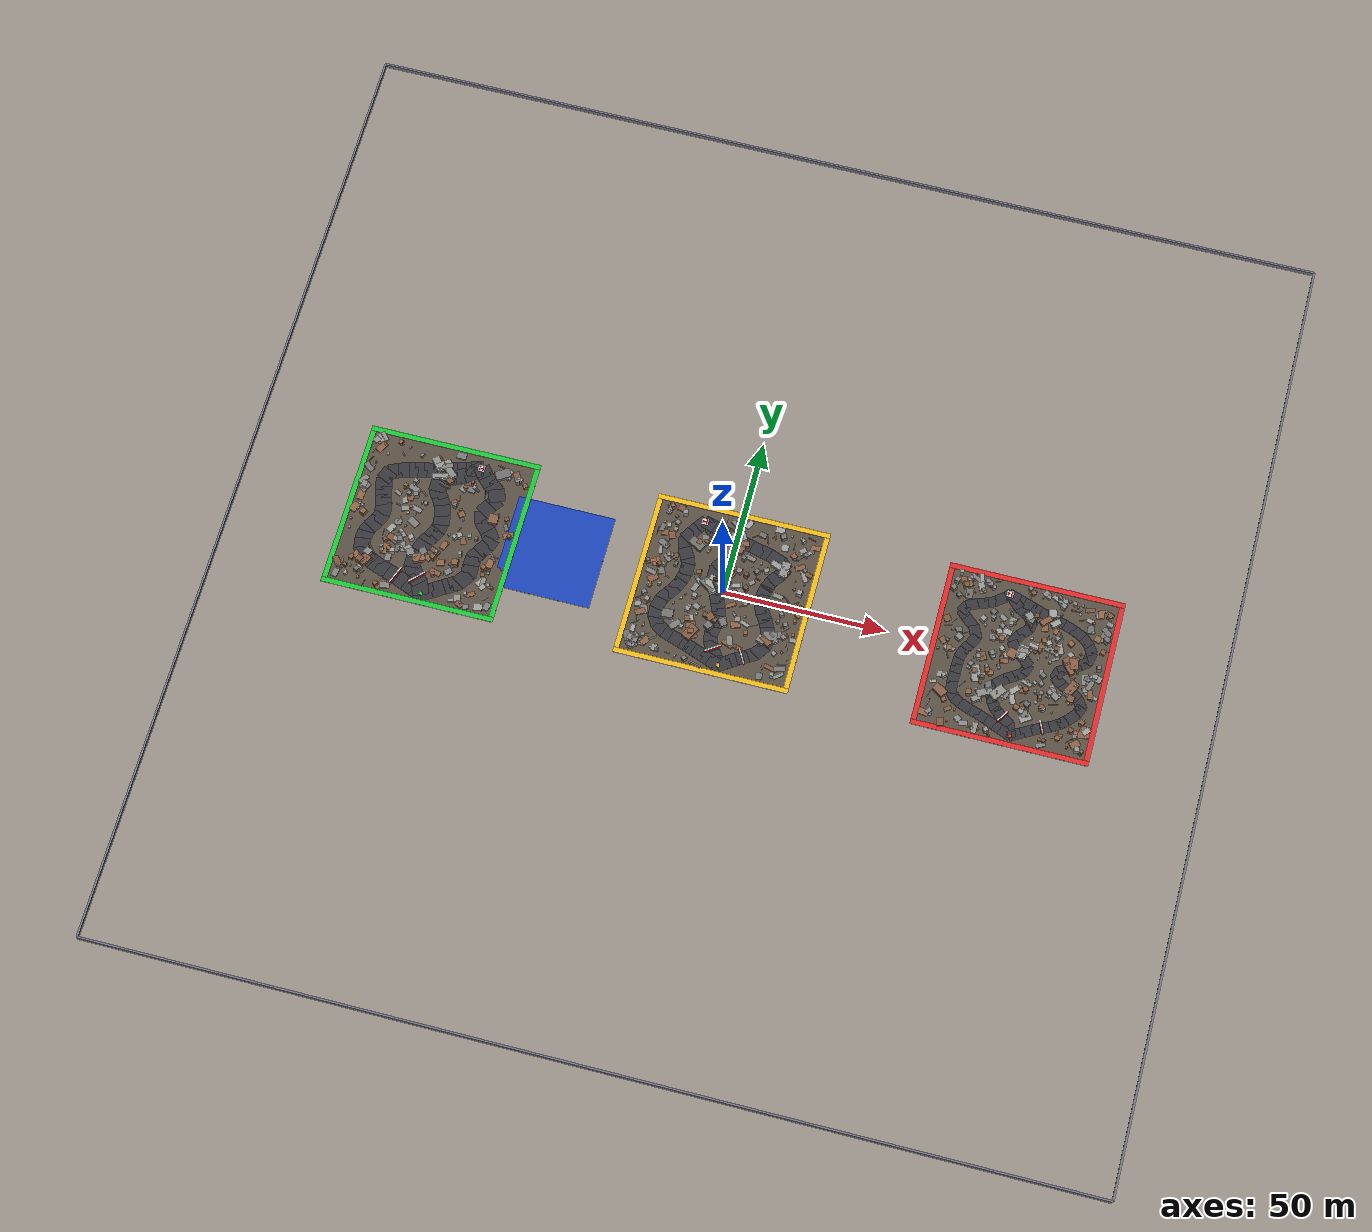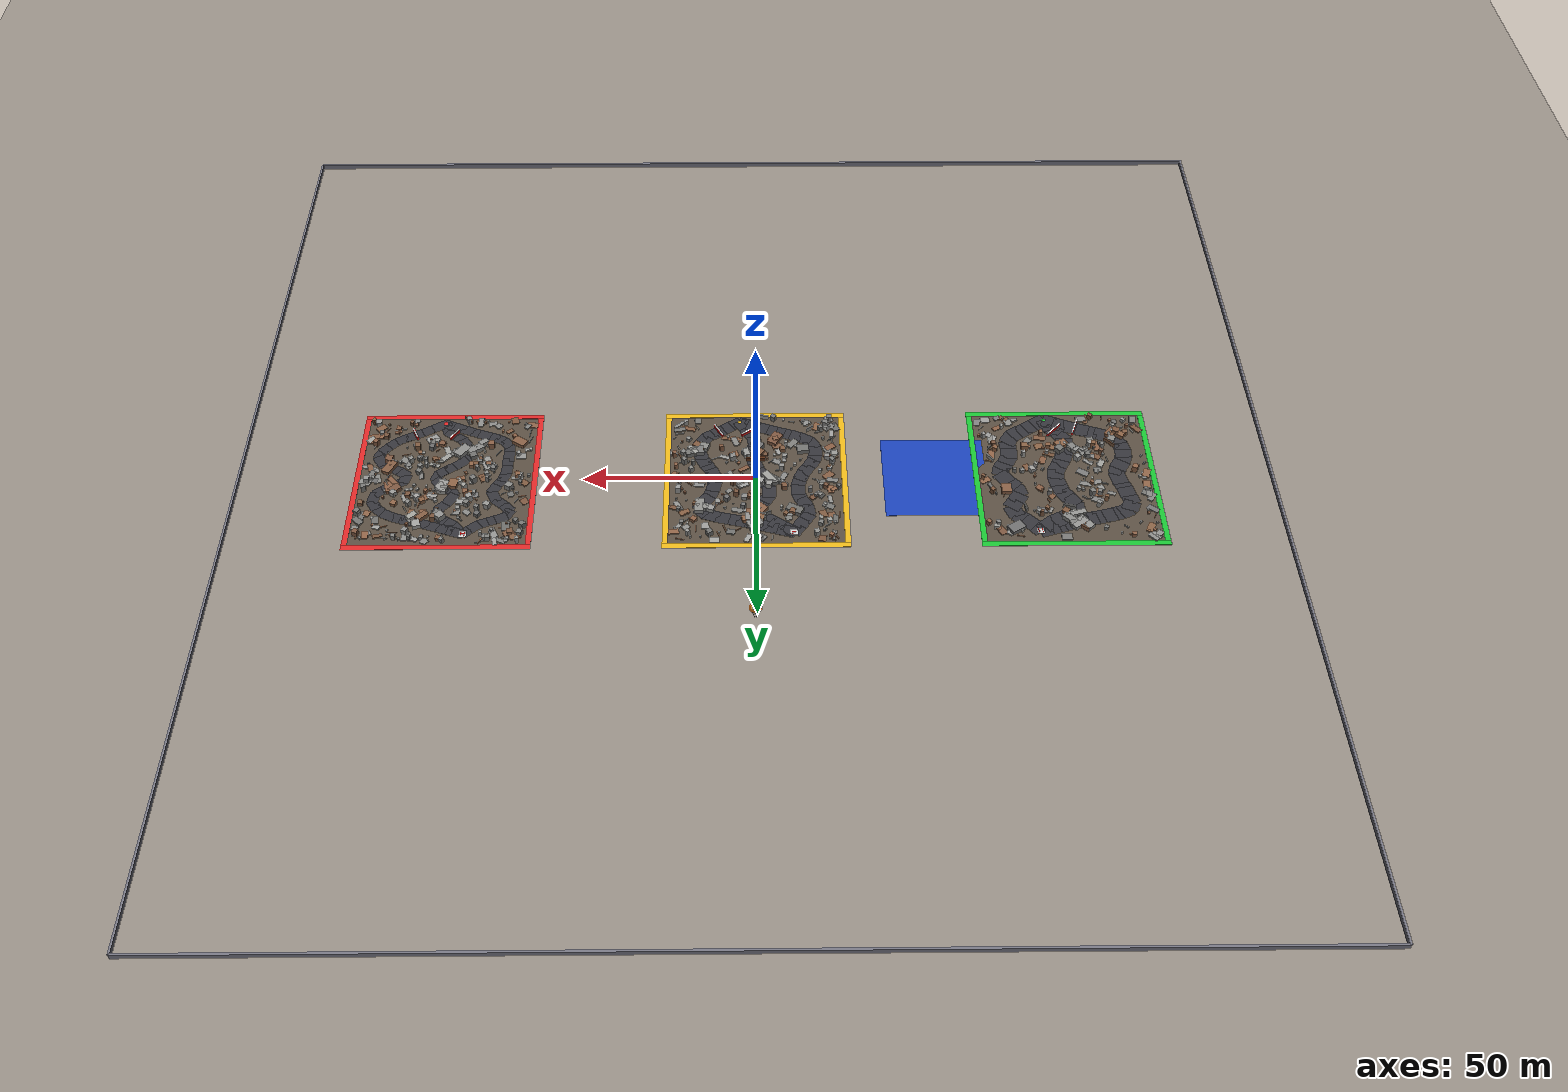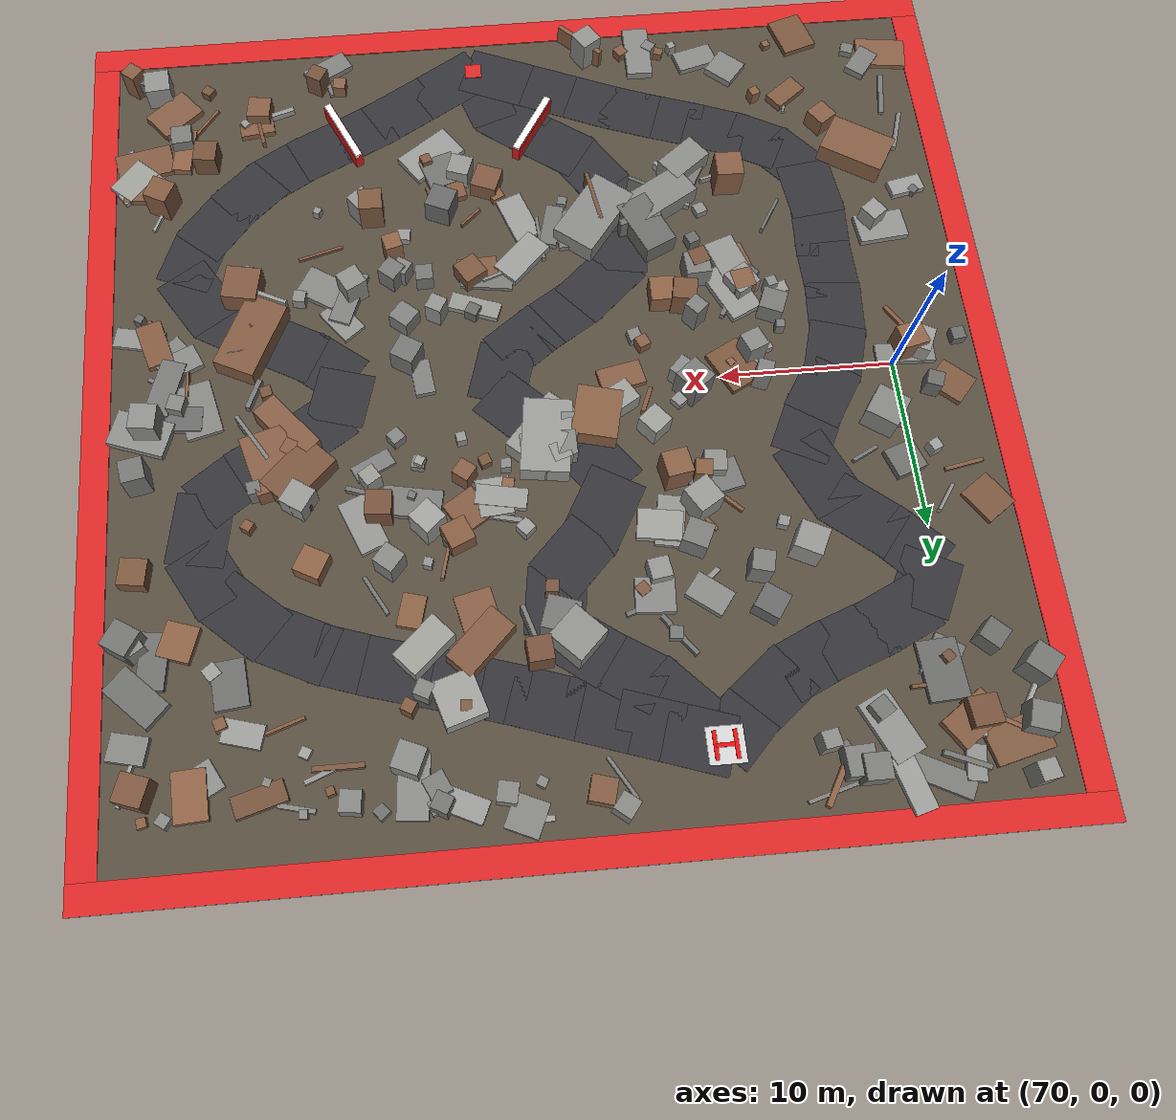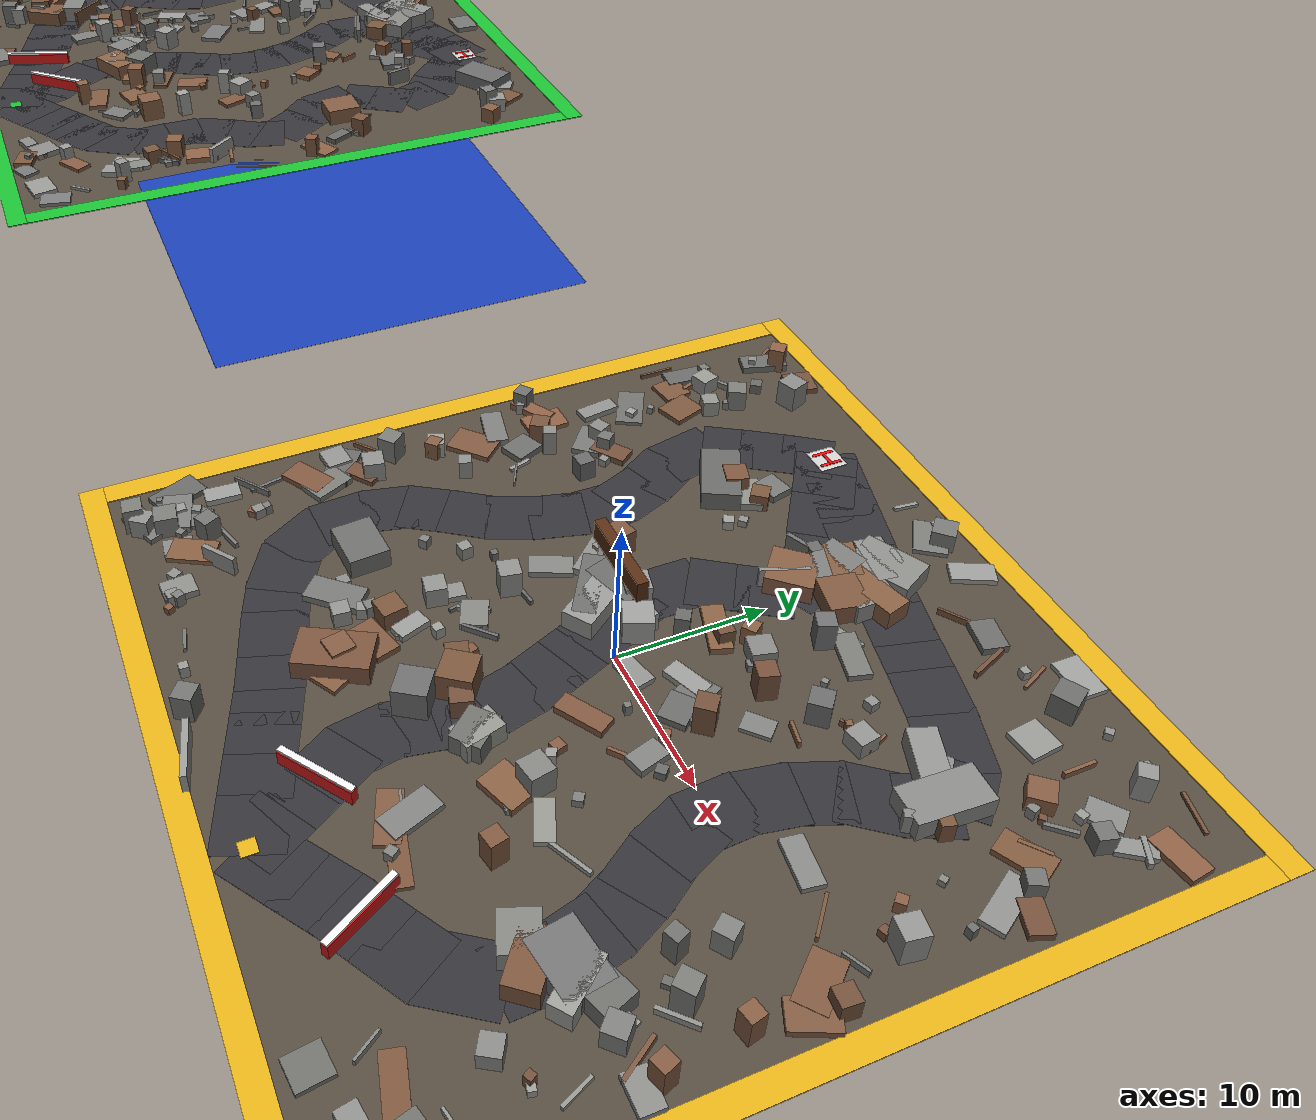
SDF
<sdf version="1.6">
 <world name="navitas_arena">
  <physics type="ode">
   <max_step_size>0.001</max_step_size>
   <real_time_factor>1</real_time_factor>
   <gravity>0 0 -9.8</gravity>
  </physics>
  <wind><linear_velocity>4.0000 1.5000 0.0000</linear_velocity></wind>
  <scene>
   <ambient>0.4200 0.4000 0.3800 1.0000</ambient>
   <background>0.5200 0.4800 0.4400 1.0000</background>
   <shadows>false</shadows>
  </scene>
  <light name="sun" type="directional">
   <cast_shadows>false</cast_shadows>
   <pose>0 0 120 0 0 0</pose>
   <diffuse>0.7200 0.6600 0.5800 1.0000</diffuse>
   <specular>0.1 0.1 0.1 1</specular>
   <attenuation>
    <range>1200</range>
    <constant>0.9</constant>
    <linear>0.01</linear>
    <quadratic>0.001</quadratic>
   </attenuation>
   <direction>0.4500 -0.1500 -0.8800</direction>
  </light>
  <model name="ground_plane">
   <static>true</static>
   <link name="link">
    <collision name="collision">
     <geometry><plane><normal>0 0 1</normal><size>400 400</size></plane></geometry>
     <surface><friction><ode><mu>0.620</mu><mu2>0.620</mu2></ode></friction></surface>
    </collision>
    <visual name="visual">
     <cast_shadows>false</cast_shadows>
     <geometry><plane><normal>0 0 1</normal><size>400 400</size></plane></geometry>
     <material><ambient>0.250 0.230 0.200 1</ambient><diffuse>0.250 0.230 0.200 1</diffuse></material>
    </visual>
   </link>
  </model>
  <model name="ub_N">
   <static>true</static>
   <pose>0.000 150.000 0.750 0 0 0.000</pose>
   <link name="link">
    <collision name="col"><geometry><box><size>300.000 0.600 1.500</size></box></geometry></collision>
    <visual name="vis">
     <geometry><box><size>300.000 0.600 1.500</size></box></geometry>
     <material><ambient>0.45 0.45 0.50 1</ambient><diffuse>0.45 0.45 0.50 1</diffuse></material>
    </visual>
   </link>
  </model>
  <model name="ub_S">
   <static>true</static>
   <pose>0.000 -150.000 0.750 0 0 0.000</pose>
   <link name="link">
    <collision name="col"><geometry><box><size>300.000 0.600 1.500</size></box></geometry></collision>
    <visual name="vis">
     <geometry><box><size>300.000 0.600 1.500</size></box></geometry>
     <material><ambient>0.45 0.45 0.50 1</ambient><diffuse>0.45 0.45 0.50 1</diffuse></material>
    </visual>
   </link>
  </model>
  <model name="ub_W">
   <static>true</static>
   <pose>-150.000 0.000 0.750 0 0 0.000</pose>
   <link name="link">
    <collision name="col"><geometry><box><size>0.600 300.000 1.500</size></box></geometry></collision>
    <visual name="vis">
     <geometry><box><size>0.600 300.000 1.500</size></box></geometry>
     <material><ambient>0.45 0.45 0.50 1</ambient><diffuse>0.45 0.45 0.50 1</diffuse></material>
    </visual>
   </link>
  </model>
  <model name="ub_E">
   <static>true</static>
   <pose>150.000 0.000 0.750 0 0 0.000</pose>
   <link name="link">
    <collision name="col"><geometry><box><size>0.600 300.000 1.500</size></box></geometry></collision>
    <visual name="vis">
     <geometry><box><size>0.600 300.000 1.500</size></box></geometry>
     <material><ambient>0.45 0.45 0.50 1</ambient><diffuse>0.45 0.45 0.50 1</diffuse></material>
    </visual>
   </link>
  </model>
  <model name="landing">
   <static>true</static>
   <pose>-52.000 0.000 0.010 0 0 0.000</pose>
   <link name="link">
    <collision name="col"><geometry><box><size>30.000 30.000 0.020</size></box></geometry></collision>
    <visual name="vis">
     <geometry><box><size>30.000 30.000 0.020</size></box></geometry>
     <material><ambient>0.10 0.25 0.70 1</ambient><diffuse>0.10 0.25 0.70 1</diffuse></material>
    </visual>
   </link>
  </model>
  <model name="gd_kolay">
   <static>true</static>
   <pose>-90.000 0.000 0.010 0 0 0.000</pose>
   <link name="link">
    <collision name="col"><geometry><box><size>50.000 50.000 0.020</size></box></geometry></collision>
    <visual name="vis">
     <geometry><box><size>50.000 50.000 0.020</size></box></geometry>
     <material><ambient>0.34 0.30 0.25 1</ambient><diffuse>0.34 0.30 0.25 1</diffuse></material>
    </visual>
   </link>
  </model>
  <model name="brd_kolay_N">
   <static>true</static>
   <pose>-90.000 25.800 0.040 0 0 0.000</pose>
   <link name="link">
    <collision name="col"><geometry><box><size>53.200 1.600 0.080</size></box></geometry></collision>
    <visual name="vis">
     <geometry><box><size>53.200 1.600 0.080</size></box></geometry>
     <material><ambient>0.10 0.75 0.20 1</ambient><diffuse>0.10 0.75 0.20 1</diffuse></material>
    </visual>
   </link>
  </model>
  <model name="brd_kolay_S">
   <static>true</static>
   <pose>-90.000 -25.800 0.040 0 0 0.000</pose>
   <link name="link">
    <collision name="col"><geometry><box><size>53.200 1.600 0.080</size></box></geometry></collision>
    <visual name="vis">
     <geometry><box><size>53.200 1.600 0.080</size></box></geometry>
     <material><ambient>0.10 0.75 0.20 1</ambient><diffuse>0.10 0.75 0.20 1</diffuse></material>
    </visual>
   </link>
  </model>
  <model name="brd_kolay_W">
   <static>true</static>
   <pose>-115.800 0.000 0.040 0 0 0.000</pose>
   <link name="link">
    <collision name="col"><geometry><box><size>1.600 50.000 0.080</size></box></geometry></collision>
    <visual name="vis">
     <geometry><box><size>1.600 50.000 0.080</size></box></geometry>
     <material><ambient>0.10 0.75 0.20 1</ambient><diffuse>0.10 0.75 0.20 1</diffuse></material>
    </visual>
   </link>
  </model>
  <model name="brd_kolay_E">
   <static>true</static>
   <pose>-64.200 0.000 0.040 0 0 0.000</pose>
   <link name="link">
    <collision name="col"><geometry><box><size>1.600 50.000 0.080</size></box></geometry></collision>
    <visual name="vis">
     <geometry><box><size>1.600 50.000 0.080</size></box></geometry>
     <material><ambient>0.10 0.75 0.20 1</ambient><diffuse>0.10 0.75 0.20 1</diffuse></material>
    </visual>
   </link>
  </model>
  <model name="road_kolay_1_0">
   <static>true</static>
   <pose>-88.082 -22.399 0.040 0 0 2.761</pose>
   <link name="link">
    <collision name="col"><geometry><box><size>4.139 4.920 0.020</size></box></geometry></collision>
    <visual name="vis">
     <geometry><box><size>4.139 4.920 0.020</size></box></geometry>
     <material><ambient>0.20 0.20 0.22 1</ambient><diffuse>0.20 0.20 0.22 1</diffuse></material>
    </visual>
   </link>
  </model>
  <model name="road_kolay_1_1">
   <static>true</static>
   <pose>-90.988 -21.236 0.040 0 0 2.761</pose>
   <link name="link">
    <collision name="col"><geometry><box><size>3.921 4.920 0.020</size></box></geometry></collision>
    <visual name="vis">
     <geometry><box><size>3.921 4.920 0.020</size></box></geometry>
     <material><ambient>0.20 0.20 0.22 1</ambient><diffuse>0.20 0.20 0.22 1</diffuse></material>
    </visual>
   </link>
  </model>
  <model name="road_kolay_1_2">
   <static>true</static>
   <pose>-93.854 -20.087 0.040 0 0 2.760</pose>
   <link name="link">
    <collision name="col"><geometry><box><size>4.055 4.920 0.020</size></box></geometry></collision>
    <visual name="vis">
     <geometry><box><size>4.055 4.920 0.020</size></box></geometry>
     <material><ambient>0.20 0.20 0.22 1</ambient><diffuse>0.20 0.20 0.22 1</diffuse></material>
    </visual>
   </link>
  </model>
  <model name="road_kolay_1_3">
   <static>true</static>
   <pose>-97.048 -18.901 0.040 0 0 2.808</pose>
   <link name="link">
    <collision name="col"><geometry><box><size>4.562 4.920 0.020</size></box></geometry></collision>
    <visual name="vis">
     <geometry><box><size>4.562 4.920 0.020</size></box></geometry>
     <material><ambient>0.20 0.20 0.22 1</ambient><diffuse>0.20 0.20 0.22 1</diffuse></material>
    </visual>
   </link>
  </model>
  <model name="road_kolay_1_4">
   <static>true</static>
   <pose>-100.051 -17.886 0.040 0 0 2.825</pose>
   <link name="link">
    <collision name="col"><geometry><box><size>3.578 4.920 0.020</size></box></geometry></collision>
    <visual name="vis">
     <geometry><box><size>3.578 4.920 0.020</size></box></geometry>
     <material><ambient>0.20 0.20 0.22 1</ambient><diffuse>0.20 0.20 0.22 1</diffuse></material>
    </visual>
   </link>
  </model>
  <model name="road_kolay_1_5">
   <static>true</static>
   <pose>-102.527 -17.017 0.040 0 0 2.783</pose>
   <link name="link">
    <collision name="col"><geometry><box><size>3.471 4.920 0.020</size></box></geometry></collision>
    <visual name="vis">
     <geometry><box><size>3.471 4.920 0.020</size></box></geometry>
     <material><ambient>0.20 0.20 0.22 1</ambient><diffuse>0.20 0.20 0.22 1</diffuse></material>
    </visual>
   </link>
  </model>
  <model name="road_kolay_1_6">
   <static>true</static>
   <pose>-105.099 -15.783 0.040 0 0 2.622</pose>
   <link name="link">
    <collision name="col"><geometry><box><size>4.053 4.920 0.020</size></box></geometry></collision>
    <visual name="vis">
     <geometry><box><size>4.053 4.920 0.020</size></box></geometry>
     <material><ambient>0.20 0.20 0.22 1</ambient><diffuse>0.20 0.20 0.22 1</diffuse></material>
    </visual>
   </link>
  </model>
  <model name="road_kolay_1_7">
   <static>true</static>
   <pose>-107.212 -13.926 0.040 0 0 2.177</pose>
   <link name="link">
    <collision name="col"><geometry><box><size>3.514 4.920 0.020</size></box></geometry></collision>
    <visual name="vis">
     <geometry><box><size>3.514 4.920 0.020</size></box></geometry>
     <material><ambient>0.20 0.20 0.22 1</ambient><diffuse>0.20 0.20 0.22 1</diffuse></material>
    </visual>
   </link>
  </model>
  <model name="road_kolay_1_8">
   <static>true</static>
   <pose>-108.184 -11.639 0.040 0 0 1.756</pose>
   <link name="link">
    <collision name="col"><geometry><box><size>3.368 4.920 0.020</size></box></geometry></collision>
    <visual name="vis">
     <geometry><box><size>3.368 4.920 0.020</size></box></geometry>
     <material><ambient>0.20 0.20 0.22 1</ambient><diffuse>0.20 0.20 0.22 1</diffuse></material>
    </visual>
   </link>
  </model>
  <model name="road_kolay_1_9">
   <static>true</static>
   <pose>-108.360 -9.213 0.040 0 0 1.529</pose>
   <link name="link">
    <collision name="col"><geometry><box><size>3.328 4.920 0.020</size></box></geometry></collision>
    <visual name="vis">
     <geometry><box><size>3.328 4.920 0.020</size></box></geometry>
     <material><ambient>0.20 0.20 0.22 1</ambient><diffuse>0.20 0.20 0.22 1</diffuse></material>
    </visual>
   </link>
  </model>
  <model name="road_kolay_1_10">
   <static>true</static>
   <pose>-107.875 -6.833 0.040 0 0 1.214</pose>
   <link name="link">
    <collision name="col"><geometry><box><size>3.390 4.920 0.020</size></box></geometry></collision>
    <visual name="vis">
     <geometry><box><size>3.390 4.920 0.020</size></box></geometry>
     <material><ambient>0.20 0.20 0.22 1</ambient><diffuse>0.20 0.20 0.22 1</diffuse></material>
    </visual>
   </link>
  </model>
  <model name="road_kolay_1_11">
   <static>true</static>
   <pose>-106.728 -4.500 0.040 0 0 1.022</pose>
   <link name="link">
    <collision name="col"><geometry><box><size>3.634 4.920 0.020</size></box></geometry></collision>
    <visual name="vis">
     <geometry><box><size>3.634 4.920 0.020</size></box></geometry>
     <material><ambient>0.20 0.20 0.22 1</ambient><diffuse>0.20 0.20 0.22 1</diffuse></material>
    </visual>
   </link>
  </model>
  <model name="road_kolay_1_12">
   <static>true</static>
   <pose>-105.579 -2.167 0.040 0 0 1.213</pose>
   <link name="link">
    <collision name="col"><geometry><box><size>3.391 4.920 0.020</size></box></geometry></collision>
    <visual name="vis">
     <geometry><box><size>3.391 4.920 0.020</size></box></geometry>
     <material><ambient>0.20 0.20 0.22 1</ambient><diffuse>0.20 0.20 0.22 1</diffuse></material>
    </visual>
   </link>
  </model>
  <model name="road_kolay_1_13">
   <static>true</static>
   <pose>-105.493 0.750 0.040 0 0 1.769</pose>
   <link name="link">
    <collision name="col"><geometry><box><size>4.470 4.920 0.020</size></box></geometry></collision>
    <visual name="vis">
     <geometry><box><size>4.470 4.920 0.020</size></box></geometry>
     <material><ambient>0.20 0.20 0.22 1</ambient><diffuse>0.20 0.20 0.22 1</diffuse></material>
    </visual>
   </link>
  </model>
  <model name="road_kolay_1_14">
   <static>true</static>
   <pose>-106.267 3.667 0.040 0 0 1.918</pose>
   <link name="link">
    <collision name="col"><geometry><box><size>3.381 4.920 0.020</size></box></geometry></collision>
    <visual name="vis">
     <geometry><box><size>3.381 4.920 0.020</size></box></geometry>
     <material><ambient>0.20 0.20 0.22 1</ambient><diffuse>0.20 0.20 0.22 1</diffuse></material>
    </visual>
   </link>
  </model>
  <model name="road_kolay_1_15">
   <static>true</static>
   <pose>-106.991 6.137 0.040 0 0 1.798</pose>
   <link name="link">
    <collision name="col"><geometry><box><size>3.575 4.920 0.020</size></box></geometry></collision>
    <visual name="vis">
     <geometry><box><size>3.575 4.920 0.020</size></box></geometry>
     <material><ambient>0.20 0.20 0.22 1</ambient><diffuse>0.20 0.20 0.22 1</diffuse></material>
    </visual>
   </link>
  </model>
  <model name="road_kolay_1_16">
   <static>true</static>
   <pose>-107.691 8.910 0.040 0 0 1.836</pose>
   <link name="link">
    <collision name="col"><geometry><box><size>3.946 4.920 0.020</size></box></geometry></collision>
    <visual name="vis">
     <geometry><box><size>3.946 4.920 0.020</size></box></geometry>
     <material><ambient>0.20 0.20 0.22 1</ambient><diffuse>0.20 0.20 0.22 1</diffuse></material>
    </visual>
   </link>
  </model>
  <model name="road_kolay_1_17">
   <static>true</static>
   <pose>-107.504 11.690 0.040 0 0 1.150</pose>
   <link name="link">
    <collision name="col"><geometry><box><size>3.770 4.920 0.020</size></box></geometry></collision>
    <visual name="vis">
     <geometry><box><size>3.770 4.920 0.020</size></box></geometry>
     <material><ambient>0.20 0.20 0.22 1</ambient><diffuse>0.20 0.20 0.22 1</diffuse></material>
    </visual>
   </link>
  </model>
  <model name="road_kolay_1_18">
   <static>true</static>
   <pose>-105.667 13.615 0.040 0 0 0.457</pose>
   <link name="link">
    <collision name="col"><geometry><box><size>3.688 4.920 0.020</size></box></geometry></collision>
    <visual name="vis">
     <geometry><box><size>3.688 4.920 0.020</size></box></geometry>
     <material><ambient>0.20 0.20 0.22 1</ambient><diffuse>0.20 0.20 0.22 1</diffuse></material>
    </visual>
   </link>
  </model>
  <model name="road_kolay_1_19">
   <static>true</static>
   <pose>-103.256 14.594 0.040 0 0 0.304</pose>
   <link name="link">
    <collision name="col"><geometry><box><size>3.331 4.920 0.020</size></box></geometry></collision>
    <visual name="vis">
     <geometry><box><size>3.331 4.920 0.020</size></box></geometry>
     <material><ambient>0.20 0.20 0.22 1</ambient><diffuse>0.20 0.20 0.22 1</diffuse></material>
    </visual>
   </link>
  </model>
  <model name="road_kolay_1_20">
   <static>true</static>
   <pose>-100.794 15.296 0.040 0 0 0.254</pose>
   <link name="link">
    <collision name="col"><geometry><box><size>3.591 4.920 0.020</size></box></geometry></collision>
    <visual name="vis">
     <geometry><box><size>3.591 4.920 0.020</size></box></geometry>
     <material><ambient>0.20 0.20 0.22 1</ambient><diffuse>0.20 0.20 0.22 1</diffuse></material>
    </visual>
   </link>
  </model>
  <model name="road_kolay_1_21">
   <static>true</static>
   <pose>-98.146 15.952 0.040 0 0 0.233</pose>
   <link name="link">
    <collision name="col"><geometry><box><size>3.665 4.920 0.020</size></box></geometry></collision>
    <visual name="vis">
     <geometry><box><size>3.665 4.920 0.020</size></box></geometry>
     <material><ambient>0.20 0.20 0.22 1</ambient><diffuse>0.20 0.20 0.22 1</diffuse></material>
    </visual>
   </link>
  </model>
  <model name="road_kolay_1_22">
   <static>true</static>
   <pose>-95.513 16.579 0.040 0 0 0.235</pose>
   <link name="link">
    <collision name="col"><geometry><box><size>3.548 4.920 0.020</size></box></geometry></collision>
    <visual name="vis">
     <geometry><box><size>3.548 4.920 0.020</size></box></geometry>
     <material><ambient>0.20 0.20 0.22 1</ambient><diffuse>0.20 0.20 0.22 1</diffuse></material>
    </visual>
   </link>
  </model>
  <model name="road_kolay_1_23">
   <static>true</static>
   <pose>-92.425 17.397 0.040 0 0 0.276</pose>
   <link name="link">
    <collision name="col"><geometry><box><size>4.640 4.920 0.020</size></box></geometry></collision>
    <visual name="vis">
     <geometry><box><size>4.640 4.920 0.020</size></box></geometry>
     <material><ambient>0.20 0.20 0.22 1</ambient><diffuse>0.20 0.20 0.22 1</diffuse></material>
    </visual>
   </link>
  </model>
  <model name="road_kolay_1_24">
   <static>true</static>
   <pose>-89.266 18.320 0.040 0 0 0.295</pose>
   <link name="link">
    <collision name="col"><geometry><box><size>3.744 4.920 0.020</size></box></geometry></collision>
    <visual name="vis">
     <geometry><box><size>3.744 4.920 0.020</size></box></geometry>
     <material><ambient>0.20 0.20 0.22 1</ambient><diffuse>0.20 0.20 0.22 1</diffuse></material>
    </visual>
   </link>
  </model>
  <model name="road_kolay_1_25">
   <static>true</static>
   <pose>-86.598 19.133 0.040 0 0 0.296</pose>
   <link name="link">
    <collision name="col"><geometry><box><size>3.633 4.920 0.020</size></box></geometry></collision>
    <visual name="vis">
     <geometry><box><size>3.633 4.920 0.020</size></box></geometry>
     <material><ambient>0.20 0.20 0.22 1</ambient><diffuse>0.20 0.20 0.22 1</diffuse></material>
    </visual>
   </link>
  </model>
  <model name="road_kolay_1_26">
   <static>true</static>
   <pose>-84.133 19.885 0.040 0 0 0.297</pose>
   <link name="link">
    <collision name="col"><geometry><box><size>3.321 4.920 0.020</size></box></geometry></collision>
    <visual name="vis">
     <geometry><box><size>3.321 4.920 0.020</size></box></geometry>
     <material><ambient>0.20 0.20 0.22 1</ambient><diffuse>0.20 0.20 0.22 1</diffuse></material>
    </visual>
   </link>
  </model>
  <model name="road_kolay_1_27">
   <static>true</static>
   <pose>-81.730 20.619 0.040 0 0 0.297</pose>
   <link name="link">
    <collision name="col"><geometry><box><size>3.505 4.920 0.020</size></box></geometry></collision>
    <visual name="vis">
     <geometry><box><size>3.505 4.920 0.020</size></box></geometry>
     <material><ambient>0.20 0.20 0.22 1</ambient><diffuse>0.20 0.20 0.22 1</diffuse></material>
    </visual>
   </link>
  </model>
  <model name="road_kolay_2_0">
   <static>true</static>
   <pose>-87.348 -21.250 0.040 0 0 1.985</pose>
   <link name="link">
    <collision name="col"><geometry><box><size>4.724 4.920 0.020</size></box></geometry></collision>
    <visual name="vis">
     <geometry><box><size>4.724 4.920 0.020</size></box></geometry>
     <material><ambient>0.20 0.20 0.22 1</ambient><diffuse>0.20 0.20 0.22 1</diffuse></material>
    </visual>
   </link>
  </model>
  <model name="road_kolay_2_1">
   <static>true</static>
   <pose>-89.084 -18.484 0.040 0 0 2.331</pose>
   <link name="link">
    <collision name="col"><geometry><box><size>3.704 4.920 0.020</size></box></geometry></collision>
    <visual name="vis">
     <geometry><box><size>3.704 4.920 0.020</size></box></geometry>
     <material><ambient>0.20 0.20 0.22 1</ambient><diffuse>0.20 0.20 0.22 1</diffuse></material>
    </visual>
   </link>
  </model>
  <model name="road_kolay_2_2">
   <static>true</static>
   <pose>-90.859 -16.234 0.040 0 0 2.151</pose>
   <link name="link">
    <collision name="col"><geometry><box><size>3.851 4.920 0.020</size></box></geometry></collision>
    <visual name="vis">
     <geometry><box><size>3.851 4.920 0.020</size></box></geometry>
     <material><ambient>0.20 0.20 0.22 1</ambient><diffuse>0.20 0.20 0.22 1</diffuse></material>
    </visual>
   </link>
  </model>
  <model name="road_kolay_2_3">
   <static>true</static>
   <pose>-91.690 -13.690 0.040 0 0 1.588</pose>
   <link name="link">
    <collision name="col"><geometry><box><size>3.520 4.920 0.020</size></box></geometry></collision>
    <visual name="vis">
     <geometry><box><size>3.520 4.920 0.020</size></box></geometry>
     <material><ambient>0.20 0.20 0.22 1</ambient><diffuse>0.20 0.20 0.22 1</diffuse></material>
    </visual>
   </link>
  </model>
  <model name="road_kolay_2_4">
   <static>true</static>
   <pose>-91.406 -10.910 0.040 0 0 1.365</pose>
   <link name="link">
    <collision name="col"><geometry><box><size>3.903 4.920 0.020</size></box></geometry></collision>
    <visual name="vis">
     <geometry><box><size>3.903 4.920 0.020</size></box></geometry>
     <material><ambient>0.20 0.20 0.22 1</ambient><diffuse>0.20 0.20 0.22 1</diffuse></material>
    </visual>
   </link>
  </model>
  <model name="road_kolay_2_5">
   <static>true</static>
   <pose>-90.652 -8.137 0.040 0 0 1.240</pose>
   <link name="link">
    <collision name="col"><geometry><box><size>3.656 4.920 0.020</size></box></geometry></collision>
    <visual name="vis">
     <geometry><box><size>3.656 4.920 0.020</size></box></geometry>
     <material><ambient>0.20 0.20 0.22 1</ambient><diffuse>0.20 0.20 0.22 1</diffuse></material>
    </visual>
   </link>
  </model>
  <model name="road_kolay_2_6">
   <static>true</static>
   <pose>-89.540 -5.667 0.040 0 0 1.052</pose>
   <link name="link">
    <collision name="col"><geometry><box><size>3.586 4.920 0.020</size></box></geometry></collision>
    <visual name="vis">
     <geometry><box><size>3.586 4.920 0.020</size></box></geometry>
     <material><ambient>0.20 0.20 0.22 1</ambient><diffuse>0.20 0.20 0.22 1</diffuse></material>
    </visual>
   </link>
  </model>
  <model name="road_kolay_2_7">
   <static>true</static>
   <pose>-88.267 -3.333 0.040 0 0 1.091</pose>
   <link name="link">
    <collision name="col"><geometry><box><size>3.530 4.920 0.020</size></box></geometry></collision>
    <visual name="vis">
     <geometry><box><size>3.530 4.920 0.020</size></box></geometry>
     <material><ambient>0.20 0.20 0.22 1</ambient><diffuse>0.20 0.20 0.22 1</diffuse></material>
    </visual>
   </link>
  </model>
  <model name="road_kolay_2_8">
   <static>true</static>
   <pose>-87.447 -0.883 0.040 0 0 1.406</pose>
   <link name="link">
    <collision name="col"><geometry><box><size>3.502 4.920 0.020</size></box></geometry></collision>
    <visual name="vis">
     <geometry><box><size>3.502 4.920 0.020</size></box></geometry>
     <material><ambient>0.20 0.20 0.22 1</ambient><diffuse>0.20 0.20 0.22 1</diffuse></material>
    </visual>
   </link>
  </model>
  <model name="road_kolay_2_9">
   <static>true</static>
   <pose>-87.422 1.800 0.040 0 0 1.705</pose>
   <link name="link">
    <collision name="col"><geometry><box><size>3.725 4.920 0.020</size></box></geometry></collision>
    <visual name="vis">
     <geometry><box><size>3.725 4.920 0.020</size></box></geometry>
     <material><ambient>0.20 0.20 0.22 1</ambient><diffuse>0.20 0.20 0.22 1</diffuse></material>
    </visual>
   </link>
  </model>
  <model name="road_kolay_2_10">
   <static>true</static>
   <pose>-88.036 4.600 0.040 0 0 1.866</pose>
   <link name="link">
    <collision name="col"><geometry><box><size>3.826 4.920 0.020</size></box></geometry></collision>
    <visual name="vis">
     <geometry><box><size>3.826 4.920 0.020</size></box></geometry>
     <material><ambient>0.20 0.20 0.22 1</ambient><diffuse>0.20 0.20 0.22 1</diffuse></material>
    </visual>
   </link>
  </model>
  <model name="road_kolay_2_11">
   <static>true</static>
   <pose>-89.189 7.213 0.040 0 0 2.111</pose>
   <link name="link">
    <collision name="col"><geometry><box><size>3.729 4.920 0.020</size></box></geometry></collision>
    <visual name="vis">
     <geometry><box><size>3.729 4.920 0.020</size></box></geometry>
     <material><ambient>0.20 0.20 0.22 1</ambient><diffuse>0.20 0.20 0.22 1</diffuse></material>
    </visual>
   </link>
  </model>
  <model name="road_kolay_2_12">
   <static>true</static>
   <pose>-90.787 9.639 0.040 0 0 2.193</pose>
   <link name="link">
    <collision name="col"><geometry><box><size>3.886 4.920 0.020</size></box></geometry></collision>
    <visual name="vis">
     <geometry><box><size>3.886 4.920 0.020</size></box></geometry>
     <material><ambient>0.20 0.20 0.22 1</ambient><diffuse>0.20 0.20 0.22 1</diffuse></material>
    </visual>
   </link>
  </model>
  <model name="road_kolay_2_13">
   <static>true</static>
   <pose>-91.660 12.317 0.040 0 0 1.573</pose>
   <link name="link">
    <collision name="col"><geometry><box><size>3.831 4.920 0.020</size></box></geometry></collision>
    <visual name="vis">
     <geometry><box><size>3.831 4.920 0.020</size></box></geometry>
     <material><ambient>0.20 0.20 0.22 1</ambient><diffuse>0.20 0.20 0.22 1</diffuse></material>
    </visual>
   </link>
  </model>
  <model name="road_kolay_2_14">
   <static>true</static>
   <pose>-90.635 14.469 0.040 0 0 0.589</pose>
   <link name="link">
    <collision name="col"><geometry><box><size>3.372 4.920 0.020</size></box></geometry></collision>
    <visual name="vis">
     <geometry><box><size>3.372 4.920 0.020</size></box></geometry>
     <material><ambient>0.20 0.20 0.22 1</ambient><diffuse>0.20 0.20 0.22 1</diffuse></material>
    </visual>
   </link>
  </model>
  <model name="road_kolay_2_15">
   <static>true</static>
   <pose>-88.292 15.758 0.040 0 0 0.429</pose>
   <link name="link">
    <collision name="col"><geometry><box><size>3.793 4.920 0.020</size></box></geometry></collision>
    <visual name="vis">
     <geometry><box><size>3.793 4.920 0.020</size></box></geometry>
     <material><ambient>0.20 0.20 0.22 1</ambient><diffuse>0.20 0.20 0.22 1</diffuse></material>
    </visual>
   </link>
  </model>
  <model name="road_kolay_2_16">
   <static>true</static>
   <pose>-85.871 16.930 0.040 0 0 0.476</pose>
   <link name="link">
    <collision name="col"><geometry><box><size>3.387 4.920 0.020</size></box></geometry></collision>
    <visual name="vis">
     <geometry><box><size>3.387 4.920 0.020</size></box></geometry>
     <material><ambient>0.20 0.20 0.22 1</ambient><diffuse>0.20 0.20 0.22 1</diffuse></material>
    </visual>
   </link>
  </model>
  <model name="road_kolay_2_17">
   <static>true</static>
   <pose>-83.465 18.516 0.040 0 0 0.663</pose>
   <link name="link">
    <collision name="col"><geometry><box><size>4.202 4.920 0.020</size></box></geometry></collision>
    <visual name="vis">
     <geometry><box><size>4.202 4.920 0.020</size></box></geometry>
     <material><ambient>0.20 0.20 0.22 1</ambient><diffuse>0.20 0.20 0.22 1</diffuse></material>
    </visual>
   </link>
  </model>
  <model name="road_kolay_2_18">
   <static>true</static>
   <pose>-81.324 20.266 0.040 0 0 0.719</pose>
   <link name="link">
    <collision name="col"><geometry><box><size>3.131 4.920 0.020</size></box></geometry></collision>
    <visual name="vis">
     <geometry><box><size>3.131 4.920 0.020</size></box></geometry>
     <material><ambient>0.20 0.20 0.22 1</ambient><diffuse>0.20 0.20 0.22 1</diffuse></material>
    </visual>
   </link>
  </model>
  <model name="road_kolay_3_0">
   <static>true</static>
   <pose>-85.028 -22.070 0.040 0 0 0.540</pose>
   <link name="link">
    <collision name="col"><geometry><box><size>4.515 4.920 0.020</size></box></geometry></collision>
    <visual name="vis">
     <geometry><box><size>4.515 4.920 0.020</size></box></geometry>
     <material><ambient>0.20 0.20 0.22 1</ambient><diffuse>0.20 0.20 0.22 1</diffuse></material>
    </visual>
   </link>
  </model>
  <model name="road_kolay_3_1">
   <static>true</static>
   <pose>-82.198 -20.320 0.040 0 0 0.570</pose>
   <link name="link">
    <collision name="col"><geometry><box><size>3.941 4.920 0.020</size></box></geometry></collision>
    <visual name="vis">
     <geometry><box><size>3.941 4.920 0.020</size></box></geometry>
     <material><ambient>0.20 0.20 0.22 1</ambient><diffuse>0.20 0.20 0.22 1</diffuse></material>
    </visual>
   </link>
  </model>
  <model name="road_kolay_3_2">
   <static>true</static>
   <pose>-79.824 -18.833 0.040 0 0 0.547</pose>
   <link name="link">
    <collision name="col"><geometry><box><size>3.463 4.920 0.020</size></box></geometry></collision>
    <visual name="vis">
     <geometry><box><size>3.463 4.920 0.020</size></box></geometry>
     <material><ambient>0.20 0.20 0.22 1</ambient><diffuse>0.20 0.20 0.22 1</diffuse></material>
    </visual>
   </link>
  </model>
  <model name="road_kolay_3_3">
   <static>true</static>
   <pose>-77.616 -17.444 0.040 0 0 0.575</pose>
   <link name="link">
    <collision name="col"><geometry><box><size>3.554 4.920 0.020</size></box></geometry></collision>
    <visual name="vis">
     <geometry><box><size>3.554 4.920 0.020</size></box></geometry>
     <material><ambient>0.20 0.20 0.22 1</ambient><diffuse>0.20 0.20 0.22 1</diffuse></material>
    </visual>
   </link>
  </model>
  <model name="road_kolay_3_4">
   <static>true</static>
   <pose>-75.523 -15.241 0.040 0 0 0.986</pose>
   <link name="link">
    <collision name="col"><geometry><box><size>4.452 4.920 0.020</size></box></geometry></collision>
    <visual name="vis">
     <geometry><box><size>4.452 4.920 0.020</size></box></geometry>
     <material><ambient>0.20 0.20 0.22 1</ambient><diffuse>0.20 0.20 0.22 1</diffuse></material>
    </visual>
   </link>
  </model>
  <model name="road_kolay_3_5">
   <static>true</static>
   <pose>-74.625 -12.340 0.040 0 0 1.628</pose>
   <link name="link">
    <collision name="col"><geometry><box><size>3.745 4.920 0.020</size></box></geometry></collision>
    <visual name="vis">
     <geometry><box><size>3.745 4.920 0.020</size></box></geometry>
     <material><ambient>0.20 0.20 0.22 1</ambient><diffuse>0.20 0.20 0.22 1</diffuse></material>
    </visual>
   </link>
  </model>
  <model name="road_kolay_3_6">
   <static>true</static>
   <pose>-74.675 -9.460 0.040 0 0 1.549</pose>
   <link name="link">
    <collision name="col"><geometry><box><size>3.821 4.920 0.020</size></box></geometry></collision>
    <visual name="vis">
     <geometry><box><size>3.821 4.920 0.020</size></box></geometry>
     <material><ambient>0.20 0.20 0.22 1</ambient><diffuse>0.20 0.20 0.22 1</diffuse></material>
    </visual>
   </link>
  </model>
  <model name="road_kolay_3_7">
   <static>true</static>
   <pose>-74.025 -6.833 0.040 0 0 1.083</pose>
   <link name="link">
    <collision name="col"><geometry><box><size>3.542 4.920 0.020</size></box></geometry></collision>
    <visual name="vis">
     <geometry><box><size>3.542 4.920 0.020</size></box></geometry>
     <material><ambient>0.20 0.20 0.22 1</ambient><diffuse>0.20 0.20 0.22 1</diffuse></material>
    </visual>
   </link>
  </model>
  <model name="road_kolay_3_8">
   <static>true</static>
   <pose>-72.608 -4.500 0.040 0 0 0.971</pose>
   <link name="link">
    <collision name="col"><geometry><box><size>3.726 4.920 0.020</size></box></geometry></collision>
    <visual name="vis">
     <geometry><box><size>3.726 4.920 0.020</size></box></geometry>
     <material><ambient>0.20 0.20 0.22 1</ambient><diffuse>0.20 0.20 0.22 1</diffuse></material>
    </visual>
   </link>
  </model>
  <model name="road_kolay_3_9">
   <static>true</static>
   <pose>-71.494 -2.167 0.040 0 0 1.306</pose>
   <link name="link">
    <collision name="col"><geometry><box><size>3.318 4.920 0.020</size></box></geometry></collision>
    <visual name="vis">
     <geometry><box><size>3.318 4.920 0.020</size></box></geometry>
     <material><ambient>0.20 0.20 0.22 1</ambient><diffuse>0.20 0.20 0.22 1</diffuse></material>
    </visual>
   </link>
  </model>
  <model name="road_kolay_3_10">
   <static>true</static>
   <pose>-72.211 0.500 0.040 0 0 2.174</pose>
   <link name="link">
    <collision name="col"><geometry><box><size>4.544 4.920 0.020</size></box></geometry></collision>
    <visual name="vis">
     <geometry><box><size>4.544 4.920 0.020</size></box></geometry>
     <material><ambient>0.20 0.20 0.22 1</ambient><diffuse>0.20 0.20 0.22 1</diffuse></material>
    </visual>
   </link>
  </model>
  <model name="road_kolay_3_11">
   <static>true</static>
   <pose>-74.249 3.000 0.040 0 0 2.358</pose>
   <link name="link">
    <collision name="col"><geometry><box><size>3.734 4.920 0.020</size></box></geometry></collision>
    <visual name="vis">
     <geometry><box><size>3.734 4.920 0.020</size></box></geometry>
     <material><ambient>0.20 0.20 0.22 1</ambient><diffuse>0.20 0.20 0.22 1</diffuse></material>
    </visual>
   </link>
  </model>
  <model name="road_kolay_3_12">
   <static>true</static>
   <pose>-75.717 5.598 0.040 0 0 1.853</pose>
   <link name="link">
    <collision name="col"><geometry><box><size>4.227 4.920 0.020</size></box></geometry></collision>
    <visual name="vis">
     <geometry><box><size>4.227 4.920 0.020</size></box></geometry>
     <material><ambient>0.20 0.20 0.22 1</ambient><diffuse>0.20 0.20 0.22 1</diffuse></material>
    </visual>
   </link>
  </model>
  <model name="road_kolay_3_13">
   <static>true</static>
   <pose>-75.413 8.426 0.040 0 0 1.013</pose>
   <link name="link">
    <collision name="col"><geometry><box><size>3.800 4.920 0.020</size></box></geometry></collision>
    <visual name="vis">
     <geometry><box><size>3.800 4.920 0.020</size></box></geometry>
     <material><ambient>0.20 0.20 0.22 1</ambient><diffuse>0.20 0.20 0.22 1</diffuse></material>
    </visual>
   </link>
  </model>
  <model name="road_kolay_3_14">
   <static>true</static>
   <pose>-73.864 10.817 0.040 0 0 0.979</pose>
   <link name="link">
    <collision name="col"><geometry><box><size>3.698 4.920 0.020</size></box></geometry></collision>
    <visual name="vis">
     <geometry><box><size>3.698 4.920 0.020</size></box></geometry>
     <material><ambient>0.20 0.20 0.22 1</ambient><diffuse>0.20 0.20 0.22 1</diffuse></material>
    </visual>
   </link>
  </model>
  <model name="road_kolay_3_15">
   <static>true</static>
   <pose>-73.666 13.503 0.040 0 0 1.936</pose>
   <link name="link">
    <collision name="col"><geometry><box><size>4.165 4.920 0.020</size></box></geometry></collision>
    <visual name="vis">
     <geometry><box><size>4.165 4.920 0.020</size></box></geometry>
     <material><ambient>0.20 0.20 0.22 1</ambient><diffuse>0.20 0.20 0.22 1</diffuse></material>
    </visual>
   </link>
  </model>
  <model name="road_kolay_3_16">
   <static>true</static>
   <pose>-75.430 15.866 0.040 0 0 2.524</pose>
   <link name="link">
    <collision name="col"><geometry><box><size>3.796 4.920 0.020</size></box></geometry></collision>
    <visual name="vis">
     <geometry><box><size>3.796 4.920 0.020</size></box></geometry>
     <material><ambient>0.20 0.20 0.22 1</ambient><diffuse>0.20 0.20 0.22 1</diffuse></material>
    </visual>
   </link>
  </model>
  <model name="road_kolay_3_17">
   <static>true</static>
   <pose>-77.695 17.787 0.040 0 0 2.356</pose>
   <link name="link">
    <collision name="col"><geometry><box><size>3.964 4.920 0.020</size></box></geometry></collision>
    <visual name="vis">
     <geometry><box><size>3.964 4.920 0.020</size></box></geometry>
     <material><ambient>0.20 0.20 0.22 1</ambient><diffuse>0.20 0.20 0.22 1</diffuse></material>
    </visual>
   </link>
  </model>
  <model name="road_kolay_3_18">
   <static>true</static>
   <pose>-79.631 19.935 0.040 0 0 2.246</pose>
   <link name="link">
    <collision name="col"><geometry><box><size>3.629 4.920 0.020</size></box></geometry></collision>
    <visual name="vis">
     <geometry><box><size>3.629 4.920 0.020</size></box></geometry>
     <material><ambient>0.20 0.20 0.22 1</ambient><diffuse>0.20 0.20 0.22 1</diffuse></material>
    </visual>
   </link>
  </model>
  <model name="bar_kolay_1">
   <static>true</static>
   <pose>-95.318 -19.500 0.500 0 0 4.353</pose>
   <link name="link">
    <collision name="col"><geometry><box><size>5.920 0.500 1.000</size></box></geometry></collision>
    <visual name="vis">
     <geometry><box><size>5.920 0.500 1.000</size></box></geometry>
     <material><ambient>0.85 0.10 0.10 1</ambient><diffuse>0.85 0.10 0.10 1</diffuse></material>
    </visual>
   </link>
  </model>
  <model name="bar_kolay_1b">
   <static>true</static>
   <pose>-95.318 -19.500 1.000 0 0 4.353</pose>
   <link name="link">
    <collision name="col"><geometry><box><size>5.920 0.400 0.300</size></box></geometry></collision>
    <visual name="vis">
     <geometry><box><size>5.920 0.400 0.300</size></box></geometry>
     <material><ambient>0.95 0.95 0.95 1</ambient><diffuse>0.95 0.95 0.95 1</diffuse></material>
    </visual>
   </link>
  </model>
  <model name="blk_kolay_1_0_0">
   <static>true</static>
   <pose>-105.794 -16.909 0.675 0 0 0.937</pose>
   <link name="link">
    <collision name="col"><geometry><box><size>3.640 2.537 1.350</size></box></geometry></collision>
    <visual name="vis">
     <geometry><box><size>3.640 2.537 1.350</size></box></geometry>
     <material><ambient>0.49 0.34 0.24 1</ambient><diffuse>0.49 0.34 0.24 1</diffuse></material>
    </visual>
   </link>
  </model>
  <model name="blk_kolay_1_0_1">
   <static>true</static>
   <pose>-108.064 -16.394 0.675 0 0 2.525</pose>
   <link name="link">
    <collision name="col"><geometry><box><size>3.129 1.948 1.350</size></box></geometry></collision>
    <visual name="vis">
     <geometry><box><size>3.129 1.948 1.350</size></box></geometry>
     <material><ambient>0.53 0.37 0.26 1</ambient><diffuse>0.53 0.37 0.26 1</diffuse></material>
    </visual>
   </link>
  </model>
  <model name="blk_kolay_1_0_2">
   <static>true</static>
   <pose>-106.714 -17.453 0.803 0 0 0.864</pose>
   <link name="link">
    <collision name="col"><geometry><box><size>1.532 1.532 1.606</size></box></geometry></collision>
    <visual name="vis">
     <geometry><box><size>1.532 1.532 1.606</size></box></geometry>
     <material><ambient>0.58 0.58 0.57 1</ambient><diffuse>0.58 0.58 0.57 1</diffuse></material>
    </visual>
   </link>
  </model>
  <model name="blk_kolay_1_0_3">
   <static>true</static>
   <pose>-107.128 -17.293 1.004 0 0 1.210</pose>
   <link name="link">
    <collision name="col"><geometry><box><size>1.865 1.865 2.009</size></box></geometry></collision>
    <visual name="vis">
     <geometry><box><size>1.865 1.865 2.009</size></box></geometry>
     <material><ambient>0.46 0.32 0.23 1</ambient><diffuse>0.46 0.32 0.23 1</diffuse></material>
    </visual>
   </link>
  </model>
  <model name="blk_kolay_1_0_4">
   <static>true</static>
   <pose>-105.429 -14.249 0.757 0 0 1.196</pose>
   <link name="link">
    <collision name="col"><geometry><box><size>2.048 2.048 1.514</size></box></geometry></collision>
    <visual name="vis">
     <geometry><box><size>2.048 2.048 1.514</size></box></geometry>
     <material><ambient>0.51 0.51 0.50 1</ambient><diffuse>0.51 0.51 0.50 1</diffuse></material>
    </visual>
   </link>
  </model>
  <model name="blk_kolay_1_0_5">
   <static>true</static>
   <pose>-104.972 -16.290 0.675 0 0 1.908</pose>
   <link name="link">
    <collision name="col"><geometry><box><size>0.911 0.911 1.350</size></box></geometry></collision>
    <visual name="vis">
     <geometry><box><size>0.911 0.911 1.350</size></box></geometry>
     <material><ambient>0.41 0.41 0.40 1</ambient><diffuse>0.41 0.41 0.40 1</diffuse></material>
    </visual>
   </link>
  </model>
  <model name="blk_kolay_1_0_6">
   <static>true</static>
   <pose>-104.711 -12.966 0.675 0 0 2.299</pose>
   <link name="link">
    <collision name="col"><geometry><box><size>3.969 0.243 1.350</size></box></geometry></collision>
    <visual name="vis">
     <geometry><box><size>3.969 0.243 1.350</size></box></geometry>
     <material><ambient>0.47 0.33 0.23 1</ambient><diffuse>0.47 0.33 0.23 1</diffuse></material>
    </visual>
   </link>
  </model>
  <model name="blk_kolay_1_1_0">
   <static>true</static>
   <pose>-91.827 19.011 0.675 0 0 0.634</pose>
   <link name="link">
    <collision name="col"><geometry><box><size>4.877 1.764 1.350</size></box></geometry></collision>
    <visual name="vis">
     <geometry><box><size>4.877 1.764 1.350</size></box></geometry>
     <material><ambient>0.56 0.56 0.55 1</ambient><diffuse>0.56 0.56 0.55 1</diffuse></material>
    </visual>
   </link>
  </model>
  <model name="blk_kolay_1_1_1">
   <static>true</static>
   <pose>-93.037 19.312 0.675 0 0 2.768</pose>
   <link name="link">
    <collision name="col"><geometry><box><size>0.679 0.679 1.350</size></box></geometry></collision>
    <visual name="vis">
     <geometry><box><size>0.679 0.679 1.350</size></box></geometry>
     <material><ambient>0.47 0.33 0.24 1</ambient><diffuse>0.47 0.33 0.24 1</diffuse></material>
    </visual>
   </link>
  </model>
  <model name="blk_kolay_1_1_2">
   <static>true</static>
   <pose>-92.213 14.915 0.675 0 0 2.424</pose>
   <link name="link">
    <collision name="col"><geometry><box><size>3.410 0.265 1.350</size></box></geometry></collision>
    <visual name="vis">
     <geometry><box><size>3.410 0.265 1.350</size></box></geometry>
     <material><ambient>0.46 0.46 0.45 1</ambient><diffuse>0.46 0.46 0.45 1</diffuse></material>
    </visual>
   </link>
  </model>
  <model name="blk_kolay_1_1_3">
   <static>true</static>
   <pose>-93.318 18.789 0.675 0 0 2.272</pose>
   <link name="link">
    <collision name="col"><geometry><box><size>4.863 2.366 1.350</size></box></geometry></collision>
    <visual name="vis">
     <geometry><box><size>4.863 2.366 1.350</size></box></geometry>
     <material><ambient>0.55 0.55 0.54 1</ambient><diffuse>0.55 0.55 0.54 1</diffuse></material>
    </visual>
   </link>
  </model>
  <model name="blk_kolay_1_1_4">
   <static>true</static>
   <pose>-92.500 20.253 0.675 0 0 2.432</pose>
   <link name="link">
    <collision name="col"><geometry><box><size>3.808 0.399 1.350</size></box></geometry></collision>
    <visual name="vis">
     <geometry><box><size>3.808 0.399 1.350</size></box></geometry>
     <material><ambient>0.51 0.36 0.26 1</ambient><diffuse>0.51 0.36 0.26 1</diffuse></material>
    </visual>
   </link>
  </model>
  <model name="blk_kolay_1_1_5">
   <static>true</static>
   <pose>-91.296 18.324 0.675 0 0 0.238</pose>
   <link name="link">
    <collision name="col"><geometry><box><size>4.896 1.949 1.350</size></box></geometry></collision>
    <visual name="vis">
     <geometry><box><size>4.896 1.949 1.350</size></box></geometry>
     <material><ambient>0.49 0.49 0.48 1</ambient><diffuse>0.49 0.49 0.48 1</diffuse></material>
    </visual>
   </link>
  </model>
  <model name="blk_kolay_1_1_6">
   <static>true</static>
   <pose>-91.713 15.094 0.675 0 0 0.289</pose>
   <link name="link">
    <collision name="col"><geometry><box><size>4.621 1.448 1.350</size></box></geometry></collision>
    <visual name="vis">
     <geometry><box><size>4.621 1.448 1.350</size></box></geometry>
     <material><ambient>0.56 0.56 0.55 1</ambient><diffuse>0.56 0.56 0.55 1</diffuse></material>
    </visual>
   </link>
  </model>
  <model name="bar_kolay_2">
   <static>true</static>
   <pose>-88.970 -18.504 0.500 0 0 3.948</pose>
   <link name="link">
    <collision name="col"><geometry><box><size>5.920 0.500 1.000</size></box></geometry></collision>
    <visual name="vis">
     <geometry><box><size>5.920 0.500 1.000</size></box></geometry>
     <material><ambient>0.85 0.10 0.10 1</ambient><diffuse>0.85 0.10 0.10 1</diffuse></material>
    </visual>
   </link>
  </model>
  <model name="bar_kolay_2b">
   <static>true</static>
   <pose>-88.970 -18.504 1.000 0 0 3.948</pose>
   <link name="link">
    <collision name="col"><geometry><box><size>5.920 0.400 0.300</size></box></geometry></collision>
    <visual name="vis">
     <geometry><box><size>5.920 0.400 0.300</size></box></geometry>
     <material><ambient>0.95 0.95 0.95 1</ambient><diffuse>0.95 0.95 0.95 1</diffuse></material>
    </visual>
   </link>
  </model>
  <model name="blk_kolay_2_0_0">
   <static>true</static>
   <pose>-89.935 -11.892 0.675 0 0 1.464</pose>
   <link name="link">
    <collision name="col"><geometry><box><size>3.359 0.303 1.350</size></box></geometry></collision>
    <visual name="vis">
     <geometry><box><size>3.359 0.303 1.350</size></box></geometry>
     <material><ambient>0.60 0.60 0.58 1</ambient><diffuse>0.60 0.60 0.58 1</diffuse></material>
    </visual>
   </link>
  </model>
  <model name="blk_kolay_2_0_1">
   <static>true</static>
   <pose>-89.517 -10.175 0.845 0 0 0.684</pose>
   <link name="link">
    <collision name="col"><geometry><box><size>2.082 2.082 1.689</size></box></geometry></collision>
    <visual name="vis">
     <geometry><box><size>2.082 2.082 1.689</size></box></geometry>
     <material><ambient>0.44 0.44 0.43 1</ambient><diffuse>0.44 0.44 0.43 1</diffuse></material>
    </visual>
   </link>
  </model>
  <model name="blk_kolay_2_0_2">
   <static>true</static>
   <pose>-89.940 -10.680 0.675 0 0 2.735</pose>
   <link name="link">
    <collision name="col"><geometry><box><size>0.860 0.860 1.350</size></box></geometry></collision>
    <visual name="vis">
     <geometry><box><size>0.860 0.860 1.350</size></box></geometry>
     <material><ambient>0.51 0.51 0.50 1</ambient><diffuse>0.51 0.51 0.50 1</diffuse></material>
    </visual>
   </link>
  </model>
  <model name="blk_kolay_2_0_3">
   <static>true</static>
   <pose>-93.704 -10.649 0.675 0 0 2.432</pose>
   <link name="link">
    <collision name="col"><geometry><box><size>2.945 2.202 1.350</size></box></geometry></collision>
    <visual name="vis">
     <geometry><box><size>2.945 2.202 1.350</size></box></geometry>
     <material><ambient>0.56 0.56 0.55 1</ambient><diffuse>0.56 0.56 0.55 1</diffuse></material>
    </visual>
   </link>
  </model>
  <model name="blk_kolay_2_0_4">
   <static>true</static>
   <pose>-93.326 -11.235 0.710 0 0 0.537</pose>
   <link name="link">
    <collision name="col"><geometry><box><size>2.193 2.193 1.421</size></box></geometry></collision>
    <visual name="vis">
     <geometry><box><size>2.193 2.193 1.421</size></box></geometry>
     <material><ambient>0.50 0.50 0.49 1</ambient><diffuse>0.50 0.50 0.49 1</diffuse></material>
    </visual>
   </link>
  </model>
  <model name="blk_kolay_2_0_5">
   <static>true</static>
   <pose>-91.399 -12.397 0.675 0 0 1.242</pose>
   <link name="link">
    <collision name="col"><geometry><box><size>0.926 0.926 1.350</size></box></geometry></collision>
    <visual name="vis">
     <geometry><box><size>0.926 0.926 1.350</size></box></geometry>
     <material><ambient>0.60 0.60 0.59 1</ambient><diffuse>0.60 0.60 0.59 1</diffuse></material>
    </visual>
   </link>
  </model>
  <model name="blk_kolay_2_0_6">
   <static>true</static>
   <pose>-90.309 -12.327 0.675 0 0 0.445</pose>
   <link name="link">
    <collision name="col"><geometry><box><size>3.712 2.554 1.350</size></box></geometry></collision>
    <visual name="vis">
     <geometry><box><size>3.712 2.554 1.350</size></box></geometry>
     <material><ambient>0.54 0.38 0.27 1</ambient><diffuse>0.54 0.38 0.27 1</diffuse></material>
    </visual>
   </link>
  </model>
  <model name="blk_kolay_2_1_0">
   <static>true</static>
   <pose>-88.427 14.271 0.675 0 0 2.476</pose>
   <link name="link">
    <collision name="col"><geometry><box><size>1.804 1.804 1.350</size></box></geometry></collision>
    <visual name="vis">
     <geometry><box><size>1.804 1.804 1.350</size></box></geometry>
     <material><ambient>0.47 0.33 0.23 1</ambient><diffuse>0.47 0.33 0.23 1</diffuse></material>
    </visual>
   </link>
  </model>
  <model name="blk_kolay_2_1_1">
   <static>true</static>
   <pose>-89.940 12.392 0.675 0 0 2.824</pose>
   <link name="link">
    <collision name="col"><geometry><box><size>2.982 0.255 1.350</size></box></geometry></collision>
    <visual name="vis">
     <geometry><box><size>2.982 0.255 1.350</size></box></geometry>
     <material><ambient>0.44 0.44 0.43 1</ambient><diffuse>0.44 0.44 0.43 1</diffuse></material>
    </visual>
   </link>
  </model>
  <model name="blk_kolay_2_1_2">
   <static>true</static>
   <pose>-89.566 12.567 0.675 0 0 2.842</pose>
   <link name="link">
    <collision name="col"><geometry><box><size>3.827 0.365 1.350</size></box></geometry></collision>
    <visual name="vis">
     <geometry><box><size>3.827 0.365 1.350</size></box></geometry>
     <material><ambient>0.42 0.42 0.41 1</ambient><diffuse>0.42 0.42 0.41 1</diffuse></material>
    </visual>
   </link>
  </model>
  <model name="blk_kolay_2_1_3">
   <static>true</static>
   <pose>-89.461 15.099 0.675 0 0 0.539</pose>
   <link name="link">
    <collision name="col"><geometry><box><size>3.838 0.399 1.350</size></box></geometry></collision>
    <visual name="vis">
     <geometry><box><size>3.838 0.399 1.350</size></box></geometry>
     <material><ambient>0.62 0.62 0.60 1</ambient><diffuse>0.62 0.62 0.60 1</diffuse></material>
    </visual>
   </link>
  </model>
  <model name="blk_kolay_2_1_4">
   <static>true</static>
   <pose>-92.139 16.681 0.675 0 0 2.296</pose>
   <link name="link">
    <collision name="col"><geometry><box><size>3.939 0.336 1.350</size></box></geometry></collision>
    <visual name="vis">
     <geometry><box><size>3.939 0.336 1.350</size></box></geometry>
     <material><ambient>0.46 0.46 0.45 1</ambient><diffuse>0.46 0.46 0.45 1</diffuse></material>
    </visual>
   </link>
  </model>
  <model name="blk_kolay_2_1_5">
   <static>true</static>
   <pose>-88.406 15.768 0.675 0 0 0.368</pose>
   <link name="link">
    <collision name="col"><geometry><box><size>0.715 0.715 1.350</size></box></geometry></collision>
    <visual name="vis">
     <geometry><box><size>0.715 0.715 1.350</size></box></geometry>
     <material><ambient>0.47 0.47 0.46 1</ambient><diffuse>0.47 0.47 0.46 1</diffuse></material>
    </visual>
   </link>
  </model>
  <model name="blk_kolay_2_1_6">
   <static>true</static>
   <pose>-88.954 16.941 0.675 0 0 2.374</pose>
   <link name="link">
    <collision name="col"><geometry><box><size>3.716 2.033 1.350</size></box></geometry></collision>
    <visual name="vis">
     <geometry><box><size>3.716 2.033 1.350</size></box></geometry>
     <material><ambient>0.52 0.52 0.51 1</ambient><diffuse>0.52 0.52 0.51 1</diffuse></material>
    </visual>
   </link>
  </model>
  <model name="deb_kolay_0">
   <static>true</static>
   <pose>-106.445 23.090 0.636 0 0 1.496</pose>
   <link name="link">
    <collision name="col"><geometry><box><size>1.199 1.199 1.272</size></box></geometry></collision>
    <visual name="vis">
     <geometry><box><size>1.199 1.199 1.272</size></box></geometry>
     <material><ambient>0.53 0.37 0.27 1</ambient><diffuse>0.53 0.37 0.27 1</diffuse></material>
    </visual>
   </link>
  </model>
  <model name="deb_kolay_1">
   <static>true</static>
   <pose>-68.991 -11.819 0.218 0 0 1.576</pose>
   <link name="link">
    <collision name="col"><geometry><box><size>0.619 0.619 0.435</size></box></geometry></collision>
    <visual name="vis">
     <geometry><box><size>0.619 0.619 0.435</size></box></geometry>
     <material><ambient>0.50 0.50 0.49 1</ambient><diffuse>0.50 0.50 0.49 1</diffuse></material>
    </visual>
   </link>
  </model>
  <model name="deb_kolay_2">
   <static>true</static>
   <pose>-111.751 0.340 0.291 0 0 0.369</pose>
   <link name="link">
    <collision name="col"><geometry><box><size>0.799 0.799 0.583</size></box></geometry></collision>
    <visual name="vis">
     <geometry><box><size>0.799 0.799 0.583</size></box></geometry>
     <material><ambient>0.58 0.58 0.56 1</ambient><diffuse>0.58 0.58 0.56 1</diffuse></material>
    </visual>
   </link>
  </model>
  <model name="deb_kolay_3">
   <static>true</static>
   <pose>-104.040 -23.987 0.182 0 0 1.379</pose>
   <link name="link">
    <collision name="col"><geometry><box><size>2.376 0.223 0.363</size></box></geometry></collision>
    <visual name="vis">
     <geometry><box><size>2.376 0.223 0.363</size></box></geometry>
     <material><ambient>0.52 0.37 0.26 1</ambient><diffuse>0.52 0.37 0.26 1</diffuse></material>
    </visual>
   </link>
  </model>
  <model name="deb_kolay_4">
   <static>true</static>
   <pose>-80.914 15.140 0.353 0 0 0.563</pose>
   <link name="link">
    <collision name="col"><geometry><box><size>0.781 0.781 0.705</size></box></geometry></collision>
    <visual name="vis">
     <geometry><box><size>0.781 0.781 0.705</size></box></geometry>
     <material><ambient>0.50 0.50 0.49 1</ambient><diffuse>0.50 0.50 0.49 1</diffuse></material>
    </visual>
   </link>
  </model>
  <model name="deb_kolay_5">
   <static>true</static>
   <pose>-103.225 22.221 0.388 0 0 1.474</pose>
   <link name="link">
    <collision name="col"><geometry><box><size>0.534 0.534 0.776</size></box></geometry></collision>
    <visual name="vis">
     <geometry><box><size>0.534 0.534 0.776</size></box></geometry>
     <material><ambient>0.60 0.60 0.59 1</ambient><diffuse>0.60 0.60 0.59 1</diffuse></material>
    </visual>
   </link>
  </model>
  <model name="deb_kolay_6">
   <static>true</static>
   <pose>-74.324 -23.279 0.414 0 0 0.763</pose>
   <link name="link">
    <collision name="col"><geometry><box><size>0.562 0.562 0.829</size></box></geometry></collision>
    <visual name="vis">
     <geometry><box><size>0.562 0.562 0.829</size></box></geometry>
     <material><ambient>0.44 0.44 0.43 1</ambient><diffuse>0.44 0.44 0.43 1</diffuse></material>
    </visual>
   </link>
  </model>
  <model name="deb_kolay_7">
   <static>true</static>
   <pose>-113.314 7.004 0.243 0 0 1.379</pose>
   <link name="link">
    <collision name="col"><geometry><box><size>2.743 1.695 0.486</size></box></geometry></collision>
    <visual name="vis">
     <geometry><box><size>2.743 1.695 0.486</size></box></geometry>
     <material><ambient>0.51 0.51 0.50 1</ambient><diffuse>0.51 0.51 0.50 1</diffuse></material>
    </visual>
   </link>
  </model>
  <model name="deb_kolay_8">
   <static>true</static>
   <pose>-113.133 -0.155 0.182 0 0 1.515</pose>
   <link name="link">
    <collision name="col"><geometry><box><size>2.729 1.542 0.364</size></box></geometry></collision>
    <visual name="vis">
     <geometry><box><size>2.729 1.542 0.364</size></box></geometry>
     <material><ambient>0.50 0.50 0.49 1</ambient><diffuse>0.50 0.50 0.49 1</diffuse></material>
    </visual>
   </link>
  </model>
  <model name="deb_kolay_9">
   <static>true</static>
   <pose>-81.386 -1.357 0.106 0 0 2.096</pose>
   <link name="link">
    <collision name="col"><geometry><box><size>1.593 0.289 0.212</size></box></geometry></collision>
    <visual name="vis">
     <geometry><box><size>1.593 0.289 0.212</size></box></geometry>
     <material><ambient>0.52 0.36 0.26 1</ambient><diffuse>0.52 0.36 0.26 1</diffuse></material>
    </visual>
   </link>
  </model>
  <model name="deb_kolay_10">
   <static>true</static>
   <pose>-113.546 13.059 0.151 0 0 2.538</pose>
   <link name="link">
    <collision name="col"><geometry><box><size>3.365 1.752 0.302</size></box></geometry></collision>
    <visual name="vis">
     <geometry><box><size>3.365 1.752 0.302</size></box></geometry>
     <material><ambient>0.43 0.43 0.43 1</ambient><diffuse>0.43 0.43 0.43 1</diffuse></material>
    </visual>
   </link>
  </model>
  <model name="deb_kolay_11">
   <static>true</static>
   <pose>-112.919 23.044 0.152 0 0 2.278</pose>
   <link name="link">
    <collision name="col"><geometry><box><size>2.990 1.426 0.304</size></box></geometry></collision>
    <visual name="vis">
     <geometry><box><size>2.990 1.426 0.304</size></box></geometry>
     <material><ambient>0.56 0.56 0.55 1</ambient><diffuse>0.56 0.56 0.55 1</diffuse></material>
    </visual>
   </link>
  </model>
  <model name="deb_kolay_12">
   <static>true</static>
   <pose>-72.491 -23.867 0.137 0 0 0.448</pose>
   <link name="link">
    <collision name="col"><geometry><box><size>1.895 1.438 0.274</size></box></geometry></collision>
    <visual name="vis">
     <geometry><box><size>1.895 1.438 0.274</size></box></geometry>
     <material><ambient>0.46 0.46 0.46 1</ambient><diffuse>0.46 0.46 0.46 1</diffuse></material>
    </visual>
   </link>
  </model>
  <model name="deb_kolay_13">
   <static>true</static>
   <pose>-113.905 22.339 0.184 0 0 0.953</pose>
   <link name="link">
    <collision name="col"><geometry><box><size>1.955 1.731 0.368</size></box></geometry></collision>
    <visual name="vis">
     <geometry><box><size>1.955 1.731 0.368</size></box></geometry>
     <material><ambient>0.54 0.54 0.53 1</ambient><diffuse>0.54 0.54 0.53 1</diffuse></material>
    </visual>
   </link>
  </model>
  <model name="deb_kolay_14">
   <static>true</static>
   <pose>-113.951 8.148 0.214 0 0 0.482</pose>
   <link name="link">
    <collision name="col"><geometry><box><size>2.091 0.282 0.429</size></box></geometry></collision>
    <visual name="vis">
     <geometry><box><size>2.091 0.282 0.429</size></box></geometry>
     <material><ambient>0.53 0.53 0.52 1</ambient><diffuse>0.53 0.53 0.52 1</diffuse></material>
    </visual>
   </link>
  </model>
  <model name="deb_kolay_15">
   <static>true</static>
   <pose>-112.605 21.301 0.381 0 0 0.858</pose>
   <link name="link">
    <collision name="col"><geometry><box><size>0.794 0.794 0.762</size></box></geometry></collision>
    <visual name="vis">
     <geometry><box><size>0.794 0.794 0.762</size></box></geometry>
     <material><ambient>0.53 0.37 0.27 1</ambient><diffuse>0.53 0.37 0.27 1</diffuse></material>
    </visual>
   </link>
  </model>
  <model name="deb_kolay_16">
   <static>true</static>
   <pose>-110.910 21.537 0.232 0 0 2.258</pose>
   <link name="link">
    <collision name="col"><geometry><box><size>0.728 0.728 0.465</size></box></geometry></collision>
    <visual name="vis">
     <geometry><box><size>0.728 0.728 0.465</size></box></geometry>
     <material><ambient>0.52 0.37 0.26 1</ambient><diffuse>0.52 0.37 0.26 1</diffuse></material>
    </visual>
   </link>
  </model>
  <model name="deb_kolay_17">
   <static>true</static>
   <pose>-98.615 6.792 0.160 0 0 1.695</pose>
   <link name="link">
    <collision name="col"><geometry><box><size>3.017 2.163 0.320</size></box></geometry></collision>
    <visual name="vis">
     <geometry><box><size>3.017 2.163 0.320</size></box></geometry>
     <material><ambient>0.48 0.34 0.24 1</ambient><diffuse>0.48 0.34 0.24 1</diffuse></material>
    </visual>
   </link>
  </model>
  <model name="deb_kolay_18">
   <static>true</static>
   <pose>-82.577 6.045 0.425 0 0 2.654</pose>
   <link name="link">
    <collision name="col"><geometry><box><size>0.692 0.692 0.850</size></box></geometry></collision>
    <visual name="vis">
     <geometry><box><size>0.692 0.692 0.850</size></box></geometry>
     <material><ambient>0.47 0.33 0.23 1</ambient><diffuse>0.47 0.33 0.23 1</diffuse></material>
    </visual>
   </link>
  </model>
  <model name="deb_kolay_19">
   <static>true</static>
   <pose>-101.062 -11.717 0.269 0 0 1.484</pose>
   <link name="link">
    <collision name="col"><geometry><box><size>3.487 2.040 0.538</size></box></geometry></collision>
    <visual name="vis">
     <geometry><box><size>3.487 2.040 0.538</size></box></geometry>
     <material><ambient>0.52 0.36 0.26 1</ambient><diffuse>0.52 0.36 0.26 1</diffuse></material>
    </visual>
   </link>
  </model>
  <model name="deb_kolay_20">
   <static>true</static>
   <pose>-85.729 -9.196 0.720 0 0 2.853</pose>
   <link name="link">
    <collision name="col"><geometry><box><size>1.026 1.026 1.440</size></box></geometry></collision>
    <visual name="vis">
     <geometry><box><size>1.026 1.026 1.440</size></box></geometry>
     <material><ambient>0.52 0.52 0.51 1</ambient><diffuse>0.52 0.52 0.51 1</diffuse></material>
    </visual>
   </link>
  </model>
  <model name="deb_kolay_21">
   <static>true</static>
   <pose>-101.826 -12.596 0.617 0 0 1.550</pose>
   <link name="link">
    <collision name="col"><geometry><box><size>1.088 1.088 1.234</size></box></geometry></collision>
    <visual name="vis">
     <geometry><box><size>1.088 1.088 1.234</size></box></geometry>
     <material><ambient>0.44 0.44 0.43 1</ambient><diffuse>0.44 0.44 0.43 1</diffuse></material>
    </visual>
   </link>
  </model>
  <model name="deb_kolay_22">
   <static>true</static>
   <pose>-112.696 -20.645 0.212 0 0 2.813</pose>
   <link name="link">
    <collision name="col"><geometry><box><size>2.775 0.154 0.424</size></box></geometry></collision>
    <visual name="vis">
     <geometry><box><size>2.775 0.154 0.424</size></box></geometry>
     <material><ambient>0.48 0.48 0.47 1</ambient><diffuse>0.48 0.48 0.47 1</diffuse></material>
    </visual>
   </link>
  </model>
  <model name="deb_kolay_23">
   <static>true</static>
   <pose>-98.209 -5.331 0.218 0 0 0.124</pose>
   <link name="link">
    <collision name="col"><geometry><box><size>1.732 0.210 0.436</size></box></geometry></collision>
    <visual name="vis">
     <geometry><box><size>1.732 0.210 0.436</size></box></geometry>
     <material><ambient>0.52 0.52 0.51 1</ambient><diffuse>0.52 0.52 0.51 1</diffuse></material>
    </visual>
   </link>
  </model>
  <model name="deb_kolay_24">
   <static>true</static>
   <pose>-78.649 -8.206 1.075 0 0 1.714</pose>
   <link name="link">
    <collision name="col"><geometry><box><size>1.015 1.015 2.150</size></box></geometry></collision>
    <visual name="vis">
     <geometry><box><size>1.015 1.015 2.150</size></box></geometry>
     <material><ambient>0.62 0.62 0.61 1</ambient><diffuse>0.62 0.62 0.61 1</diffuse></material>
    </visual>
   </link>
  </model>
  <model name="deb_kolay_25">
   <static>true</static>
   <pose>-84.642 6.884 0.941 0 0 2.954</pose>
   <link name="link">
    <collision name="col"><geometry><box><size>1.219 1.219 1.882</size></box></geometry></collision>
    <visual name="vis">
     <geometry><box><size>1.219 1.219 1.882</size></box></geometry>
     <material><ambient>0.44 0.44 0.44 1</ambient><diffuse>0.44 0.44 0.44 1</diffuse></material>
    </visual>
   </link>
  </model>
  <model name="deb_kolay_26">
   <static>true</static>
   <pose>-102.561 6.957 0.153 0 0 2.722</pose>
   <link name="link">
    <collision name="col"><geometry><box><size>2.279 1.136 0.305</size></box></geometry></collision>
    <visual name="vis">
     <geometry><box><size>2.279 1.136 0.305</size></box></geometry>
     <material><ambient>0.51 0.51 0.50 1</ambient><diffuse>0.51 0.51 0.50 1</diffuse></material>
    </visual>
   </link>
  </model>
  <model name="deb_kolay_27">
   <static>true</static>
   <pose>-95.674 3.168 0.138 0 0 2.866</pose>
   <link name="link">
    <collision name="col"><geometry><box><size>3.512 1.505 0.276</size></box></geometry></collision>
    <visual name="vis">
     <geometry><box><size>3.512 1.505 0.276</size></box></geometry>
     <material><ambient>0.52 0.52 0.51 1</ambient><diffuse>0.52 0.52 0.51 1</diffuse></material>
    </visual>
   </link>
  </model>
  <model name="deb_kolay_28">
   <static>true</static>
   <pose>-68.467 -6.210 0.201 0 0 2.995</pose>
   <link name="link">
    <collision name="col"><geometry><box><size>2.306 0.297 0.403</size></box></geometry></collision>
    <visual name="vis">
     <geometry><box><size>2.306 0.297 0.403</size></box></geometry>
     <material><ambient>0.53 0.37 0.26 1</ambient><diffuse>0.53 0.37 0.26 1</diffuse></material>
    </visual>
   </link>
  </model>
  <model name="deb_kolay_29">
   <static>true</static>
   <pose>-69.306 -8.698 0.240 0 0 1.402</pose>
   <link name="link">
    <collision name="col"><geometry><box><size>2.846 1.948 0.480</size></box></geometry></collision>
    <visual name="vis">
     <geometry><box><size>2.846 1.948 0.480</size></box></geometry>
     <material><ambient>0.55 0.38 0.27 1</ambient><diffuse>0.55 0.38 0.27 1</diffuse></material>
    </visual>
   </link>
  </model>
  <model name="deb_kolay_30">
   <static>true</static>
   <pose>-113.911 18.383 0.217 0 0 0.148</pose>
   <link name="link">
    <collision name="col"><geometry><box><size>0.486 0.486 0.434</size></box></geometry></collision>
    <visual name="vis">
     <geometry><box><size>0.486 0.486 0.434</size></box></geometry>
     <material><ambient>0.59 0.59 0.58 1</ambient><diffuse>0.59 0.59 0.58 1</diffuse></material>
    </visual>
   </link>
  </model>
  <model name="deb_kolay_31">
   <static>true</static>
   <pose>-69.338 -16.636 0.248 0 0 1.062</pose>
   <link name="link">
    <collision name="col"><geometry><box><size>1.803 1.399 0.496</size></box></geometry></collision>
    <visual name="vis">
     <geometry><box><size>1.803 1.399 0.496</size></box></geometry>
     <material><ambient>0.58 0.58 0.57 1</ambient><diffuse>0.58 0.58 0.57 1</diffuse></material>
    </visual>
   </link>
  </model>
  <model name="deb_kolay_32">
   <static>true</static>
   <pose>-79.192 -3.358 0.180 0 0 1.933</pose>
   <link name="link">
    <collision name="col"><geometry><box><size>2.547 1.590 0.361</size></box></geometry></collision>
    <visual name="vis">
     <geometry><box><size>2.547 1.590 0.361</size></box></geometry>
     <material><ambient>0.49 0.34 0.24 1</ambient><diffuse>0.49 0.34 0.24 1</diffuse></material>
    </visual>
   </link>
  </model>
  <model name="deb_kolay_33">
   <static>true</static>
   <pose>-113.081 -22.865 0.209 0 0 1.432</pose>
   <link name="link">
    <collision name="col"><geometry><box><size>2.723 1.766 0.419</size></box></geometry></collision>
    <visual name="vis">
     <geometry><box><size>2.723 1.766 0.419</size></box></geometry>
     <material><ambient>0.47 0.47 0.46 1</ambient><diffuse>0.47 0.47 0.46 1</diffuse></material>
    </visual>
   </link>
  </model>
  <model name="deb_kolay_34">
   <static>true</static>
   <pose>-97.450 -7.867 0.864 0 0 0.264</pose>
   <link name="link">
    <collision name="col"><geometry><box><size>1.443 1.443 1.729</size></box></geometry></collision>
    <visual name="vis">
     <geometry><box><size>1.443 1.443 1.729</size></box></geometry>
     <material><ambient>0.44 0.44 0.43 1</ambient><diffuse>0.44 0.44 0.43 1</diffuse></material>
    </visual>
   </link>
  </model>
  <model name="deb_kolay_35">
   <static>true</static>
   <pose>-81.184 0.212 0.333 0 0 2.367</pose>
   <link name="link">
    <collision name="col"><geometry><box><size>0.543 0.543 0.666</size></box></geometry></collision>
    <visual name="vis">
     <geometry><box><size>0.543 0.543 0.666</size></box></geometry>
     <material><ambient>0.55 0.38 0.27 1</ambient><diffuse>0.55 0.38 0.27 1</diffuse></material>
    </visual>
   </link>
  </model>
  <model name="deb_kolay_36">
   <static>true</static>
   <pose>-109.332 -19.619 0.330 0 0 0.052</pose>
   <link name="link">
    <collision name="col"><geometry><box><size>0.570 0.570 0.661</size></box></geometry></collision>
    <visual name="vis">
     <geometry><box><size>0.570 0.570 0.661</size></box></geometry>
     <material><ambient>0.56 0.56 0.55 1</ambient><diffuse>0.56 0.56 0.55 1</diffuse></material>
    </visual>
   </link>
  </model>
  <model name="deb_kolay_37">
   <static>true</static>
   <pose>-99.840 5.010 0.238 0 0 1.985</pose>
   <link name="link">
    <collision name="col"><geometry><box><size>1.971 1.662 0.475</size></box></geometry></collision>
    <visual name="vis">
     <geometry><box><size>1.971 1.662 0.475</size></box></geometry>
     <material><ambient>0.56 0.56 0.55 1</ambient><diffuse>0.56 0.56 0.55 1</diffuse></material>
    </visual>
   </link>
  </model>
  <model name="deb_kolay_38">
   <static>true</static>
   <pose>-113.891 8.563 0.242 0 0 0.990</pose>
   <link name="link">
    <collision name="col"><geometry><box><size>3.297 1.637 0.485</size></box></geometry></collision>
    <visual name="vis">
     <geometry><box><size>3.297 1.637 0.485</size></box></geometry>
     <material><ambient>0.50 0.50 0.49 1</ambient><diffuse>0.50 0.50 0.49 1</diffuse></material>
    </visual>
   </link>
  </model>
  <model name="deb_kolay_39">
   <static>true</static>
   <pose>-66.054 0.812 0.882 0 0 2.578</pose>
   <link name="link">
    <collision name="col"><geometry><box><size>1.001 1.001 1.763</size></box></geometry></collision>
    <visual name="vis">
     <geometry><box><size>1.001 1.001 1.763</size></box></geometry>
     <material><ambient>0.50 0.35 0.25 1</ambient><diffuse>0.50 0.35 0.25 1</diffuse></material>
    </visual>
   </link>
  </model>
  <model name="deb_kolay_40">
   <static>true</static>
   <pose>-79.509 13.519 0.254 0 0 0.929</pose>
   <link name="link">
    <collision name="col"><geometry><box><size>0.619 0.619 0.508</size></box></geometry></collision>
    <visual name="vis">
     <geometry><box><size>0.619 0.619 0.508</size></box></geometry>
     <material><ambient>0.46 0.46 0.45 1</ambient><diffuse>0.46 0.46 0.45 1</diffuse></material>
    </visual>
   </link>
  </model>
  <model name="deb_kolay_41">
   <static>true</static>
   <pose>-80.600 14.034 0.599 0 0 1.234</pose>
   <link name="link">
    <collision name="col"><geometry><box><size>0.995 0.995 1.199</size></box></geometry></collision>
    <visual name="vis">
     <geometry><box><size>0.995 0.995 1.199</size></box></geometry>
     <material><ambient>0.56 0.56 0.55 1</ambient><diffuse>0.56 0.56 0.55 1</diffuse></material>
    </visual>
   </link>
  </model>
  <model name="deb_kolay_42">
   <static>true</static>
   <pose>-99.674 -11.896 1.047 0 0 2.818</pose>
   <link name="link">
    <collision name="col"><geometry><box><size>1.184 1.184 2.094</size></box></geometry></collision>
    <visual name="vis">
     <geometry><box><size>1.184 1.184 2.094</size></box></geometry>
     <material><ambient>0.53 0.37 0.26 1</ambient><diffuse>0.53 0.37 0.26 1</diffuse></material>
    </visual>
   </link>
  </model>
  <model name="deb_kolay_43">
   <static>true</static>
   <pose>-77.639 -1.759 0.637 0 0 1.973</pose>
   <link name="link">
    <collision name="col"><geometry><box><size>1.073 1.073 1.275</size></box></geometry></collision>
    <visual name="vis">
     <geometry><box><size>1.073 1.073 1.275</size></box></geometry>
     <material><ambient>0.52 0.52 0.51 1</ambient><diffuse>0.52 0.52 0.51 1</diffuse></material>
    </visual>
   </link>
  </model>
  <model name="deb_kolay_44">
   <static>true</static>
   <pose>-98.101 9.477 0.182 0 0 2.768</pose>
   <link name="link">
    <collision name="col"><geometry><box><size>3.544 1.843 0.364</size></box></geometry></collision>
    <visual name="vis">
     <geometry><box><size>3.544 1.843 0.364</size></box></geometry>
     <material><ambient>0.49 0.49 0.48 1</ambient><diffuse>0.49 0.49 0.48 1</diffuse></material>
    </visual>
   </link>
  </model>
  <model name="deb_kolay_45">
   <static>true</static>
   <pose>-112.463 6.183 0.221 0 0 1.046</pose>
   <link name="link">
    <collision name="col"><geometry><box><size>3.140 1.532 0.443</size></box></geometry></collision>
    <visual name="vis">
     <geometry><box><size>3.140 1.532 0.443</size></box></geometry>
     <material><ambient>0.44 0.44 0.43 1</ambient><diffuse>0.44 0.44 0.43 1</diffuse></material>
    </visual>
   </link>
  </model>
  <model name="deb_kolay_46">
   <static>true</static>
   <pose>-68.763 6.038 0.263 0 0 2.156</pose>
   <link name="link">
    <collision name="col"><geometry><box><size>2.590 0.268 0.525</size></box></geometry></collision>
    <visual name="vis">
     <geometry><box><size>2.590 0.268 0.525</size></box></geometry>
     <material><ambient>0.42 0.42 0.41 1</ambient><diffuse>0.42 0.42 0.41 1</diffuse></material>
    </visual>
   </link>
  </model>
  <model name="deb_kolay_47">
   <static>true</static>
   <pose>-113.856 -0.832 0.233 0 0 1.211</pose>
   <link name="link">
    <collision name="col"><geometry><box><size>3.144 2.058 0.465</size></box></geometry></collision>
    <visual name="vis">
     <geometry><box><size>3.144 2.058 0.465</size></box></geometry>
     <material><ambient>0.54 0.38 0.27 1</ambient><diffuse>0.54 0.38 0.27 1</diffuse></material>
    </visual>
   </link>
  </model>
  <model name="deb_kolay_48">
   <static>true</static>
   <pose>-106.480 -19.882 0.819 0 0 1.182</pose>
   <link name="link">
    <collision name="col"><geometry><box><size>1.207 1.207 1.639</size></box></geometry></collision>
    <visual name="vis">
     <geometry><box><size>1.207 1.207 1.639</size></box></geometry>
     <material><ambient>0.60 0.60 0.58 1</ambient><diffuse>0.60 0.60 0.58 1</diffuse></material>
    </visual>
   </link>
  </model>
  <model name="deb_kolay_49">
   <static>true</static>
   <pose>-97.730 1.166 0.332 0 0 1.509</pose>
   <link name="link">
    <collision name="col"><geometry><box><size>0.640 0.640 0.665</size></box></geometry></collision>
    <visual name="vis">
     <geometry><box><size>0.640 0.640 0.665</size></box></geometry>
     <material><ambient>0.62 0.62 0.61 1</ambient><diffuse>0.62 0.62 0.61 1</diffuse></material>
    </visual>
   </link>
  </model>
  <model name="deb_kolay_50">
   <static>true</static>
   <pose>-99.122 2.479 0.172 0 0 0.320</pose>
   <link name="link">
    <collision name="col"><geometry><box><size>2.418 1.583 0.344</size></box></geometry></collision>
    <visual name="vis">
     <geometry><box><size>2.418 1.583 0.344</size></box></geometry>
     <material><ambient>0.53 0.53 0.52 1</ambient><diffuse>0.53 0.53 0.52 1</diffuse></material>
    </visual>
   </link>
  </model>
  <model name="deb_kolay_51">
   <static>true</static>
   <pose>-113.849 -4.827 0.367 0 0 0.676</pose>
   <link name="link">
    <collision name="col"><geometry><box><size>0.600 0.600 0.733</size></box></geometry></collision>
    <visual name="vis">
     <geometry><box><size>0.600 0.600 0.733</size></box></geometry>
     <material><ambient>0.46 0.46 0.45 1</ambient><diffuse>0.46 0.46 0.45 1</diffuse></material>
    </visual>
   </link>
  </model>
  <model name="deb_kolay_52">
   <static>true</static>
   <pose>-111.900 23.883 0.266 0 0 2.305</pose>
   <link name="link">
    <collision name="col"><geometry><box><size>3.186 1.280 0.532</size></box></geometry></collision>
    <visual name="vis">
     <geometry><box><size>3.186 1.280 0.532</size></box></geometry>
     <material><ambient>0.53 0.53 0.52 1</ambient><diffuse>0.53 0.53 0.52 1</diffuse></material>
    </visual>
   </link>
  </model>
  <model name="deb_kolay_53">
   <static>true</static>
   <pose>-74.608 23.026 0.130 0 0 2.920</pose>
   <link name="link">
    <collision name="col"><geometry><box><size>2.460 0.262 0.259</size></box></geometry></collision>
    <visual name="vis">
     <geometry><box><size>2.460 0.262 0.259</size></box></geometry>
     <material><ambient>0.47 0.33 0.23 1</ambient><diffuse>0.47 0.33 0.23 1</diffuse></material>
    </visual>
   </link>
  </model>
  <model name="deb_kolay_54">
   <static>true</static>
   <pose>-80.614 -14.220 0.190 0 0 0.769</pose>
   <link name="link">
    <collision name="col"><geometry><box><size>2.327 1.762 0.381</size></box></geometry></collision>
    <visual name="vis">
     <geometry><box><size>2.327 1.762 0.381</size></box></geometry>
     <material><ambient>0.47 0.47 0.46 1</ambient><diffuse>0.47 0.47 0.46 1</diffuse></material>
    </visual>
   </link>
  </model>
  <model name="deb_kolay_55">
   <static>true</static>
   <pose>-99.359 -14.209 0.235 0 0 1.755</pose>
   <link name="link">
    <collision name="col"><geometry><box><size>2.547 1.817 0.471</size></box></geometry></collision>
    <visual name="vis">
     <geometry><box><size>2.547 1.817 0.471</size></box></geometry>
     <material><ambient>0.48 0.48 0.47 1</ambient><diffuse>0.48 0.48 0.47 1</diffuse></material>
    </visual>
   </link>
  </model>
  <model name="deb_kolay_56">
   <static>true</static>
   <pose>-97.464 -5.428 0.147 0 0 2.432</pose>
   <link name="link">
    <collision name="col"><geometry><box><size>2.961 1.088 0.295</size></box></geometry></collision>
    <visual name="vis">
     <geometry><box><size>2.961 1.088 0.295</size></box></geometry>
     <material><ambient>0.56 0.56 0.55 1</ambient><diffuse>0.56 0.56 0.55 1</diffuse></material>
    </visual>
   </link>
  </model>
  <model name="deb_kolay_57">
   <static>true</static>
   <pose>-68.925 -23.054 0.201 0 0 0.179</pose>
   <link name="link">
    <collision name="col"><geometry><box><size>2.697 2.074 0.402</size></box></geometry></collision>
    <visual name="vis">
     <geometry><box><size>2.697 2.074 0.402</size></box></geometry>
     <material><ambient>0.59 0.59 0.58 1</ambient><diffuse>0.59 0.59 0.58 1</diffuse></material>
    </visual>
   </link>
  </model>
  <model name="deb_kolay_58">
   <static>true</static>
   <pose>-99.687 -7.926 0.183 0 0 2.676</pose>
   <link name="link">
    <collision name="col"><geometry><box><size>3.559 2.013 0.366</size></box></geometry></collision>
    <visual name="vis">
     <geometry><box><size>3.559 2.013 0.366</size></box></geometry>
     <material><ambient>0.46 0.32 0.23 1</ambient><diffuse>0.46 0.32 0.23 1</diffuse></material>
    </visual>
   </link>
  </model>
  <model name="deb_kolay_59">
   <static>true</static>
   <pose>-113.701 -19.203 0.170 0 0 2.259</pose>
   <link name="link">
    <collision name="col"><geometry><box><size>3.441 1.771 0.340</size></box></geometry></collision>
    <visual name="vis">
     <geometry><box><size>3.441 1.771 0.340</size></box></geometry>
     <material><ambient>0.46 0.32 0.23 1</ambient><diffuse>0.46 0.32 0.23 1</diffuse></material>
    </visual>
   </link>
  </model>
  <model name="deb_kolay_60">
   <static>true</static>
   <pose>-104.809 19.774 0.255 0 0 2.360</pose>
   <link name="link">
    <collision name="col"><geometry><box><size>1.745 0.192 0.510</size></box></geometry></collision>
    <visual name="vis">
     <geometry><box><size>1.745 0.192 0.510</size></box></geometry>
     <material><ambient>0.52 0.52 0.51 1</ambient><diffuse>0.52 0.52 0.51 1</diffuse></material>
    </visual>
   </link>
  </model>
  <model name="deb_kolay_61">
   <static>true</static>
   <pose>-96.414 -10.082 0.354 0 0 2.195</pose>
   <link name="link">
    <collision name="col"><geometry><box><size>0.702 0.702 0.708</size></box></geometry></collision>
    <visual name="vis">
     <geometry><box><size>0.702 0.702 0.708</size></box></geometry>
     <material><ambient>0.58 0.58 0.57 1</ambient><diffuse>0.58 0.58 0.57 1</diffuse></material>
    </visual>
   </link>
  </model>
  <model name="deb_kolay_62">
   <static>true</static>
   <pose>-97.975 -10.760 0.113 0 0 0.092</pose>
   <link name="link">
    <collision name="col"><geometry><box><size>2.109 0.298 0.225</size></box></geometry></collision>
    <visual name="vis">
     <geometry><box><size>2.109 0.298 0.225</size></box></geometry>
     <material><ambient>0.45 0.32 0.23 1</ambient><diffuse>0.45 0.32 0.23 1</diffuse></material>
    </visual>
   </link>
  </model>
  <model name="deb_kolay_63">
   <static>true</static>
   <pose>-101.081 -4.779 0.235 0 0 1.108</pose>
   <link name="link">
    <collision name="col"><geometry><box><size>2.764 1.631 0.470</size></box></geometry></collision>
    <visual name="vis">
     <geometry><box><size>2.764 1.631 0.470</size></box></geometry>
     <material><ambient>0.60 0.60 0.59 1</ambient><diffuse>0.60 0.60 0.59 1</diffuse></material>
    </visual>
   </link>
  </model>
  <model name="deb_kolay_64">
   <static>true</static>
   <pose>-70.646 -10.700 0.864 0 0 2.759</pose>
   <link name="link">
    <collision name="col"><geometry><box><size>1.345 1.345 1.728</size></box></geometry></collision>
    <visual name="vis">
     <geometry><box><size>1.345 1.345 1.728</size></box></geometry>
     <material><ambient>0.53 0.37 0.26 1</ambient><diffuse>0.53 0.37 0.26 1</diffuse></material>
    </visual>
   </link>
  </model>
  <model name="deb_kolay_65">
   <static>true</static>
   <pose>-71.368 19.624 0.355 0 0 0.894</pose>
   <link name="link">
    <collision name="col"><geometry><box><size>0.760 0.760 0.711</size></box></geometry></collision>
    <visual name="vis">
     <geometry><box><size>0.760 0.760 0.711</size></box></geometry>
     <material><ambient>0.59 0.59 0.57 1</ambient><diffuse>0.59 0.59 0.57 1</diffuse></material>
    </visual>
   </link>
  </model>
  <model name="deb_kolay_66">
   <static>true</static>
   <pose>-71.697 6.891 0.123 0 0 1.167</pose>
   <link name="link">
    <collision name="col"><geometry><box><size>2.437 0.231 0.245</size></box></geometry></collision>
    <visual name="vis">
     <geometry><box><size>2.437 0.231 0.245</size></box></geometry>
     <material><ambient>0.50 0.35 0.25 1</ambient><diffuse>0.50 0.35 0.25 1</diffuse></material>
    </visual>
   </link>
  </model>
  <model name="deb_kolay_67">
   <static>true</static>
   <pose>-99.098 7.193 0.897 0 0 2.839</pose>
   <link name="link">
    <collision name="col"><geometry><box><size>1.222 1.222 1.793</size></box></geometry></collision>
    <visual name="vis">
     <geometry><box><size>1.222 1.222 1.793</size></box></geometry>
     <material><ambient>0.47 0.47 0.46 1</ambient><diffuse>0.47 0.47 0.46 1</diffuse></material>
    </visual>
   </link>
  </model>
  <model name="deb_kolay_68">
   <static>true</static>
   <pose>-83.698 -11.997 0.192 0 0 0.244</pose>
   <link name="link">
    <collision name="col"><geometry><box><size>2.574 2.113 0.384</size></box></geometry></collision>
    <visual name="vis">
     <geometry><box><size>2.574 2.113 0.384</size></box></geometry>
     <material><ambient>0.52 0.37 0.26 1</ambient><diffuse>0.52 0.37 0.26 1</diffuse></material>
    </visual>
   </link>
  </model>
  <model name="deb_kolay_69">
   <static>true</static>
   <pose>-101.248 3.185 0.249 0 0 2.842</pose>
   <link name="link">
    <collision name="col"><geometry><box><size>1.730 0.258 0.497</size></box></geometry></collision>
    <visual name="vis">
     <geometry><box><size>1.730 0.258 0.497</size></box></geometry>
     <material><ambient>0.43 0.43 0.42 1</ambient><diffuse>0.43 0.43 0.42 1</diffuse></material>
    </visual>
   </link>
  </model>
  <model name="deb_kolay_70">
   <static>true</static>
   <pose>-113.364 -7.772 0.469 0 0 2.271</pose>
   <link name="link">
    <collision name="col"><geometry><box><size>0.486 0.486 0.937</size></box></geometry></collision>
    <visual name="vis">
     <geometry><box><size>0.486 0.486 0.937</size></box></geometry>
     <material><ambient>0.62 0.62 0.61 1</ambient><diffuse>0.62 0.62 0.61 1</diffuse></material>
    </visual>
   </link>
  </model>
  <model name="deb_kolay_71">
   <static>true</static>
   <pose>-70.277 -11.340 0.233 0 0 0.485</pose>
   <link name="link">
    <collision name="col"><geometry><box><size>2.514 0.238 0.465</size></box></geometry></collision>
    <visual name="vis">
     <geometry><box><size>2.514 0.238 0.465</size></box></geometry>
     <material><ambient>0.51 0.36 0.25 1</ambient><diffuse>0.51 0.36 0.25 1</diffuse></material>
    </visual>
   </link>
  </model>
  <model name="deb_kolay_72">
   <static>true</static>
   <pose>-94.354 -6.631 0.922 0 0 2.203</pose>
   <link name="link">
    <collision name="col"><geometry><box><size>1.542 1.542 1.844</size></box></geometry></collision>
    <visual name="vis">
     <geometry><box><size>1.542 1.542 1.844</size></box></geometry>
     <material><ambient>0.60 0.60 0.59 1</ambient><diffuse>0.60 0.60 0.59 1</diffuse></material>
    </visual>
   </link>
  </model>
  <model name="deb_kolay_73">
   <static>true</static>
   <pose>-93.256 5.413 0.629 0 0 0.041</pose>
   <link name="link">
    <collision name="col"><geometry><box><size>0.967 0.967 1.257</size></box></geometry></collision>
    <visual name="vis">
     <geometry><box><size>0.967 0.967 1.257</size></box></geometry>
     <material><ambient>0.53 0.53 0.52 1</ambient><diffuse>0.53 0.53 0.52 1</diffuse></material>
    </visual>
   </link>
  </model>
  <model name="deb_kolay_74">
   <static>true</static>
   <pose>-81.740 -3.491 1.045 0 0 2.671</pose>
   <link name="link">
    <collision name="col"><geometry><box><size>0.997 0.997 2.090</size></box></geometry></collision>
    <visual name="vis">
     <geometry><box><size>0.997 0.997 2.090</size></box></geometry>
     <material><ambient>0.60 0.60 0.59 1</ambient><diffuse>0.60 0.60 0.59 1</diffuse></material>
    </visual>
   </link>
  </model>
  <model name="deb_kolay_75">
   <static>true</static>
   <pose>-100.135 -5.032 0.239 0 0 0.747</pose>
   <link name="link">
    <collision name="col"><geometry><box><size>0.543 0.543 0.478</size></box></geometry></collision>
    <visual name="vis">
     <geometry><box><size>0.543 0.543 0.478</size></box></geometry>
     <material><ambient>0.43 0.43 0.42 1</ambient><diffuse>0.43 0.43 0.42 1</diffuse></material>
    </visual>
   </link>
  </model>
  <model name="deb_kolay_76">
   <static>true</static>
   <pose>-68.152 19.666 0.635 0 0 1.314</pose>
   <link name="link">
    <collision name="col"><geometry><box><size>1.533 1.533 1.271</size></box></geometry></collision>
    <visual name="vis">
     <geometry><box><size>1.533 1.533 1.271</size></box></geometry>
     <material><ambient>0.58 0.58 0.56 1</ambient><diffuse>0.58 0.58 0.56 1</diffuse></material>
    </visual>
   </link>
  </model>
  <model name="deb_kolay_77">
   <static>true</static>
   <pose>-94.723 8.597 0.214 0 0 2.456</pose>
   <link name="link">
    <collision name="col"><geometry><box><size>2.092 0.277 0.428</size></box></geometry></collision>
    <visual name="vis">
     <geometry><box><size>2.092 0.277 0.428</size></box></geometry>
     <material><ambient>0.48 0.48 0.47 1</ambient><diffuse>0.48 0.48 0.47 1</diffuse></material>
    </visual>
   </link>
  </model>
  <model name="deb_kolay_78">
   <static>true</static>
   <pose>-85.300 8.099 0.170 0 0 0.738</pose>
   <link name="link">
    <collision name="col"><geometry><box><size>1.910 1.496 0.341</size></box></geometry></collision>
    <visual name="vis">
     <geometry><box><size>1.910 1.496 0.341</size></box></geometry>
     <material><ambient>0.50 0.35 0.25 1</ambient><diffuse>0.50 0.35 0.25 1</diffuse></material>
    </visual>
   </link>
  </model>
  <model name="deb_kolay_79">
   <static>true</static>
   <pose>-83.204 -5.470 0.228 0 0 0.228</pose>
   <link name="link">
    <collision name="col"><geometry><box><size>0.616 0.616 0.456</size></box></geometry></collision>
    <visual name="vis">
     <geometry><box><size>0.616 0.616 0.456</size></box></geometry>
     <material><ambient>0.46 0.32 0.23 1</ambient><diffuse>0.46 0.32 0.23 1</diffuse></material>
    </visual>
   </link>
  </model>
  <model name="deb_kolay_80">
   <static>true</static>
   <pose>-84.674 -16.614 1.017 0 0 1.670</pose>
   <link name="link">
    <collision name="col"><geometry><box><size>0.990 0.990 2.033</size></box></geometry></collision>
    <visual name="vis">
     <geometry><box><size>0.990 0.990 2.033</size></box></geometry>
     <material><ambient>0.54 0.38 0.27 1</ambient><diffuse>0.54 0.38 0.27 1</diffuse></material>
    </visual>
   </link>
  </model>
  <model name="deb_kolay_81">
   <static>true</static>
   <pose>-84.878 -11.277 0.283 0 0 0.592</pose>
   <link name="link">
    <collision name="col"><geometry><box><size>0.677 0.677 0.565</size></box></geometry></collision>
    <visual name="vis">
     <geometry><box><size>0.677 0.677 0.565</size></box></geometry>
     <material><ambient>0.54 0.38 0.27 1</ambient><diffuse>0.54 0.38 0.27 1</diffuse></material>
    </visual>
   </link>
  </model>
  <model name="deb_kolay_82">
   <static>true</static>
   <pose>-109.201 18.370 0.403 0 0 0.491</pose>
   <link name="link">
    <collision name="col"><geometry><box><size>0.603 0.603 0.807</size></box></geometry></collision>
    <visual name="vis">
     <geometry><box><size>0.603 0.603 0.807</size></box></geometry>
     <material><ambient>0.60 0.60 0.59 1</ambient><diffuse>0.60 0.60 0.59 1</diffuse></material>
    </visual>
   </link>
  </model>
  <model name="deb_kolay_83">
   <static>true</static>
   <pose>-87.701 -11.456 0.223 0 0 2.828</pose>
   <link name="link">
    <collision name="col"><geometry><box><size>1.860 1.821 0.446</size></box></geometry></collision>
    <visual name="vis">
     <geometry><box><size>1.860 1.821 0.446</size></box></geometry>
     <material><ambient>0.52 0.37 0.26 1</ambient><diffuse>0.52 0.37 0.26 1</diffuse></material>
    </visual>
   </link>
  </model>
  <model name="deb_kolay_84">
   <static>true</static>
   <pose>-95.536 2.420 0.133 0 0 1.630</pose>
   <link name="link">
    <collision name="col"><geometry><box><size>2.815 0.292 0.267</size></box></geometry></collision>
    <visual name="vis">
     <geometry><box><size>2.815 0.292 0.267</size></box></geometry>
     <material><ambient>0.46 0.46 0.45 1</ambient><diffuse>0.46 0.46 0.45 1</diffuse></material>
    </visual>
   </link>
  </model>
  <model name="deb_kolay_85">
   <static>true</static>
   <pose>-83.762 -2.700 0.368 0 0 0.872</pose>
   <link name="link">
    <collision name="col"><geometry><box><size>0.686 0.686 0.735</size></box></geometry></collision>
    <visual name="vis">
     <geometry><box><size>0.686 0.686 0.735</size></box></geometry>
     <material><ambient>0.50 0.50 0.49 1</ambient><diffuse>0.50 0.50 0.49 1</diffuse></material>
    </visual>
   </link>
  </model>
  <model name="deb_kolay_86">
   <static>true</static>
   <pose>-107.068 -20.602 0.982 0 0 2.787</pose>
   <link name="link">
    <collision name="col"><geometry><box><size>1.385 1.385 1.964</size></box></geometry></collision>
    <visual name="vis">
     <geometry><box><size>1.385 1.385 1.964</size></box></geometry>
     <material><ambient>0.42 0.42 0.41 1</ambient><diffuse>0.42 0.42 0.41 1</diffuse></material>
    </visual>
   </link>
  </model>
  <model name="deb_kolay_87">
   <static>true</static>
   <pose>-113.680 15.757 0.239 0 0 1.182</pose>
   <link name="link">
    <collision name="col"><geometry><box><size>1.967 0.220 0.478</size></box></geometry></collision>
    <visual name="vis">
     <geometry><box><size>1.967 0.220 0.478</size></box></geometry>
     <material><ambient>0.46 0.32 0.23 1</ambient><diffuse>0.46 0.32 0.23 1</diffuse></material>
    </visual>
   </link>
  </model>
  <model name="deb_kolay_88">
   <static>true</static>
   <pose>-111.864 14.915 0.367 0 0 3.038</pose>
   <link name="link">
    <collision name="col"><geometry><box><size>0.597 0.597 0.733</size></box></geometry></collision>
    <visual name="vis">
     <geometry><box><size>0.597 0.597 0.733</size></box></geometry>
     <material><ambient>0.49 0.34 0.25 1</ambient><diffuse>0.49 0.34 0.25 1</diffuse></material>
    </visual>
   </link>
  </model>
  <model name="deb_kolay_89">
   <static>true</static>
   <pose>-69.333 20.808 0.197 0 0 2.088</pose>
   <link name="link">
    <collision name="col"><geometry><box><size>3.548 2.027 0.394</size></box></geometry></collision>
    <visual name="vis">
     <geometry><box><size>3.548 2.027 0.394</size></box></geometry>
     <material><ambient>0.47 0.33 0.24 1</ambient><diffuse>0.47 0.33 0.24 1</diffuse></material>
    </visual>
   </link>
  </model>
  <model name="deb_kolay_90">
   <static>true</static>
   <pose>-75.693 -21.816 0.235 0 0 0.329</pose>
   <link name="link">
    <collision name="col"><geometry><box><size>2.111 2.190 0.471</size></box></geometry></collision>
    <visual name="vis">
     <geometry><box><size>2.111 2.190 0.471</size></box></geometry>
     <material><ambient>0.54 0.54 0.53 1</ambient><diffuse>0.54 0.54 0.53 1</diffuse></material>
    </visual>
   </link>
  </model>
  <model name="deb_kolay_91">
   <static>true</static>
   <pose>-94.531 5.620 0.431 0 0 0.081</pose>
   <link name="link">
    <collision name="col"><geometry><box><size>0.751 0.751 0.863</size></box></geometry></collision>
    <visual name="vis">
     <geometry><box><size>0.751 0.751 0.863</size></box></geometry>
     <material><ambient>0.49 0.49 0.48 1</ambient><diffuse>0.49 0.49 0.48 1</diffuse></material>
    </visual>
   </link>
  </model>
  <model name="deb_kolay_92">
   <static>true</static>
   <pose>-87.472 23.508 0.234 0 0 3.118</pose>
   <link name="link">
    <collision name="col"><geometry><box><size>2.976 2.189 0.467</size></box></geometry></collision>
    <visual name="vis">
     <geometry><box><size>2.976 2.189 0.467</size></box></geometry>
     <material><ambient>0.45 0.45 0.44 1</ambient><diffuse>0.45 0.45 0.44 1</diffuse></material>
    </visual>
   </link>
  </model>
  <model name="deb_kolay_93">
   <static>true</static>
   <pose>-96.911 7.226 1.000 0 0 0.416</pose>
   <link name="link">
    <collision name="col"><geometry><box><size>1.458 1.458 2.001</size></box></geometry></collision>
    <visual name="vis">
     <geometry><box><size>1.458 1.458 2.001</size></box></geometry>
     <material><ambient>0.47 0.47 0.46 1</ambient><diffuse>0.47 0.47 0.46 1</diffuse></material>
    </visual>
   </link>
  </model>
  <model name="deb_kolay_94">
   <static>true</static>
   <pose>-98.121 -7.955 0.201 0 0 2.902</pose>
   <link name="link">
    <collision name="col"><geometry><box><size>3.124 1.444 0.401</size></box></geometry></collision>
    <visual name="vis">
     <geometry><box><size>3.124 1.444 0.401</size></box></geometry>
     <material><ambient>0.52 0.52 0.51 1</ambient><diffuse>0.52 0.52 0.51 1</diffuse></material>
    </visual>
   </link>
  </model>
  <model name="deb_kolay_95">
   <static>true</static>
   <pose>-98.611 -12.251 0.965 0 0 1.832</pose>
   <link name="link">
    <collision name="col"><geometry><box><size>1.308 1.308 1.930</size></box></geometry></collision>
    <visual name="vis">
     <geometry><box><size>1.308 1.308 1.930</size></box></geometry>
     <material><ambient>0.59 0.59 0.58 1</ambient><diffuse>0.59 0.59 0.58 1</diffuse></material>
    </visual>
   </link>
  </model>
  <model name="deb_kolay_96">
   <static>true</static>
   <pose>-102.149 -11.586 1.038 0 0 0.248</pose>
   <link name="link">
    <collision name="col"><geometry><box><size>1.126 1.126 2.075</size></box></geometry></collision>
    <visual name="vis">
     <geometry><box><size>1.126 1.126 2.075</size></box></geometry>
     <material><ambient>0.49 0.49 0.48 1</ambient><diffuse>0.49 0.49 0.48 1</diffuse></material>
    </visual>
   </link>
  </model>
  <model name="deb_kolay_97">
   <static>true</static>
   <pose>-98.521 -9.301 0.442 0 0 0.080</pose>
   <link name="link">
    <collision name="col"><geometry><box><size>0.596 0.596 0.883</size></box></geometry></collision>
    <visual name="vis">
     <geometry><box><size>0.596 0.596 0.883</size></box></geometry>
     <material><ambient>0.51 0.51 0.50 1</ambient><diffuse>0.51 0.51 0.50 1</diffuse></material>
    </visual>
   </link>
  </model>
  <model name="deb_kolay_98">
   <static>true</static>
   <pose>-77.473 -22.959 0.258 0 0 0.298</pose>
   <link name="link">
    <collision name="col"><geometry><box><size>1.818 1.114 0.516</size></box></geometry></collision>
    <visual name="vis">
     <geometry><box><size>1.818 1.114 0.516</size></box></geometry>
     <material><ambient>0.53 0.53 0.52 1</ambient><diffuse>0.53 0.53 0.52 1</diffuse></material>
    </visual>
   </link>
  </model>
  <model name="deb_kolay_99">
   <static>true</static>
   <pose>-99.795 6.444 0.358 0 0 0.860</pose>
   <link name="link">
    <collision name="col"><geometry><box><size>0.614 0.614 0.716</size></box></geometry></collision>
    <visual name="vis">
     <geometry><box><size>0.614 0.614 0.716</size></box></geometry>
     <material><ambient>0.43 0.43 0.43 1</ambient><diffuse>0.43 0.43 0.43 1</diffuse></material>
    </visual>
   </link>
  </model>
  <model name="deb_kolay_100">
   <static>true</static>
   <pose>-80.912 -2.378 0.244 0 0 0.579</pose>
   <link name="link">
    <collision name="col"><geometry><box><size>2.132 1.434 0.487</size></box></geometry></collision>
    <visual name="vis">
     <geometry><box><size>2.132 1.434 0.487</size></box></geometry>
     <material><ambient>0.57 0.57 0.56 1</ambient><diffuse>0.57 0.57 0.56 1</diffuse></material>
    </visual>
   </link>
  </model>
  <model name="deb_kolay_101">
   <static>true</static>
   <pose>-100.360 -23.703 0.869 0 0 2.475</pose>
   <link name="link">
    <collision name="col"><geometry><box><size>1.273 1.273 1.738</size></box></geometry></collision>
    <visual name="vis">
     <geometry><box><size>1.273 1.273 1.738</size></box></geometry>
     <material><ambient>0.47 0.33 0.23 1</ambient><diffuse>0.47 0.33 0.23 1</diffuse></material>
    </visual>
   </link>
  </model>
  <model name="deb_kolay_102">
   <static>true</static>
   <pose>-84.962 -16.892 0.285 0 0 2.060</pose>
   <link name="link">
    <collision name="col"><geometry><box><size>0.428 0.428 0.570</size></box></geometry></collision>
    <visual name="vis">
     <geometry><box><size>0.428 0.428 0.570</size></box></geometry>
     <material><ambient>0.40 0.40 0.40 1</ambient><diffuse>0.40 0.40 0.40 1</diffuse></material>
    </visual>
   </link>
  </model>
  <model name="deb_kolay_103">
   <static>true</static>
   <pose>-96.158 -9.834 0.168 0 0 1.902</pose>
   <link name="link">
    <collision name="col"><geometry><box><size>3.037 1.529 0.336</size></box></geometry></collision>
    <visual name="vis">
     <geometry><box><size>3.037 1.529 0.336</size></box></geometry>
     <material><ambient>0.51 0.51 0.50 1</ambient><diffuse>0.51 0.51 0.50 1</diffuse></material>
    </visual>
   </link>
  </model>
  <model name="deb_kolay_104">
   <static>true</static>
   <pose>-111.747 20.265 0.230 0 0 1.098</pose>
   <link name="link">
    <collision name="col"><geometry><box><size>3.412 1.939 0.459</size></box></geometry></collision>
    <visual name="vis">
     <geometry><box><size>3.412 1.939 0.459</size></box></geometry>
     <material><ambient>0.52 0.37 0.26 1</ambient><diffuse>0.52 0.37 0.26 1</diffuse></material>
    </visual>
   </link>
  </model>
  <model name="deb_kolay_105">
   <static>true</static>
   <pose>-99.243 -23.237 0.148 0 0 1.254</pose>
   <link name="link">
    <collision name="col"><geometry><box><size>3.578 1.319 0.295</size></box></geometry></collision>
    <visual name="vis">
     <geometry><box><size>3.578 1.319 0.295</size></box></geometry>
     <material><ambient>0.46 0.32 0.23 1</ambient><diffuse>0.46 0.32 0.23 1</diffuse></material>
    </visual>
   </link>
  </model>
  <model name="deb_kolay_106">
   <static>true</static>
   <pose>-67.648 -15.991 0.980 0 0 0.348</pose>
   <link name="link">
    <collision name="col"><geometry><box><size>0.945 0.945 1.960</size></box></geometry></collision>
    <visual name="vis">
     <geometry><box><size>0.945 0.945 1.960</size></box></geometry>
     <material><ambient>0.58 0.58 0.57 1</ambient><diffuse>0.58 0.58 0.57 1</diffuse></material>
    </visual>
   </link>
  </model>
  <model name="deb_kolay_107">
   <static>true</static>
   <pose>-80.387 -12.017 0.240 0 0 2.398</pose>
   <link name="link">
    <collision name="col"><geometry><box><size>2.174 0.290 0.480</size></box></geometry></collision>
    <visual name="vis">
     <geometry><box><size>2.174 0.290 0.480</size></box></geometry>
     <material><ambient>0.48 0.48 0.47 1</ambient><diffuse>0.48 0.48 0.47 1</diffuse></material>
    </visual>
   </link>
  </model>
  <model name="deb_kolay_108">
   <static>true</static>
   <pose>-75.224 -22.671 0.218 0 0 1.437</pose>
   <link name="link">
    <collision name="col"><geometry><box><size>2.069 1.249 0.435</size></box></geometry></collision>
    <visual name="vis">
     <geometry><box><size>2.069 1.249 0.435</size></box></geometry>
     <material><ambient>0.49 0.34 0.25 1</ambient><diffuse>0.49 0.34 0.25 1</diffuse></material>
    </visual>
   </link>
  </model>
  <model name="deb_kolay_109">
   <static>true</static>
   <pose>-68.354 5.291 0.204 0 0 0.637</pose>
   <link name="link">
    <collision name="col"><geometry><box><size>1.551 0.190 0.407</size></box></geometry></collision>
    <visual name="vis">
     <geometry><box><size>1.551 0.190 0.407</size></box></geometry>
     <material><ambient>0.53 0.53 0.52 1</ambient><diffuse>0.53 0.53 0.52 1</diffuse></material>
    </visual>
   </link>
  </model>
  <model name="deb_kolay_110">
   <static>true</static>
   <pose>-80.825 -11.813 0.269 0 0 2.094</pose>
   <link name="link">
    <collision name="col"><geometry><box><size>0.692 0.692 0.537</size></box></geometry></collision>
    <visual name="vis">
     <geometry><box><size>0.692 0.692 0.537</size></box></geometry>
     <material><ambient>0.53 0.37 0.26 1</ambient><diffuse>0.53 0.37 0.26 1</diffuse></material>
    </visual>
   </link>
  </model>
  <model name="deb_kolay_111">
   <static>true</static>
   <pose>-97.518 -10.643 0.199 0 0 1.617</pose>
   <link name="link">
    <collision name="col"><geometry><box><size>2.465 1.278 0.399</size></box></geometry></collision>
    <visual name="vis">
     <geometry><box><size>2.465 1.278 0.399</size></box></geometry>
     <material><ambient>0.41 0.41 0.40 1</ambient><diffuse>0.41 0.41 0.40 1</diffuse></material>
    </visual>
   </link>
  </model>
  <model name="deb_kolay_112">
   <static>true</static>
   <pose>-66.451 -16.335 0.466 0 0 2.587</pose>
   <link name="link">
    <collision name="col"><geometry><box><size>0.703 0.703 0.933</size></box></geometry></collision>
    <visual name="vis">
     <geometry><box><size>0.703 0.703 0.933</size></box></geometry>
     <material><ambient>0.51 0.36 0.25 1</ambient><diffuse>0.51 0.36 0.25 1</diffuse></material>
    </visual>
   </link>
  </model>
  <model name="deb_kolay_113">
   <static>true</static>
   <pose>-98.566 10.568 0.325 0 0 2.682</pose>
   <link name="link">
    <collision name="col"><geometry><box><size>0.607 0.607 0.650</size></box></geometry></collision>
    <visual name="vis">
     <geometry><box><size>0.607 0.607 0.650</size></box></geometry>
     <material><ambient>0.48 0.48 0.47 1</ambient><diffuse>0.48 0.48 0.47 1</diffuse></material>
    </visual>
   </link>
  </model>
  <model name="deb_kolay_114">
   <static>true</static>
   <pose>-99.739 -2.257 0.210 0 0 1.694</pose>
   <link name="link">
    <collision name="col"><geometry><box><size>1.886 2.177 0.419</size></box></geometry></collision>
    <visual name="vis">
     <geometry><box><size>1.886 2.177 0.419</size></box></geometry>
     <material><ambient>0.46 0.46 0.45 1</ambient><diffuse>0.46 0.46 0.45 1</diffuse></material>
    </visual>
   </link>
  </model>
  <model name="deb_kolay_115">
   <static>true</static>
   <pose>-69.679 -14.951 0.175 0 0 1.554</pose>
   <link name="link">
    <collision name="col"><geometry><box><size>3.149 1.413 0.350</size></box></geometry></collision>
    <visual name="vis">
     <geometry><box><size>3.149 1.413 0.350</size></box></geometry>
     <material><ambient>0.53 0.53 0.51 1</ambient><diffuse>0.53 0.53 0.51 1</diffuse></material>
    </visual>
   </link>
  </model>
  <model name="deb_kolay_116">
   <static>true</static>
   <pose>-81.442 15.164 1.079 0 0 1.412</pose>
   <link name="link">
    <collision name="col"><geometry><box><size>0.971 0.971 2.159</size></box></geometry></collision>
    <visual name="vis">
     <geometry><box><size>0.971 0.971 2.159</size></box></geometry>
     <material><ambient>0.46 0.32 0.23 1</ambient><diffuse>0.46 0.32 0.23 1</diffuse></material>
    </visual>
   </link>
  </model>
  <model name="deb_kolay_117">
   <static>true</static>
   <pose>-71.935 21.685 0.243 0 0 1.001</pose>
   <link name="link">
    <collision name="col"><geometry><box><size>2.061 1.765 0.487</size></box></geometry></collision>
    <visual name="vis">
     <geometry><box><size>2.061 1.765 0.487</size></box></geometry>
     <material><ambient>0.57 0.57 0.56 1</ambient><diffuse>0.57 0.57 0.56 1</diffuse></material>
    </visual>
   </link>
  </model>
  <model name="deb_kolay_118">
   <static>true</static>
   <pose>-95.300 -1.313 0.187 0 0 2.572</pose>
   <link name="link">
    <collision name="col"><geometry><box><size>3.457 2.058 0.374</size></box></geometry></collision>
    <visual name="vis">
     <geometry><box><size>3.457 2.058 0.374</size></box></geometry>
     <material><ambient>0.46 0.46 0.46 1</ambient><diffuse>0.46 0.46 0.46 1</diffuse></material>
    </visual>
   </link>
  </model>
  <model name="deb_kolay_119">
   <static>true</static>
   <pose>-86.299 -8.735 0.174 0 0 2.728</pose>
   <link name="link">
    <collision name="col"><geometry><box><size>3.253 1.385 0.348</size></box></geometry></collision>
    <visual name="vis">
     <geometry><box><size>3.253 1.385 0.348</size></box></geometry>
     <material><ambient>0.45 0.32 0.23 1</ambient><diffuse>0.45 0.32 0.23 1</diffuse></material>
    </visual>
   </link>
  </model>
  <model name="deb_kolay_120">
   <static>true</static>
   <pose>-66.386 -22.174 0.149 0 0 1.348</pose>
   <link name="link">
    <collision name="col"><geometry><box><size>2.568 1.818 0.299</size></box></geometry></collision>
    <visual name="vis">
     <geometry><box><size>2.568 1.818 0.299</size></box></geometry>
     <material><ambient>0.48 0.48 0.48 1</ambient><diffuse>0.48 0.48 0.48 1</diffuse></material>
    </visual>
   </link>
  </model>
  <model name="deb_kolay_121">
   <static>true</static>
   <pose>-66.045 18.263 0.695 0 0 0.616</pose>
   <link name="link">
    <collision name="col"><geometry><box><size>1.290 1.290 1.391</size></box></geometry></collision>
    <visual name="vis">
     <geometry><box><size>1.290 1.290 1.391</size></box></geometry>
     <material><ambient>0.53 0.37 0.26 1</ambient><diffuse>0.53 0.37 0.26 1</diffuse></material>
    </visual>
   </link>
  </model>
  <model name="deb_kolay_122">
   <static>true</static>
   <pose>-67.992 3.847 0.231 0 0 2.068</pose>
   <link name="link">
    <collision name="col"><geometry><box><size>2.113 1.129 0.462</size></box></geometry></collision>
    <visual name="vis">
     <geometry><box><size>2.113 1.129 0.462</size></box></geometry>
     <material><ambient>0.41 0.41 0.40 1</ambient><diffuse>0.41 0.41 0.40 1</diffuse></material>
    </visual>
   </link>
  </model>
  <model name="deb_kolay_123">
   <static>true</static>
   <pose>-82.059 4.766 0.240 0 0 2.258</pose>
   <link name="link">
    <collision name="col"><geometry><box><size>1.849 1.866 0.480</size></box></geometry></collision>
    <visual name="vis">
     <geometry><box><size>1.849 1.866 0.480</size></box></geometry>
     <material><ambient>0.51 0.35 0.25 1</ambient><diffuse>0.51 0.35 0.25 1</diffuse></material>
    </visual>
   </link>
  </model>
  <model name="deb_kolay_124">
   <static>true</static>
   <pose>-106.236 22.944 0.123 0 0 2.767</pose>
   <link name="link">
    <collision name="col"><geometry><box><size>2.084 0.211 0.246</size></box></geometry></collision>
    <visual name="vis">
     <geometry><box><size>2.084 0.211 0.246</size></box></geometry>
     <material><ambient>0.53 0.37 0.26 1</ambient><diffuse>0.53 0.37 0.26 1</diffuse></material>
    </visual>
   </link>
  </model>
  <model name="deb_kolay_125">
   <static>true</static>
   <pose>-113.244 3.587 0.160 0 0 1.530</pose>
   <link name="link">
    <collision name="col"><geometry><box><size>3.353 2.154 0.321</size></box></geometry></collision>
    <visual name="vis">
     <geometry><box><size>3.353 2.154 0.321</size></box></geometry>
     <material><ambient>0.54 0.38 0.27 1</ambient><diffuse>0.54 0.38 0.27 1</diffuse></material>
    </visual>
   </link>
  </model>
  <model name="deb_kolay_126">
   <static>true</static>
   <pose>-110.907 -19.897 0.679 0 0 2.884</pose>
   <link name="link">
    <collision name="col"><geometry><box><size>1.021 1.021 1.357</size></box></geometry></collision>
    <visual name="vis">
     <geometry><box><size>1.021 1.021 1.357</size></box></geometry>
     <material><ambient>0.47 0.33 0.24 1</ambient><diffuse>0.47 0.33 0.24 1</diffuse></material>
    </visual>
   </link>
  </model>
  <model name="deb_kolay_127">
   <static>true</static>
   <pose>-99.700 -1.395 0.242 0 0 1.362</pose>
   <link name="link">
    <collision name="col"><geometry><box><size>1.682 0.173 0.484</size></box></geometry></collision>
    <visual name="vis">
     <geometry><box><size>1.682 0.173 0.484</size></box></geometry>
     <material><ambient>0.51 0.51 0.50 1</ambient><diffuse>0.51 0.51 0.50 1</diffuse></material>
    </visual>
   </link>
  </model>
  <model name="deb_kolay_128">
   <static>true</static>
   <pose>-84.192 -6.290 0.219 0 0 1.211</pose>
   <link name="link">
    <collision name="col"><geometry><box><size>2.732 1.814 0.438</size></box></geometry></collision>
    <visual name="vis">
     <geometry><box><size>2.732 1.814 0.438</size></box></geometry>
     <material><ambient>0.52 0.36 0.26 1</ambient><diffuse>0.52 0.36 0.26 1</diffuse></material>
    </visual>
   </link>
  </model>
  <model name="deb_kolay_129">
   <static>true</static>
   <pose>-68.448 4.347 0.221 0 0 0.182</pose>
   <link name="link">
    <collision name="col"><geometry><box><size>0.771 0.771 0.442</size></box></geometry></collision>
    <visual name="vis">
     <geometry><box><size>0.771 0.771 0.442</size></box></geometry>
     <material><ambient>0.49 0.49 0.48 1</ambient><diffuse>0.49 0.49 0.48 1</diffuse></material>
    </visual>
   </link>
  </model>
  <model name="deb_kolay_130">
   <static>true</static>
   <pose>-101.071 8.920 0.368 0 0 0.410</pose>
   <link name="link">
    <collision name="col"><geometry><box><size>0.712 0.712 0.736</size></box></geometry></collision>
    <visual name="vis">
     <geometry><box><size>0.712 0.712 0.736</size></box></geometry>
     <material><ambient>0.53 0.37 0.26 1</ambient><diffuse>0.53 0.37 0.26 1</diffuse></material>
    </visual>
   </link>
  </model>
  <model name="deb_kolay_131">
   <static>true</static>
   <pose>-112.225 -18.305 0.214 0 0 2.056</pose>
   <link name="link">
    <collision name="col"><geometry><box><size>1.820 0.200 0.428</size></box></geometry></collision>
    <visual name="vis">
     <geometry><box><size>1.820 0.200 0.428</size></box></geometry>
     <material><ambient>0.62 0.62 0.60 1</ambient><diffuse>0.62 0.62 0.60 1</diffuse></material>
    </visual>
   </link>
  </model>
  <model name="deb_kolay_132">
   <static>true</static>
   <pose>-97.194 -10.712 0.234 0 0 2.002</pose>
   <link name="link">
    <collision name="col"><geometry><box><size>0.707 0.707 0.469</size></box></geometry></collision>
    <visual name="vis">
     <geometry><box><size>0.707 0.707 0.469</size></box></geometry>
     <material><ambient>0.57 0.57 0.56 1</ambient><diffuse>0.57 0.57 0.56 1</diffuse></material>
    </visual>
   </link>
  </model>
  <model name="deb_kolay_133">
   <static>true</static>
   <pose>-75.245 21.465 0.459 0 0 1.926</pose>
   <link name="link">
    <collision name="col"><geometry><box><size>0.537 0.537 0.918</size></box></geometry></collision>
    <visual name="vis">
     <geometry><box><size>0.537 0.537 0.918</size></box></geometry>
     <material><ambient>0.60 0.60 0.58 1</ambient><diffuse>0.60 0.60 0.58 1</diffuse></material>
    </visual>
   </link>
  </model>
  <model name="deb_kolay_134">
   <static>true</static>
   <pose>-110.138 -22.360 0.595 0 0 2.209</pose>
   <link name="link">
    <collision name="col"><geometry><box><size>1.057 1.057 1.191</size></box></geometry></collision>
    <visual name="vis">
     <geometry><box><size>1.057 1.057 1.191</size></box></geometry>
     <material><ambient>0.60 0.60 0.59 1</ambient><diffuse>0.60 0.60 0.59 1</diffuse></material>
    </visual>
   </link>
  </model>
  <model name="deb_kolay_135">
   <static>true</static>
   <pose>-109.861 -17.037 0.716 0 0 1.578</pose>
   <link name="link">
    <collision name="col"><geometry><box><size>1.417 1.417 1.432</size></box></geometry></collision>
    <visual name="vis">
     <geometry><box><size>1.417 1.417 1.432</size></box></geometry>
     <material><ambient>0.49 0.35 0.25 1</ambient><diffuse>0.49 0.35 0.25 1</diffuse></material>
    </visual>
   </link>
  </model>
  <model name="deb_kolay_136">
   <static>true</static>
   <pose>-86.194 -11.210 1.044 0 0 1.187</pose>
   <link name="link">
    <collision name="col"><geometry><box><size>1.333 1.333 2.088</size></box></geometry></collision>
    <visual name="vis">
     <geometry><box><size>1.333 1.333 2.088</size></box></geometry>
     <material><ambient>0.53 0.37 0.26 1</ambient><diffuse>0.53 0.37 0.26 1</diffuse></material>
    </visual>
   </link>
  </model>
  <model name="deb_kolay_137">
   <static>true</static>
   <pose>-98.194 11.546 0.926 0 0 1.177</pose>
   <link name="link">
    <collision name="col"><geometry><box><size>1.229 1.229 1.853</size></box></geometry></collision>
    <visual name="vis">
     <geometry><box><size>1.229 1.229 1.853</size></box></geometry>
     <material><ambient>0.52 0.52 0.51 1</ambient><diffuse>0.52 0.52 0.51 1</diffuse></material>
    </visual>
   </link>
  </model>
  <model name="deb_kolay_138">
   <static>true</static>
   <pose>-112.042 13.504 0.244 0 0 2.260</pose>
   <link name="link">
    <collision name="col"><geometry><box><size>0.576 0.576 0.488</size></box></geometry></collision>
    <visual name="vis">
     <geometry><box><size>0.576 0.576 0.488</size></box></geometry>
     <material><ambient>0.56 0.56 0.55 1</ambient><diffuse>0.56 0.56 0.55 1</diffuse></material>
    </visual>
   </link>
  </model>
  <model name="deb_kolay_139">
   <static>true</static>
   <pose>-83.240 13.256 0.769 0 0 2.269</pose>
   <link name="link">
    <collision name="col"><geometry><box><size>1.132 1.132 1.539</size></box></geometry></collision>
    <visual name="vis">
     <geometry><box><size>1.132 1.132 1.539</size></box></geometry>
     <material><ambient>0.48 0.34 0.24 1</ambient><diffuse>0.48 0.34 0.24 1</diffuse></material>
    </visual>
   </link>
  </model>
  <model name="deb_kolay_140">
   <static>true</static>
   <pose>-68.319 6.161 0.830 0 0 2.255</pose>
   <link name="link">
    <collision name="col"><geometry><box><size>1.266 1.266 1.659</size></box></geometry></collision>
    <visual name="vis">
     <geometry><box><size>1.266 1.266 1.659</size></box></geometry>
     <material><ambient>0.47 0.33 0.23 1</ambient><diffuse>0.47 0.33 0.23 1</diffuse></material>
    </visual>
   </link>
  </model>
  <model name="deb_kolay_141">
   <static>true</static>
   <pose>-67.435 -19.880 0.133 0 0 0.810</pose>
   <link name="link">
    <collision name="col"><geometry><box><size>1.917 0.227 0.265</size></box></geometry></collision>
    <visual name="vis">
     <geometry><box><size>1.917 0.227 0.265</size></box></geometry>
     <material><ambient>0.58 0.58 0.56 1</ambient><diffuse>0.58 0.58 0.56 1</diffuse></material>
    </visual>
   </link>
  </model>
  <model name="deb_kolay_142">
   <static>true</static>
   <pose>-68.539 18.997 1.021 0 0 0.143</pose>
   <link name="link">
    <collision name="col"><geometry><box><size>1.220 1.220 2.042</size></box></geometry></collision>
    <visual name="vis">
     <geometry><box><size>1.220 1.220 2.042</size></box></geometry>
     <material><ambient>0.48 0.48 0.47 1</ambient><diffuse>0.48 0.48 0.47 1</diffuse></material>
    </visual>
   </link>
  </model>
  <model name="deb_kolay_143">
   <static>true</static>
   <pose>-80.554 -2.249 0.714 0 0 2.091</pose>
   <link name="link">
    <collision name="col"><geometry><box><size>1.570 1.570 1.429</size></box></geometry></collision>
    <visual name="vis">
     <geometry><box><size>1.570 1.570 1.429</size></box></geometry>
     <material><ambient>0.60 0.60 0.59 1</ambient><diffuse>0.60 0.60 0.59 1</diffuse></material>
    </visual>
   </link>
  </model>
  <model name="deb_kolay_144">
   <static>true</static>
   <pose>-96.370 8.973 0.355 0 0 2.725</pose>
   <link name="link">
    <collision name="col"><geometry><box><size>0.733 0.733 0.709</size></box></geometry></collision>
    <visual name="vis">
     <geometry><box><size>0.733 0.733 0.709</size></box></geometry>
     <material><ambient>0.45 0.45 0.44 1</ambient><diffuse>0.45 0.45 0.44 1</diffuse></material>
    </visual>
   </link>
  </model>
  <model name="deb_kolay_145">
   <static>true</static>
   <pose>-72.365 19.479 0.149 0 0 2.730</pose>
   <link name="link">
    <collision name="col"><geometry><box><size>1.552 0.237 0.299</size></box></geometry></collision>
    <visual name="vis">
     <geometry><box><size>1.552 0.237 0.299</size></box></geometry>
     <material><ambient>0.49 0.49 0.48 1</ambient><diffuse>0.49 0.49 0.48 1</diffuse></material>
    </visual>
   </link>
  </model>
  <model name="deb_kolay_146">
   <static>true</static>
   <pose>-101.695 -9.129 0.861 0 0 0.778</pose>
   <link name="link">
    <collision name="col"><geometry><box><size>1.114 1.114 1.722</size></box></geometry></collision>
    <visual name="vis">
     <geometry><box><size>1.114 1.114 1.722</size></box></geometry>
     <material><ambient>0.49 0.34 0.25 1</ambient><diffuse>0.49 0.34 0.25 1</diffuse></material>
    </visual>
   </link>
  </model>
  <model name="deb_kolay_147">
   <static>true</static>
   <pose>-81.794 13.389 0.258 0 0 2.990</pose>
   <link name="link">
    <collision name="col"><geometry><box><size>3.206 1.804 0.516</size></box></geometry></collision>
    <visual name="vis">
     <geometry><box><size>3.206 1.804 0.516</size></box></geometry>
     <material><ambient>0.43 0.43 0.43 1</ambient><diffuse>0.43 0.43 0.43 1</diffuse></material>
    </visual>
   </link>
  </model>
  <model name="deb_kolay_148">
   <static>true</static>
   <pose>-103.110 -6.527 0.178 0 0 1.694</pose>
   <link name="link">
    <collision name="col"><geometry><box><size>2.165 0.212 0.356</size></box></geometry></collision>
    <visual name="vis">
     <geometry><box><size>2.165 0.212 0.356</size></box></geometry>
     <material><ambient>0.43 0.43 0.42 1</ambient><diffuse>0.43 0.43 0.42 1</diffuse></material>
    </visual>
   </link>
  </model>
  <model name="deb_kolay_149">
   <static>true</static>
   <pose>-84.301 -15.382 0.200 0 0 2.906</pose>
   <link name="link">
    <collision name="col"><geometry><box><size>3.520 1.628 0.400</size></box></geometry></collision>
    <visual name="vis">
     <geometry><box><size>3.520 1.628 0.400</size></box></geometry>
     <material><ambient>0.50 0.35 0.25 1</ambient><diffuse>0.50 0.35 0.25 1</diffuse></material>
    </visual>
   </link>
  </model>
  <model name="deb_kolay_150">
   <static>true</static>
   <pose>-74.514 -23.590 0.236 0 0 2.744</pose>
   <link name="link">
    <collision name="col"><geometry><box><size>2.341 1.608 0.472</size></box></geometry></collision>
    <visual name="vis">
     <geometry><box><size>2.341 1.608 0.472</size></box></geometry>
     <material><ambient>0.48 0.34 0.24 1</ambient><diffuse>0.48 0.34 0.24 1</diffuse></material>
    </visual>
   </link>
  </model>
  <model name="deb_kolay_151">
   <static>true</static>
   <pose>-80.986 3.148 0.413 0 0 0.024</pose>
   <link name="link">
    <collision name="col"><geometry><box><size>0.438 0.438 0.827</size></box></geometry></collision>
    <visual name="vis">
     <geometry><box><size>0.438 0.438 0.827</size></box></geometry>
     <material><ambient>0.56 0.56 0.55 1</ambient><diffuse>0.56 0.56 0.55 1</diffuse></material>
    </visual>
   </link>
  </model>
  <model name="deb_kolay_152">
   <static>true</static>
   <pose>-110.644 -2.178 1.053 0 0 1.064</pose>
   <link name="link">
    <collision name="col"><geometry><box><size>1.596 1.596 2.107</size></box></geometry></collision>
    <visual name="vis">
     <geometry><box><size>1.596 1.596 2.107</size></box></geometry>
     <material><ambient>0.54 0.38 0.27 1</ambient><diffuse>0.54 0.38 0.27 1</diffuse></material>
    </visual>
   </link>
  </model>
  <model name="deb_kolay_153">
   <static>true</static>
   <pose>-97.114 -8.380 0.379 0 0 3.099</pose>
   <link name="link">
    <collision name="col"><geometry><box><size>0.413 0.413 0.757</size></box></geometry></collision>
    <visual name="vis">
     <geometry><box><size>0.413 0.413 0.757</size></box></geometry>
     <material><ambient>0.57 0.57 0.56 1</ambient><diffuse>0.57 0.57 0.56 1</diffuse></material>
    </visual>
   </link>
  </model>
  <model name="deb_kolay_154">
   <static>true</static>
   <pose>-99.997 -11.166 0.368 0 0 1.580</pose>
   <link name="link">
    <collision name="col"><geometry><box><size>0.727 0.727 0.736</size></box></geometry></collision>
    <visual name="vis">
     <geometry><box><size>0.727 0.727 0.736</size></box></geometry>
     <material><ambient>0.44 0.44 0.43 1</ambient><diffuse>0.44 0.44 0.43 1</diffuse></material>
    </visual>
   </link>
  </model>
  <model name="deb_kolay_155">
   <static>true</static>
   <pose>-97.195 -3.193 0.294 0 0 1.563</pose>
   <link name="link">
    <collision name="col"><geometry><box><size>0.709 0.709 0.588</size></box></geometry></collision>
    <visual name="vis">
     <geometry><box><size>0.709 0.709 0.588</size></box></geometry>
     <material><ambient>0.44 0.44 0.44 1</ambient><diffuse>0.44 0.44 0.44 1</diffuse></material>
    </visual>
   </link>
  </model>
  <model name="deb_kolay_156">
   <static>true</static>
   <pose>-99.006 20.457 0.552 0 0 2.694</pose>
   <link name="link">
    <collision name="col"><geometry><box><size>1.098 1.098 1.103</size></box></geometry></collision>
    <visual name="vis">
     <geometry><box><size>1.098 1.098 1.103</size></box></geometry>
     <material><ambient>0.46 0.46 0.45 1</ambient><diffuse>0.46 0.46 0.45 1</diffuse></material>
    </visual>
   </link>
  </model>
  <model name="deb_kolay_157">
   <static>true</static>
   <pose>-101.577 -5.470 0.135 0 0 1.613</pose>
   <link name="link">
    <collision name="col"><geometry><box><size>2.659 0.288 0.271</size></box></geometry></collision>
    <visual name="vis">
     <geometry><box><size>2.659 0.288 0.271</size></box></geometry>
     <material><ambient>0.51 0.51 0.50 1</ambient><diffuse>0.51 0.51 0.50 1</diffuse></material>
    </visual>
   </link>
  </model>
  <model name="deb_kolay_158">
   <static>true</static>
   <pose>-110.273 -2.128 0.204 0 0 0.723</pose>
   <link name="link">
    <collision name="col"><geometry><box><size>2.378 0.296 0.409</size></box></geometry></collision>
    <visual name="vis">
     <geometry><box><size>2.378 0.296 0.409</size></box></geometry>
     <material><ambient>0.46 0.32 0.23 1</ambient><diffuse>0.46 0.32 0.23 1</diffuse></material>
    </visual>
   </link>
  </model>
  <model name="deb_kolay_159">
   <static>true</static>
   <pose>-69.451 -11.922 0.222 0 0 0.855</pose>
   <link name="link">
    <collision name="col"><geometry><box><size>2.693 0.263 0.444</size></box></geometry></collision>
    <visual name="vis">
     <geometry><box><size>2.693 0.263 0.444</size></box></geometry>
     <material><ambient>0.40 0.40 0.40 1</ambient><diffuse>0.40 0.40 0.40 1</diffuse></material>
    </visual>
   </link>
  </model>
  <model name="deb_kolay_160">
   <static>true</static>
   <pose>-70.305 -15.062 0.170 0 0 1.064</pose>
   <link name="link">
    <collision name="col"><geometry><box><size>2.933 1.776 0.341</size></box></geometry></collision>
    <visual name="vis">
     <geometry><box><size>2.933 1.776 0.341</size></box></geometry>
     <material><ambient>0.62 0.62 0.61 1</ambient><diffuse>0.62 0.62 0.61 1</diffuse></material>
    </visual>
   </link>
  </model>
  <model name="deb_kolay_161">
   <static>true</static>
   <pose>-70.382 -12.916 0.622 0 0 1.790</pose>
   <link name="link">
    <collision name="col"><geometry><box><size>1.240 1.240 1.245</size></box></geometry></collision>
    <visual name="vis">
     <geometry><box><size>1.240 1.240 1.245</size></box></geometry>
     <material><ambient>0.47 0.33 0.24 1</ambient><diffuse>0.47 0.33 0.24 1</diffuse></material>
    </visual>
   </link>
  </model>
  <model name="deb_kolay_162">
   <static>true</static>
   <pose>-105.504 -20.829 0.188 0 0 0.855</pose>
   <link name="link">
    <collision name="col"><geometry><box><size>1.580 0.204 0.376</size></box></geometry></collision>
    <visual name="vis">
     <geometry><box><size>1.580 0.204 0.376</size></box></geometry>
     <material><ambient>0.45 0.45 0.44 1</ambient><diffuse>0.45 0.45 0.44 1</diffuse></material>
    </visual>
   </link>
  </model>
  <model name="deb_kolay_163">
   <static>true</static>
   <pose>-81.623 -14.742 0.116 0 0 1.204</pose>
   <link name="link">
    <collision name="col"><geometry><box><size>2.393 0.241 0.232</size></box></geometry></collision>
    <visual name="vis">
     <geometry><box><size>2.393 0.241 0.232</size></box></geometry>
     <material><ambient>0.44 0.44 0.43 1</ambient><diffuse>0.44 0.44 0.43 1</diffuse></material>
    </visual>
   </link>
  </model>
  <model name="deb_kolay_164">
   <static>true</static>
   <pose>-100.697 9.376 0.970 0 0 2.787</pose>
   <link name="link">
    <collision name="col"><geometry><box><size>1.028 1.028 1.940</size></box></geometry></collision>
    <visual name="vis">
     <geometry><box><size>1.028 1.028 1.940</size></box></geometry>
     <material><ambient>0.52 0.37 0.26 1</ambient><diffuse>0.52 0.37 0.26 1</diffuse></material>
    </visual>
   </link>
  </model>
  <model name="deb_kolay_165">
   <static>true</static>
   <pose>-102.211 -8.343 0.411 0 0 2.239</pose>
   <link name="link">
    <collision name="col"><geometry><box><size>0.554 0.554 0.821</size></box></geometry></collision>
    <visual name="vis">
     <geometry><box><size>0.554 0.554 0.821</size></box></geometry>
     <material><ambient>0.56 0.56 0.55 1</ambient><diffuse>0.56 0.56 0.55 1</diffuse></material>
    </visual>
   </link>
  </model>
  <model name="deb_kolay_166">
   <static>true</static>
   <pose>-106.216 -22.609 0.326 0 0 0.468</pose>
   <link name="link">
    <collision name="col"><geometry><box><size>0.779 0.779 0.652</size></box></geometry></collision>
    <visual name="vis">
     <geometry><box><size>0.779 0.779 0.652</size></box></geometry>
     <material><ambient>0.54 0.38 0.27 1</ambient><diffuse>0.54 0.38 0.27 1</diffuse></material>
    </visual>
   </link>
  </model>
  <model name="deb_kolay_167">
   <static>true</static>
   <pose>-112.937 5.947 0.268 0 0 2.839</pose>
   <link name="link">
    <collision name="col"><geometry><box><size>2.429 0.284 0.536</size></box></geometry></collision>
    <visual name="vis">
     <geometry><box><size>2.429 0.284 0.536</size></box></geometry>
     <material><ambient>0.41 0.41 0.40 1</ambient><diffuse>0.41 0.41 0.40 1</diffuse></material>
    </visual>
   </link>
  </model>
  <model name="deb_kolay_168">
   <static>true</static>
   <pose>-66.654 1.567 0.140 0 0 0.491</pose>
   <link name="link">
    <collision name="col"><geometry><box><size>3.166 1.694 0.280</size></box></geometry></collision>
    <visual name="vis">
     <geometry><box><size>3.166 1.694 0.280</size></box></geometry>
     <material><ambient>0.54 0.38 0.27 1</ambient><diffuse>0.54 0.38 0.27 1</diffuse></material>
    </visual>
   </link>
  </model>
  <model name="deb_kolay_169">
   <static>true</static>
   <pose>-68.681 19.842 0.237 0 0 1.627</pose>
   <link name="link">
    <collision name="col"><geometry><box><size>2.092 1.068 0.474</size></box></geometry></collision>
    <visual name="vis">
     <geometry><box><size>2.092 1.068 0.474</size></box></geometry>
     <material><ambient>0.52 0.36 0.26 1</ambient><diffuse>0.52 0.36 0.26 1</diffuse></material>
    </visual>
   </link>
  </model>
  <model name="deb_kolay_170">
   <static>true</static>
   <pose>-97.641 -23.182 0.252 0 0 0.172</pose>
   <link name="link">
    <collision name="col"><geometry><box><size>3.026 1.950 0.503</size></box></geometry></collision>
    <visual name="vis">
     <geometry><box><size>3.026 1.950 0.503</size></box></geometry>
     <material><ambient>0.48 0.48 0.47 1</ambient><diffuse>0.48 0.48 0.47 1</diffuse></material>
    </visual>
   </link>
  </model>
  <model name="deb_kolay_171">
   <static>true</static>
   <pose>-97.334 3.215 0.707 0 0 0.488</pose>
   <link name="link">
    <collision name="col"><geometry><box><size>0.932 0.932 1.414</size></box></geometry></collision>
    <visual name="vis">
     <geometry><box><size>0.932 0.932 1.414</size></box></geometry>
     <material><ambient>0.49 0.35 0.25 1</ambient><diffuse>0.49 0.35 0.25 1</diffuse></material>
    </visual>
   </link>
  </model>
  <model name="deb_kolay_172">
   <static>true</static>
   <pose>-84.110 9.752 0.241 0 0 1.960</pose>
   <link name="link">
    <collision name="col"><geometry><box><size>1.574 0.236 0.482</size></box></geometry></collision>
    <visual name="vis">
     <geometry><box><size>1.574 0.236 0.482</size></box></geometry>
     <material><ambient>0.55 0.38 0.27 1</ambient><diffuse>0.55 0.38 0.27 1</diffuse></material>
    </visual>
   </link>
  </model>
  <model name="deb_kolay_173">
   <static>true</static>
   <pose>-72.105 -19.632 0.167 0 0 0.535</pose>
   <link name="link">
    <collision name="col"><geometry><box><size>2.590 1.412 0.334</size></box></geometry></collision>
    <visual name="vis">
     <geometry><box><size>2.590 1.412 0.334</size></box></geometry>
     <material><ambient>0.52 0.36 0.26 1</ambient><diffuse>0.52 0.36 0.26 1</diffuse></material>
    </visual>
   </link>
  </model>
  <model name="deb_kolay_174">
   <static>true</static>
   <pose>-83.801 13.127 0.202 0 0 2.611</pose>
   <link name="link">
    <collision name="col"><geometry><box><size>2.108 1.948 0.403</size></box></geometry></collision>
    <visual name="vis">
     <geometry><box><size>2.108 1.948 0.403</size></box></geometry>
     <material><ambient>0.53 0.53 0.52 1</ambient><diffuse>0.53 0.53 0.52 1</diffuse></material>
    </visual>
   </link>
  </model>
  <model name="chic_kolay_0">
   <static>true</static>
   <pose>-84.655 -16.536 0.675 0 0 0.056</pose>
   <link name="link">
    <collision name="col"><geometry><box><size>0.700 0.700 1.350</size></box></geometry></collision>
    <visual name="vis">
     <geometry><box><size>0.700 0.700 1.350</size></box></geometry>
     <material><ambient>0.40 0.40 0.40 1</ambient><diffuse>0.40 0.40 0.40 1</diffuse></material>
    </visual>
   </link>
  </model>
  <model name="chic_kolay_1">
   <static>true</static>
   <pose>-73.566 -20.021 0.675 0 0 0.338</pose>
   <link name="link">
    <collision name="col"><geometry><box><size>0.911 0.911 1.350</size></box></geometry></collision>
    <visual name="vis">
     <geometry><box><size>0.911 0.911 1.350</size></box></geometry>
     <material><ambient>0.59 0.59 0.58 1</ambient><diffuse>0.59 0.59 0.58 1</diffuse></material>
    </visual>
   </link>
  </model>
  <model name="chic_kolay_2">
   <static>true</static>
   <pose>-79.309 -11.244 0.966 0 0 0.039</pose>
   <link name="link">
    <collision name="col"><geometry><box><size>1.887 1.887 1.932</size></box></geometry></collision>
    <visual name="vis">
     <geometry><box><size>1.887 1.887 1.932</size></box></geometry>
     <material><ambient>0.52 0.37 0.26 1</ambient><diffuse>0.52 0.37 0.26 1</diffuse></material>
    </visual>
   </link>
  </model>
  <model name="chic_kolay_3">
   <static>true</static>
   <pose>-68.809 -6.947 0.675 0 0 2.211</pose>
   <link name="link">
    <collision name="col"><geometry><box><size>2.836 0.368 1.350</size></box></geometry></collision>
    <visual name="vis">
     <geometry><box><size>2.836 0.368 1.350</size></box></geometry>
     <material><ambient>0.61 0.61 0.59 1</ambient><diffuse>0.61 0.61 0.59 1</diffuse></material>
    </visual>
   </link>
  </model>
  <model name="chic_kolay_4">
   <static>true</static>
   <pose>-75.411 -2.027 0.675 0 0 1.469</pose>
   <link name="link">
    <collision name="col"><geometry><box><size>1.016 1.016 1.350</size></box></geometry></collision>
    <visual name="vis">
     <geometry><box><size>1.016 1.016 1.350</size></box></geometry>
     <material><ambient>0.43 0.43 0.42 1</ambient><diffuse>0.43 0.43 0.42 1</diffuse></material>
    </visual>
   </link>
  </model>
  <model name="chic_kolay_5">
   <static>true</static>
   <pose>-72.289 5.411 0.675 0 0 1.572</pose>
   <link name="link">
    <collision name="col"><geometry><box><size>3.036 2.843 1.350</size></box></geometry></collision>
    <visual name="vis">
     <geometry><box><size>3.036 2.843 1.350</size></box></geometry>
     <material><ambient>0.51 0.36 0.26 1</ambient><diffuse>0.51 0.36 0.26 1</diffuse></material>
    </visual>
   </link>
  </model>
  <model name="chic_kolay_6">
   <static>true</static>
   <pose>-77.095 12.791 0.675 0 0 1.766</pose>
   <link name="link">
    <collision name="col"><geometry><box><size>2.152 0.413 1.350</size></box></geometry></collision>
    <visual name="vis">
     <geometry><box><size>2.152 0.413 1.350</size></box></geometry>
     <material><ambient>0.44 0.44 0.43 1</ambient><diffuse>0.44 0.44 0.43 1</diffuse></material>
    </visual>
   </link>
  </model>
  <model name="chic_kolay_7">
   <static>true</static>
   <pose>-73.565 20.360 0.675 0 0 0.541</pose>
   <link name="link">
    <collision name="col"><geometry><box><size>4.567 2.911 1.350</size></box></geometry></collision>
    <visual name="vis">
     <geometry><box><size>4.567 2.911 1.350</size></box></geometry>
     <material><ambient>0.42 0.42 0.42 1</ambient><diffuse>0.42 0.42 0.42 1</diffuse></material>
    </visual>
   </link>
  </model>
  <model name="kb_kolay">
   <static>true</static>
   <pose>-86.578 -23.000 0.070 0 0 0.000</pose>
   <link name="link">
    <collision name="col"><geometry><box><size>1.000 1.000 0.040</size></box></geometry></collision>
    <visual name="vis">
     <geometry><box><size>1.000 1.000 0.040</size></box></geometry>
     <material><ambient>0.10 0.75 0.20 1</ambient><diffuse>0.10 0.75 0.20 1</diffuse></material>
    </visual>
   </link>
  </model>
  <model name="hbpad_kolay">
   <static>true</static>
   <pose>-80.484 21.000 0.070 0 0 0.000</pose>
   <link name="link">
    <collision name="col"><geometry><box><size>2.000 2.000 0.040</size></box></geometry></collision>
    <visual name="vis">
     <geometry><box><size>2.000 2.000 0.040</size></box></geometry>
     <material><ambient>0.82 0.82 0.82 1</ambient><diffuse>0.82 0.82 0.82 1</diffuse></material>
    </visual>
   </link>
  </model>
  <model name="H_kolay_l">
   <static>true</static>
   <pose>-81.034 21.000 0.100 0 0 0.000</pose>
   <link name="link">
    <collision name="col"><geometry><box><size>0.220 1.550 0.100</size></box></geometry></collision>
    <visual name="vis">
     <geometry><box><size>0.220 1.550 0.100</size></box></geometry>
     <material><ambient>0.90 0.05 0.05 1</ambient><diffuse>0.90 0.05 0.05 1</diffuse></material>
    </visual>
   </link>
  </model>
  <model name="H_kolay_r">
   <static>true</static>
   <pose>-79.934 21.000 0.100 0 0 0.000</pose>
   <link name="link">
    <collision name="col"><geometry><box><size>0.220 1.550 0.100</size></box></geometry></collision>
    <visual name="vis">
     <geometry><box><size>0.220 1.550 0.100</size></box></geometry>
     <material><ambient>0.90 0.05 0.05 1</ambient><diffuse>0.90 0.05 0.05 1</diffuse></material>
    </visual>
   </link>
  </model>
  <model name="H_kolay_b">
   <static>true</static>
   <pose>-80.484 21.000 0.100 0 0 0.000</pose>
   <link name="link">
    <collision name="col"><geometry><box><size>1.100 0.220 0.100</size></box></geometry></collision>
    <visual name="vis">
     <geometry><box><size>1.100 0.220 0.100</size></box></geometry>
     <material><ambient>0.90 0.05 0.05 1</ambient><diffuse>0.90 0.05 0.05 1</diffuse></material>
    </visual>
   </link>
  </model>
  <model name="gd_orta">
   <static>true</static>
   <pose>0.000 0.000 0.010 0 0 0.000</pose>
   <link name="link">
    <collision name="col"><geometry><box><size>50.000 50.000 0.020</size></box></geometry></collision>
    <visual name="vis">
     <geometry><box><size>50.000 50.000 0.020</size></box></geometry>
     <material><ambient>0.34 0.30 0.25 1</ambient><diffuse>0.34 0.30 0.25 1</diffuse></material>
    </visual>
   </link>
  </model>
  <model name="brd_orta_N">
   <static>true</static>
   <pose>0.000 25.800 0.040 0 0 0.000</pose>
   <link name="link">
    <collision name="col"><geometry><box><size>53.200 1.600 0.080</size></box></geometry></collision>
    <visual name="vis">
     <geometry><box><size>53.200 1.600 0.080</size></box></geometry>
     <material><ambient>0.90 0.70 0.10 1</ambient><diffuse>0.90 0.70 0.10 1</diffuse></material>
    </visual>
   </link>
  </model>
  <model name="brd_orta_S">
   <static>true</static>
   <pose>0.000 -25.800 0.040 0 0 0.000</pose>
   <link name="link">
    <collision name="col"><geometry><box><size>53.200 1.600 0.080</size></box></geometry></collision>
    <visual name="vis">
     <geometry><box><size>53.200 1.600 0.080</size></box></geometry>
     <material><ambient>0.90 0.70 0.10 1</ambient><diffuse>0.90 0.70 0.10 1</diffuse></material>
    </visual>
   </link>
  </model>
  <model name="brd_orta_W">
   <static>true</static>
   <pose>-25.800 0.000 0.040 0 0 0.000</pose>
   <link name="link">
    <collision name="col"><geometry><box><size>1.600 50.000 0.080</size></box></geometry></collision>
    <visual name="vis">
     <geometry><box><size>1.600 50.000 0.080</size></box></geometry>
     <material><ambient>0.90 0.70 0.10 1</ambient><diffuse>0.90 0.70 0.10 1</diffuse></material>
    </visual>
   </link>
  </model>
  <model name="brd_orta_E">
   <static>true</static>
   <pose>25.800 0.000 0.040 0 0 0.000</pose>
   <link name="link">
    <collision name="col"><geometry><box><size>1.600 50.000 0.080</size></box></geometry></collision>
    <visual name="vis">
     <geometry><box><size>1.600 50.000 0.080</size></box></geometry>
     <material><ambient>0.90 0.70 0.10 1</ambient><diffuse>0.90 0.70 0.10 1</diffuse></material>
    </visual>
   </link>
  </model>
  <model name="road_orta_1_0">
   <static>true</static>
   <pose>3.244 -22.494 0.040 0 0 2.784</pose>
   <link name="link">
    <collision name="col"><geometry><box><size>3.792 4.100 0.020</size></box></geometry></collision>
    <visual name="vis">
     <geometry><box><size>3.792 4.100 0.020</size></box></geometry>
     <material><ambient>0.20 0.20 0.22 1</ambient><diffuse>0.20 0.20 0.22 1</diffuse></material>
    </visual>
   </link>
  </model>
  <model name="road_orta_1_1">
   <static>true</static>
   <pose>0.624 -21.514 0.040 0 0 2.783</pose>
   <link name="link">
    <collision name="col"><geometry><box><size>3.602 4.100 0.020</size></box></geometry></collision>
    <visual name="vis">
     <geometry><box><size>3.602 4.100 0.020</size></box></geometry>
     <material><ambient>0.20 0.20 0.22 1</ambient><diffuse>0.20 0.20 0.22 1</diffuse></material>
    </visual>
   </link>
  </model>
  <model name="road_orta_1_2">
   <static>true</static>
   <pose>-1.997 -20.524 0.040 0 0 2.779</pose>
   <link name="link">
    <collision name="col"><geometry><box><size>3.801 4.100 0.020</size></box></geometry></collision>
    <visual name="vis">
     <geometry><box><size>3.801 4.100 0.020</size></box></geometry>
     <material><ambient>0.20 0.20 0.22 1</ambient><diffuse>0.20 0.20 0.22 1</diffuse></material>
    </visual>
   </link>
  </model>
  <model name="road_orta_1_3">
   <static>true</static>
   <pose>-4.557 -19.556 0.040 0 0 2.781</pose>
   <link name="link">
    <collision name="col"><geometry><box><size>3.472 4.100 0.020</size></box></geometry></collision>
    <visual name="vis">
     <geometry><box><size>3.472 4.100 0.020</size></box></geometry>
     <material><ambient>0.20 0.20 0.22 1</ambient><diffuse>0.20 0.20 0.22 1</diffuse></material>
    </visual>
   </link>
  </model>
  <model name="road_orta_1_4">
   <static>true</static>
   <pose>-6.985 -18.702 0.040 0 0 2.826</pose>
   <link name="link">
    <collision name="col"><geometry><box><size>3.477 4.100 0.020</size></box></geometry></collision>
    <visual name="vis">
     <geometry><box><size>3.477 4.100 0.020</size></box></geometry>
     <material><ambient>0.20 0.20 0.22 1</ambient><diffuse>0.20 0.20 0.22 1</diffuse></material>
    </visual>
   </link>
  </model>
  <model name="road_orta_1_5">
   <static>true</static>
   <pose>-9.498 -17.886 0.040 0 0 2.829</pose>
   <link name="link">
    <collision name="col"><geometry><box><size>3.608 4.100 0.020</size></box></geometry></collision>
    <visual name="vis">
     <geometry><box><size>3.608 4.100 0.020</size></box></geometry>
     <material><ambient>0.20 0.20 0.22 1</ambient><diffuse>0.20 0.20 0.22 1</diffuse></material>
    </visual>
   </link>
  </model>
  <model name="road_orta_1_6">
   <static>true</static>
   <pose>-11.997 -17.017 0.040 0 0 2.784</pose>
   <link name="link">
    <collision name="col"><geometry><box><size>3.485 4.100 0.020</size></box></geometry></collision>
    <visual name="vis">
     <geometry><box><size>3.485 4.100 0.020</size></box></geometry>
     <material><ambient>0.20 0.20 0.22 1</ambient><diffuse>0.20 0.20 0.22 1</diffuse></material>
    </visual>
   </link>
  </model>
  <model name="road_orta_1_7">
   <static>true</static>
   <pose>-14.571 -15.783 0.040 0 0 2.620</pose>
   <link name="link">
    <collision name="col"><geometry><box><size>4.044 4.100 0.020</size></box></geometry></collision>
    <visual name="vis">
     <geometry><box><size>4.044 4.100 0.020</size></box></geometry>
     <material><ambient>0.20 0.20 0.22 1</ambient><diffuse>0.20 0.20 0.22 1</diffuse></material>
    </visual>
   </link>
  </model>
  <model name="road_orta_1_8">
   <static>true</static>
   <pose>-16.725 -13.690 0.040 0 0 2.114</pose>
   <link name="link">
    <collision name="col"><geometry><box><size>3.960 4.100 0.020</size></box></geometry></collision>
    <visual name="vis">
     <geometry><box><size>3.960 4.100 0.020</size></box></geometry>
     <material><ambient>0.20 0.20 0.22 1</ambient><diffuse>0.20 0.20 0.22 1</diffuse></material>
    </visual>
   </link>
  </model>
  <model name="road_orta_1_9">
   <static>true</static>
   <pose>-17.594 -10.910 0.040 0 0 1.624</pose>
   <link name="link">
    <collision name="col"><geometry><box><size>3.844 4.100 0.020</size></box></geometry></collision>
    <visual name="vis">
     <geometry><box><size>3.844 4.100 0.020</size></box></geometry>
     <material><ambient>0.20 0.20 0.22 1</ambient><diffuse>0.20 0.20 0.22 1</diffuse></material>
    </visual>
   </link>
  </model>
  <model name="road_orta_1_10">
   <static>true</static>
   <pose>-17.375 -8.137 0.040 0 0 1.347</pose>
   <link name="link">
    <collision name="col"><geometry><box><size>3.574 4.100 0.020</size></box></geometry></collision>
    <visual name="vis">
     <geometry><box><size>3.574 4.100 0.020</size></box></geometry>
     <material><ambient>0.20 0.20 0.22 1</ambient><diffuse>0.20 0.20 0.22 1</diffuse></material>
    </visual>
   </link>
  </model>
  <model name="road_orta_1_11">
   <static>true</static>
   <pose>-16.342 -5.667 0.040 0 0 1.008</pose>
   <link name="link">
    <collision name="col"><geometry><box><size>3.659 4.100 0.020</size></box></geometry></collision>
    <visual name="vis">
     <geometry><box><size>3.659 4.100 0.020</size></box></geometry>
     <material><ambient>0.20 0.20 0.22 1</ambient><diffuse>0.20 0.20 0.22 1</diffuse></material>
    </visual>
   </link>
  </model>
  <model name="road_orta_1_12">
   <static>true</static>
   <pose>-14.792 -3.333 0.040 0 0 0.962</pose>
   <link name="link">
    <collision name="col"><geometry><box><size>3.745 4.100 0.020</size></box></geometry></collision>
    <visual name="vis">
     <geometry><box><size>3.745 4.100 0.020</size></box></geometry>
     <material><ambient>0.20 0.20 0.22 1</ambient><diffuse>0.20 0.20 0.22 1</diffuse></material>
    </visual>
   </link>
  </model>
  <model name="road_orta_1_13">
   <static>true</static>
   <pose>-13.437 -0.883 0.040 0 0 1.171</pose>
   <link name="link">
    <collision name="col"><geometry><box><size>3.686 4.100 0.020</size></box></geometry></collision>
    <visual name="vis">
     <geometry><box><size>3.686 4.100 0.020</size></box></geometry>
     <material><ambient>0.20 0.20 0.22 1</ambient><diffuse>0.20 0.20 0.22 1</diffuse></material>
    </visual>
   </link>
  </model>
  <model name="road_orta_1_14">
   <static>true</static>
   <pose>-12.540 1.800 0.040 0 0 1.323</pose>
   <link name="link">
    <collision name="col"><geometry><box><size>3.789 4.100 0.020</size></box></geometry></collision>
    <visual name="vis">
     <geometry><box><size>3.789 4.100 0.020</size></box></geometry>
     <material><ambient>0.20 0.20 0.22 1</ambient><diffuse>0.20 0.20 0.22 1</diffuse></material>
    </visual>
   </link>
  </model>
  <model name="road_orta_1_15">
   <static>true</static>
   <pose>-12.158 4.600 0.040 0 0 1.552</pose>
   <link name="link">
    <collision name="col"><geometry><box><size>3.701 4.100 0.020</size></box></geometry></collision>
    <visual name="vis">
     <geometry><box><size>3.701 4.100 0.020</size></box></geometry>
     <material><ambient>0.20 0.20 0.22 1</ambient><diffuse>0.20 0.20 0.22 1</diffuse></material>
    </visual>
   </link>
  </model>
  <model name="road_orta_1_16">
   <static>true</static>
   <pose>-12.593 7.213 0.040 0 0 1.934</pose>
   <link name="link">
    <collision name="col"><geometry><box><size>3.496 4.100 0.020</size></box></geometry></collision>
    <visual name="vis">
     <geometry><box><size>3.496 4.100 0.020</size></box></geometry>
     <material><ambient>0.20 0.20 0.22 1</ambient><diffuse>0.20 0.20 0.22 1</diffuse></material>
    </visual>
   </link>
  </model>
  <model name="road_orta_1_17">
   <static>true</static>
   <pose>-13.761 9.639 0.040 0 0 2.099</pose>
   <link name="link">
    <collision name="col"><geometry><box><size>3.708 4.100 0.020</size></box></geometry></collision>
    <visual name="vis">
     <geometry><box><size>3.708 4.100 0.020</size></box></geometry>
     <material><ambient>0.20 0.20 0.22 1</ambient><diffuse>0.20 0.20 0.22 1</diffuse></material>
    </visual>
   </link>
  </model>
  <model name="road_orta_1_18">
   <static>true</static>
   <pose>-14.793 12.588 0.040 0 0 1.756</pose>
   <link name="link">
    <collision name="col"><geometry><box><size>4.433 4.100 0.020</size></box></geometry></collision>
    <visual name="vis">
     <geometry><box><size>4.433 4.100 0.020</size></box></geometry>
     <material><ambient>0.20 0.20 0.22 1</ambient><diffuse>0.20 0.20 0.22 1</diffuse></material>
    </visual>
   </link>
  </model>
  <model name="road_orta_1_19">
   <static>true</static>
   <pose>-14.446 15.414 0.040 0 0 1.018</pose>
   <link name="link">
    <collision name="col"><geometry><box><size>3.460 4.100 0.020</size></box></geometry></collision>
    <visual name="vis">
     <geometry><box><size>3.460 4.100 0.020</size></box></geometry>
     <material><ambient>0.20 0.20 0.22 1</ambient><diffuse>0.20 0.20 0.22 1</diffuse></material>
    </visual>
   </link>
  </model>
  <model name="road_orta_1_20">
   <static>true</static>
   <pose>-12.995 17.687 0.040 0 0 0.988</pose>
   <link name="link">
    <collision name="col"><geometry><box><size>3.734 4.100 0.020</size></box></geometry></collision>
    <visual name="vis">
     <geometry><box><size>3.734 4.100 0.020</size></box></geometry>
     <material><ambient>0.20 0.20 0.22 1</ambient><diffuse>0.20 0.20 0.22 1</diffuse></material>
    </visual>
   </link>
  </model>
  <model name="road_orta_1_21">
   <static>true</static>
   <pose>-11.459 19.935 0.040 0 0 0.953</pose>
   <link name="link">
    <collision name="col"><geometry><box><size>3.513 4.100 0.020</size></box></geometry></collision>
    <visual name="vis">
     <geometry><box><size>3.513 4.100 0.020</size></box></geometry>
     <material><ambient>0.20 0.20 0.22 1</ambient><diffuse>0.20 0.20 0.22 1</diffuse></material>
    </visual>
   </link>
  </model>
  <model name="road_orta_2_0">
   <static>true</static>
   <pose>3.960 -21.935 0.040 0 0 2.111</pose>
   <link name="link">
    <collision name="col"><geometry><box><size>3.383 4.100 0.020</size></box></geometry></collision>
    <visual name="vis">
     <geometry><box><size>3.383 4.100 0.020</size></box></geometry>
     <material><ambient>0.20 0.20 0.22 1</ambient><diffuse>0.20 0.20 0.22 1</diffuse></material>
    </visual>
   </link>
  </model>
  <model name="road_orta_2_1">
   <static>true</static>
   <pose>2.600 -19.687 0.040 0 0 2.119</pose>
   <link name="link">
    <collision name="col"><geometry><box><size>3.672 4.100 0.020</size></box></geometry></collision>
    <visual name="vis">
     <geometry><box><size>3.672 4.100 0.020</size></box></geometry>
     <material><ambient>0.20 0.20 0.22 1</ambient><diffuse>0.20 0.20 0.22 1</diffuse></material>
    </visual>
   </link>
  </model>
  <model name="road_orta_2_2">
   <static>true</static>
   <pose>1.193 -17.414 0.040 0 0 2.132</pose>
   <link name="link">
    <collision name="col"><geometry><box><size>3.474 4.100 0.020</size></box></geometry></collision>
    <visual name="vis">
     <geometry><box><size>3.474 4.100 0.020</size></box></geometry>
     <material><ambient>0.20 0.20 0.22 1</ambient><diffuse>0.20 0.20 0.22 1</diffuse></material>
    </visual>
   </link>
  </model>
  <model name="road_orta_2_3">
   <static>true</static>
   <pose>0.302 -15.042 0.040 0 0 1.731</pose>
   <link name="link">
    <collision name="col"><geometry><box><size>3.498 4.100 0.020</size></box></geometry></collision>
    <visual name="vis">
     <geometry><box><size>3.498 4.100 0.020</size></box></geometry>
     <material><ambient>0.20 0.20 0.22 1</ambient><diffuse>0.20 0.20 0.22 1</diffuse></material>
    </visual>
   </link>
  </model>
  <model name="road_orta_2_4">
   <static>true</static>
   <pose>0.334 -12.340 0.040 0 0 1.403</pose>
   <link name="link">
    <collision name="col"><geometry><box><size>3.780 4.100 0.020</size></box></geometry></collision>
    <visual name="vis">
     <geometry><box><size>3.780 4.100 0.020</size></box></geometry>
     <material><ambient>0.20 0.20 0.22 1</ambient><diffuse>0.20 0.20 0.22 1</diffuse></material>
    </visual>
   </link>
  </model>
  <model name="road_orta_2_5">
   <static>true</static>
   <pose>0.666 -9.460 0.040 0 0 1.509</pose>
   <link name="link">
    <collision name="col"><geometry><box><size>3.826 4.100 0.020</size></box></geometry></collision>
    <visual name="vis">
     <geometry><box><size>3.826 4.100 0.020</size></box></geometry>
     <material><ambient>0.20 0.20 0.22 1</ambient><diffuse>0.20 0.20 0.22 1</diffuse></material>
    </visual>
   </link>
  </model>
  <model name="road_orta_2_6">
   <static>true</static>
   <pose>0.462 -6.833 0.040 0 0 1.818</pose>
   <link name="link">
    <collision name="col"><geometry><box><size>3.307 4.100 0.020</size></box></geometry></collision>
    <visual name="vis">
     <geometry><box><size>3.307 4.100 0.020</size></box></geometry>
     <material><ambient>0.20 0.20 0.22 1</ambient><diffuse>0.20 0.20 0.22 1</diffuse></material>
    </visual>
   </link>
  </model>
  <model name="road_orta_2_7">
   <static>true</static>
   <pose>-0.300 -4.500 0.040 0 0 1.951</pose>
   <link name="link">
    <collision name="col"><geometry><box><size>3.413 4.100 0.020</size></box></geometry></collision>
    <visual name="vis">
     <geometry><box><size>3.413 4.100 0.020</size></box></geometry>
     <material><ambient>0.20 0.20 0.22 1</ambient><diffuse>0.20 0.20 0.22 1</diffuse></material>
    </visual>
   </link>
  </model>
  <model name="road_orta_2_8">
   <static>true</static>
   <pose>-1.232 -2.167 0.040 0 0 1.951</pose>
   <link name="link">
    <collision name="col"><geometry><box><size>3.412 4.100 0.020</size></box></geometry></collision>
    <visual name="vis">
     <geometry><box><size>3.412 4.100 0.020</size></box></geometry>
     <material><ambient>0.20 0.20 0.22 1</ambient><diffuse>0.20 0.20 0.22 1</diffuse></material>
    </visual>
   </link>
  </model>
  <model name="road_orta_2_9">
   <static>true</static>
   <pose>-2.217 0.167 0.040 0 0 1.990</pose>
   <link name="link">
    <collision name="col"><geometry><box><size>3.454 4.100 0.020</size></box></geometry></collision>
    <visual name="vis">
     <geometry><box><size>3.454 4.100 0.020</size></box></geometry>
     <material><ambient>0.20 0.20 0.22 1</ambient><diffuse>0.20 0.20 0.22 1</diffuse></material>
    </visual>
   </link>
  </model>
  <model name="road_orta_2_10">
   <static>true</static>
   <pose>-3.255 2.500 0.040 0 0 1.989</pose>
   <link name="link">
    <collision name="col"><geometry><box><size>3.453 4.100 0.020</size></box></geometry></collision>
    <visual name="vis">
     <geometry><box><size>3.453 4.100 0.020</size></box></geometry>
     <material><ambient>0.20 0.20 0.22 1</ambient><diffuse>0.20 0.20 0.22 1</diffuse></material>
    </visual>
   </link>
  </model>
  <model name="road_orta_2_11">
   <static>true</static>
   <pose>-3.770 5.431 0.040 0 0 1.569</pose>
   <link name="link">
    <collision name="col"><geometry><box><size>4.429 4.100 0.020</size></box></geometry></collision>
    <visual name="vis">
     <geometry><box><size>4.429 4.100 0.020</size></box></geometry>
     <material><ambient>0.20 0.20 0.22 1</ambient><diffuse>0.20 0.20 0.22 1</diffuse></material>
    </visual>
   </link>
  </model>
  <model name="road_orta_2_12">
   <static>true</static>
   <pose>-2.936 8.426 0.040 0 0 0.977</pose>
   <link name="link">
    <collision name="col"><geometry><box><size>3.869 4.100 0.020</size></box></geometry></collision>
    <visual name="vis">
     <geometry><box><size>3.869 4.100 0.020</size></box></geometry>
     <material><ambient>0.20 0.20 0.22 1</ambient><diffuse>0.20 0.20 0.22 1</diffuse></material>
    </visual>
   </link>
  </model>
  <model name="road_orta_2_13">
   <static>true</static>
   <pose>-1.358 10.817 0.040 0 0 0.999</pose>
   <link name="link">
    <collision name="col"><geometry><box><size>3.661 4.100 0.020</size></box></geometry></collision>
    <visual name="vis">
     <geometry><box><size>3.661 4.100 0.020</size></box></geometry>
     <material><ambient>0.20 0.20 0.22 1</ambient><diffuse>0.20 0.20 0.22 1</diffuse></material>
    </visual>
   </link>
  </model>
  <model name="road_orta_2_14">
   <static>true</static>
   <pose>-1.305 13.503 0.040 0 0 1.998</pose>
   <link name="link">
    <collision name="col"><geometry><box><size>4.252 4.100 0.020</size></box></geometry></collision>
    <visual name="vis">
     <geometry><box><size>4.252 4.100 0.020</size></box></geometry>
     <material><ambient>0.20 0.20 0.22 1</ambient><diffuse>0.20 0.20 0.22 1</diffuse></material>
    </visual>
   </link>
  </model>
  <model name="road_orta_2_15">
   <static>true</static>
   <pose>-3.347 15.866 0.040 0 0 2.585</pose>
   <link name="link">
    <collision name="col"><geometry><box><size>4.072 4.100 0.020</size></box></geometry></collision>
    <visual name="vis">
     <geometry><box><size>4.072 4.100 0.020</size></box></geometry>
     <material><ambient>0.20 0.20 0.22 1</ambient><diffuse>0.20 0.20 0.22 1</diffuse></material>
    </visual>
   </link>
  </model>
  <model name="road_orta_2_16">
   <static>true</static>
   <pose>-5.970 17.616 0.040 0 0 2.521</pose>
   <link name="link">
    <collision name="col"><geometry><box><size>4.037 4.100 0.020</size></box></geometry></collision>
    <visual name="vis">
     <geometry><box><size>4.037 4.100 0.020</size></box></geometry>
     <material><ambient>0.20 0.20 0.22 1</ambient><diffuse>0.20 0.20 0.22 1</diffuse></material>
    </visual>
   </link>
  </model>
  <model name="road_orta_2_17">
   <static>true</static>
   <pose>-8.548 19.461 0.040 0 0 2.520</pose>
   <link name="link">
    <collision name="col"><geometry><box><size>4.105 4.100 0.020</size></box></geometry></collision>
    <visual name="vis">
     <geometry><box><size>4.105 4.100 0.020</size></box></geometry>
     <material><ambient>0.20 0.20 0.22 1</ambient><diffuse>0.20 0.20 0.22 1</diffuse></material>
    </visual>
   </link>
  </model>
  <model name="road_orta_2_18">
   <static>true</static>
   <pose>-10.276 20.697 0.040 0 0 2.523</pose>
   <link name="link">
    <collision name="col"><geometry><box><size>1.944 4.100 0.020</size></box></geometry></collision>
    <visual name="vis">
     <geometry><box><size>1.944 4.100 0.020</size></box></geometry>
     <material><ambient>0.20 0.20 0.22 1</ambient><diffuse>0.20 0.20 0.22 1</diffuse></material>
    </visual>
   </link>
  </model>
  <model name="road_orta_3_0">
   <static>true</static>
   <pose>5.971 -22.070 0.040 0 0 0.595</pose>
   <link name="link">
    <collision name="col"><geometry><box><size>4.216 4.100 0.020</size></box></geometry></collision>
    <visual name="vis">
     <geometry><box><size>4.216 4.100 0.020</size></box></geometry>
     <material><ambient>0.20 0.20 0.22 1</ambient><diffuse>0.20 0.20 0.22 1</diffuse></material>
    </visual>
   </link>
  </model>
  <model name="road_orta_3_1">
   <static>true</static>
   <pose>8.537 -20.320 0.040 0 0 0.602</pose>
   <link name="link">
    <collision name="col"><geometry><box><size>3.795 4.100 0.020</size></box></geometry></collision>
    <visual name="vis">
     <geometry><box><size>3.795 4.100 0.020</size></box></geometry>
     <material><ambient>0.20 0.20 0.22 1</ambient><diffuse>0.20 0.20 0.22 1</diffuse></material>
    </visual>
   </link>
  </model>
  <model name="road_orta_3_2">
   <static>true</static>
   <pose>10.865 -18.833 0.040 0 0 0.531</pose>
   <link name="link">
    <collision name="col"><geometry><box><size>3.533 4.100 0.020</size></box></geometry></collision>
    <visual name="vis">
     <geometry><box><size>3.533 4.100 0.020</size></box></geometry>
     <material><ambient>0.20 0.20 0.22 1</ambient><diffuse>0.20 0.20 0.22 1</diffuse></material>
    </visual>
   </link>
  </model>
  <model name="road_orta_3_3">
   <static>true</static>
   <pose>13.203 -17.444 0.040 0 0 0.541</pose>
   <link name="link">
    <collision name="col"><geometry><box><size>3.705 4.100 0.020</size></box></geometry></collision>
    <visual name="vis">
     <geometry><box><size>3.705 4.100 0.020</size></box></geometry>
     <material><ambient>0.20 0.20 0.22 1</ambient><diffuse>0.20 0.20 0.22 1</diffuse></material>
    </visual>
   </link>
  </model>
  <model name="road_orta_3_4">
   <static>true</static>
   <pose>15.439 -15.241 0.040 0 0 0.961</pose>
   <link name="link">
    <collision name="col"><geometry><box><size>4.513 4.100 0.020</size></box></geometry></collision>
    <visual name="vis">
     <geometry><box><size>4.513 4.100 0.020</size></box></geometry>
     <material><ambient>0.20 0.20 0.22 1</ambient><diffuse>0.20 0.20 0.22 1</diffuse></material>
    </visual>
   </link>
  </model>
  <model name="road_orta_3_5">
   <static>true</static>
   <pose>16.440 -12.340 0.040 0 0 1.595</pose>
   <link name="link">
    <collision name="col"><geometry><box><size>3.741 4.100 0.020</size></box></geometry></collision>
    <visual name="vis">
     <geometry><box><size>3.741 4.100 0.020</size></box></geometry>
     <material><ambient>0.20 0.20 0.22 1</ambient><diffuse>0.20 0.20 0.22 1</diffuse></material>
    </visual>
   </link>
  </model>
  <model name="road_orta_3_6">
   <static>true</static>
   <pose>16.052 -9.460 0.040 0 0 1.808</pose>
   <link name="link">
    <collision name="col"><geometry><box><size>3.904 4.100 0.020</size></box></geometry></collision>
    <visual name="vis">
     <geometry><box><size>3.904 4.100 0.020</size></box></geometry>
     <material><ambient>0.20 0.20 0.22 1</ambient><diffuse>0.20 0.20 0.22 1</diffuse></material>
    </visual>
   </link>
  </model>
  <model name="road_orta_3_7">
   <static>true</static>
   <pose>15.127 -6.833 0.040 0 0 2.027</pose>
   <link name="link">
    <collision name="col"><geometry><box><size>3.499 4.100 0.020</size></box></geometry></collision>
    <visual name="vis">
     <geometry><box><size>3.499 4.100 0.020</size></box></geometry>
     <material><ambient>0.20 0.20 0.22 1</ambient><diffuse>0.20 0.20 0.22 1</diffuse></material>
    </visual>
   </link>
  </model>
  <model name="road_orta_3_8">
   <static>true</static>
   <pose>13.798 -4.500 0.040 0 0 2.146</pose>
   <link name="link">
    <collision name="col"><geometry><box><size>3.681 4.100 0.020</size></box></geometry></collision>
    <visual name="vis">
     <geometry><box><size>3.681 4.100 0.020</size></box></geometry>
     <material><ambient>0.20 0.20 0.22 1</ambient><diffuse>0.20 0.20 0.22 1</diffuse></material>
    </visual>
   </link>
  </model>
  <model name="road_orta_3_9">
   <static>true</static>
   <pose>12.531 -2.167 0.040 0 0 1.983</pose>
   <link name="link">
    <collision name="col"><geometry><box><size>3.447 4.100 0.020</size></box></geometry></collision>
    <visual name="vis">
     <geometry><box><size>3.447 4.100 0.020</size></box></geometry>
     <material><ambient>0.20 0.20 0.22 1</ambient><diffuse>0.20 0.20 0.22 1</diffuse></material>
    </visual>
   </link>
  </model>
  <model name="road_orta_3_10">
   <static>true</static>
   <pose>11.952 0.400 0.040 0 0 1.619</pose>
   <link name="link">
    <collision name="col"><geometry><box><size>3.703 4.100 0.020</size></box></geometry></collision>
    <visual name="vis">
     <geometry><box><size>3.703 4.100 0.020</size></box></geometry>
     <material><ambient>0.20 0.20 0.22 1</ambient><diffuse>0.20 0.20 0.22 1</diffuse></material>
    </visual>
   </link>
  </model>
  <model name="road_orta_3_11">
   <static>true</static>
   <pose>12.137 3.200 0.040 0 0 1.392</pose>
   <link name="link">
    <collision name="col"><geometry><box><size>3.745 4.100 0.020</size></box></geometry></collision>
    <visual name="vis">
     <geometry><box><size>3.745 4.100 0.020</size></box></geometry>
     <material><ambient>0.20 0.20 0.22 1</ambient><diffuse>0.20 0.20 0.22 1</diffuse></material>
    </visual>
   </link>
  </model>
  <model name="road_orta_3_12">
   <static>true</static>
   <pose>12.866 5.898 0.040 0 0 1.218</pose>
   <link name="link">
    <collision name="col"><geometry><box><size>3.666 4.100 0.020</size></box></geometry></collision>
    <visual name="vis">
     <geometry><box><size>3.666 4.100 0.020</size></box></geometry>
     <material><ambient>0.20 0.20 0.22 1</ambient><diffuse>0.20 0.20 0.22 1</diffuse></material>
    </visual>
   </link>
  </model>
  <model name="road_orta_3_13">
   <static>true</static>
   <pose>14.305 8.426 0.040 0 0 0.908</pose>
   <link name="link">
    <collision name="col"><geometry><box><size>4.023 4.100 0.020</size></box></geometry></collision>
    <visual name="vis">
     <geometry><box><size>4.023 4.100 0.020</size></box></geometry>
     <material><ambient>0.20 0.20 0.22 1</ambient><diffuse>0.20 0.20 0.22 1</diffuse></material>
    </visual>
   </link>
  </model>
  <model name="road_orta_3_14">
   <static>true</static>
   <pose>15.803 10.817 0.040 0 0 1.138</pose>
   <link name="link">
    <collision name="col"><geometry><box><size>3.458 4.100 0.020</size></box></geometry></collision>
    <visual name="vis">
     <geometry><box><size>3.458 4.100 0.020</size></box></geometry>
     <material><ambient>0.20 0.20 0.22 1</ambient><diffuse>0.20 0.20 0.22 1</diffuse></material>
    </visual>
   </link>
  </model>
  <model name="road_orta_3_15">
   <static>true</static>
   <pose>15.385 12.942 0.040 0 0 2.351</pose>
   <link name="link">
    <collision name="col"><geometry><box><size>3.614 4.100 0.020</size></box></geometry></collision>
    <visual name="vis">
     <geometry><box><size>3.614 4.100 0.020</size></box></geometry>
     <material><ambient>0.20 0.20 0.22 1</ambient><diffuse>0.20 0.20 0.22 1</diffuse></material>
    </visual>
   </link>
  </model>
  <model name="road_orta_3_16">
   <static>true</static>
   <pose>12.677 14.505 0.040 0 0 2.813</pose>
   <link name="link">
    <collision name="col"><geometry><box><size>4.605 4.100 0.020</size></box></geometry></collision>
    <visual name="vis">
     <geometry><box><size>4.605 4.100 0.020</size></box></geometry>
     <material><ambient>0.20 0.20 0.22 1</ambient><diffuse>0.20 0.20 0.22 1</diffuse></material>
    </visual>
   </link>
  </model>
  <model name="road_orta_3_17">
   <static>true</static>
   <pose>9.507 15.463 0.040 0 0 2.893</pose>
   <link name="link">
    <collision name="col"><geometry><box><size>3.823 4.100 0.020</size></box></geometry></collision>
    <visual name="vis">
     <geometry><box><size>3.823 4.100 0.020</size></box></geometry>
     <material><ambient>0.20 0.20 0.22 1</ambient><diffuse>0.20 0.20 0.22 1</diffuse></material>
    </visual>
   </link>
  </model>
  <model name="road_orta_3_18">
   <static>true</static>
   <pose>6.639 16.163 0.040 0 0 2.911</pose>
   <link name="link">
    <collision name="col"><geometry><box><size>3.882 4.100 0.020</size></box></geometry></collision>
    <visual name="vis">
     <geometry><box><size>3.882 4.100 0.020</size></box></geometry>
     <material><ambient>0.20 0.20 0.22 1</ambient><diffuse>0.20 0.20 0.22 1</diffuse></material>
    </visual>
   </link>
  </model>
  <model name="road_orta_3_19">
   <static>true</static>
   <pose>3.840 16.836 0.040 0 0 2.900</pose>
   <link name="link">
    <collision name="col"><geometry><box><size>3.674 4.100 0.020</size></box></geometry></collision>
    <visual name="vis">
     <geometry><box><size>3.674 4.100 0.020</size></box></geometry>
     <material><ambient>0.20 0.20 0.22 1</ambient><diffuse>0.20 0.20 0.22 1</diffuse></material>
    </visual>
   </link>
  </model>
  <model name="road_orta_3_20">
   <static>true</static>
   <pose>1.225 17.537 0.040 0 0 2.859</pose>
   <link name="link">
    <collision name="col"><geometry><box><size>3.543 4.100 0.020</size></box></geometry></collision>
    <visual name="vis">
     <geometry><box><size>3.543 4.100 0.020</size></box></geometry>
     <material><ambient>0.20 0.20 0.22 1</ambient><diffuse>0.20 0.20 0.22 1</diffuse></material>
    </visual>
   </link>
  </model>
  <model name="road_orta_3_21">
   <static>true</static>
   <pose>-1.450 18.320 0.040 0 0 2.855</pose>
   <link name="link">
    <collision name="col"><geometry><box><size>3.830 4.100 0.020</size></box></geometry></collision>
    <visual name="vis">
     <geometry><box><size>3.830 4.100 0.020</size></box></geometry>
     <material><ambient>0.20 0.20 0.22 1</ambient><diffuse>0.20 0.20 0.22 1</diffuse></material>
    </visual>
   </link>
  </model>
  <model name="road_orta_3_22">
   <static>true</static>
   <pose>-4.229 19.133 0.040 0 0 2.859</pose>
   <link name="link">
    <collision name="col"><geometry><box><size>3.761 4.100 0.020</size></box></geometry></collision>
    <visual name="vis">
     <geometry><box><size>3.761 4.100 0.020</size></box></geometry>
     <material><ambient>0.20 0.20 0.22 1</ambient><diffuse>0.20 0.20 0.22 1</diffuse></material>
    </visual>
   </link>
  </model>
  <model name="road_orta_3_23">
   <static>true</static>
   <pose>-6.831 19.885 0.040 0 0 2.861</pose>
   <link name="link">
    <collision name="col"><geometry><box><size>3.457 4.100 0.020</size></box></geometry></collision>
    <visual name="vis">
     <geometry><box><size>3.457 4.100 0.020</size></box></geometry>
     <material><ambient>0.20 0.20 0.22 1</ambient><diffuse>0.20 0.20 0.22 1</diffuse></material>
    </visual>
   </link>
  </model>
  <model name="road_orta_3_24">
   <static>true</static>
   <pose>-9.381 20.619 0.040 0 0 2.861</pose>
   <link name="link">
    <collision name="col"><geometry><box><size>3.649 4.100 0.020</size></box></geometry></collision>
    <visual name="vis">
     <geometry><box><size>3.649 4.100 0.020</size></box></geometry>
     <material><ambient>0.20 0.20 0.22 1</ambient><diffuse>0.20 0.20 0.22 1</diffuse></material>
    </visual>
   </link>
  </model>
  <model name="bar_orta_2">
   <static>true</static>
   <pose>1.878 -18.504 0.500 0 0 3.754</pose>
   <link name="link">
    <collision name="col"><geometry><box><size>5.100 0.500 1.000</size></box></geometry></collision>
    <visual name="vis">
     <geometry><box><size>5.100 0.500 1.000</size></box></geometry>
     <material><ambient>0.85 0.10 0.10 1</ambient><diffuse>0.85 0.10 0.10 1</diffuse></material>
    </visual>
   </link>
  </model>
  <model name="bar_orta_2b">
   <static>true</static>
   <pose>1.878 -18.504 1.000 0 0 3.754</pose>
   <link name="link">
    <collision name="col"><geometry><box><size>5.100 0.400 0.300</size></box></geometry></collision>
    <visual name="vis">
     <geometry><box><size>5.100 0.400 0.300</size></box></geometry>
     <material><ambient>0.95 0.95 0.95 1</ambient><diffuse>0.95 0.95 0.95 1</diffuse></material>
    </visual>
   </link>
  </model>
  <model name="blk_orta_2_0_0">
   <static>true</static>
   <pose>2.657 -9.725 0.675 0 0 2.285</pose>
   <link name="link">
    <collision name="col"><geometry><box><size>2.524 2.005 1.350</size></box></geometry></collision>
    <visual name="vis">
     <geometry><box><size>2.524 2.005 1.350</size></box></geometry>
     <material><ambient>0.44 0.44 0.43 1</ambient><diffuse>0.44 0.44 0.43 1</diffuse></material>
    </visual>
   </link>
  </model>
  <model name="blk_orta_2_0_1">
   <static>true</static>
   <pose>-1.171 -11.955 1.025 0 0 0.987</pose>
   <link name="link">
    <collision name="col"><geometry><box><size>2.104 2.104 2.050</size></box></geometry></collision>
    <visual name="vis">
     <geometry><box><size>2.104 2.104 2.050</size></box></geometry>
     <material><ambient>0.43 0.43 0.43 1</ambient><diffuse>0.43 0.43 0.43 1</diffuse></material>
    </visual>
   </link>
  </model>
  <model name="blk_orta_2_0_2">
   <static>true</static>
   <pose>2.701 -9.611 0.675 0 0 1.836</pose>
   <link name="link">
    <collision name="col"><geometry><box><size>2.699 1.733 1.350</size></box></geometry></collision>
    <visual name="vis">
     <geometry><box><size>2.699 1.733 1.350</size></box></geometry>
     <material><ambient>0.59 0.59 0.57 1</ambient><diffuse>0.59 0.59 0.57 1</diffuse></material>
    </visual>
   </link>
  </model>
  <model name="blk_orta_2_0_3">
   <static>true</static>
   <pose>-1.314 -9.187 0.966 0 0 0.942</pose>
   <link name="link">
    <collision name="col"><geometry><box><size>2.194 2.194 1.932</size></box></geometry></collision>
    <visual name="vis">
     <geometry><box><size>2.194 2.194 1.932</size></box></geometry>
     <material><ambient>0.48 0.34 0.24 1</ambient><diffuse>0.48 0.34 0.24 1</diffuse></material>
    </visual>
   </link>
  </model>
  <model name="blk_orta_2_0_4">
   <static>true</static>
   <pose>-1.378 -9.161 0.675 0 0 2.862</pose>
   <link name="link">
    <collision name="col"><geometry><box><size>4.585 1.406 1.350</size></box></geometry></collision>
    <visual name="vis">
     <geometry><box><size>4.585 1.406 1.350</size></box></geometry>
     <material><ambient>0.45 0.32 0.23 1</ambient><diffuse>0.45 0.32 0.23 1</diffuse></material>
    </visual>
   </link>
  </model>
  <model name="blk_orta_2_0_5">
   <static>true</static>
   <pose>-1.511 -10.919 0.675 0 0 1.722</pose>
   <link name="link">
    <collision name="col"><geometry><box><size>3.642 0.310 1.350</size></box></geometry></collision>
    <visual name="vis">
     <geometry><box><size>3.642 0.310 1.350</size></box></geometry>
     <material><ambient>0.50 0.35 0.25 1</ambient><diffuse>0.50 0.35 0.25 1</diffuse></material>
    </visual>
   </link>
  </model>
  <model name="blk_orta_2_1_0">
   <static>true</static>
   <pose>-4.577 2.262 0.675 0 0 0.311</pose>
   <link name="link">
    <collision name="col"><geometry><box><size>3.697 1.804 1.350</size></box></geometry></collision>
    <visual name="vis">
     <geometry><box><size>3.697 1.804 1.350</size></box></geometry>
     <material><ambient>0.42 0.42 0.41 1</ambient><diffuse>0.42 0.42 0.41 1</diffuse></material>
    </visual>
   </link>
  </model>
  <model name="blk_orta_2_1_1">
   <static>true</static>
   <pose>-3.886 0.553 0.675 0 0 2.180</pose>
   <link name="link">
    <collision name="col"><geometry><box><size>4.563 2.037 1.350</size></box></geometry></collision>
    <visual name="vis">
     <geometry><box><size>4.563 2.037 1.350</size></box></geometry>
     <material><ambient>0.60 0.60 0.59 1</ambient><diffuse>0.60 0.60 0.59 1</diffuse></material>
    </visual>
   </link>
  </model>
  <model name="blk_orta_2_1_2">
   <static>true</static>
   <pose>-3.857 3.223 0.807 0 0 2.902</pose>
   <link name="link">
    <collision name="col"><geometry><box><size>1.652 1.652 1.614</size></box></geometry></collision>
    <visual name="vis">
     <geometry><box><size>1.652 1.652 1.614</size></box></geometry>
     <material><ambient>0.60 0.60 0.59 1</ambient><diffuse>0.60 0.60 0.59 1</diffuse></material>
    </visual>
   </link>
  </model>
  <model name="blk_orta_2_1_3">
   <static>true</static>
   <pose>-4.965 0.602 0.675 0 0 2.569</pose>
   <link name="link">
    <collision name="col"><geometry><box><size>4.987 1.481 1.350</size></box></geometry></collision>
    <visual name="vis">
     <geometry><box><size>4.987 1.481 1.350</size></box></geometry>
     <material><ambient>0.43 0.43 0.42 1</ambient><diffuse>0.43 0.43 0.42 1</diffuse></material>
    </visual>
   </link>
  </model>
  <model name="blk_orta_2_1_4">
   <static>true</static>
   <pose>-1.302 2.058 0.892 0 0 1.166</pose>
   <link name="link">
    <collision name="col"><geometry><box><size>1.902 1.902 1.783</size></box></geometry></collision>
    <visual name="vis">
     <geometry><box><size>1.902 1.902 1.783</size></box></geometry>
     <material><ambient>0.62 0.62 0.61 1</ambient><diffuse>0.62 0.62 0.61 1</diffuse></material>
    </visual>
   </link>
  </model>
  <model name="blk_orta_2_1_5">
   <static>true</static>
   <pose>-1.546 2.425 0.704 0 0 0.256</pose>
   <link name="link">
    <collision name="col"><geometry><box><size>1.470 1.470 1.407</size></box></geometry></collision>
    <visual name="vis">
     <geometry><box><size>1.470 1.470 1.407</size></box></geometry>
     <material><ambient>0.61 0.61 0.60 1</ambient><diffuse>0.61 0.61 0.60 1</diffuse></material>
    </visual>
   </link>
  </model>
  <model name="blk_orta_2_2_0">
   <static>true</static>
   <pose>-2.533 14.871 0.675 0 0 1.470</pose>
   <link name="link">
    <collision name="col"><geometry><box><size>0.843 0.843 1.350</size></box></geometry></collision>
    <visual name="vis">
     <geometry><box><size>0.843 0.843 1.350</size></box></geometry>
     <material><ambient>0.42 0.42 0.41 1</ambient><diffuse>0.42 0.42 0.41 1</diffuse></material>
    </visual>
   </link>
  </model>
  <model name="blk_orta_2_2_1">
   <static>true</static>
   <pose>-3.020 14.416 0.675 0 0 0.416</pose>
   <link name="link">
    <collision name="col"><geometry><box><size>2.462 0.315 1.350</size></box></geometry></collision>
    <visual name="vis">
     <geometry><box><size>2.462 0.315 1.350</size></box></geometry>
     <material><ambient>0.44 0.44 0.43 1</ambient><diffuse>0.44 0.44 0.43 1</diffuse></material>
    </visual>
   </link>
  </model>
  <model name="blk_orta_2_2_2">
   <static>true</static>
   <pose>-1.520 12.147 0.675 0 0 1.230</pose>
   <link name="link">
    <collision name="col"><geometry><box><size>3.192 0.291 1.350</size></box></geometry></collision>
    <visual name="vis">
     <geometry><box><size>3.192 0.291 1.350</size></box></geometry>
     <material><ambient>0.57 0.57 0.56 1</ambient><diffuse>0.57 0.57 0.56 1</diffuse></material>
    </visual>
   </link>
  </model>
  <model name="blk_orta_2_2_3">
   <static>true</static>
   <pose>-1.424 12.666 0.675 0 0 2.413</pose>
   <link name="link">
    <collision name="col"><geometry><box><size>2.968 3.037 1.350</size></box></geometry></collision>
    <visual name="vis">
     <geometry><box><size>2.968 3.037 1.350</size></box></geometry>
     <material><ambient>0.53 0.37 0.27 1</ambient><diffuse>0.53 0.37 0.27 1</diffuse></material>
    </visual>
   </link>
  </model>
  <model name="blk_orta_2_2_4">
   <static>true</static>
   <pose>1.513 14.381 0.675 0 0 1.376</pose>
   <link name="link">
    <collision name="col"><geometry><box><size>2.535 2.758 1.350</size></box></geometry></collision>
    <visual name="vis">
     <geometry><box><size>2.535 2.758 1.350</size></box></geometry>
     <material><ambient>0.50 0.35 0.25 1</ambient><diffuse>0.50 0.35 0.25 1</diffuse></material>
    </visual>
   </link>
  </model>
  <model name="blk_orta_2_2_5">
   <static>true</static>
   <pose>-0.875 15.025 0.675 0 0 1.912</pose>
   <link name="link">
    <collision name="col"><geometry><box><size>3.686 2.650 1.350</size></box></geometry></collision>
    <visual name="vis">
     <geometry><box><size>3.686 2.650 1.350</size></box></geometry>
     <material><ambient>0.49 0.49 0.48 1</ambient><diffuse>0.49 0.49 0.48 1</diffuse></material>
    </visual>
   </link>
  </model>
  <model name="bar_orta_3">
   <static>true</static>
   <pose>10.793 -18.837 0.500 0 0 2.078</pose>
   <link name="link">
    <collision name="col"><geometry><box><size>5.100 0.500 1.000</size></box></geometry></collision>
    <visual name="vis">
     <geometry><box><size>5.100 0.500 1.000</size></box></geometry>
     <material><ambient>0.85 0.10 0.10 1</ambient><diffuse>0.85 0.10 0.10 1</diffuse></material>
    </visual>
   </link>
  </model>
  <model name="bar_orta_3b">
   <static>true</static>
   <pose>10.793 -18.837 1.000 0 0 2.078</pose>
   <link name="link">
    <collision name="col"><geometry><box><size>5.100 0.400 0.300</size></box></geometry></collision>
    <visual name="vis">
     <geometry><box><size>5.100 0.400 0.300</size></box></geometry>
     <material><ambient>0.95 0.95 0.95 1</ambient><diffuse>0.95 0.95 0.95 1</diffuse></material>
    </visual>
   </link>
  </model>
  <model name="blk_orta_3_0_0">
   <static>true</static>
   <pose>17.294 -10.575 0.675 0 0 0.147</pose>
   <link name="link">
    <collision name="col"><geometry><box><size>3.985 2.896 1.350</size></box></geometry></collision>
    <visual name="vis">
     <geometry><box><size>3.985 2.896 1.350</size></box></geometry>
     <material><ambient>0.46 0.46 0.46 1</ambient><diffuse>0.46 0.46 0.46 1</diffuse></material>
    </visual>
   </link>
  </model>
  <model name="blk_orta_3_0_1">
   <static>true</static>
   <pose>18.818 -10.854 0.675 0 0 0.663</pose>
   <link name="link">
    <collision name="col"><geometry><box><size>0.965 0.965 1.350</size></box></geometry></collision>
    <visual name="vis">
     <geometry><box><size>0.965 0.965 1.350</size></box></geometry>
     <material><ambient>0.43 0.43 0.42 1</ambient><diffuse>0.43 0.43 0.42 1</diffuse></material>
    </visual>
   </link>
  </model>
  <model name="blk_orta_3_0_2">
   <static>true</static>
   <pose>16.498 -12.258 0.675 0 0 2.469</pose>
   <link name="link">
    <collision name="col"><geometry><box><size>3.567 2.004 1.350</size></box></geometry></collision>
    <visual name="vis">
     <geometry><box><size>3.567 2.004 1.350</size></box></geometry>
     <material><ambient>0.49 0.34 0.24 1</ambient><diffuse>0.49 0.34 0.24 1</diffuse></material>
    </visual>
   </link>
  </model>
  <model name="blk_orta_3_0_3">
   <static>true</static>
   <pose>18.376 -10.657 0.675 0 0 2.237</pose>
   <link name="link">
    <collision name="col"><geometry><box><size>3.619 1.404 1.350</size></box></geometry></collision>
    <visual name="vis">
     <geometry><box><size>3.619 1.404 1.350</size></box></geometry>
     <material><ambient>0.62 0.62 0.60 1</ambient><diffuse>0.62 0.62 0.60 1</diffuse></material>
    </visual>
   </link>
  </model>
  <model name="blk_orta_3_0_4">
   <static>true</static>
   <pose>18.682 -9.884 0.675 0 0 0.340</pose>
   <link name="link">
    <collision name="col"><geometry><box><size>3.652 2.089 1.350</size></box></geometry></collision>
    <visual name="vis">
     <geometry><box><size>3.652 2.089 1.350</size></box></geometry>
     <material><ambient>0.44 0.44 0.43 1</ambient><diffuse>0.44 0.44 0.43 1</diffuse></material>
    </visual>
   </link>
  </model>
  <model name="blk_orta_3_0_5">
   <static>true</static>
   <pose>15.060 -12.229 0.675 0 0 2.784</pose>
   <link name="link">
    <collision name="col"><geometry><box><size>2.578 2.278 1.350</size></box></geometry></collision>
    <visual name="vis">
     <geometry><box><size>2.578 2.278 1.350</size></box></geometry>
     <material><ambient>0.52 0.52 0.51 1</ambient><diffuse>0.52 0.52 0.51 1</diffuse></material>
    </visual>
   </link>
  </model>
  <model name="blk_orta_3_1_0">
   <static>true</static>
   <pose>16.704 11.388 0.675 0 0 2.353</pose>
   <link name="link">
    <collision name="col"><geometry><box><size>0.851 0.851 1.350</size></box></geometry></collision>
    <visual name="vis">
     <geometry><box><size>0.851 0.851 1.350</size></box></geometry>
     <material><ambient>0.55 0.55 0.54 1</ambient><diffuse>0.55 0.55 0.54 1</diffuse></material>
    </visual>
   </link>
  </model>
  <model name="blk_orta_3_1_1">
   <static>true</static>
   <pose>16.211 11.350 0.675 0 0 1.521</pose>
   <link name="link">
    <collision name="col"><geometry><box><size>4.831 2.549 1.350</size></box></geometry></collision>
    <visual name="vis">
     <geometry><box><size>4.831 2.549 1.350</size></box></geometry>
     <material><ambient>0.54 0.54 0.53 1</ambient><diffuse>0.54 0.54 0.53 1</diffuse></material>
    </visual>
   </link>
  </model>
  <model name="blk_orta_3_1_2">
   <static>true</static>
   <pose>14.538 12.041 0.675 0 0 0.830</pose>
   <link name="link">
    <collision name="col"><geometry><box><size>1.532 1.532 1.350</size></box></geometry></collision>
    <visual name="vis">
     <geometry><box><size>1.532 1.532 1.350</size></box></geometry>
     <material><ambient>0.54 0.54 0.53 1</ambient><diffuse>0.54 0.54 0.53 1</diffuse></material>
    </visual>
   </link>
  </model>
  <model name="blk_orta_3_1_3">
   <static>true</static>
   <pose>16.527 8.871 0.675 0 0 1.044</pose>
   <link name="link">
    <collision name="col"><geometry><box><size>0.570 0.570 1.350</size></box></geometry></collision>
    <visual name="vis">
     <geometry><box><size>0.570 0.570 1.350</size></box></geometry>
     <material><ambient>0.54 0.54 0.53 1</ambient><diffuse>0.54 0.54 0.53 1</diffuse></material>
    </visual>
   </link>
  </model>
  <model name="blk_orta_3_1_4">
   <static>true</static>
   <pose>13.790 12.033 0.675 0 0 2.778</pose>
   <link name="link">
    <collision name="col"><geometry><box><size>3.763 1.753 1.350</size></box></geometry></collision>
    <visual name="vis">
     <geometry><box><size>3.763 1.753 1.350</size></box></geometry>
     <material><ambient>0.58 0.58 0.57 1</ambient><diffuse>0.58 0.58 0.57 1</diffuse></material>
    </visual>
   </link>
  </model>
  <model name="blk_orta_3_1_5">
   <static>true</static>
   <pose>17.600 10.443 0.675 0 0 1.290</pose>
   <link name="link">
    <collision name="col"><geometry><box><size>0.833 0.833 1.350</size></box></geometry></collision>
    <visual name="vis">
     <geometry><box><size>0.833 0.833 1.350</size></box></geometry>
     <material><ambient>0.48 0.34 0.24 1</ambient><diffuse>0.48 0.34 0.24 1</diffuse></material>
    </visual>
   </link>
  </model>
  <model name="blk_orta_3_2_0">
   <static>true</static>
   <pose>1.579 16.089 0.675 0 0 0.266</pose>
   <link name="link">
    <collision name="col"><geometry><box><size>4.996 1.764 1.350</size></box></geometry></collision>
    <visual name="vis">
     <geometry><box><size>4.996 1.764 1.350</size></box></geometry>
     <material><ambient>0.54 0.38 0.27 1</ambient><diffuse>0.54 0.38 0.27 1</diffuse></material>
    </visual>
   </link>
  </model>
  <model name="blk_orta_3_2_1">
   <static>true</static>
   <pose>0.437 18.267 0.675 0 0 0.473</pose>
   <link name="link">
    <collision name="col"><geometry><box><size>4.202 2.830 1.350</size></box></geometry></collision>
    <visual name="vis">
     <geometry><box><size>4.202 2.830 1.350</size></box></geometry>
     <material><ambient>0.55 0.55 0.54 1</ambient><diffuse>0.55 0.55 0.54 1</diffuse></material>
    </visual>
   </link>
  </model>
  <model name="blk_orta_3_2_2">
   <static>true</static>
   <pose>-0.073 18.002 0.675 0 0 3.013</pose>
   <link name="link">
    <collision name="col"><geometry><box><size>3.615 1.874 1.350</size></box></geometry></collision>
    <visual name="vis">
     <geometry><box><size>3.615 1.874 1.350</size></box></geometry>
     <material><ambient>0.56 0.56 0.55 1</ambient><diffuse>0.56 0.56 0.55 1</diffuse></material>
    </visual>
   </link>
  </model>
  <model name="blk_orta_3_2_3">
   <static>true</static>
   <pose>-0.908 15.885 0.675 0 0 2.819</pose>
   <link name="link">
    <collision name="col"><geometry><box><size>2.853 1.931 1.350</size></box></geometry></collision>
    <visual name="vis">
     <geometry><box><size>2.853 1.931 1.350</size></box></geometry>
     <material><ambient>0.52 0.37 0.26 1</ambient><diffuse>0.52 0.37 0.26 1</diffuse></material>
    </visual>
   </link>
  </model>
  <model name="blk_orta_3_2_4">
   <static>true</static>
   <pose>1.823 15.852 0.675 0 0 1.564</pose>
   <link name="link">
    <collision name="col"><geometry><box><size>2.803 2.633 1.350</size></box></geometry></collision>
    <visual name="vis">
     <geometry><box><size>2.803 2.633 1.350</size></box></geometry>
     <material><ambient>0.55 0.55 0.54 1</ambient><diffuse>0.55 0.55 0.54 1</diffuse></material>
    </visual>
   </link>
  </model>
  <model name="blk_orta_3_2_5">
   <static>true</static>
   <pose>0.141 19.080 0.675 0 0 2.270</pose>
   <link name="link">
    <collision name="col"><geometry><box><size>1.008 1.008 1.350</size></box></geometry></collision>
    <visual name="vis">
     <geometry><box><size>1.008 1.008 1.350</size></box></geometry>
     <material><ambient>0.58 0.58 0.56 1</ambient><diffuse>0.58 0.58 0.56 1</diffuse></material>
    </visual>
   </link>
  </model>
  <model name="deb_orta_0">
   <static>true</static>
   <pose>9.101 6.675 0.242 0 0 2.915</pose>
   <link name="link">
    <collision name="col"><geometry><box><size>1.557 0.203 0.483</size></box></geometry></collision>
    <visual name="vis">
     <geometry><box><size>1.557 0.203 0.483</size></box></geometry>
     <material><ambient>0.52 0.36 0.26 1</ambient><diffuse>0.52 0.36 0.26 1</diffuse></material>
    </visual>
   </link>
  </model>
  <model name="deb_orta_1">
   <static>true</static>
   <pose>11.762 23.875 0.167 0 0 3.115</pose>
   <link name="link">
    <collision name="col"><geometry><box><size>2.824 1.814 0.335</size></box></geometry></collision>
    <visual name="vis">
     <geometry><box><size>2.824 1.814 0.335</size></box></geometry>
     <material><ambient>0.62 0.62 0.61 1</ambient><diffuse>0.62 0.62 0.61 1</diffuse></material>
    </visual>
   </link>
  </model>
  <model name="deb_orta_2">
   <static>true</static>
   <pose>-5.477 -23.849 0.924 0 0 2.511</pose>
   <link name="link">
    <collision name="col"><geometry><box><size>1.283 1.283 1.847</size></box></geometry></collision>
    <visual name="vis">
     <geometry><box><size>1.283 1.283 1.847</size></box></geometry>
     <material><ambient>0.45 0.45 0.44 1</ambient><diffuse>0.45 0.45 0.44 1</diffuse></material>
    </visual>
   </link>
  </model>
  <model name="deb_orta_3">
   <static>true</static>
   <pose>19.423 -20.034 0.222 0 0 2.903</pose>
   <link name="link">
    <collision name="col"><geometry><box><size>3.354 1.308 0.444</size></box></geometry></collision>
    <visual name="vis">
     <geometry><box><size>3.354 1.308 0.444</size></box></geometry>
     <material><ambient>0.49 0.34 0.24 1</ambient><diffuse>0.49 0.34 0.24 1</diffuse></material>
    </visual>
   </link>
  </model>
  <model name="deb_orta_4">
   <static>true</static>
   <pose>-7.980 -11.099 0.645 0 0 0.175</pose>
   <link name="link">
    <collision name="col"><geometry><box><size>1.583 1.583 1.290</size></box></geometry></collision>
    <visual name="vis">
     <geometry><box><size>1.583 1.583 1.290</size></box></geometry>
     <material><ambient>0.48 0.34 0.24 1</ambient><diffuse>0.48 0.34 0.24 1</diffuse></material>
    </visual>
   </link>
  </model>
  <model name="deb_orta_5">
   <static>true</static>
   <pose>0.468 6.443 0.240 0 0 2.820</pose>
   <link name="link">
    <collision name="col"><geometry><box><size>3.572 1.400 0.480</size></box></geometry></collision>
    <visual name="vis">
     <geometry><box><size>3.572 1.400 0.480</size></box></geometry>
     <material><ambient>0.54 0.38 0.27 1</ambient><diffuse>0.54 0.38 0.27 1</diffuse></material>
    </visual>
   </link>
  </model>
  <model name="deb_orta_6">
   <static>true</static>
   <pose>-6.733 -3.000 0.188 0 0 0.156</pose>
   <link name="link">
    <collision name="col"><geometry><box><size>1.959 0.213 0.377</size></box></geometry></collision>
    <visual name="vis">
     <geometry><box><size>1.959 0.213 0.377</size></box></geometry>
     <material><ambient>0.41 0.41 0.40 1</ambient><diffuse>0.41 0.41 0.40 1</diffuse></material>
    </visual>
   </link>
  </model>
  <model name="deb_orta_7">
   <static>true</static>
   <pose>-4.780 -15.579 0.168 0 0 2.107</pose>
   <link name="link">
    <collision name="col"><geometry><box><size>1.996 1.898 0.336</size></box></geometry></collision>
    <visual name="vis">
     <geometry><box><size>1.996 1.898 0.336</size></box></geometry>
     <material><ambient>0.53 0.37 0.26 1</ambient><diffuse>0.53 0.37 0.26 1</diffuse></material>
    </visual>
   </link>
  </model>
  <model name="deb_orta_8">
   <static>true</static>
   <pose>-20.200 -16.363 0.251 0 0 0.911</pose>
   <link name="link">
    <collision name="col"><geometry><box><size>0.576 0.576 0.503</size></box></geometry></collision>
    <visual name="vis">
     <geometry><box><size>0.576 0.576 0.503</size></box></geometry>
     <material><ambient>0.52 0.36 0.26 1</ambient><diffuse>0.52 0.36 0.26 1</diffuse></material>
    </visual>
   </link>
  </model>
  <model name="deb_orta_9">
   <static>true</static>
   <pose>11.363 10.521 0.172 0 0 1.929</pose>
   <link name="link">
    <collision name="col"><geometry><box><size>1.535 0.174 0.344</size></box></geometry></collision>
    <visual name="vis">
     <geometry><box><size>1.535 0.174 0.344</size></box></geometry>
     <material><ambient>0.55 0.38 0.27 1</ambient><diffuse>0.55 0.38 0.27 1</diffuse></material>
    </visual>
   </link>
  </model>
  <model name="deb_orta_10">
   <static>true</static>
   <pose>19.405 2.032 0.227 0 0 2.404</pose>
   <link name="link">
    <collision name="col"><geometry><box><size>2.652 0.189 0.453</size></box></geometry></collision>
    <visual name="vis">
     <geometry><box><size>2.652 0.189 0.453</size></box></geometry>
     <material><ambient>0.48 0.34 0.24 1</ambient><diffuse>0.48 0.34 0.24 1</diffuse></material>
    </visual>
   </link>
  </model>
  <model name="deb_orta_11">
   <static>true</static>
   <pose>-4.513 23.122 0.127 0 0 1.474</pose>
   <link name="link">
    <collision name="col"><geometry><box><size>1.679 0.269 0.254</size></box></geometry></collision>
    <visual name="vis">
     <geometry><box><size>1.679 0.269 0.254</size></box></geometry>
     <material><ambient>0.59 0.59 0.58 1</ambient><diffuse>0.59 0.59 0.58 1</diffuse></material>
    </visual>
   </link>
  </model>
  <model name="deb_orta_12">
   <static>true</static>
   <pose>23.389 20.734 0.221 0 0 0.130</pose>
   <link name="link">
    <collision name="col"><geometry><box><size>2.953 1.582 0.442</size></box></geometry></collision>
    <visual name="vis">
     <geometry><box><size>2.953 1.582 0.442</size></box></geometry>
     <material><ambient>0.55 0.38 0.27 1</ambient><diffuse>0.55 0.38 0.27 1</diffuse></material>
    </visual>
   </link>
  </model>
  <model name="deb_orta_13">
   <static>true</static>
   <pose>-6.713 -10.274 0.233 0 0 1.911</pose>
   <link name="link">
    <collision name="col"><geometry><box><size>2.096 1.154 0.466</size></box></geometry></collision>
    <visual name="vis">
     <geometry><box><size>2.096 1.154 0.466</size></box></geometry>
     <material><ambient>0.61 0.61 0.60 1</ambient><diffuse>0.61 0.61 0.60 1</diffuse></material>
    </visual>
   </link>
  </model>
  <model name="deb_orta_14">
   <static>true</static>
   <pose>5.126 1.499 0.246 0 0 2.266</pose>
   <link name="link">
    <collision name="col"><geometry><box><size>2.123 1.776 0.491</size></box></geometry></collision>
    <visual name="vis">
     <geometry><box><size>2.123 1.776 0.491</size></box></geometry>
     <material><ambient>0.42 0.42 0.41 1</ambient><diffuse>0.42 0.42 0.41 1</diffuse></material>
    </visual>
   </link>
  </model>
  <model name="deb_orta_15">
   <static>true</static>
   <pose>-6.621 -6.291 0.174 0 0 1.026</pose>
   <link name="link">
    <collision name="col"><geometry><box><size>2.124 0.201 0.349</size></box></geometry></collision>
    <visual name="vis">
     <geometry><box><size>2.124 0.201 0.349</size></box></geometry>
     <material><ambient>0.54 0.54 0.53 1</ambient><diffuse>0.54 0.54 0.53 1</diffuse></material>
    </visual>
   </link>
  </model>
  <model name="deb_orta_16">
   <static>true</static>
   <pose>22.945 8.285 0.368 0 0 0.208</pose>
   <link name="link">
    <collision name="col"><geometry><box><size>0.453 0.453 0.736</size></box></geometry></collision>
    <visual name="vis">
     <geometry><box><size>0.453 0.453 0.736</size></box></geometry>
     <material><ambient>0.43 0.43 0.42 1</ambient><diffuse>0.43 0.43 0.42 1</diffuse></material>
    </visual>
   </link>
  </model>
  <model name="deb_orta_17">
   <static>true</static>
   <pose>23.760 -8.899 1.014 0 0 0.332</pose>
   <link name="link">
    <collision name="col"><geometry><box><size>1.011 1.011 2.028</size></box></geometry></collision>
    <visual name="vis">
     <geometry><box><size>1.011 1.011 2.028</size></box></geometry>
     <material><ambient>0.52 0.36 0.26 1</ambient><diffuse>0.52 0.36 0.26 1</diffuse></material>
    </visual>
   </link>
  </model>
  <model name="deb_orta_18">
   <static>true</static>
   <pose>-18.049 1.446 0.129 0 0 1.856</pose>
   <link name="link">
    <collision name="col"><geometry><box><size>1.619 0.280 0.258</size></box></geometry></collision>
    <visual name="vis">
     <geometry><box><size>1.619 0.280 0.258</size></box></geometry>
     <material><ambient>0.61 0.61 0.60 1</ambient><diffuse>0.61 0.61 0.60 1</diffuse></material>
    </visual>
   </link>
  </model>
  <model name="deb_orta_19">
   <static>true</static>
   <pose>-10.940 -13.630 0.257 0 0 0.847</pose>
   <link name="link">
    <collision name="col"><geometry><box><size>3.597 1.886 0.513</size></box></geometry></collision>
    <visual name="vis">
     <geometry><box><size>3.597 1.886 0.513</size></box></geometry>
     <material><ambient>0.47 0.47 0.46 1</ambient><diffuse>0.47 0.47 0.46 1</diffuse></material>
    </visual>
   </link>
  </model>
  <model name="deb_orta_20">
   <static>true</static>
   <pose>21.397 -6.914 0.233 0 0 0.776</pose>
   <link name="link">
    <collision name="col"><geometry><box><size>2.331 0.241 0.466</size></box></geometry></collision>
    <visual name="vis">
     <geometry><box><size>2.331 0.241 0.466</size></box></geometry>
     <material><ambient>0.57 0.57 0.55 1</ambient><diffuse>0.57 0.57 0.55 1</diffuse></material>
    </visual>
   </link>
  </model>
  <model name="deb_orta_21">
   <static>true</static>
   <pose>22.559 -18.094 0.200 0 0 0.235</pose>
   <link name="link">
    <collision name="col"><geometry><box><size>2.797 0.164 0.400</size></box></geometry></collision>
    <visual name="vis">
     <geometry><box><size>2.797 0.164 0.400</size></box></geometry>
     <material><ambient>0.59 0.59 0.58 1</ambient><diffuse>0.59 0.59 0.58 1</diffuse></material>
    </visual>
   </link>
  </model>
  <model name="deb_orta_22">
   <static>true</static>
   <pose>18.828 -2.980 0.801 0 0 0.622</pose>
   <link name="link">
    <collision name="col"><geometry><box><size>1.173 1.173 1.602</size></box></geometry></collision>
    <visual name="vis">
     <geometry><box><size>1.173 1.173 1.602</size></box></geometry>
     <material><ambient>0.51 0.51 0.50 1</ambient><diffuse>0.51 0.51 0.50 1</diffuse></material>
    </visual>
   </link>
  </model>
  <model name="deb_orta_23">
   <static>true</static>
   <pose>1.584 0.418 0.205 0 0 0.226</pose>
   <link name="link">
    <collision name="col"><geometry><box><size>2.364 1.262 0.410</size></box></geometry></collision>
    <visual name="vis">
     <geometry><box><size>2.364 1.262 0.410</size></box></geometry>
     <material><ambient>0.57 0.57 0.56 1</ambient><diffuse>0.57 0.57 0.56 1</diffuse></material>
    </visual>
   </link>
  </model>
  <model name="deb_orta_24">
   <static>true</static>
   <pose>-14.313 -22.846 0.420 0 0 1.714</pose>
   <link name="link">
    <collision name="col"><geometry><box><size>0.749 0.749 0.840</size></box></geometry></collision>
    <visual name="vis">
     <geometry><box><size>0.749 0.749 0.840</size></box></geometry>
     <material><ambient>0.56 0.56 0.55 1</ambient><diffuse>0.56 0.56 0.55 1</diffuse></material>
    </visual>
   </link>
  </model>
  <model name="deb_orta_25">
   <static>true</static>
   <pose>18.374 15.427 0.374 0 0 1.913</pose>
   <link name="link">
    <collision name="col"><geometry><box><size>0.536 0.536 0.748</size></box></geometry></collision>
    <visual name="vis">
     <geometry><box><size>0.536 0.536 0.748</size></box></geometry>
     <material><ambient>0.52 0.52 0.51 1</ambient><diffuse>0.52 0.52 0.51 1</diffuse></material>
    </visual>
   </link>
  </model>
  <model name="deb_orta_26">
   <static>true</static>
   <pose>22.136 12.487 0.705 0 0 1.118</pose>
   <link name="link">
    <collision name="col"><geometry><box><size>1.036 1.036 1.411</size></box></geometry></collision>
    <visual name="vis">
     <geometry><box><size>1.036 1.036 1.411</size></box></geometry>
     <material><ambient>0.45 0.45 0.44 1</ambient><diffuse>0.45 0.45 0.44 1</diffuse></material>
    </visual>
   </link>
  </model>
  <model name="deb_orta_27">
   <static>true</static>
   <pose>5.648 -15.016 0.205 0 0 2.886</pose>
   <link name="link">
    <collision name="col"><geometry><box><size>2.698 0.161 0.409</size></box></geometry></collision>
    <visual name="vis">
     <geometry><box><size>2.698 0.161 0.409</size></box></geometry>
     <material><ambient>0.51 0.51 0.50 1</ambient><diffuse>0.51 0.51 0.50 1</diffuse></material>
    </visual>
   </link>
  </model>
  <model name="deb_orta_28">
   <static>true</static>
   <pose>8.386 8.624 0.866 0 0 2.416</pose>
   <link name="link">
    <collision name="col"><geometry><box><size>1.392 1.392 1.731</size></box></geometry></collision>
    <visual name="vis">
     <geometry><box><size>1.392 1.392 1.731</size></box></geometry>
     <material><ambient>0.42 0.42 0.42 1</ambient><diffuse>0.42 0.42 0.42 1</diffuse></material>
    </visual>
   </link>
  </model>
  <model name="deb_orta_29">
   <static>true</static>
   <pose>-22.403 -6.196 0.922 0 0 0.706</pose>
   <link name="link">
    <collision name="col"><geometry><box><size>1.305 1.305 1.844</size></box></geometry></collision>
    <visual name="vis">
     <geometry><box><size>1.305 1.305 1.844</size></box></geometry>
     <material><ambient>0.48 0.48 0.47 1</ambient><diffuse>0.48 0.48 0.47 1</diffuse></material>
    </visual>
   </link>
  </model>
  <model name="deb_orta_30">
   <static>true</static>
   <pose>20.395 13.448 0.205 0 0 0.488</pose>
   <link name="link">
    <collision name="col"><geometry><box><size>3.038 1.692 0.410</size></box></geometry></collision>
    <visual name="vis">
     <geometry><box><size>3.038 1.692 0.410</size></box></geometry>
     <material><ambient>0.51 0.36 0.25 1</ambient><diffuse>0.51 0.36 0.25 1</diffuse></material>
    </visual>
   </link>
  </model>
  <model name="deb_orta_31">
   <static>true</static>
   <pose>-19.349 -19.475 0.806 0 0 0.464</pose>
   <link name="link">
    <collision name="col"><geometry><box><size>1.158 1.158 1.613</size></box></geometry></collision>
    <visual name="vis">
     <geometry><box><size>1.158 1.158 1.613</size></box></geometry>
     <material><ambient>0.45 0.45 0.44 1</ambient><diffuse>0.45 0.45 0.44 1</diffuse></material>
    </visual>
   </link>
  </model>
  <model name="deb_orta_32">
   <static>true</static>
   <pose>-21.753 22.322 0.251 0 0 1.279</pose>
   <link name="link">
    <collision name="col"><geometry><box><size>3.244 1.487 0.502</size></box></geometry></collision>
    <visual name="vis">
     <geometry><box><size>3.244 1.487 0.502</size></box></geometry>
     <material><ambient>0.43 0.43 0.42 1</ambient><diffuse>0.43 0.43 0.42 1</diffuse></material>
    </visual>
   </link>
  </model>
  <model name="deb_orta_33">
   <static>true</static>
   <pose>19.605 17.610 0.291 0 0 0.268</pose>
   <link name="link">
    <collision name="col"><geometry><box><size>0.545 0.545 0.582</size></box></geometry></collision>
    <visual name="vis">
     <geometry><box><size>0.545 0.545 0.582</size></box></geometry>
     <material><ambient>0.60 0.60 0.58 1</ambient><diffuse>0.60 0.60 0.58 1</diffuse></material>
    </visual>
   </link>
  </model>
  <model name="deb_orta_34">
   <static>true</static>
   <pose>-16.284 -22.335 0.272 0 0 2.115</pose>
   <link name="link">
    <collision name="col"><geometry><box><size>0.695 0.695 0.544</size></box></geometry></collision>
    <visual name="vis">
     <geometry><box><size>0.695 0.695 0.544</size></box></geometry>
     <material><ambient>0.55 0.55 0.54 1</ambient><diffuse>0.55 0.55 0.54 1</diffuse></material>
    </visual>
   </link>
  </model>
  <model name="deb_orta_35">
   <static>true</static>
   <pose>-7.257 -6.880 0.150 0 0 1.771</pose>
   <link name="link">
    <collision name="col"><geometry><box><size>1.574 0.234 0.300</size></box></geometry></collision>
    <visual name="vis">
     <geometry><box><size>1.574 0.234 0.300</size></box></geometry>
     <material><ambient>0.41 0.41 0.40 1</ambient><diffuse>0.41 0.41 0.40 1</diffuse></material>
    </visual>
   </link>
  </model>
  <model name="deb_orta_36">
   <static>true</static>
   <pose>-18.117 -20.795 0.169 0 0 1.066</pose>
   <link name="link">
    <collision name="col"><geometry><box><size>2.990 1.900 0.338</size></box></geometry></collision>
    <visual name="vis">
     <geometry><box><size>2.990 1.900 0.338</size></box></geometry>
     <material><ambient>0.53 0.37 0.26 1</ambient><diffuse>0.53 0.37 0.26 1</diffuse></material>
    </visual>
   </link>
  </model>
  <model name="deb_orta_37">
   <static>true</static>
   <pose>-18.502 7.546 0.708 0 0 2.026</pose>
   <link name="link">
    <collision name="col"><geometry><box><size>1.052 1.052 1.417</size></box></geometry></collision>
    <visual name="vis">
     <geometry><box><size>1.052 1.052 1.417</size></box></geometry>
     <material><ambient>0.54 0.54 0.53 1</ambient><diffuse>0.54 0.54 0.53 1</diffuse></material>
    </visual>
   </link>
  </model>
  <model name="deb_orta_38">
   <static>true</static>
   <pose>-7.215 12.558 0.247 0 0 2.367</pose>
   <link name="link">
    <collision name="col"><geometry><box><size>0.575 0.575 0.494</size></box></geometry></collision>
    <visual name="vis">
     <geometry><box><size>0.575 0.575 0.494</size></box></geometry>
     <material><ambient>0.56 0.56 0.55 1</ambient><diffuse>0.56 0.56 0.55 1</diffuse></material>
    </visual>
   </link>
  </model>
  <model name="deb_orta_39">
   <static>true</static>
   <pose>19.617 -6.553 0.214 0 0 2.374</pose>
   <link name="link">
    <collision name="col"><geometry><box><size>0.508 0.508 0.428</size></box></geometry></collision>
    <visual name="vis">
     <geometry><box><size>0.508 0.508 0.428</size></box></geometry>
     <material><ambient>0.42 0.42 0.41 1</ambient><diffuse>0.42 0.42 0.41 1</diffuse></material>
    </visual>
   </link>
  </model>
  <model name="deb_orta_40">
   <static>true</static>
   <pose>7.758 5.125 0.143 0 0 0.751</pose>
   <link name="link">
    <collision name="col"><geometry><box><size>1.893 1.353 0.287</size></box></geometry></collision>
    <visual name="vis">
     <geometry><box><size>1.893 1.353 0.287</size></box></geometry>
     <material><ambient>0.51 0.51 0.50 1</ambient><diffuse>0.51 0.51 0.50 1</diffuse></material>
    </visual>
   </link>
  </model>
  <model name="deb_orta_41">
   <static>true</static>
   <pose>-22.505 22.737 0.205 0 0 2.177</pose>
   <link name="link">
    <collision name="col"><geometry><box><size>2.152 0.227 0.411</size></box></geometry></collision>
    <visual name="vis">
     <geometry><box><size>2.152 0.227 0.411</size></box></geometry>
     <material><ambient>0.50 0.35 0.25 1</ambient><diffuse>0.50 0.35 0.25 1</diffuse></material>
    </visual>
   </link>
  </model>
  <model name="deb_orta_42">
   <static>true</static>
   <pose>-22.222 1.223 0.240 0 0 2.937</pose>
   <link name="link">
    <collision name="col"><geometry><box><size>3.219 1.467 0.479</size></box></geometry></collision>
    <visual name="vis">
     <geometry><box><size>3.219 1.467 0.479</size></box></geometry>
     <material><ambient>0.49 0.49 0.48 1</ambient><diffuse>0.49 0.49 0.48 1</diffuse></material>
    </visual>
   </link>
  </model>
  <model name="deb_orta_43">
   <static>true</static>
   <pose>-19.460 2.191 0.252 0 0 0.402</pose>
   <link name="link">
    <collision name="col"><geometry><box><size>1.851 2.126 0.503</size></box></geometry></collision>
    <visual name="vis">
     <geometry><box><size>1.851 2.126 0.503</size></box></geometry>
     <material><ambient>0.43 0.43 0.42 1</ambient><diffuse>0.43 0.43 0.42 1</diffuse></material>
    </visual>
   </link>
  </model>
  <model name="deb_orta_44">
   <static>true</static>
   <pose>5.635 6.703 1.021 0 0 2.865</pose>
   <link name="link">
    <collision name="col"><geometry><box><size>1.247 1.247 2.043</size></box></geometry></collision>
    <visual name="vis">
     <geometry><box><size>1.247 1.247 2.043</size></box></geometry>
     <material><ambient>0.46 0.32 0.23 1</ambient><diffuse>0.46 0.32 0.23 1</diffuse></material>
    </visual>
   </link>
  </model>
  <model name="deb_orta_45">
   <static>true</static>
   <pose>18.527 22.763 0.385 0 0 1.690</pose>
   <link name="link">
    <collision name="col"><geometry><box><size>0.567 0.567 0.771</size></box></geometry></collision>
    <visual name="vis">
     <geometry><box><size>0.567 0.567 0.771</size></box></geometry>
     <material><ambient>0.55 0.55 0.54 1</ambient><diffuse>0.55 0.55 0.54 1</diffuse></material>
    </visual>
   </link>
  </model>
  <model name="deb_orta_46">
   <static>true</static>
   <pose>17.188 -20.615 0.210 0 0 2.145</pose>
   <link name="link">
    <collision name="col"><geometry><box><size>1.858 0.160 0.421</size></box></geometry></collision>
    <visual name="vis">
     <geometry><box><size>1.858 0.160 0.421</size></box></geometry>
     <material><ambient>0.53 0.53 0.51 1</ambient><diffuse>0.53 0.53 0.51 1</diffuse></material>
    </visual>
   </link>
  </model>
  <model name="deb_orta_47">
   <static>true</static>
   <pose>13.319 21.555 0.841 0 0 2.094</pose>
   <link name="link">
    <collision name="col"><geometry><box><size>1.590 1.590 1.682</size></box></geometry></collision>
    <visual name="vis">
     <geometry><box><size>1.590 1.590 1.682</size></box></geometry>
     <material><ambient>0.42 0.42 0.41 1</ambient><diffuse>0.42 0.42 0.41 1</diffuse></material>
    </visual>
   </link>
  </model>
  <model name="deb_orta_48">
   <static>true</static>
   <pose>5.940 -14.651 0.215 0 0 1.923</pose>
   <link name="link">
    <collision name="col"><geometry><box><size>3.305 1.705 0.429</size></box></geometry></collision>
    <visual name="vis">
     <geometry><box><size>3.305 1.705 0.429</size></box></geometry>
     <material><ambient>0.51 0.51 0.50 1</ambient><diffuse>0.51 0.51 0.50 1</diffuse></material>
    </visual>
   </link>
  </model>
  <model name="deb_orta_49">
   <static>true</static>
   <pose>-22.671 -15.834 0.256 0 0 0.653</pose>
   <link name="link">
    <collision name="col"><geometry><box><size>2.838 0.153 0.512</size></box></geometry></collision>
    <visual name="vis">
     <geometry><box><size>2.838 0.153 0.512</size></box></geometry>
     <material><ambient>0.46 0.46 0.45 1</ambient><diffuse>0.46 0.46 0.45 1</diffuse></material>
    </visual>
   </link>
  </model>
  <model name="deb_orta_50">
   <static>true</static>
   <pose>-23.438 -21.800 0.289 0 0 2.816</pose>
   <link name="link">
    <collision name="col"><geometry><box><size>0.401 0.401 0.578</size></box></geometry></collision>
    <visual name="vis">
     <geometry><box><size>0.401 0.401 0.578</size></box></geometry>
     <material><ambient>0.45 0.45 0.44 1</ambient><diffuse>0.45 0.45 0.44 1</diffuse></material>
    </visual>
   </link>
  </model>
  <model name="deb_orta_51">
   <static>true</static>
   <pose>22.499 -9.439 0.242 0 0 2.126</pose>
   <link name="link">
    <collision name="col"><geometry><box><size>2.688 0.251 0.484</size></box></geometry></collision>
    <visual name="vis">
     <geometry><box><size>2.688 0.251 0.484</size></box></geometry>
     <material><ambient>0.49 0.35 0.25 1</ambient><diffuse>0.49 0.35 0.25 1</diffuse></material>
    </visual>
   </link>
  </model>
  <model name="deb_orta_52">
   <static>true</static>
   <pose>23.900 0.475 0.704 0 0 1.498</pose>
   <link name="link">
    <collision name="col"><geometry><box><size>1.174 1.174 1.407</size></box></geometry></collision>
    <visual name="vis">
     <geometry><box><size>1.174 1.174 1.407</size></box></geometry>
     <material><ambient>0.45 0.32 0.23 1</ambient><diffuse>0.45 0.32 0.23 1</diffuse></material>
    </visual>
   </link>
  </model>
  <model name="deb_orta_53">
   <static>true</static>
   <pose>19.391 21.669 0.948 0 0 2.431</pose>
   <link name="link">
    <collision name="col"><geometry><box><size>1.040 1.040 1.895</size></box></geometry></collision>
    <visual name="vis">
     <geometry><box><size>1.040 1.040 1.895</size></box></geometry>
     <material><ambient>0.58 0.58 0.57 1</ambient><diffuse>0.58 0.58 0.57 1</diffuse></material>
    </visual>
   </link>
  </model>
  <model name="deb_orta_54">
   <static>true</static>
   <pose>21.581 -14.396 0.458 0 0 2.032</pose>
   <link name="link">
    <collision name="col"><geometry><box><size>0.480 0.480 0.915</size></box></geometry></collision>
    <visual name="vis">
     <geometry><box><size>0.480 0.480 0.915</size></box></geometry>
     <material><ambient>0.45 0.32 0.23 1</ambient><diffuse>0.45 0.32 0.23 1</diffuse></material>
    </visual>
   </link>
  </model>
  <model name="deb_orta_55">
   <static>true</static>
   <pose>8.909 19.731 0.252 0 0 1.927</pose>
   <link name="link">
    <collision name="col"><geometry><box><size>2.677 0.265 0.504</size></box></geometry></collision>
    <visual name="vis">
     <geometry><box><size>2.677 0.265 0.504</size></box></geometry>
     <material><ambient>0.45 0.32 0.23 1</ambient><diffuse>0.45 0.32 0.23 1</diffuse></material>
    </visual>
   </link>
  </model>
  <model name="deb_orta_56">
   <static>true</static>
   <pose>-13.595 -23.229 0.245 0 0 0.454</pose>
   <link name="link">
    <collision name="col"><geometry><box><size>0.471 0.471 0.491</size></box></geometry></collision>
    <visual name="vis">
     <geometry><box><size>0.471 0.471 0.491</size></box></geometry>
     <material><ambient>0.53 0.37 0.27 1</ambient><diffuse>0.53 0.37 0.27 1</diffuse></material>
    </visual>
   </link>
  </model>
  <model name="deb_orta_57">
   <static>true</static>
   <pose>20.637 -22.351 0.824 0 0 1.738</pose>
   <link name="link">
    <collision name="col"><geometry><box><size>1.180 1.180 1.648</size></box></geometry></collision>
    <visual name="vis">
     <geometry><box><size>1.180 1.180 1.648</size></box></geometry>
     <material><ambient>0.56 0.56 0.55 1</ambient><diffuse>0.56 0.56 0.55 1</diffuse></material>
    </visual>
   </link>
  </model>
  <model name="deb_orta_58">
   <static>true</static>
   <pose>-23.974 4.147 0.763 0 0 2.247</pose>
   <link name="link">
    <collision name="col"><geometry><box><size>1.023 1.023 1.525</size></box></geometry></collision>
    <visual name="vis">
     <geometry><box><size>1.023 1.023 1.525</size></box></geometry>
     <material><ambient>0.43 0.43 0.42 1</ambient><diffuse>0.43 0.43 0.42 1</diffuse></material>
    </visual>
   </link>
  </model>
  <model name="deb_orta_59">
   <static>true</static>
   <pose>11.600 -8.000 0.173 0 0 0.460</pose>
   <link name="link">
    <collision name="col"><geometry><box><size>2.828 0.251 0.345</size></box></geometry></collision>
    <visual name="vis">
     <geometry><box><size>2.828 0.251 0.345</size></box></geometry>
     <material><ambient>0.58 0.58 0.57 1</ambient><diffuse>0.58 0.58 0.57 1</diffuse></material>
    </visual>
   </link>
  </model>
  <model name="deb_orta_60">
   <static>true</static>
   <pose>6.557 -0.076 0.337 0 0 2.541</pose>
   <link name="link">
    <collision name="col"><geometry><box><size>0.629 0.629 0.675</size></box></geometry></collision>
    <visual name="vis">
     <geometry><box><size>0.629 0.629 0.675</size></box></geometry>
     <material><ambient>0.55 0.38 0.27 1</ambient><diffuse>0.55 0.38 0.27 1</diffuse></material>
    </visual>
   </link>
  </model>
  <model name="deb_orta_61">
   <static>true</static>
   <pose>-20.807 11.028 0.137 0 0 2.638</pose>
   <link name="link">
    <collision name="col"><geometry><box><size>3.499 1.843 0.274</size></box></geometry></collision>
    <visual name="vis">
     <geometry><box><size>3.499 1.843 0.274</size></box></geometry>
     <material><ambient>0.44 0.44 0.43 1</ambient><diffuse>0.44 0.44 0.43 1</diffuse></material>
    </visual>
   </link>
  </model>
  <model name="deb_orta_62">
   <static>true</static>
   <pose>-11.843 -12.853 0.241 0 0 0.100</pose>
   <link name="link">
    <collision name="col"><geometry><box><size>0.758 0.758 0.483</size></box></geometry></collision>
    <visual name="vis">
     <geometry><box><size>0.758 0.758 0.483</size></box></geometry>
     <material><ambient>0.54 0.54 0.53 1</ambient><diffuse>0.54 0.54 0.53 1</diffuse></material>
    </visual>
   </link>
  </model>
  <model name="deb_orta_63">
   <static>true</static>
   <pose>20.156 -9.024 0.141 0 0 0.373</pose>
   <link name="link">
    <collision name="col"><geometry><box><size>1.768 0.261 0.283</size></box></geometry></collision>
    <visual name="vis">
     <geometry><box><size>1.768 0.261 0.283</size></box></geometry>
     <material><ambient>0.60 0.60 0.59 1</ambient><diffuse>0.60 0.60 0.59 1</diffuse></material>
    </visual>
   </link>
  </model>
  <model name="deb_orta_64">
   <static>true</static>
   <pose>-21.887 23.272 0.247 0 0 1.982</pose>
   <link name="link">
    <collision name="col"><geometry><box><size>2.244 0.174 0.494</size></box></geometry></collision>
    <visual name="vis">
     <geometry><box><size>2.244 0.174 0.494</size></box></geometry>
     <material><ambient>0.54 0.38 0.27 1</ambient><diffuse>0.54 0.38 0.27 1</diffuse></material>
    </visual>
   </link>
  </model>
  <model name="deb_orta_65">
   <static>true</static>
   <pose>3.346 2.998 0.230 0 0 0.381</pose>
   <link name="link">
    <collision name="col"><geometry><box><size>2.706 1.227 0.460</size></box></geometry></collision>
    <visual name="vis">
     <geometry><box><size>2.706 1.227 0.460</size></box></geometry>
     <material><ambient>0.61 0.61 0.60 1</ambient><diffuse>0.61 0.61 0.60 1</diffuse></material>
    </visual>
   </link>
  </model>
  <model name="deb_orta_66">
   <static>true</static>
   <pose>3.397 -3.545 0.245 0 0 0.558</pose>
   <link name="link">
    <collision name="col"><geometry><box><size>3.235 1.284 0.490</size></box></geometry></collision>
    <visual name="vis">
     <geometry><box><size>3.235 1.284 0.490</size></box></geometry>
     <material><ambient>0.51 0.35 0.25 1</ambient><diffuse>0.51 0.35 0.25 1</diffuse></material>
    </visual>
   </link>
  </model>
  <model name="deb_orta_67">
   <static>true</static>
   <pose>-23.801 -20.552 0.198 0 0 1.974</pose>
   <link name="link">
    <collision name="col"><geometry><box><size>3.314 1.922 0.397</size></box></geometry></collision>
    <visual name="vis">
     <geometry><box><size>3.314 1.922 0.397</size></box></geometry>
     <material><ambient>0.41 0.41 0.40 1</ambient><diffuse>0.41 0.41 0.40 1</diffuse></material>
    </visual>
   </link>
  </model>
  <model name="deb_orta_68">
   <static>true</static>
   <pose>-18.637 23.558 0.212 0 0 2.925</pose>
   <link name="link">
    <collision name="col"><geometry><box><size>2.063 2.071 0.424</size></box></geometry></collision>
    <visual name="vis">
     <geometry><box><size>2.063 2.071 0.424</size></box></geometry>
     <material><ambient>0.46 0.32 0.23 1</ambient><diffuse>0.46 0.32 0.23 1</diffuse></material>
    </visual>
   </link>
  </model>
  <model name="deb_orta_69">
   <static>true</static>
   <pose>20.810 -6.172 1.052 0 0 2.244</pose>
   <link name="link">
    <collision name="col"><geometry><box><size>1.252 1.252 2.104</size></box></geometry></collision>
    <visual name="vis">
     <geometry><box><size>1.252 1.252 2.104</size></box></geometry>
     <material><ambient>0.48 0.48 0.47 1</ambient><diffuse>0.48 0.48 0.47 1</diffuse></material>
    </visual>
   </link>
  </model>
  <model name="deb_orta_70">
   <static>true</static>
   <pose>16.365 2.752 0.196 0 0 2.999</pose>
   <link name="link">
    <collision name="col"><geometry><box><size>3.112 1.372 0.392</size></box></geometry></collision>
    <visual name="vis">
     <geometry><box><size>3.112 1.372 0.392</size></box></geometry>
     <material><ambient>0.53 0.53 0.52 1</ambient><diffuse>0.53 0.53 0.52 1</diffuse></material>
    </visual>
   </link>
  </model>
  <model name="deb_orta_71">
   <static>true</static>
   <pose>-18.877 -18.559 0.190 0 0 0.306</pose>
   <link name="link">
    <collision name="col"><geometry><box><size>2.802 0.239 0.380</size></box></geometry></collision>
    <visual name="vis">
     <geometry><box><size>2.802 0.239 0.380</size></box></geometry>
     <material><ambient>0.48 0.48 0.47 1</ambient><diffuse>0.48 0.48 0.47 1</diffuse></material>
    </visual>
   </link>
  </model>
  <model name="deb_orta_72">
   <static>true</static>
   <pose>-5.892 -14.877 0.769 0 0 1.753</pose>
   <link name="link">
    <collision name="col"><geometry><box><size>1.557 1.557 1.537</size></box></geometry></collision>
    <visual name="vis">
     <geometry><box><size>1.557 1.557 1.537</size></box></geometry>
     <material><ambient>0.52 0.36 0.26 1</ambient><diffuse>0.52 0.36 0.26 1</diffuse></material>
    </visual>
   </link>
  </model>
  <model name="deb_orta_73">
   <static>true</static>
   <pose>-10.399 -3.455 0.312 0 0 1.542</pose>
   <link name="link">
    <collision name="col"><geometry><box><size>0.450 0.450 0.624</size></box></geometry></collision>
    <visual name="vis">
     <geometry><box><size>0.450 0.450 0.624</size></box></geometry>
     <material><ambient>0.42 0.42 0.41 1</ambient><diffuse>0.42 0.42 0.41 1</diffuse></material>
    </visual>
   </link>
  </model>
  <model name="deb_orta_74">
   <static>true</static>
   <pose>-8.318 2.757 0.399 0 0 0.337</pose>
   <link name="link">
    <collision name="col"><geometry><box><size>0.554 0.554 0.798</size></box></geometry></collision>
    <visual name="vis">
     <geometry><box><size>0.554 0.554 0.798</size></box></geometry>
     <material><ambient>0.57 0.57 0.56 1</ambient><diffuse>0.57 0.57 0.56 1</diffuse></material>
    </visual>
   </link>
  </model>
  <model name="deb_orta_75">
   <static>true</static>
   <pose>17.090 -23.352 0.160 0 0 0.115</pose>
   <link name="link">
    <collision name="col"><geometry><box><size>1.953 2.053 0.319</size></box></geometry></collision>
    <visual name="vis">
     <geometry><box><size>1.953 2.053 0.319</size></box></geometry>
     <material><ambient>0.44 0.44 0.43 1</ambient><diffuse>0.44 0.44 0.43 1</diffuse></material>
    </visual>
   </link>
  </model>
  <model name="deb_orta_76">
   <static>true</static>
   <pose>22.414 0.077 0.243 0 0 2.259</pose>
   <link name="link">
    <collision name="col"><geometry><box><size>3.232 1.901 0.486</size></box></geometry></collision>
    <visual name="vis">
     <geometry><box><size>3.232 1.901 0.486</size></box></geometry>
     <material><ambient>0.50 0.35 0.25 1</ambient><diffuse>0.50 0.35 0.25 1</diffuse></material>
    </visual>
   </link>
  </model>
  <model name="deb_orta_77">
   <static>true</static>
   <pose>-8.497 -8.061 0.712 0 0 2.986</pose>
   <link name="link">
    <collision name="col"><geometry><box><size>1.349 1.349 1.424</size></box></geometry></collision>
    <visual name="vis">
     <geometry><box><size>1.349 1.349 1.424</size></box></geometry>
     <material><ambient>0.57 0.57 0.56 1</ambient><diffuse>0.57 0.57 0.56 1</diffuse></material>
    </visual>
   </link>
  </model>
  <model name="deb_orta_78">
   <static>true</static>
   <pose>-10.496 13.730 0.749 0 0 2.828</pose>
   <link name="link">
    <collision name="col"><geometry><box><size>1.520 1.520 1.499</size></box></geometry></collision>
    <visual name="vis">
     <geometry><box><size>1.520 1.520 1.499</size></box></geometry>
     <material><ambient>0.49 0.34 0.24 1</ambient><diffuse>0.49 0.34 0.24 1</diffuse></material>
    </visual>
   </link>
  </model>
  <model name="deb_orta_79">
   <static>true</static>
   <pose>23.740 -1.100 0.229 0 0 1.149</pose>
   <link name="link">
    <collision name="col"><geometry><box><size>2.716 1.776 0.458</size></box></geometry></collision>
    <visual name="vis">
     <geometry><box><size>2.716 1.776 0.458</size></box></geometry>
     <material><ambient>0.51 0.36 0.26 1</ambient><diffuse>0.51 0.36 0.26 1</diffuse></material>
    </visual>
   </link>
  </model>
  <model name="deb_orta_80">
   <static>true</static>
   <pose>22.233 2.198 0.245 0 0 0.457</pose>
   <link name="link">
    <collision name="col"><geometry><box><size>1.568 0.181 0.490</size></box></geometry></collision>
    <visual name="vis">
     <geometry><box><size>1.568 0.181 0.490</size></box></geometry>
     <material><ambient>0.48 0.48 0.47 1</ambient><diffuse>0.48 0.48 0.47 1</diffuse></material>
    </visual>
   </link>
  </model>
  <model name="deb_orta_81">
   <static>true</static>
   <pose>23.204 -4.152 0.975 0 0 0.207</pose>
   <link name="link">
    <collision name="col"><geometry><box><size>1.003 1.003 1.949</size></box></geometry></collision>
    <visual name="vis">
     <geometry><box><size>1.003 1.003 1.949</size></box></geometry>
     <material><ambient>0.53 0.37 0.27 1</ambient><diffuse>0.53 0.37 0.27 1</diffuse></material>
    </visual>
   </link>
  </model>
  <model name="deb_orta_82">
   <static>true</static>
   <pose>3.986 -1.120 0.362 0 0 1.412</pose>
   <link name="link">
    <collision name="col"><geometry><box><size>0.417 0.417 0.724</size></box></geometry></collision>
    <visual name="vis">
     <geometry><box><size>0.417 0.417 0.724</size></box></geometry>
     <material><ambient>0.48 0.48 0.47 1</ambient><diffuse>0.48 0.48 0.47 1</diffuse></material>
    </visual>
   </link>
  </model>
  <model name="deb_orta_83">
   <static>true</static>
   <pose>21.590 23.379 0.117 0 0 2.871</pose>
   <link name="link">
    <collision name="col"><geometry><box><size>2.652 0.224 0.235</size></box></geometry></collision>
    <visual name="vis">
     <geometry><box><size>2.652 0.224 0.235</size></box></geometry>
     <material><ambient>0.47 0.33 0.24 1</ambient><diffuse>0.47 0.33 0.24 1</diffuse></material>
    </visual>
   </link>
  </model>
  <model name="deb_orta_84">
   <static>true</static>
   <pose>-1.332 22.825 0.157 0 0 2.530</pose>
   <link name="link">
    <collision name="col"><geometry><box><size>2.877 2.178 0.315</size></box></geometry></collision>
    <visual name="vis">
     <geometry><box><size>2.877 2.178 0.315</size></box></geometry>
     <material><ambient>0.48 0.48 0.47 1</ambient><diffuse>0.48 0.48 0.47 1</diffuse></material>
    </visual>
   </link>
  </model>
  <model name="deb_orta_85">
   <static>true</static>
   <pose>-23.296 -9.909 0.263 0 0 0.111</pose>
   <link name="link">
    <collision name="col"><geometry><box><size>1.847 1.646 0.526</size></box></geometry></collision>
    <visual name="vis">
     <geometry><box><size>1.847 1.646 0.526</size></box></geometry>
     <material><ambient>0.57 0.57 0.56 1</ambient><diffuse>0.57 0.57 0.56 1</diffuse></material>
    </visual>
   </link>
  </model>
  <model name="deb_orta_86">
   <static>true</static>
   <pose>13.189 22.568 0.177 0 0 1.845</pose>
   <link name="link">
    <collision name="col"><geometry><box><size>1.612 0.262 0.353</size></box></geometry></collision>
    <visual name="vis">
     <geometry><box><size>1.612 0.262 0.353</size></box></geometry>
     <material><ambient>0.46 0.46 0.45 1</ambient><diffuse>0.46 0.46 0.45 1</diffuse></material>
    </visual>
   </link>
  </model>
  <model name="deb_orta_87">
   <static>true</static>
   <pose>-16.850 7.673 0.230 0 0 0.628</pose>
   <link name="link">
    <collision name="col"><geometry><box><size>2.575 1.414 0.460</size></box></geometry></collision>
    <visual name="vis">
     <geometry><box><size>2.575 1.414 0.460</size></box></geometry>
     <material><ambient>0.46 0.32 0.23 1</ambient><diffuse>0.46 0.32 0.23 1</diffuse></material>
    </visual>
   </link>
  </model>
  <model name="deb_orta_88">
   <static>true</static>
   <pose>-6.496 -12.566 0.217 0 0 0.283</pose>
   <link name="link">
    <collision name="col"><geometry><box><size>2.963 1.619 0.434</size></box></geometry></collision>
    <visual name="vis">
     <geometry><box><size>2.963 1.619 0.434</size></box></geometry>
     <material><ambient>0.50 0.35 0.25 1</ambient><diffuse>0.50 0.35 0.25 1</diffuse></material>
    </visual>
   </link>
  </model>
  <model name="deb_orta_89">
   <static>true</static>
   <pose>9.049 -8.328 0.181 0 0 2.751</pose>
   <link name="link">
    <collision name="col"><geometry><box><size>2.817 1.157 0.363</size></box></geometry></collision>
    <visual name="vis">
     <geometry><box><size>2.817 1.157 0.363</size></box></geometry>
     <material><ambient>0.59 0.59 0.57 1</ambient><diffuse>0.59 0.59 0.57 1</diffuse></material>
    </visual>
   </link>
  </model>
  <model name="deb_orta_90">
   <static>true</static>
   <pose>6.503 2.439 1.065 0 0 0.886</pose>
   <link name="link">
    <collision name="col"><geometry><box><size>1.289 1.289 2.129</size></box></geometry></collision>
    <visual name="vis">
     <geometry><box><size>1.289 1.289 2.129</size></box></geometry>
     <material><ambient>0.45 0.32 0.23 1</ambient><diffuse>0.45 0.32 0.23 1</diffuse></material>
    </visual>
   </link>
  </model>
  <model name="deb_orta_91">
   <static>true</static>
   <pose>1.868 7.936 0.688 0 0 2.200</pose>
   <link name="link">
    <collision name="col"><geometry><box><size>0.957 0.957 1.376</size></box></geometry></collision>
    <visual name="vis">
     <geometry><box><size>0.957 0.957 1.376</size></box></geometry>
     <material><ambient>0.54 0.38 0.27 1</ambient><diffuse>0.54 0.38 0.27 1</diffuse></material>
    </visual>
   </link>
  </model>
  <model name="deb_orta_92">
   <static>true</static>
   <pose>8.027 -16.366 0.374 0 0 0.631</pose>
   <link name="link">
    <collision name="col"><geometry><box><size>0.611 0.611 0.749</size></box></geometry></collision>
    <visual name="vis">
     <geometry><box><size>0.611 0.611 0.749</size></box></geometry>
     <material><ambient>0.51 0.51 0.49 1</ambient><diffuse>0.51 0.51 0.49 1</diffuse></material>
    </visual>
   </link>
  </model>
  <model name="deb_orta_93">
   <static>true</static>
   <pose>-23.062 4.478 0.250 0 0 0.536</pose>
   <link name="link">
    <collision name="col"><geometry><box><size>3.168 1.019 0.499</size></box></geometry></collision>
    <visual name="vis">
     <geometry><box><size>3.168 1.019 0.499</size></box></geometry>
     <material><ambient>0.55 0.38 0.27 1</ambient><diffuse>0.55 0.38 0.27 1</diffuse></material>
    </visual>
   </link>
  </model>
  <model name="deb_orta_94">
   <static>true</static>
   <pose>-7.588 -3.567 0.922 0 0 1.385</pose>
   <link name="link">
    <collision name="col"><geometry><box><size>1.385 1.385 1.844</size></box></geometry></collision>
    <visual name="vis">
     <geometry><box><size>1.385 1.385 1.844</size></box></geometry>
     <material><ambient>0.56 0.56 0.55 1</ambient><diffuse>0.56 0.56 0.55 1</diffuse></material>
    </visual>
   </link>
  </model>
  <model name="deb_orta_95">
   <static>true</static>
   <pose>9.985 -11.512 0.973 0 0 1.786</pose>
   <link name="link">
    <collision name="col"><geometry><box><size>1.119 1.119 1.945</size></box></geometry></collision>
    <visual name="vis">
     <geometry><box><size>1.119 1.119 1.945</size></box></geometry>
     <material><ambient>0.51 0.35 0.25 1</ambient><diffuse>0.51 0.35 0.25 1</diffuse></material>
    </visual>
   </link>
  </model>
  <model name="deb_orta_96">
   <static>true</static>
   <pose>20.006 8.733 0.226 0 0 0.499</pose>
   <link name="link">
    <collision name="col"><geometry><box><size>0.430 0.430 0.452</size></box></geometry></collision>
    <visual name="vis">
     <geometry><box><size>0.430 0.430 0.452</size></box></geometry>
     <material><ambient>0.53 0.53 0.51 1</ambient><diffuse>0.53 0.53 0.51 1</diffuse></material>
    </visual>
   </link>
  </model>
  <model name="deb_orta_97">
   <static>true</static>
   <pose>-8.436 -7.258 0.216 0 0 1.448</pose>
   <link name="link">
    <collision name="col"><geometry><box><size>2.061 1.214 0.433</size></box></geometry></collision>
    <visual name="vis">
     <geometry><box><size>2.061 1.214 0.433</size></box></geometry>
     <material><ambient>0.56 0.56 0.55 1</ambient><diffuse>0.56 0.56 0.55 1</diffuse></material>
    </visual>
   </link>
  </model>
  <model name="deb_orta_98">
   <static>true</static>
   <pose>-14.078 -22.543 0.431 0 0 1.956</pose>
   <link name="link">
    <collision name="col"><geometry><box><size>0.600 0.600 0.862</size></box></geometry></collision>
    <visual name="vis">
     <geometry><box><size>0.600 0.600 0.862</size></box></geometry>
     <material><ambient>0.49 0.49 0.48 1</ambient><diffuse>0.49 0.49 0.48 1</diffuse></material>
    </visual>
   </link>
  </model>
  <model name="deb_orta_99">
   <static>true</static>
   <pose>-20.216 18.539 0.236 0 0 0.596</pose>
   <link name="link">
    <collision name="col"><geometry><box><size>1.562 0.292 0.473</size></box></geometry></collision>
    <visual name="vis">
     <geometry><box><size>1.562 0.292 0.473</size></box></geometry>
     <material><ambient>0.50 0.50 0.49 1</ambient><diffuse>0.50 0.50 0.49 1</diffuse></material>
    </visual>
   </link>
  </model>
  <model name="deb_orta_100">
   <static>true</static>
   <pose>1.321 6.437 0.643 0 0 3.035</pose>
   <link name="link">
    <collision name="col"><geometry><box><size>1.011 1.011 1.286</size></box></geometry></collision>
    <visual name="vis">
     <geometry><box><size>1.011 1.011 1.286</size></box></geometry>
     <material><ambient>0.45 0.32 0.23 1</ambient><diffuse>0.45 0.32 0.23 1</diffuse></material>
    </visual>
   </link>
  </model>
  <model name="deb_orta_101">
   <static>true</static>
   <pose>22.762 -12.615 0.138 0 0 1.970</pose>
   <link name="link">
    <collision name="col"><geometry><box><size>2.031 0.210 0.275</size></box></geometry></collision>
    <visual name="vis">
     <geometry><box><size>2.031 0.210 0.275</size></box></geometry>
     <material><ambient>0.59 0.59 0.57 1</ambient><diffuse>0.59 0.59 0.57 1</diffuse></material>
    </visual>
   </link>
  </model>
  <model name="deb_orta_102">
   <static>true</static>
   <pose>-8.338 -23.455 0.408 0 0 0.004</pose>
   <link name="link">
    <collision name="col"><geometry><box><size>0.570 0.570 0.817</size></box></geometry></collision>
    <visual name="vis">
     <geometry><box><size>0.570 0.570 0.817</size></box></geometry>
     <material><ambient>0.59 0.59 0.58 1</ambient><diffuse>0.59 0.59 0.58 1</diffuse></material>
    </visual>
   </link>
  </model>
  <model name="deb_orta_103">
   <static>true</static>
   <pose>-10.842 -22.908 0.148 0 0 2.952</pose>
   <link name="link">
    <collision name="col"><geometry><box><size>1.647 0.217 0.296</size></box></geometry></collision>
    <visual name="vis">
     <geometry><box><size>1.647 0.217 0.296</size></box></geometry>
     <material><ambient>0.46 0.46 0.45 1</ambient><diffuse>0.46 0.46 0.45 1</diffuse></material>
    </visual>
   </link>
  </model>
  <model name="deb_orta_104">
   <static>true</static>
   <pose>10.792 21.534 0.145 0 0 1.971</pose>
   <link name="link">
    <collision name="col"><geometry><box><size>2.155 0.223 0.291</size></box></geometry></collision>
    <visual name="vis">
     <geometry><box><size>2.155 0.223 0.291</size></box></geometry>
     <material><ambient>0.52 0.36 0.26 1</ambient><diffuse>0.52 0.36 0.26 1</diffuse></material>
    </visual>
   </link>
  </model>
  <model name="deb_orta_105">
   <static>true</static>
   <pose>-20.030 -16.059 0.338 0 0 0.204</pose>
   <link name="link">
    <collision name="col"><geometry><box><size>0.702 0.702 0.675</size></box></geometry></collision>
    <visual name="vis">
     <geometry><box><size>0.702 0.702 0.675</size></box></geometry>
     <material><ambient>0.55 0.55 0.54 1</ambient><diffuse>0.55 0.55 0.54 1</diffuse></material>
    </visual>
   </link>
  </model>
  <model name="deb_orta_106">
   <static>true</static>
   <pose>21.365 4.368 0.296 0 0 0.262</pose>
   <link name="link">
    <collision name="col"><geometry><box><size>0.517 0.517 0.592</size></box></geometry></collision>
    <visual name="vis">
     <geometry><box><size>0.517 0.517 0.592</size></box></geometry>
     <material><ambient>0.46 0.32 0.23 1</ambient><diffuse>0.46 0.32 0.23 1</diffuse></material>
    </visual>
   </link>
  </model>
  <model name="deb_orta_107">
   <static>true</static>
   <pose>-6.232 -6.381 0.198 0 0 2.726</pose>
   <link name="link">
    <collision name="col"><geometry><box><size>2.135 1.701 0.396</size></box></geometry></collision>
    <visual name="vis">
     <geometry><box><size>2.135 1.701 0.396</size></box></geometry>
     <material><ambient>0.52 0.52 0.51 1</ambient><diffuse>0.52 0.52 0.51 1</diffuse></material>
    </visual>
   </link>
  </model>
  <model name="deb_orta_108">
   <static>true</static>
   <pose>21.927 -14.481 0.259 0 0 1.357</pose>
   <link name="link">
    <collision name="col"><geometry><box><size>0.446 0.446 0.518</size></box></geometry></collision>
    <visual name="vis">
     <geometry><box><size>0.446 0.446 0.518</size></box></geometry>
     <material><ambient>0.62 0.62 0.60 1</ambient><diffuse>0.62 0.62 0.60 1</diffuse></material>
    </visual>
   </link>
  </model>
  <model name="deb_orta_109">
   <static>true</static>
   <pose>5.180 20.142 0.232 0 0 0.604</pose>
   <link name="link">
    <collision name="col"><geometry><box><size>2.342 0.167 0.465</size></box></geometry></collision>
    <visual name="vis">
     <geometry><box><size>2.342 0.167 0.465</size></box></geometry>
     <material><ambient>0.46 0.32 0.23 1</ambient><diffuse>0.46 0.32 0.23 1</diffuse></material>
    </visual>
   </link>
  </model>
  <model name="deb_orta_110">
   <static>true</static>
   <pose>-22.430 -9.793 0.179 0 0 2.536</pose>
   <link name="link">
    <collision name="col"><geometry><box><size>3.486 1.862 0.358</size></box></geometry></collision>
    <visual name="vis">
     <geometry><box><size>3.486 1.862 0.358</size></box></geometry>
     <material><ambient>0.41 0.41 0.40 1</ambient><diffuse>0.41 0.41 0.40 1</diffuse></material>
    </visual>
   </link>
  </model>
  <model name="deb_orta_111">
   <static>true</static>
   <pose>21.136 -9.896 0.699 0 0 2.365</pose>
   <link name="link">
    <collision name="col"><geometry><box><size>1.330 1.330 1.397</size></box></geometry></collision>
    <visual name="vis">
     <geometry><box><size>1.330 1.330 1.397</size></box></geometry>
     <material><ambient>0.50 0.50 0.49 1</ambient><diffuse>0.50 0.50 0.49 1</diffuse></material>
    </visual>
   </link>
  </model>
  <model name="deb_orta_112">
   <static>true</static>
   <pose>-21.276 -23.265 0.694 0 0 0.943</pose>
   <link name="link">
    <collision name="col"><geometry><box><size>1.224 1.224 1.388</size></box></geometry></collision>
    <visual name="vis">
     <geometry><box><size>1.224 1.224 1.388</size></box></geometry>
     <material><ambient>0.56 0.56 0.55 1</ambient><diffuse>0.56 0.56 0.55 1</diffuse></material>
    </visual>
   </link>
  </model>
  <model name="deb_orta_113">
   <static>true</static>
   <pose>-21.062 -11.170 0.212 0 0 1.990</pose>
   <link name="link">
    <collision name="col"><geometry><box><size>2.816 1.900 0.424</size></box></geometry></collision>
    <visual name="vis">
     <geometry><box><size>2.816 1.900 0.424</size></box></geometry>
     <material><ambient>0.48 0.48 0.47 1</ambient><diffuse>0.48 0.48 0.47 1</diffuse></material>
    </visual>
   </link>
  </model>
  <model name="deb_orta_114">
   <static>true</static>
   <pose>-9.020 -13.866 0.551 0 0 1.490</pose>
   <link name="link">
    <collision name="col"><geometry><box><size>1.108 1.108 1.103</size></box></geometry></collision>
    <visual name="vis">
     <geometry><box><size>1.108 1.108 1.103</size></box></geometry>
     <material><ambient>0.57 0.57 0.56 1</ambient><diffuse>0.57 0.57 0.56 1</diffuse></material>
    </visual>
   </link>
  </model>
  <model name="deb_orta_115">
   <static>true</static>
   <pose>-7.902 2.101 0.269 0 0 2.315</pose>
   <link name="link">
    <collision name="col"><geometry><box><size>3.175 1.206 0.537</size></box></geometry></collision>
    <visual name="vis">
     <geometry><box><size>3.175 1.206 0.537</size></box></geometry>
     <material><ambient>0.55 0.55 0.54 1</ambient><diffuse>0.55 0.55 0.54 1</diffuse></material>
    </visual>
   </link>
  </model>
  <model name="deb_orta_116">
   <static>true</static>
   <pose>-20.945 17.021 0.597 0 0 0.309</pose>
   <link name="link">
    <collision name="col"><geometry><box><size>1.320 1.320 1.193</size></box></geometry></collision>
    <visual name="vis">
     <geometry><box><size>1.320 1.320 1.193</size></box></geometry>
     <material><ambient>0.60 0.60 0.58 1</ambient><diffuse>0.60 0.60 0.58 1</diffuse></material>
    </visual>
   </link>
  </model>
  <model name="deb_orta_117">
   <static>true</static>
   <pose>-21.649 4.786 0.176 0 0 1.613</pose>
   <link name="link">
    <collision name="col"><geometry><box><size>2.877 1.873 0.352</size></box></geometry></collision>
    <visual name="vis">
     <geometry><box><size>2.877 1.873 0.352</size></box></geometry>
     <material><ambient>0.55 0.38 0.27 1</ambient><diffuse>0.55 0.38 0.27 1</diffuse></material>
    </visual>
   </link>
  </model>
  <model name="deb_orta_118">
   <static>true</static>
   <pose>-18.910 3.986 0.922 0 0 2.749</pose>
   <link name="link">
    <collision name="col"><geometry><box><size>0.902 0.902 1.844</size></box></geometry></collision>
    <visual name="vis">
     <geometry><box><size>0.902 0.902 1.844</size></box></geometry>
     <material><ambient>0.54 0.54 0.52 1</ambient><diffuse>0.54 0.54 0.52 1</diffuse></material>
    </visual>
   </link>
  </model>
  <model name="deb_orta_119">
   <static>true</static>
   <pose>-22.701 -17.831 0.223 0 0 1.525</pose>
   <link name="link">
    <collision name="col"><geometry><box><size>2.338 1.309 0.447</size></box></geometry></collision>
    <visual name="vis">
     <geometry><box><size>2.338 1.309 0.447</size></box></geometry>
     <material><ambient>0.61 0.61 0.60 1</ambient><diffuse>0.61 0.61 0.60 1</diffuse></material>
    </visual>
   </link>
  </model>
  <model name="deb_orta_120">
   <static>true</static>
   <pose>-18.374 17.369 0.318 0 0 1.067</pose>
   <link name="link">
    <collision name="col"><geometry><box><size>0.410 0.410 0.635</size></box></geometry></collision>
    <visual name="vis">
     <geometry><box><size>0.410 0.410 0.635</size></box></geometry>
     <material><ambient>0.47 0.47 0.46 1</ambient><diffuse>0.47 0.47 0.46 1</diffuse></material>
    </visual>
   </link>
  </model>
  <model name="deb_orta_121">
   <static>true</static>
   <pose>17.023 19.602 0.213 0 0 1.571</pose>
   <link name="link">
    <collision name="col"><geometry><box><size>2.117 0.220 0.426</size></box></geometry></collision>
    <visual name="vis">
     <geometry><box><size>2.117 0.220 0.426</size></box></geometry>
     <material><ambient>0.53 0.37 0.27 1</ambient><diffuse>0.53 0.37 0.27 1</diffuse></material>
    </visual>
   </link>
  </model>
  <model name="deb_orta_122">
   <static>true</static>
   <pose>-21.135 -8.588 0.186 0 0 0.644</pose>
   <link name="link">
    <collision name="col"><geometry><box><size>2.186 1.243 0.373</size></box></geometry></collision>
    <visual name="vis">
     <geometry><box><size>2.186 1.243 0.373</size></box></geometry>
     <material><ambient>0.46 0.32 0.23 1</ambient><diffuse>0.46 0.32 0.23 1</diffuse></material>
    </visual>
   </link>
  </model>
  <model name="deb_orta_123">
   <static>true</static>
   <pose>-15.625 5.064 0.736 0 0 0.074</pose>
   <link name="link">
    <collision name="col"><geometry><box><size>1.129 1.129 1.472</size></box></geometry></collision>
    <visual name="vis">
     <geometry><box><size>1.129 1.129 1.472</size></box></geometry>
     <material><ambient>0.41 0.41 0.41 1</ambient><diffuse>0.41 0.41 0.41 1</diffuse></material>
    </visual>
   </link>
  </model>
  <model name="deb_orta_124">
   <static>true</static>
   <pose>20.380 5.919 0.435 0 0 0.767</pose>
   <link name="link">
    <collision name="col"><geometry><box><size>0.636 0.636 0.870</size></box></geometry></collision>
    <visual name="vis">
     <geometry><box><size>0.636 0.636 0.870</size></box></geometry>
     <material><ambient>0.53 0.37 0.27 1</ambient><diffuse>0.53 0.37 0.27 1</diffuse></material>
    </visual>
   </link>
  </model>
  <model name="deb_orta_125">
   <static>true</static>
   <pose>-7.352 -10.971 0.180 0 0 2.889</pose>
   <link name="link">
    <collision name="col"><geometry><box><size>2.528 0.254 0.360</size></box></geometry></collision>
    <visual name="vis">
     <geometry><box><size>2.528 0.254 0.360</size></box></geometry>
     <material><ambient>0.52 0.52 0.51 1</ambient><diffuse>0.52 0.52 0.51 1</diffuse></material>
    </visual>
   </link>
  </model>
  <model name="deb_orta_126">
   <static>true</static>
   <pose>18.918 15.670 0.238 0 0 2.366</pose>
   <link name="link">
    <collision name="col"><geometry><box><size>0.405 0.405 0.476</size></box></geometry></collision>
    <visual name="vis">
     <geometry><box><size>0.405 0.405 0.476</size></box></geometry>
     <material><ambient>0.46 0.32 0.23 1</ambient><diffuse>0.46 0.32 0.23 1</diffuse></material>
    </visual>
   </link>
  </model>
  <model name="deb_orta_127">
   <static>true</static>
   <pose>-8.215 4.124 0.870 0 0 1.796</pose>
   <link name="link">
    <collision name="col"><geometry><box><size>1.515 1.515 1.740</size></box></geometry></collision>
    <visual name="vis">
     <geometry><box><size>1.515 1.515 1.740</size></box></geometry>
     <material><ambient>0.49 0.34 0.24 1</ambient><diffuse>0.49 0.34 0.24 1</diffuse></material>
    </visual>
   </link>
  </model>
  <model name="deb_orta_128">
   <static>true</static>
   <pose>-0.166 4.451 0.852 0 0 0.967</pose>
   <link name="link">
    <collision name="col"><geometry><box><size>0.932 0.932 1.704</size></box></geometry></collision>
    <visual name="vis">
     <geometry><box><size>0.932 0.932 1.704</size></box></geometry>
     <material><ambient>0.41 0.41 0.40 1</ambient><diffuse>0.41 0.41 0.40 1</diffuse></material>
    </visual>
   </link>
  </model>
  <model name="deb_orta_129">
   <static>true</static>
   <pose>19.708 -15.525 0.572 0 0 1.020</pose>
   <link name="link">
    <collision name="col"><geometry><box><size>1.253 1.253 1.144</size></box></geometry></collision>
    <visual name="vis">
     <geometry><box><size>1.253 1.253 1.144</size></box></geometry>
     <material><ambient>0.54 0.54 0.53 1</ambient><diffuse>0.54 0.54 0.53 1</diffuse></material>
    </visual>
   </link>
  </model>
  <model name="deb_orta_130">
   <static>true</static>
   <pose>22.205 18.956 0.184 0 0 0.978</pose>
   <link name="link">
    <collision name="col"><geometry><box><size>2.264 1.044 0.368</size></box></geometry></collision>
    <visual name="vis">
     <geometry><box><size>2.264 1.044 0.368</size></box></geometry>
     <material><ambient>0.57 0.57 0.56 1</ambient><diffuse>0.57 0.57 0.56 1</diffuse></material>
    </visual>
   </link>
  </model>
  <model name="deb_orta_131">
   <static>true</static>
   <pose>20.248 14.176 0.221 0 0 0.679</pose>
   <link name="link">
    <collision name="col"><geometry><box><size>1.835 0.239 0.442</size></box></geometry></collision>
    <visual name="vis">
     <geometry><box><size>1.835 0.239 0.442</size></box></geometry>
     <material><ambient>0.52 0.37 0.26 1</ambient><diffuse>0.52 0.37 0.26 1</diffuse></material>
    </visual>
   </link>
  </model>
  <model name="deb_orta_132">
   <static>true</static>
   <pose>19.943 18.950 0.143 0 0 0.661</pose>
   <link name="link">
    <collision name="col"><geometry><box><size>2.117 1.619 0.286</size></box></geometry></collision>
    <visual name="vis">
     <geometry><box><size>2.117 1.619 0.286</size></box></geometry>
     <material><ambient>0.54 0.54 0.53 1</ambient><diffuse>0.54 0.54 0.53 1</diffuse></material>
    </visual>
   </link>
  </model>
  <model name="deb_orta_133">
   <static>true</static>
   <pose>-21.501 16.465 0.198 0 0 1.877</pose>
   <link name="link">
    <collision name="col"><geometry><box><size>2.100 0.294 0.396</size></box></geometry></collision>
    <visual name="vis">
     <geometry><box><size>2.100 0.294 0.396</size></box></geometry>
     <material><ambient>0.53 0.37 0.26 1</ambient><diffuse>0.53 0.37 0.26 1</diffuse></material>
    </visual>
   </link>
  </model>
  <model name="deb_orta_134">
   <static>true</static>
   <pose>23.910 -16.299 0.228 0 0 1.045</pose>
   <link name="link">
    <collision name="col"><geometry><box><size>0.459 0.459 0.457</size></box></geometry></collision>
    <visual name="vis">
     <geometry><box><size>0.459 0.459 0.457</size></box></geometry>
     <material><ambient>0.54 0.54 0.53 1</ambient><diffuse>0.54 0.54 0.53 1</diffuse></material>
    </visual>
   </link>
  </model>
  <model name="deb_orta_135">
   <static>true</static>
   <pose>6.636 -7.805 0.894 0 0 1.760</pose>
   <link name="link">
    <collision name="col"><geometry><box><size>1.593 1.593 1.788</size></box></geometry></collision>
    <visual name="vis">
     <geometry><box><size>1.593 1.593 1.788</size></box></geometry>
     <material><ambient>0.52 0.52 0.51 1</ambient><diffuse>0.52 0.52 0.51 1</diffuse></material>
    </visual>
   </link>
  </model>
  <model name="deb_orta_136">
   <static>true</static>
   <pose>-21.984 -21.269 0.419 0 0 1.264</pose>
   <link name="link">
    <collision name="col"><geometry><box><size>0.565 0.565 0.837</size></box></geometry></collision>
    <visual name="vis">
     <geometry><box><size>0.565 0.565 0.837</size></box></geometry>
     <material><ambient>0.54 0.54 0.53 1</ambient><diffuse>0.54 0.54 0.53 1</diffuse></material>
    </visual>
   </link>
  </model>
  <model name="deb_orta_137">
   <static>true</static>
   <pose>-23.777 14.576 0.171 0 0 1.575</pose>
   <link name="link">
    <collision name="col"><geometry><box><size>2.432 0.168 0.343</size></box></geometry></collision>
    <visual name="vis">
     <geometry><box><size>2.432 0.168 0.343</size></box></geometry>
     <material><ambient>0.45 0.32 0.23 1</ambient><diffuse>0.45 0.32 0.23 1</diffuse></material>
    </visual>
   </link>
  </model>
  <model name="deb_orta_138">
   <static>true</static>
   <pose>3.794 6.902 0.261 0 0 1.309</pose>
   <link name="link">
    <collision name="col"><geometry><box><size>0.538 0.538 0.522</size></box></geometry></collision>
    <visual name="vis">
     <geometry><box><size>0.538 0.538 0.522</size></box></geometry>
     <material><ambient>0.47 0.47 0.46 1</ambient><diffuse>0.47 0.47 0.46 1</diffuse></material>
    </visual>
   </link>
  </model>
  <model name="deb_orta_139">
   <static>true</static>
   <pose>-21.378 8.751 0.221 0 0 1.704</pose>
   <link name="link">
    <collision name="col"><geometry><box><size>2.751 1.113 0.443</size></box></geometry></collision>
    <visual name="vis">
     <geometry><box><size>2.751 1.113 0.443</size></box></geometry>
     <material><ambient>0.56 0.56 0.55 1</ambient><diffuse>0.56 0.56 0.55 1</diffuse></material>
    </visual>
   </link>
  </model>
  <model name="deb_orta_140">
   <static>true</static>
   <pose>7.421 -1.559 0.263 0 0 1.840</pose>
   <link name="link">
    <collision name="col"><geometry><box><size>2.101 1.388 0.526</size></box></geometry></collision>
    <visual name="vis">
     <geometry><box><size>2.101 1.388 0.526</size></box></geometry>
     <material><ambient>0.51 0.51 0.50 1</ambient><diffuse>0.51 0.51 0.50 1</diffuse></material>
    </visual>
   </link>
  </model>
  <model name="deb_orta_141">
   <static>true</static>
   <pose>9.865 9.605 0.364 0 0 2.811</pose>
   <link name="link">
    <collision name="col"><geometry><box><size>0.400 0.400 0.728</size></box></geometry></collision>
    <visual name="vis">
     <geometry><box><size>0.400 0.400 0.728</size></box></geometry>
     <material><ambient>0.53 0.37 0.26 1</ambient><diffuse>0.53 0.37 0.26 1</diffuse></material>
    </visual>
   </link>
  </model>
  <model name="deb_orta_142">
   <static>true</static>
   <pose>2.365 23.330 0.193 0 0 1.119</pose>
   <link name="link">
    <collision name="col"><geometry><box><size>2.849 1.490 0.386</size></box></geometry></collision>
    <visual name="vis">
     <geometry><box><size>2.849 1.490 0.386</size></box></geometry>
     <material><ambient>0.61 0.61 0.60 1</ambient><diffuse>0.61 0.61 0.60 1</diffuse></material>
    </visual>
   </link>
  </model>
  <model name="deb_orta_143">
   <static>true</static>
   <pose>-19.230 14.264 0.185 0 0 1.896</pose>
   <link name="link">
    <collision name="col"><geometry><box><size>2.461 2.050 0.371</size></box></geometry></collision>
    <visual name="vis">
     <geometry><box><size>2.461 2.050 0.371</size></box></geometry>
     <material><ambient>0.48 0.34 0.24 1</ambient><diffuse>0.48 0.34 0.24 1</diffuse></material>
    </visual>
   </link>
  </model>
  <model name="deb_orta_144">
   <static>true</static>
   <pose>-4.700 -6.597 0.220 0 0 0.772</pose>
   <link name="link">
    <collision name="col"><geometry><box><size>2.347 0.225 0.441</size></box></geometry></collision>
    <visual name="vis">
     <geometry><box><size>2.347 0.225 0.441</size></box></geometry>
     <material><ambient>0.43 0.43 0.43 1</ambient><diffuse>0.43 0.43 0.43 1</diffuse></material>
    </visual>
   </link>
  </model>
  <model name="deb_orta_145">
   <static>true</static>
   <pose>14.514 18.581 0.206 0 0 1.676</pose>
   <link name="link">
    <collision name="col"><geometry><box><size>2.135 2.122 0.412</size></box></geometry></collision>
    <visual name="vis">
     <geometry><box><size>2.135 2.122 0.412</size></box></geometry>
     <material><ambient>0.59 0.59 0.58 1</ambient><diffuse>0.59 0.59 0.58 1</diffuse></material>
    </visual>
   </link>
  </model>
  <model name="deb_orta_146">
   <static>true</static>
   <pose>-18.449 18.230 0.791 0 0 1.085</pose>
   <link name="link">
    <collision name="col"><geometry><box><size>1.279 1.279 1.582</size></box></geometry></collision>
    <visual name="vis">
     <geometry><box><size>1.279 1.279 1.582</size></box></geometry>
     <material><ambient>0.48 0.48 0.47 1</ambient><diffuse>0.48 0.48 0.47 1</diffuse></material>
    </visual>
   </link>
  </model>
  <model name="deb_orta_147">
   <static>true</static>
   <pose>-22.442 17.760 0.390 0 0 1.650</pose>
   <link name="link">
    <collision name="col"><geometry><box><size>0.650 0.650 0.780</size></box></geometry></collision>
    <visual name="vis">
     <geometry><box><size>0.650 0.650 0.780</size></box></geometry>
     <material><ambient>0.48 0.48 0.47 1</ambient><diffuse>0.48 0.48 0.47 1</diffuse></material>
    </visual>
   </link>
  </model>
  <model name="deb_orta_148">
   <static>true</static>
   <pose>17.805 16.353 0.564 0 0 2.442</pose>
   <link name="link">
    <collision name="col"><geometry><box><size>1.569 1.569 1.129</size></box></geometry></collision>
    <visual name="vis">
     <geometry><box><size>1.569 1.569 1.129</size></box></geometry>
     <material><ambient>0.52 0.36 0.26 1</ambient><diffuse>0.52 0.36 0.26 1</diffuse></material>
    </visual>
   </link>
  </model>
  <model name="deb_orta_149">
   <static>true</static>
   <pose>-22.657 -14.891 0.111 0 0 1.785</pose>
   <link name="link">
    <collision name="col"><geometry><box><size>2.224 0.264 0.222</size></box></geometry></collision>
    <visual name="vis">
     <geometry><box><size>2.224 0.264 0.222</size></box></geometry>
     <material><ambient>0.44 0.44 0.44 1</ambient><diffuse>0.44 0.44 0.44 1</diffuse></material>
    </visual>
   </link>
  </model>
  <model name="deb_orta_150">
   <static>true</static>
   <pose>-7.399 11.544 0.351 0 0 1.052</pose>
   <link name="link">
    <collision name="col"><geometry><box><size>0.694 0.694 0.701</size></box></geometry></collision>
    <visual name="vis">
     <geometry><box><size>0.694 0.694 0.701</size></box></geometry>
     <material><ambient>0.62 0.62 0.60 1</ambient><diffuse>0.62 0.62 0.60 1</diffuse></material>
    </visual>
   </link>
  </model>
  <model name="deb_orta_151">
   <static>true</static>
   <pose>10.350 21.112 0.300 0 0 3.104</pose>
   <link name="link">
    <collision name="col"><geometry><box><size>0.518 0.518 0.599</size></box></geometry></collision>
    <visual name="vis">
     <geometry><box><size>0.518 0.518 0.599</size></box></geometry>
     <material><ambient>0.59 0.59 0.58 1</ambient><diffuse>0.59 0.59 0.58 1</diffuse></material>
    </visual>
   </link>
  </model>
  <model name="deb_orta_152">
   <static>true</static>
   <pose>23.514 11.638 0.241 0 0 2.797</pose>
   <link name="link">
    <collision name="col"><geometry><box><size>2.111 1.349 0.482</size></box></geometry></collision>
    <visual name="vis">
     <geometry><box><size>2.111 1.349 0.482</size></box></geometry>
     <material><ambient>0.46 0.32 0.23 1</ambient><diffuse>0.46 0.32 0.23 1</diffuse></material>
    </visual>
   </link>
  </model>
  <model name="deb_orta_153">
   <static>true</static>
   <pose>-19.710 -21.170 0.346 0 0 2.244</pose>
   <link name="link">
    <collision name="col"><geometry><box><size>0.507 0.507 0.692</size></box></geometry></collision>
    <visual name="vis">
     <geometry><box><size>0.507 0.507 0.692</size></box></geometry>
     <material><ambient>0.48 0.48 0.47 1</ambient><diffuse>0.48 0.48 0.47 1</diffuse></material>
    </visual>
   </link>
  </model>
  <model name="deb_orta_154">
   <static>true</static>
   <pose>3.612 11.823 0.993 0 0 1.187</pose>
   <link name="link">
    <collision name="col"><geometry><box><size>1.199 1.199 1.986</size></box></geometry></collision>
    <visual name="vis">
     <geometry><box><size>1.199 1.199 1.986</size></box></geometry>
     <material><ambient>0.44 0.44 0.44 1</ambient><diffuse>0.44 0.44 0.44 1</diffuse></material>
    </visual>
   </link>
  </model>
  <model name="deb_orta_155">
   <static>true</static>
   <pose>-21.508 14.656 0.157 0 0 0.135</pose>
   <link name="link">
    <collision name="col"><geometry><box><size>2.048 1.955 0.314</size></box></geometry></collision>
    <visual name="vis">
     <geometry><box><size>2.048 1.955 0.314</size></box></geometry>
     <material><ambient>0.50 0.35 0.25 1</ambient><diffuse>0.50 0.35 0.25 1</diffuse></material>
    </visual>
   </link>
  </model>
  <model name="deb_orta_156">
   <static>true</static>
   <pose>7.145 20.950 0.254 0 0 2.926</pose>
   <link name="link">
    <collision name="col"><geometry><box><size>2.308 1.636 0.507</size></box></geometry></collision>
    <visual name="vis">
     <geometry><box><size>2.308 1.636 0.507</size></box></geometry>
     <material><ambient>0.42 0.42 0.41 1</ambient><diffuse>0.42 0.42 0.41 1</diffuse></material>
    </visual>
   </link>
  </model>
  <model name="deb_orta_157">
   <static>true</static>
   <pose>15.743 22.638 0.272 0 0 2.329</pose>
   <link name="link">
    <collision name="col"><geometry><box><size>0.495 0.495 0.545</size></box></geometry></collision>
    <visual name="vis">
     <geometry><box><size>0.495 0.495 0.545</size></box></geometry>
     <material><ambient>0.56 0.56 0.55 1</ambient><diffuse>0.56 0.56 0.55 1</diffuse></material>
    </visual>
   </link>
  </model>
  <model name="deb_orta_158">
   <static>true</static>
   <pose>-11.396 -5.053 0.451 0 0 1.710</pose>
   <link name="link">
    <collision name="col"><geometry><box><size>0.777 0.777 0.901</size></box></geometry></collision>
    <visual name="vis">
     <geometry><box><size>0.777 0.777 0.901</size></box></geometry>
     <material><ambient>0.57 0.57 0.56 1</ambient><diffuse>0.57 0.57 0.56 1</diffuse></material>
    </visual>
   </link>
  </model>
  <model name="deb_orta_159">
   <static>true</static>
   <pose>-21.636 -3.268 0.602 0 0 2.815</pose>
   <link name="link">
    <collision name="col"><geometry><box><size>1.153 1.153 1.204</size></box></geometry></collision>
    <visual name="vis">
     <geometry><box><size>1.153 1.153 1.204</size></box></geometry>
     <material><ambient>0.61 0.61 0.60 1</ambient><diffuse>0.61 0.61 0.60 1</diffuse></material>
    </visual>
   </link>
  </model>
  <model name="deb_orta_160">
   <static>true</static>
   <pose>19.767 16.217 0.171 0 0 0.843</pose>
   <link name="link">
    <collision name="col"><geometry><box><size>1.866 0.260 0.341</size></box></geometry></collision>
    <visual name="vis">
     <geometry><box><size>1.866 0.260 0.341</size></box></geometry>
     <material><ambient>0.47 0.47 0.46 1</ambient><diffuse>0.47 0.47 0.46 1</diffuse></material>
    </visual>
   </link>
  </model>
  <model name="deb_orta_161">
   <static>true</static>
   <pose>6.978 -9.865 0.211 0 0 3.094</pose>
   <link name="link">
    <collision name="col"><geometry><box><size>1.728 0.219 0.422</size></box></geometry></collision>
    <visual name="vis">
     <geometry><box><size>1.728 0.219 0.422</size></box></geometry>
     <material><ambient>0.56 0.56 0.54 1</ambient><diffuse>0.56 0.56 0.54 1</diffuse></material>
    </visual>
   </link>
  </model>
  <model name="deb_orta_162">
   <static>true</static>
   <pose>22.455 -19.698 0.225 0 0 0.256</pose>
   <link name="link">
    <collision name="col"><geometry><box><size>3.330 1.340 0.450</size></box></geometry></collision>
    <visual name="vis">
     <geometry><box><size>3.330 1.340 0.450</size></box></geometry>
     <material><ambient>0.44 0.44 0.43 1</ambient><diffuse>0.44 0.44 0.43 1</diffuse></material>
    </visual>
   </link>
  </model>
  <model name="deb_orta_163">
   <static>true</static>
   <pose>22.580 19.318 0.223 0 0 2.677</pose>
   <link name="link">
    <collision name="col"><geometry><box><size>1.746 0.295 0.446</size></box></geometry></collision>
    <visual name="vis">
     <geometry><box><size>1.746 0.295 0.446</size></box></geometry>
     <material><ambient>0.58 0.58 0.57 1</ambient><diffuse>0.58 0.58 0.57 1</diffuse></material>
    </visual>
   </link>
  </model>
  <model name="deb_orta_164">
   <static>true</static>
   <pose>-19.990 10.731 0.305 0 0 0.583</pose>
   <link name="link">
    <collision name="col"><geometry><box><size>0.618 0.618 0.610</size></box></geometry></collision>
    <visual name="vis">
     <geometry><box><size>0.618 0.618 0.610</size></box></geometry>
     <material><ambient>0.62 0.62 0.60 1</ambient><diffuse>0.62 0.62 0.60 1</diffuse></material>
    </visual>
   </link>
  </model>
  <model name="deb_orta_165">
   <static>true</static>
   <pose>-22.083 -23.687 0.911 0 0 3.071</pose>
   <link name="link">
    <collision name="col"><geometry><box><size>1.270 1.270 1.821</size></box></geometry></collision>
    <visual name="vis">
     <geometry><box><size>1.270 1.270 1.821</size></box></geometry>
     <material><ambient>0.48 0.48 0.47 1</ambient><diffuse>0.48 0.48 0.47 1</diffuse></material>
    </visual>
   </link>
  </model>
  <model name="deb_orta_166">
   <static>true</static>
   <pose>-22.576 16.167 0.187 0 0 1.490</pose>
   <link name="link">
    <collision name="col"><geometry><box><size>2.730 1.458 0.373</size></box></geometry></collision>
    <visual name="vis">
     <geometry><box><size>2.730 1.458 0.373</size></box></geometry>
     <material><ambient>0.41 0.41 0.40 1</ambient><diffuse>0.41 0.41 0.40 1</diffuse></material>
    </visual>
   </link>
  </model>
  <model name="deb_orta_167">
   <static>true</static>
   <pose>-1.336 23.592 0.200 0 0 3.043</pose>
   <link name="link">
    <collision name="col"><geometry><box><size>2.218 0.274 0.401</size></box></geometry></collision>
    <visual name="vis">
     <geometry><box><size>2.218 0.274 0.401</size></box></geometry>
     <material><ambient>0.58 0.58 0.57 1</ambient><diffuse>0.58 0.58 0.57 1</diffuse></material>
    </visual>
   </link>
  </model>
  <model name="deb_orta_168">
   <static>true</static>
   <pose>10.034 9.851 0.224 0 0 0.511</pose>
   <link name="link">
    <collision name="col"><geometry><box><size>1.720 0.171 0.449</size></box></geometry></collision>
    <visual name="vis">
     <geometry><box><size>1.720 0.171 0.449</size></box></geometry>
     <material><ambient>0.49 0.34 0.24 1</ambient><diffuse>0.49 0.34 0.24 1</diffuse></material>
    </visual>
   </link>
  </model>
  <model name="deb_orta_169">
   <static>true</static>
   <pose>22.634 -21.915 0.164 0 0 0.696</pose>
   <link name="link">
    <collision name="col"><geometry><box><size>3.510 1.005 0.327</size></box></geometry></collision>
    <visual name="vis">
     <geometry><box><size>3.510 1.005 0.327</size></box></geometry>
     <material><ambient>0.52 0.52 0.51 1</ambient><diffuse>0.52 0.52 0.51 1</diffuse></material>
    </visual>
   </link>
  </model>
  <model name="deb_orta_170">
   <static>true</static>
   <pose>-18.904 -21.563 0.158 0 0 1.483</pose>
   <link name="link">
    <collision name="col"><geometry><box><size>1.891 1.368 0.316</size></box></geometry></collision>
    <visual name="vis">
     <geometry><box><size>1.891 1.368 0.316</size></box></geometry>
     <material><ambient>0.53 0.53 0.52 1</ambient><diffuse>0.53 0.53 0.52 1</diffuse></material>
    </visual>
   </link>
  </model>
  <model name="deb_orta_171">
   <static>true</static>
   <pose>-6.076 -6.583 0.122 0 0 0.222</pose>
   <link name="link">
    <collision name="col"><geometry><box><size>2.135 0.182 0.244</size></box></geometry></collision>
    <visual name="vis">
     <geometry><box><size>2.135 0.182 0.244</size></box></geometry>
     <material><ambient>0.42 0.42 0.41 1</ambient><diffuse>0.42 0.42 0.41 1</diffuse></material>
    </visual>
   </link>
  </model>
  <model name="deb_orta_172">
   <static>true</static>
   <pose>-8.492 14.469 0.604 0 0 2.468</pose>
   <link name="link">
    <collision name="col"><geometry><box><size>1.197 1.197 1.207</size></box></geometry></collision>
    <visual name="vis">
     <geometry><box><size>1.197 1.197 1.207</size></box></geometry>
     <material><ambient>0.48 0.34 0.24 1</ambient><diffuse>0.48 0.34 0.24 1</diffuse></material>
    </visual>
   </link>
  </model>
  <model name="deb_orta_173">
   <static>true</static>
   <pose>-20.110 -15.511 0.336 0 0 1.809</pose>
   <link name="link">
    <collision name="col"><geometry><box><size>0.549 0.549 0.671</size></box></geometry></collision>
    <visual name="vis">
     <geometry><box><size>0.549 0.549 0.671</size></box></geometry>
     <material><ambient>0.48 0.48 0.47 1</ambient><diffuse>0.48 0.48 0.47 1</diffuse></material>
    </visual>
   </link>
  </model>
  <model name="deb_orta_174">
   <static>true</static>
   <pose>-13.162 -7.076 0.358 0 0 2.264</pose>
   <link name="link">
    <collision name="col"><geometry><box><size>0.576 0.576 0.716</size></box></geometry></collision>
    <visual name="vis">
     <geometry><box><size>0.576 0.576 0.716</size></box></geometry>
     <material><ambient>0.51 0.51 0.50 1</ambient><diffuse>0.51 0.51 0.50 1</diffuse></material>
    </visual>
   </link>
  </model>
  <model name="deb_orta_175">
   <static>true</static>
   <pose>-5.637 -8.917 0.376 0 0 1.770</pose>
   <link name="link">
    <collision name="col"><geometry><box><size>0.617 0.617 0.753</size></box></geometry></collision>
    <visual name="vis">
     <geometry><box><size>0.617 0.617 0.753</size></box></geometry>
     <material><ambient>0.62 0.62 0.60 1</ambient><diffuse>0.62 0.62 0.60 1</diffuse></material>
    </visual>
   </link>
  </model>
  <model name="deb_orta_176">
   <static>true</static>
   <pose>4.899 -5.778 0.276 0 0 1.827</pose>
   <link name="link">
    <collision name="col"><geometry><box><size>0.734 0.734 0.551</size></box></geometry></collision>
    <visual name="vis">
     <geometry><box><size>0.734 0.734 0.551</size></box></geometry>
     <material><ambient>0.52 0.36 0.26 1</ambient><diffuse>0.52 0.36 0.26 1</diffuse></material>
    </visual>
   </link>
  </model>
  <model name="deb_orta_177">
   <static>true</static>
   <pose>-15.067 -22.336 0.245 0 0 1.643</pose>
   <link name="link">
    <collision name="col"><geometry><box><size>2.056 1.623 0.490</size></box></geometry></collision>
    <visual name="vis">
     <geometry><box><size>2.056 1.623 0.490</size></box></geometry>
     <material><ambient>0.55 0.55 0.54 1</ambient><diffuse>0.55 0.55 0.54 1</diffuse></material>
    </visual>
   </link>
  </model>
  <model name="deb_orta_178">
   <static>true</static>
   <pose>-22.079 -20.745 0.315 0 0 1.626</pose>
   <link name="link">
    <collision name="col"><geometry><box><size>0.724 0.724 0.630</size></box></geometry></collision>
    <visual name="vis">
     <geometry><box><size>0.724 0.724 0.630</size></box></geometry>
     <material><ambient>0.59 0.59 0.58 1</ambient><diffuse>0.59 0.59 0.58 1</diffuse></material>
    </visual>
   </link>
  </model>
  <model name="deb_orta_179">
   <static>true</static>
   <pose>-9.371 14.192 0.268 0 0 2.665</pose>
   <link name="link">
    <collision name="col"><geometry><box><size>2.609 2.126 0.536</size></box></geometry></collision>
    <visual name="vis">
     <geometry><box><size>2.609 2.126 0.536</size></box></geometry>
     <material><ambient>0.55 0.55 0.54 1</ambient><diffuse>0.55 0.55 0.54 1</diffuse></material>
    </visual>
   </link>
  </model>
  <model name="deb_orta_180">
   <static>true</static>
   <pose>-19.364 20.373 0.371 0 0 0.959</pose>
   <link name="link">
    <collision name="col"><geometry><box><size>0.792 0.792 0.743</size></box></geometry></collision>
    <visual name="vis">
     <geometry><box><size>0.792 0.792 0.743</size></box></geometry>
     <material><ambient>0.40 0.40 0.39 1</ambient><diffuse>0.40 0.40 0.39 1</diffuse></material>
    </visual>
   </link>
  </model>
  <model name="deb_orta_181">
   <static>true</static>
   <pose>23.937 -9.935 0.238 0 0 3.128</pose>
   <link name="link">
    <collision name="col"><geometry><box><size>2.196 1.394 0.476</size></box></geometry></collision>
    <visual name="vis">
     <geometry><box><size>2.196 1.394 0.476</size></box></geometry>
     <material><ambient>0.55 0.55 0.54 1</ambient><diffuse>0.55 0.55 0.54 1</diffuse></material>
    </visual>
   </link>
  </model>
  <model name="deb_orta_182">
   <static>true</static>
   <pose>-21.897 21.475 0.435 0 0 2.563</pose>
   <link name="link">
    <collision name="col"><geometry><box><size>0.548 0.548 0.870</size></box></geometry></collision>
    <visual name="vis">
     <geometry><box><size>0.548 0.548 0.870</size></box></geometry>
     <material><ambient>0.55 0.55 0.54 1</ambient><diffuse>0.55 0.55 0.54 1</diffuse></material>
    </visual>
   </link>
  </model>
  <model name="deb_orta_183">
   <static>true</static>
   <pose>6.670 -2.828 0.223 0 0 0.713</pose>
   <link name="link">
    <collision name="col"><geometry><box><size>1.553 0.218 0.445</size></box></geometry></collision>
    <visual name="vis">
     <geometry><box><size>1.553 0.218 0.445</size></box></geometry>
     <material><ambient>0.53 0.37 0.27 1</ambient><diffuse>0.53 0.37 0.27 1</diffuse></material>
    </visual>
   </link>
  </model>
  <model name="deb_orta_184">
   <static>true</static>
   <pose>8.957 11.683 0.330 0 0 1.776</pose>
   <link name="link">
    <collision name="col"><geometry><box><size>0.636 0.636 0.660</size></box></geometry></collision>
    <visual name="vis">
     <geometry><box><size>0.636 0.636 0.660</size></box></geometry>
     <material><ambient>0.56 0.56 0.55 1</ambient><diffuse>0.56 0.56 0.55 1</diffuse></material>
    </visual>
   </link>
  </model>
  <model name="deb_orta_185">
   <static>true</static>
   <pose>21.234 17.501 0.657 0 0 2.889</pose>
   <link name="link">
    <collision name="col"><geometry><box><size>1.114 1.114 1.315</size></box></geometry></collision>
    <visual name="vis">
     <geometry><box><size>1.114 1.114 1.315</size></box></geometry>
     <material><ambient>0.45 0.45 0.44 1</ambient><diffuse>0.45 0.45 0.44 1</diffuse></material>
    </visual>
   </link>
  </model>
  <model name="deb_orta_186">
   <static>true</static>
   <pose>-17.130 21.952 0.966 0 0 1.930</pose>
   <link name="link">
    <collision name="col"><geometry><box><size>1.458 1.458 1.931</size></box></geometry></collision>
    <visual name="vis">
     <geometry><box><size>1.458 1.458 1.931</size></box></geometry>
     <material><ambient>0.54 0.54 0.53 1</ambient><diffuse>0.54 0.54 0.53 1</diffuse></material>
    </visual>
   </link>
  </model>
  <model name="deb_orta_187">
   <static>true</static>
   <pose>-22.816 -5.419 0.282 0 0 3.045</pose>
   <link name="link">
    <collision name="col"><geometry><box><size>0.530 0.530 0.565</size></box></geometry></collision>
    <visual name="vis">
     <geometry><box><size>0.530 0.530 0.565</size></box></geometry>
     <material><ambient>0.56 0.56 0.55 1</ambient><diffuse>0.56 0.56 0.55 1</diffuse></material>
    </visual>
   </link>
  </model>
  <model name="deb_orta_188">
   <static>true</static>
   <pose>16.990 -23.305 0.134 0 0 0.148</pose>
   <link name="link">
    <collision name="col"><geometry><box><size>1.608 0.255 0.268</size></box></geometry></collision>
    <visual name="vis">
     <geometry><box><size>1.608 0.255 0.268</size></box></geometry>
     <material><ambient>0.49 0.34 0.24 1</ambient><diffuse>0.49 0.34 0.24 1</diffuse></material>
    </visual>
   </link>
  </model>
  <model name="deb_orta_189">
   <static>true</static>
   <pose>-0.844 23.402 0.678 0 0 0.816</pose>
   <link name="link">
    <collision name="col"><geometry><box><size>1.508 1.508 1.357</size></box></geometry></collision>
    <visual name="vis">
     <geometry><box><size>1.508 1.508 1.357</size></box></geometry>
     <material><ambient>0.47 0.47 0.46 1</ambient><diffuse>0.47 0.47 0.46 1</diffuse></material>
    </visual>
   </link>
  </model>
  <model name="deb_orta_190">
   <static>true</static>
   <pose>-8.803 -12.055 0.463 0 0 1.628</pose>
   <link name="link">
    <collision name="col"><geometry><box><size>0.746 0.746 0.927</size></box></geometry></collision>
    <visual name="vis">
     <geometry><box><size>0.746 0.746 0.927</size></box></geometry>
     <material><ambient>0.50 0.50 0.49 1</ambient><diffuse>0.50 0.50 0.49 1</diffuse></material>
    </visual>
   </link>
  </model>
  <model name="deb_orta_191">
   <static>true</static>
   <pose>-3.471 -7.647 0.286 0 0 0.290</pose>
   <link name="link">
    <collision name="col"><geometry><box><size>0.645 0.645 0.573</size></box></geometry></collision>
    <visual name="vis">
     <geometry><box><size>0.645 0.645 0.573</size></box></geometry>
     <material><ambient>0.50 0.35 0.25 1</ambient><diffuse>0.50 0.35 0.25 1</diffuse></material>
    </visual>
   </link>
  </model>
  <model name="deb_orta_192">
   <static>true</static>
   <pose>-22.054 -12.179 0.215 0 0 0.560</pose>
   <link name="link">
    <collision name="col"><geometry><box><size>3.121 1.769 0.431</size></box></geometry></collision>
    <visual name="vis">
     <geometry><box><size>3.121 1.769 0.431</size></box></geometry>
     <material><ambient>0.51 0.35 0.25 1</ambient><diffuse>0.51 0.35 0.25 1</diffuse></material>
    </visual>
   </link>
  </model>
  <model name="deb_orta_193">
   <static>true</static>
   <pose>-20.925 -21.846 0.752 0 0 3.027</pose>
   <link name="link">
    <collision name="col"><geometry><box><size>1.463 1.463 1.505</size></box></geometry></collision>
    <visual name="vis">
     <geometry><box><size>1.463 1.463 1.505</size></box></geometry>
     <material><ambient>0.48 0.48 0.47 1</ambient><diffuse>0.48 0.48 0.47 1</diffuse></material>
    </visual>
   </link>
  </model>
  <model name="deb_orta_194">
   <static>true</static>
   <pose>-21.673 -23.079 0.196 0 0 0.427</pose>
   <link name="link">
    <collision name="col"><geometry><box><size>3.242 1.498 0.391</size></box></geometry></collision>
    <visual name="vis">
     <geometry><box><size>3.242 1.498 0.391</size></box></geometry>
     <material><ambient>0.48 0.48 0.47 1</ambient><diffuse>0.48 0.48 0.47 1</diffuse></material>
    </visual>
   </link>
  </model>
  <model name="deb_orta_195">
   <static>true</static>
   <pose>22.243 -20.018 0.193 0 0 0.858</pose>
   <link name="link">
    <collision name="col"><geometry><box><size>2.965 0.285 0.386</size></box></geometry></collision>
    <visual name="vis">
     <geometry><box><size>2.965 0.285 0.386</size></box></geometry>
     <material><ambient>0.50 0.35 0.25 1</ambient><diffuse>0.50 0.35 0.25 1</diffuse></material>
    </visual>
   </link>
  </model>
  <model name="deb_orta_196">
   <static>true</static>
   <pose>-21.004 -7.921 0.743 0 0 1.380</pose>
   <link name="link">
    <collision name="col"><geometry><box><size>1.408 1.408 1.486</size></box></geometry></collision>
    <visual name="vis">
     <geometry><box><size>1.408 1.408 1.486</size></box></geometry>
     <material><ambient>0.56 0.56 0.55 1</ambient><diffuse>0.56 0.56 0.55 1</diffuse></material>
    </visual>
   </link>
  </model>
  <model name="deb_orta_197">
   <static>true</static>
   <pose>-18.495 16.106 0.587 0 0 1.312</pose>
   <link name="link">
    <collision name="col"><geometry><box><size>1.119 1.119 1.175</size></box></geometry></collision>
    <visual name="vis">
     <geometry><box><size>1.119 1.119 1.175</size></box></geometry>
     <material><ambient>0.57 0.57 0.55 1</ambient><diffuse>0.57 0.57 0.55 1</diffuse></material>
    </visual>
   </link>
  </model>
  <model name="deb_orta_198">
   <static>true</static>
   <pose>22.289 10.888 0.196 0 0 2.071</pose>
   <link name="link">
    <collision name="col"><geometry><box><size>3.596 1.448 0.392</size></box></geometry></collision>
    <visual name="vis">
     <geometry><box><size>3.596 1.448 0.392</size></box></geometry>
     <material><ambient>0.56 0.56 0.55 1</ambient><diffuse>0.56 0.56 0.55 1</diffuse></material>
    </visual>
   </link>
  </model>
  <model name="deb_orta_199">
   <static>true</static>
   <pose>-8.217 -0.512 0.198 0 0 1.155</pose>
   <link name="link">
    <collision name="col"><geometry><box><size>2.795 1.524 0.397</size></box></geometry></collision>
    <visual name="vis">
     <geometry><box><size>2.795 1.524 0.397</size></box></geometry>
     <material><ambient>0.52 0.52 0.51 1</ambient><diffuse>0.52 0.52 0.51 1</diffuse></material>
    </visual>
   </link>
  </model>
  <model name="deb_orta_200">
   <static>true</static>
   <pose>-16.088 6.807 0.278 0 0 0.553</pose>
   <link name="link">
    <collision name="col"><geometry><box><size>0.568 0.568 0.557</size></box></geometry></collision>
    <visual name="vis">
     <geometry><box><size>0.568 0.568 0.557</size></box></geometry>
     <material><ambient>0.56 0.56 0.55 1</ambient><diffuse>0.56 0.56 0.55 1</diffuse></material>
    </visual>
   </link>
  </model>
  <model name="deb_orta_201">
   <static>true</static>
   <pose>-19.975 12.252 0.256 0 0 0.613</pose>
   <link name="link">
    <collision name="col"><geometry><box><size>0.404 0.404 0.511</size></box></geometry></collision>
    <visual name="vis">
     <geometry><box><size>0.404 0.404 0.511</size></box></geometry>
     <material><ambient>0.52 0.52 0.51 1</ambient><diffuse>0.52 0.52 0.51 1</diffuse></material>
    </visual>
   </link>
  </model>
  <model name="deb_orta_202">
   <static>true</static>
   <pose>-21.401 -3.472 0.648 0 0 0.744</pose>
   <link name="link">
    <collision name="col"><geometry><box><size>0.935 0.935 1.295</size></box></geometry></collision>
    <visual name="vis">
     <geometry><box><size>0.935 0.935 1.295</size></box></geometry>
     <material><ambient>0.52 0.37 0.26 1</ambient><diffuse>0.52 0.37 0.26 1</diffuse></material>
    </visual>
   </link>
  </model>
  <model name="deb_orta_203">
   <static>true</static>
   <pose>22.372 4.962 1.019 0 0 1.414</pose>
   <link name="link">
    <collision name="col"><geometry><box><size>1.454 1.454 2.038</size></box></geometry></collision>
    <visual name="vis">
     <geometry><box><size>1.454 1.454 2.038</size></box></geometry>
     <material><ambient>0.58 0.58 0.57 1</ambient><diffuse>0.58 0.58 0.57 1</diffuse></material>
    </visual>
   </link>
  </model>
  <model name="deb_orta_204">
   <static>true</static>
   <pose>3.994 12.902 0.167 0 0 0.359</pose>
   <link name="link">
    <collision name="col"><geometry><box><size>2.418 1.182 0.333</size></box></geometry></collision>
    <visual name="vis">
     <geometry><box><size>2.418 1.182 0.333</size></box></geometry>
     <material><ambient>0.55 0.55 0.54 1</ambient><diffuse>0.55 0.55 0.54 1</diffuse></material>
    </visual>
   </link>
  </model>
  <model name="deb_orta_205">
   <static>true</static>
   <pose>5.355 12.708 0.211 0 0 2.886</pose>
   <link name="link">
    <collision name="col"><geometry><box><size>3.347 1.446 0.422</size></box></geometry></collision>
    <visual name="vis">
     <geometry><box><size>3.347 1.446 0.422</size></box></geometry>
     <material><ambient>0.48 0.48 0.47 1</ambient><diffuse>0.48 0.48 0.47 1</diffuse></material>
    </visual>
   </link>
  </model>
  <model name="deb_orta_206">
   <static>true</static>
   <pose>8.307 -16.088 0.145 0 0 2.935</pose>
   <link name="link">
    <collision name="col"><geometry><box><size>3.524 1.173 0.289</size></box></geometry></collision>
    <visual name="vis">
     <geometry><box><size>3.524 1.173 0.289</size></box></geometry>
     <material><ambient>0.49 0.34 0.24 1</ambient><diffuse>0.49 0.34 0.24 1</diffuse></material>
    </visual>
   </link>
  </model>
  <model name="deb_orta_207">
   <static>true</static>
   <pose>-17.181 0.752 0.152 0 0 2.671</pose>
   <link name="link">
    <collision name="col"><geometry><box><size>1.877 0.151 0.305</size></box></geometry></collision>
    <visual name="vis">
     <geometry><box><size>1.877 0.151 0.305</size></box></geometry>
     <material><ambient>0.44 0.44 0.43 1</ambient><diffuse>0.44 0.44 0.43 1</diffuse></material>
    </visual>
   </link>
  </model>
  <model name="deb_orta_208">
   <static>true</static>
   <pose>8.504 -6.156 0.268 0 0 0.998</pose>
   <link name="link">
    <collision name="col"><geometry><box><size>0.622 0.622 0.536</size></box></geometry></collision>
    <visual name="vis">
     <geometry><box><size>0.622 0.622 0.536</size></box></geometry>
     <material><ambient>0.49 0.49 0.48 1</ambient><diffuse>0.49 0.49 0.48 1</diffuse></material>
    </visual>
   </link>
  </model>
  <model name="deb_orta_209">
   <static>true</static>
   <pose>-20.319 3.894 0.780 0 0 0.977</pose>
   <link name="link">
    <collision name="col"><geometry><box><size>1.233 1.233 1.559</size></box></geometry></collision>
    <visual name="vis">
     <geometry><box><size>1.233 1.233 1.559</size></box></geometry>
     <material><ambient>0.47 0.33 0.24 1</ambient><diffuse>0.47 0.33 0.24 1</diffuse></material>
    </visual>
   </link>
  </model>
  <model name="deb_orta_210">
   <static>true</static>
   <pose>-21.262 23.171 0.926 0 0 2.375</pose>
   <link name="link">
    <collision name="col"><geometry><box><size>1.110 1.110 1.852</size></box></geometry></collision>
    <visual name="vis">
     <geometry><box><size>1.110 1.110 1.852</size></box></geometry>
     <material><ambient>0.55 0.38 0.27 1</ambient><diffuse>0.55 0.38 0.27 1</diffuse></material>
    </visual>
   </link>
  </model>
  <model name="deb_orta_211">
   <static>true</static>
   <pose>-21.724 -19.733 0.256 0 0 2.712</pose>
   <link name="link">
    <collision name="col"><geometry><box><size>0.589 0.589 0.512</size></box></geometry></collision>
    <visual name="vis">
     <geometry><box><size>0.589 0.589 0.512</size></box></geometry>
     <material><ambient>0.53 0.53 0.52 1</ambient><diffuse>0.53 0.53 0.52 1</diffuse></material>
    </visual>
   </link>
  </model>
  <model name="deb_orta_212">
   <static>true</static>
   <pose>6.347 -9.282 0.253 0 0 0.368</pose>
   <link name="link">
    <collision name="col"><geometry><box><size>2.776 2.095 0.507</size></box></geometry></collision>
    <visual name="vis">
     <geometry><box><size>2.776 2.095 0.507</size></box></geometry>
     <material><ambient>0.54 0.38 0.27 1</ambient><diffuse>0.54 0.38 0.27 1</diffuse></material>
    </visual>
   </link>
  </model>
  <model name="deb_orta_213">
   <static>true</static>
   <pose>-21.945 -21.005 0.230 0 0 2.876</pose>
   <link name="link">
    <collision name="col"><geometry><box><size>3.273 1.922 0.459</size></box></geometry></collision>
    <visual name="vis">
     <geometry><box><size>3.273 1.922 0.459</size></box></geometry>
     <material><ambient>0.49 0.49 0.48 1</ambient><diffuse>0.49 0.49 0.48 1</diffuse></material>
    </visual>
   </link>
  </model>
  <model name="deb_orta_214">
   <static>true</static>
   <pose>-23.519 3.746 0.398 0 0 1.117</pose>
   <link name="link">
    <collision name="col"><geometry><box><size>0.497 0.497 0.797</size></box></geometry></collision>
    <visual name="vis">
     <geometry><box><size>0.497 0.497 0.797</size></box></geometry>
     <material><ambient>0.57 0.57 0.55 1</ambient><diffuse>0.57 0.57 0.55 1</diffuse></material>
    </visual>
   </link>
  </model>
  <model name="deb_orta_215">
   <static>true</static>
   <pose>-8.924 -12.516 0.395 0 0 1.178</pose>
   <link name="link">
    <collision name="col"><geometry><box><size>0.730 0.730 0.790</size></box></geometry></collision>
    <visual name="vis">
     <geometry><box><size>0.730 0.730 0.790</size></box></geometry>
     <material><ambient>0.58 0.58 0.56 1</ambient><diffuse>0.58 0.58 0.56 1</diffuse></material>
    </visual>
   </link>
  </model>
  <model name="deb_orta_216">
   <static>true</static>
   <pose>8.597 -1.297 0.288 0 0 0.789</pose>
   <link name="link">
    <collision name="col"><geometry><box><size>0.671 0.671 0.577</size></box></geometry></collision>
    <visual name="vis">
     <geometry><box><size>0.671 0.671 0.577</size></box></geometry>
     <material><ambient>0.41 0.41 0.40 1</ambient><diffuse>0.41 0.41 0.40 1</diffuse></material>
    </visual>
   </link>
  </model>
  <model name="deb_orta_217">
   <static>true</static>
   <pose>-18.461 6.846 0.205 0 0 2.434</pose>
   <link name="link">
    <collision name="col"><geometry><box><size>2.690 1.883 0.410</size></box></geometry></collision>
    <visual name="vis">
     <geometry><box><size>2.690 1.883 0.410</size></box></geometry>
     <material><ambient>0.47 0.47 0.46 1</ambient><diffuse>0.47 0.47 0.46 1</diffuse></material>
    </visual>
   </link>
  </model>
  <model name="deb_orta_218">
   <static>true</static>
   <pose>-21.180 -0.669 0.201 0 0 0.745</pose>
   <link name="link">
    <collision name="col"><geometry><box><size>3.160 2.184 0.401</size></box></geometry></collision>
    <visual name="vis">
     <geometry><box><size>3.160 2.184 0.401</size></box></geometry>
     <material><ambient>0.50 0.35 0.25 1</ambient><diffuse>0.50 0.35 0.25 1</diffuse></material>
    </visual>
   </link>
  </model>
  <model name="deb_orta_219">
   <static>true</static>
   <pose>11.020 9.669 0.557 0 0 1.746</pose>
   <link name="link">
    <collision name="col"><geometry><box><size>1.381 1.381 1.115</size></box></geometry></collision>
    <visual name="vis">
     <geometry><box><size>1.381 1.381 1.115</size></box></geometry>
     <material><ambient>0.57 0.57 0.56 1</ambient><diffuse>0.57 0.57 0.56 1</diffuse></material>
    </visual>
   </link>
  </model>
  <model name="deb_orta_220">
   <static>true</static>
   <pose>6.506 10.199 0.212 0 0 2.153</pose>
   <link name="link">
    <collision name="col"><geometry><box><size>0.400 0.400 0.425</size></box></geometry></collision>
    <visual name="vis">
     <geometry><box><size>0.400 0.400 0.425</size></box></geometry>
     <material><ambient>0.53 0.53 0.52 1</ambient><diffuse>0.53 0.53 0.52 1</diffuse></material>
    </visual>
   </link>
  </model>
  <model name="deb_orta_221">
   <static>true</static>
   <pose>-9.291 15.917 0.269 0 0 0.231</pose>
   <link name="link">
    <collision name="col"><geometry><box><size>1.834 1.589 0.537</size></box></geometry></collision>
    <visual name="vis">
     <geometry><box><size>1.834 1.589 0.537</size></box></geometry>
     <material><ambient>0.47 0.47 0.46 1</ambient><diffuse>0.47 0.47 0.46 1</diffuse></material>
    </visual>
   </link>
  </model>
  <model name="deb_orta_222">
   <static>true</static>
   <pose>5.410 -6.390 0.371 0 0 2.665</pose>
   <link name="link">
    <collision name="col"><geometry><box><size>0.605 0.605 0.743</size></box></geometry></collision>
    <visual name="vis">
     <geometry><box><size>0.605 0.605 0.743</size></box></geometry>
     <material><ambient>0.61 0.61 0.60 1</ambient><diffuse>0.61 0.61 0.60 1</diffuse></material>
    </visual>
   </link>
  </model>
  <model name="deb_orta_223">
   <static>true</static>
   <pose>3.255 7.811 0.582 0 0 1.348</pose>
   <link name="link">
    <collision name="col"><geometry><box><size>1.554 1.554 1.163</size></box></geometry></collision>
    <visual name="vis">
     <geometry><box><size>1.554 1.554 1.163</size></box></geometry>
     <material><ambient>0.53 0.53 0.52 1</ambient><diffuse>0.53 0.53 0.52 1</diffuse></material>
    </visual>
   </link>
  </model>
  <model name="deb_orta_224">
   <static>true</static>
   <pose>5.690 -15.749 0.152 0 0 2.773</pose>
   <link name="link">
    <collision name="col"><geometry><box><size>3.523 1.496 0.304</size></box></geometry></collision>
    <visual name="vis">
     <geometry><box><size>3.523 1.496 0.304</size></box></geometry>
     <material><ambient>0.51 0.36 0.26 1</ambient><diffuse>0.51 0.36 0.26 1</diffuse></material>
    </visual>
   </link>
  </model>
  <model name="deb_orta_225">
   <static>true</static>
   <pose>18.281 -5.485 0.962 0 0 0.394</pose>
   <link name="link">
    <collision name="col"><geometry><box><size>0.931 0.931 1.924</size></box></geometry></collision>
    <visual name="vis">
     <geometry><box><size>0.931 0.931 1.924</size></box></geometry>
     <material><ambient>0.44 0.44 0.43 1</ambient><diffuse>0.44 0.44 0.43 1</diffuse></material>
    </visual>
   </link>
  </model>
  <model name="deb_orta_226">
   <static>true</static>
   <pose>-23.600 -7.575 0.183 0 0 0.694</pose>
   <link name="link">
    <collision name="col"><geometry><box><size>2.100 0.163 0.366</size></box></geometry></collision>
    <visual name="vis">
     <geometry><box><size>2.100 0.163 0.366</size></box></geometry>
     <material><ambient>0.49 0.34 0.24 1</ambient><diffuse>0.49 0.34 0.24 1</diffuse></material>
    </visual>
   </link>
  </model>
  <model name="deb_orta_227">
   <static>true</static>
   <pose>-21.439 -20.116 0.140 0 0 2.377</pose>
   <link name="link">
    <collision name="col"><geometry><box><size>1.876 2.110 0.279</size></box></geometry></collision>
    <visual name="vis">
     <geometry><box><size>1.876 2.110 0.279</size></box></geometry>
     <material><ambient>0.47 0.47 0.46 1</ambient><diffuse>0.47 0.47 0.46 1</diffuse></material>
    </visual>
   </link>
  </model>
  <model name="deb_orta_228">
   <static>true</static>
   <pose>4.629 2.602 0.215 0 0 2.090</pose>
   <link name="link">
    <collision name="col"><geometry><box><size>3.121 2.043 0.429</size></box></geometry></collision>
    <visual name="vis">
     <geometry><box><size>3.121 2.043 0.429</size></box></geometry>
     <material><ambient>0.45 0.45 0.44 1</ambient><diffuse>0.45 0.45 0.44 1</diffuse></material>
    </visual>
   </link>
  </model>
  <model name="chic_orta_0">
   <static>true</static>
   <pose>-2.020 -24.686 0.675 0 0 2.896</pose>
   <link name="link">
    <collision name="col"><geometry><box><size>3.986 0.398 1.350</size></box></geometry></collision>
    <visual name="vis">
     <geometry><box><size>3.986 0.398 1.350</size></box></geometry>
     <material><ambient>0.61 0.61 0.60 1</ambient><diffuse>0.61 0.61 0.60 1</diffuse></material>
    </visual>
   </link>
  </model>
  <model name="chic_orta_1">
   <static>true</static>
   <pose>-5.826 -15.179 0.675 0 0 1.068</pose>
   <link name="link">
    <collision name="col"><geometry><box><size>4.662 2.843 1.350</size></box></geometry></collision>
    <visual name="vis">
     <geometry><box><size>4.662 2.843 1.350</size></box></geometry>
     <material><ambient>0.48 0.33 0.24 1</ambient><diffuse>0.48 0.33 0.24 1</diffuse></material>
    </visual>
   </link>
  </model>
  <model name="chic_orta_2">
   <static>true</static>
   <pose>-16.195 -19.478 0.675 0 0 0.642</pose>
   <link name="link">
    <collision name="col"><geometry><box><size>2.475 0.321 1.350</size></box></geometry></collision>
    <visual name="vis">
     <geometry><box><size>2.475 0.321 1.350</size></box></geometry>
     <material><ambient>0.56 0.56 0.55 1</ambient><diffuse>0.56 0.56 0.55 1</diffuse></material>
    </visual>
   </link>
  </model>
  <model name="chic_orta_3">
   <static>true</static>
   <pose>-13.930 -11.049 0.675 0 0 0.065</pose>
   <link name="link">
    <collision name="col"><geometry><box><size>3.452 2.656 1.350</size></box></geometry></collision>
    <visual name="vis">
     <geometry><box><size>3.452 2.656 1.350</size></box></geometry>
     <material><ambient>0.43 0.43 0.42 1</ambient><diffuse>0.43 0.43 0.42 1</diffuse></material>
    </visual>
   </link>
  </model>
  <model name="chic_orta_4">
   <static>true</static>
   <pose>-18.732 -2.216 0.675 0 0 1.235</pose>
   <link name="link">
    <collision name="col"><geometry><box><size>0.866 0.866 1.350</size></box></geometry></collision>
    <visual name="vis">
     <geometry><box><size>0.866 0.866 1.350</size></box></geometry>
     <material><ambient>0.55 0.55 0.54 1</ambient><diffuse>0.55 0.55 0.54 1</diffuse></material>
    </visual>
   </link>
  </model>
  <model name="chic_orta_5">
   <static>true</static>
   <pose>-8.027 2.818 0.675 0 0 2.657</pose>
   <link name="link">
    <collision name="col"><geometry><box><size>3.172 0.343 1.350</size></box></geometry></collision>
    <visual name="vis">
     <geometry><box><size>3.172 0.343 1.350</size></box></geometry>
     <material><ambient>0.47 0.47 0.46 1</ambient><diffuse>0.47 0.47 0.46 1</diffuse></material>
    </visual>
   </link>
  </model>
  <model name="chic_orta_6">
   <static>true</static>
   <pose>-17.421 7.515 0.675 0 0 2.293</pose>
   <link name="link">
    <collision name="col"><geometry><box><size>0.907 0.907 1.350</size></box></geometry></collision>
    <visual name="vis">
     <geometry><box><size>0.907 0.907 1.350</size></box></geometry>
     <material><ambient>0.46 0.46 0.45 1</ambient><diffuse>0.46 0.46 0.45 1</diffuse></material>
    </visual>
   </link>
  </model>
  <model name="chic_orta_7">
   <static>true</static>
   <pose>-11.063 12.927 0.675 0 0 2.665</pose>
   <link name="link">
    <collision name="col"><geometry><box><size>4.634 2.587 1.350</size></box></geometry></collision>
    <visual name="vis">
     <geometry><box><size>4.634 2.587 1.350</size></box></geometry>
     <material><ambient>0.41 0.41 0.40 1</ambient><diffuse>0.41 0.41 0.40 1</diffuse></material>
    </visual>
   </link>
  </model>
  <model name="kb_orta">
   <static>true</static>
   <pose>4.599 -23.000 0.070 0 0 0.000</pose>
   <link name="link">
    <collision name="col"><geometry><box><size>1.000 1.000 0.040</size></box></geometry></collision>
    <visual name="vis">
     <geometry><box><size>1.000 1.000 0.040</size></box></geometry>
     <material><ambient>0.90 0.70 0.10 1</ambient><diffuse>0.90 0.70 0.10 1</diffuse></material>
    </visual>
   </link>
  </model>
  <model name="hbpad_orta">
   <static>true</static>
   <pose>-10.701 21.000 0.070 0 0 0.000</pose>
   <link name="link">
    <collision name="col"><geometry><box><size>2.000 2.000 0.040</size></box></geometry></collision>
    <visual name="vis">
     <geometry><box><size>2.000 2.000 0.040</size></box></geometry>
     <material><ambient>0.82 0.82 0.82 1</ambient><diffuse>0.82 0.82 0.82 1</diffuse></material>
    </visual>
   </link>
  </model>
  <model name="H_orta_l">
   <static>true</static>
   <pose>-11.251 21.000 0.100 0 0 0.000</pose>
   <link name="link">
    <collision name="col"><geometry><box><size>0.220 1.550 0.100</size></box></geometry></collision>
    <visual name="vis">
     <geometry><box><size>0.220 1.550 0.100</size></box></geometry>
     <material><ambient>0.90 0.05 0.05 1</ambient><diffuse>0.90 0.05 0.05 1</diffuse></material>
    </visual>
   </link>
  </model>
  <model name="H_orta_r">
   <static>true</static>
   <pose>-10.151 21.000 0.100 0 0 0.000</pose>
   <link name="link">
    <collision name="col"><geometry><box><size>0.220 1.550 0.100</size></box></geometry></collision>
    <visual name="vis">
     <geometry><box><size>0.220 1.550 0.100</size></box></geometry>
     <material><ambient>0.90 0.05 0.05 1</ambient><diffuse>0.90 0.05 0.05 1</diffuse></material>
    </visual>
   </link>
  </model>
  <model name="H_orta_b">
   <static>true</static>
   <pose>-10.701 21.000 0.100 0 0 0.000</pose>
   <link name="link">
    <collision name="col"><geometry><box><size>1.100 0.220 0.100</size></box></geometry></collision>
    <visual name="vis">
     <geometry><box><size>1.100 0.220 0.100</size></box></geometry>
     <material><ambient>0.90 0.05 0.05 1</ambient><diffuse>0.90 0.05 0.05 1</diffuse></material>
    </visual>
   </link>
  </model>
  <model name="gd_zor">
   <static>true</static>
   <pose>90.000 0.000 0.010 0 0 0.000</pose>
   <link name="link">
    <collision name="col"><geometry><box><size>50.000 50.000 0.020</size></box></geometry></collision>
    <visual name="vis">
     <geometry><box><size>50.000 50.000 0.020</size></box></geometry>
     <material><ambient>0.34 0.30 0.25 1</ambient><diffuse>0.34 0.30 0.25 1</diffuse></material>
    </visual>
   </link>
  </model>
  <model name="brd_zor_N">
   <static>true</static>
   <pose>90.000 25.800 0.040 0 0 0.000</pose>
   <link name="link">
    <collision name="col"><geometry><box><size>53.200 1.600 0.080</size></box></geometry></collision>
    <visual name="vis">
     <geometry><box><size>53.200 1.600 0.080</size></box></geometry>
     <material><ambient>0.85 0.15 0.15 1</ambient><diffuse>0.85 0.15 0.15 1</diffuse></material>
    </visual>
   </link>
  </model>
  <model name="brd_zor_S">
   <static>true</static>
   <pose>90.000 -25.800 0.040 0 0 0.000</pose>
   <link name="link">
    <collision name="col"><geometry><box><size>53.200 1.600 0.080</size></box></geometry></collision>
    <visual name="vis">
     <geometry><box><size>53.200 1.600 0.080</size></box></geometry>
     <material><ambient>0.85 0.15 0.15 1</ambient><diffuse>0.85 0.15 0.15 1</diffuse></material>
    </visual>
   </link>
  </model>
  <model name="brd_zor_W">
   <static>true</static>
   <pose>64.200 0.000 0.040 0 0 0.000</pose>
   <link name="link">
    <collision name="col"><geometry><box><size>1.600 50.000 0.080</size></box></geometry></collision>
    <visual name="vis">
     <geometry><box><size>1.600 50.000 0.080</size></box></geometry>
     <material><ambient>0.85 0.15 0.15 1</ambient><diffuse>0.85 0.15 0.15 1</diffuse></material>
    </visual>
   </link>
  </model>
  <model name="brd_zor_E">
   <static>true</static>
   <pose>115.800 0.000 0.040 0 0 0.000</pose>
   <link name="link">
    <collision name="col"><geometry><box><size>1.600 50.000 0.080</size></box></geometry></collision>
    <visual name="vis">
     <geometry><box><size>1.600 50.000 0.080</size></box></geometry>
     <material><ambient>0.85 0.15 0.15 1</ambient><diffuse>0.85 0.15 0.15 1</diffuse></material>
    </visual>
   </link>
  </model>
  <model name="road_zor_1_0">
   <static>true</static>
   <pose>91.082 -22.399 0.040 0 0 2.745</pose>
   <link name="link">
    <collision name="col"><geometry><box><size>4.012 3.280 0.020</size></box></geometry></collision>
    <visual name="vis">
     <geometry><box><size>4.012 3.280 0.020</size></box></geometry>
     <material><ambient>0.20 0.20 0.22 1</ambient><diffuse>0.20 0.20 0.22 1</diffuse></material>
    </visual>
   </link>
  </model>
  <model name="road_zor_1_1">
   <static>true</static>
   <pose>88.309 -21.236 0.040 0 0 2.744</pose>
   <link name="link">
    <collision name="col"><geometry><box><size>3.801 3.280 0.020</size></box></geometry></collision>
    <visual name="vis">
     <geometry><box><size>3.801 3.280 0.020</size></box></geometry>
     <material><ambient>0.20 0.20 0.22 1</ambient><diffuse>0.20 0.20 0.22 1</diffuse></material>
    </visual>
   </link>
  </model>
  <model name="road_zor_1_2">
   <static>true</static>
   <pose>85.578 -20.087 0.040 0 0 2.743</pose>
   <link name="link">
    <collision name="col"><geometry><box><size>3.925 3.280 0.020</size></box></geometry></collision>
    <visual name="vis">
     <geometry><box><size>3.925 3.280 0.020</size></box></geometry>
     <material><ambient>0.20 0.20 0.22 1</ambient><diffuse>0.20 0.20 0.22 1</diffuse></material>
    </visual>
   </link>
  </model>
  <model name="road_zor_1_3">
   <static>true</static>
   <pose>82.992 -19.058 0.040 0 0 2.786</pose>
   <link name="link">
    <collision name="col"><geometry><box><size>3.443 3.280 0.020</size></box></geometry></collision>
    <visual name="vis">
     <geometry><box><size>3.443 3.280 0.020</size></box></geometry>
     <material><ambient>0.20 0.20 0.22 1</ambient><diffuse>0.20 0.20 0.22 1</diffuse></material>
    </visual>
   </link>
  </model>
  <model name="road_zor_1_4">
   <static>true</static>
   <pose>80.456 -18.160 0.040 0 0 2.815</pose>
   <link name="link">
    <collision name="col"><geometry><box><size>3.739 3.280 0.020</size></box></geometry></collision>
    <visual name="vis">
     <geometry><box><size>3.739 3.280 0.020</size></box></geometry>
     <material><ambient>0.20 0.20 0.22 1</ambient><diffuse>0.20 0.20 0.22 1</diffuse></material>
    </visual>
   </link>
  </model>
  <model name="road_zor_1_5">
   <static>true</static>
   <pose>77.808 -17.214 0.040 0 0 2.781</pose>
   <link name="link">
    <collision name="col"><geometry><box><size>3.685 3.280 0.020</size></box></geometry></collision>
    <visual name="vis">
     <geometry><box><size>3.685 3.280 0.020</size></box></geometry>
     <material><ambient>0.20 0.20 0.22 1</ambient><diffuse>0.20 0.20 0.22 1</diffuse></material>
    </visual>
   </link>
  </model>
  <model name="road_zor_1_6">
   <static>true</static>
   <pose>75.438 -16.169 0.040 0 0 2.663</pose>
   <link name="link">
    <collision name="col"><geometry><box><size>3.304 3.280 0.020</size></box></geometry></collision>
    <visual name="vis">
     <geometry><box><size>3.304 3.280 0.020</size></box></geometry>
     <material><ambient>0.20 0.20 0.22 1</ambient><diffuse>0.20 0.20 0.22 1</diffuse></material>
    </visual>
   </link>
  </model>
  <model name="road_zor_1_7">
   <static>true</static>
   <pose>73.566 -14.688 0.040 0 0 2.285</pose>
   <link name="link">
    <collision name="col"><geometry><box><size>3.356 3.280 0.020</size></box></geometry></collision>
    <visual name="vis">
     <geometry><box><size>3.356 3.280 0.020</size></box></geometry>
     <material><ambient>0.20 0.20 0.22 1</ambient><diffuse>0.20 0.20 0.22 1</diffuse></material>
    </visual>
   </link>
  </model>
  <model name="road_zor_1_8">
   <static>true</static>
   <pose>72.591 -12.340 0.040 0 0 1.690</pose>
   <link name="link">
    <collision name="col"><geometry><box><size>3.760 3.280 0.020</size></box></geometry></collision>
    <visual name="vis">
     <geometry><box><size>3.760 3.280 0.020</size></box></geometry>
     <material><ambient>0.20 0.20 0.22 1</ambient><diffuse>0.20 0.20 0.22 1</diffuse></material>
    </visual>
   </link>
  </model>
  <model name="road_zor_1_9">
   <static>true</static>
   <pose>72.497 -9.460 0.040 0 0 1.518</pose>
   <link name="link">
    <collision name="col"><geometry><box><size>3.824 3.280 0.020</size></box></geometry></collision>
    <visual name="vis">
     <geometry><box><size>3.824 3.280 0.020</size></box></geometry>
     <material><ambient>0.20 0.20 0.22 1</ambient><diffuse>0.20 0.20 0.22 1</diffuse></material>
    </visual>
   </link>
  </model>
  <model name="road_zor_1_10">
   <static>true</static>
   <pose>72.547 -6.600 0.040 0 0 1.590</pose>
   <link name="link">
    <collision name="col"><geometry><box><size>3.701 3.280 0.020</size></box></geometry></collision>
    <visual name="vis">
     <geometry><box><size>3.701 3.280 0.020</size></box></geometry>
     <material><ambient>0.20 0.20 0.22 1</ambient><diffuse>0.20 0.20 0.22 1</diffuse></material>
    </visual>
   </link>
  </model>
  <model name="road_zor_1_11">
   <static>true</static>
   <pose>72.631 -3.800 0.040 0 0 1.492</pose>
   <link name="link">
    <collision name="col"><geometry><box><size>3.709 3.280 0.020</size></box></geometry></collision>
    <visual name="vis">
     <geometry><box><size>3.709 3.280 0.020</size></box></geometry>
     <material><ambient>0.20 0.20 0.22 1</ambient><diffuse>0.20 0.20 0.22 1</diffuse></material>
    </visual>
   </link>
  </model>
  <model name="road_zor_1_12">
   <static>true</static>
   <pose>73.123 -1.117 0.040 0 0 1.282</pose>
   <link name="link">
    <collision name="col"><geometry><box><size>3.577 3.280 0.020</size></box></geometry></collision>
    <visual name="vis">
     <geometry><box><size>3.577 3.280 0.020</size></box></geometry>
     <material><ambient>0.20 0.20 0.22 1</ambient><diffuse>0.20 0.20 0.22 1</diffuse></material>
    </visual>
   </link>
  </model>
  <model name="road_zor_1_13">
   <static>true</static>
   <pose>74.257 1.333 0.040 0 0 0.997</pose>
   <link name="link">
    <collision name="col"><geometry><box><size>3.678 3.280 0.020</size></box></geometry></collision>
    <visual name="vis">
     <geometry><box><size>3.678 3.280 0.020</size></box></geometry>
     <material><ambient>0.20 0.20 0.22 1</ambient><diffuse>0.20 0.20 0.22 1</diffuse></material>
    </visual>
   </link>
  </model>
  <model name="road_zor_1_14">
   <static>true</static>
   <pose>75.582 3.667 0.040 0 0 1.116</pose>
   <link name="link">
    <collision name="col"><geometry><box><size>3.498 3.280 0.020</size></box></geometry></collision>
    <visual name="vis">
     <geometry><box><size>3.498 3.280 0.020</size></box></geometry>
     <material><ambient>0.20 0.20 0.22 1</ambient><diffuse>0.20 0.20 0.22 1</diffuse></material>
    </visual>
   </link>
  </model>
  <model name="road_zor_1_15">
   <static>true</static>
   <pose>75.407 6.453 0.040 0 0 2.002</pose>
   <link name="link">
    <collision name="col"><geometry><box><size>4.466 3.280 0.020</size></box></geometry></collision>
    <visual name="vis">
     <geometry><box><size>4.466 3.280 0.020</size></box></geometry>
     <material><ambient>0.20 0.20 0.22 1</ambient><diffuse>0.20 0.20 0.22 1</diffuse></material>
    </visual>
   </link>
  </model>
  <model name="road_zor_1_16">
   <static>true</static>
   <pose>73.388 9.124 0.040 0 0 2.452</pose>
   <link name="link">
    <collision name="col"><geometry><box><size>4.203 3.280 0.020</size></box></geometry></collision>
    <visual name="vis">
     <geometry><box><size>4.203 3.280 0.020</size></box></geometry>
     <material><ambient>0.20 0.20 0.22 1</ambient><diffuse>0.20 0.20 0.22 1</diffuse></material>
    </visual>
   </link>
  </model>
  <model name="road_zor_1_17">
   <static>true</static>
   <pose>71.168 11.153 0.040 0 0 2.340</pose>
   <link name="link">
    <collision name="col"><geometry><box><size>3.622 3.280 0.020</size></box></geometry></collision>
    <visual name="vis">
     <geometry><box><size>3.622 3.280 0.020</size></box></geometry>
     <material><ambient>0.20 0.20 0.22 1</ambient><diffuse>0.20 0.20 0.22 1</diffuse></material>
    </visual>
   </link>
  </model>
  <model name="road_zor_1_18">
   <static>true</static>
   <pose>70.772 13.228 0.040 0 0 1.106</pose>
   <link name="link">
    <collision name="col"><geometry><box><size>3.354 3.280 0.020</size></box></geometry></collision>
    <visual name="vis">
     <geometry><box><size>3.354 3.280 0.020</size></box></geometry>
     <material><ambient>0.20 0.20 0.22 1</ambient><diffuse>0.20 0.20 0.22 1</diffuse></material>
    </visual>
   </link>
  </model>
  <model name="road_zor_1_19">
   <static>true</static>
   <pose>72.580 14.896 0.040 0 0 0.427</pose>
   <link name="link">
    <collision name="col"><geometry><box><size>3.663 3.280 0.020</size></box></geometry></collision>
    <visual name="vis">
     <geometry><box><size>3.663 3.280 0.020</size></box></geometry>
     <material><ambient>0.20 0.20 0.22 1</ambient><diffuse>0.20 0.20 0.22 1</diffuse></material>
    </visual>
   </link>
  </model>
  <model name="road_zor_1_20">
   <static>true</static>
   <pose>75.253 15.986 0.040 0 0 0.351</pose>
   <link name="link">
    <collision name="col"><geometry><box><size>3.914 3.280 0.020</size></box></geometry></collision>
    <visual name="vis">
     <geometry><box><size>3.914 3.280 0.020</size></box></geometry>
     <material><ambient>0.20 0.20 0.22 1</ambient><diffuse>0.20 0.20 0.22 1</diffuse></material>
    </visual>
   </link>
  </model>
  <model name="road_zor_1_21">
   <static>true</static>
   <pose>77.778 17.002 0.040 0 0 0.422</pose>
   <link name="link">
    <collision name="col"><geometry><box><size>3.333 3.280 0.020</size></box></geometry></collision>
    <visual name="vis">
     <geometry><box><size>3.333 3.280 0.020</size></box></geometry>
     <material><ambient>0.20 0.20 0.22 1</ambient><diffuse>0.20 0.20 0.22 1</diffuse></material>
    </visual>
   </link>
  </model>
  <model name="road_zor_1_22">
   <static>true</static>
   <pose>80.163 18.516 0.040 0 0 0.672</pose>
   <link name="link">
    <collision name="col"><geometry><box><size>4.161 3.280 0.020</size></box></geometry></collision>
    <visual name="vis">
     <geometry><box><size>4.161 3.280 0.020</size></box></geometry>
     <material><ambient>0.20 0.20 0.22 1</ambient><diffuse>0.20 0.20 0.22 1</diffuse></material>
    </visual>
   </link>
  </model>
  <model name="road_zor_1_23">
   <static>true</static>
   <pose>82.163 20.266 0.040 0 0 0.793</pose>
   <link name="link">
    <collision name="col"><geometry><box><size>2.962 3.280 0.020</size></box></geometry></collision>
    <visual name="vis">
     <geometry><box><size>2.962 3.280 0.020</size></box></geometry>
     <material><ambient>0.20 0.20 0.22 1</ambient><diffuse>0.20 0.20 0.22 1</diffuse></material>
    </visual>
   </link>
  </model>
  <model name="road_zor_2_0">
   <static>true</static>
   <pose>91.950 -21.250 0.040 0 0 1.884</pose>
   <link name="link">
    <collision name="col"><geometry><box><size>4.579 3.280 0.020</size></box></geometry></collision>
    <visual name="vis">
     <geometry><box><size>4.579 3.280 0.020</size></box></geometry>
     <material><ambient>0.20 0.20 0.22 1</ambient><diffuse>0.20 0.20 0.22 1</diffuse></material>
    </visual>
   </link>
  </model>
  <model name="road_zor_2_1">
   <static>true</static>
   <pose>90.314 -18.696 0.040 0 0 2.497</pose>
   <link name="link">
    <collision name="col"><geometry><box><size>3.577 3.280 0.020</size></box></geometry></collision>
    <visual name="vis">
     <geometry><box><size>3.577 3.280 0.020</size></box></geometry>
     <material><ambient>0.20 0.20 0.22 1</ambient><diffuse>0.20 0.20 0.22 1</diffuse></material>
    </visual>
   </link>
  </model>
  <model name="road_zor_2_2">
   <static>true</static>
   <pose>87.963 -16.984 0.040 0 0 2.525</pose>
   <link name="link">
    <collision name="col"><geometry><box><size>4.040 3.280 0.020</size></box></geometry></collision>
    <visual name="vis">
     <geometry><box><size>4.040 3.280 0.020</size></box></geometry>
     <material><ambient>0.20 0.20 0.22 1</ambient><diffuse>0.20 0.20 0.22 1</diffuse></material>
    </visual>
   </link>
  </model>
  <model name="road_zor_2_3">
   <static>true</static>
   <pose>85.921 -14.918 0.040 0 0 2.152</pose>
   <link name="link">
    <collision name="col"><geometry><box><size>3.672 3.280 0.020</size></box></geometry></collision>
    <visual name="vis">
     <geometry><box><size>3.672 3.280 0.020</size></box></geometry>
     <material><ambient>0.20 0.20 0.22 1</ambient><diffuse>0.20 0.20 0.22 1</diffuse></material>
    </visual>
   </link>
  </model>
  <model name="road_zor_2_4">
   <static>true</static>
   <pose>84.753 -12.340 0.040 0 0 1.849</pose>
   <link name="link">
    <collision name="col"><geometry><box><size>3.854 3.280 0.020</size></box></geometry></collision>
    <visual name="vis">
     <geometry><box><size>3.854 3.280 0.020</size></box></geometry>
     <material><ambient>0.20 0.20 0.22 1</ambient><diffuse>0.20 0.20 0.22 1</diffuse></material>
    </visual>
   </link>
  </model>
  <model name="road_zor_2_5">
   <static>true</static>
   <pose>84.608 -9.460 0.040 0 0 1.394</pose>
   <link name="link">
    <collision name="col"><geometry><box><size>3.866 3.280 0.020</size></box></geometry></collision>
    <visual name="vis">
     <geometry><box><size>3.866 3.280 0.020</size></box></geometry>
     <material><ambient>0.20 0.20 0.22 1</ambient><diffuse>0.20 0.20 0.22 1</diffuse></material>
    </visual>
   </link>
  </model>
  <model name="road_zor_2_6">
   <static>true</static>
   <pose>86.186 -6.833 0.040 0 0 0.725</pose>
   <link name="link">
    <collision name="col"><geometry><box><size>4.420 3.280 0.020</size></box></geometry></collision>
    <visual name="vis">
     <geometry><box><size>4.420 3.280 0.020</size></box></geometry>
     <material><ambient>0.20 0.20 0.22 1</ambient><diffuse>0.20 0.20 0.22 1</diffuse></material>
    </visual>
   </link>
  </model>
  <model name="road_zor_2_7">
   <static>true</static>
   <pose>88.751 -4.889 0.040 0 0 0.558</pose>
   <link name="link">
    <collision name="col"><geometry><box><size>3.838 3.280 0.020</size></box></geometry></collision>
    <visual name="vis">
     <geometry><box><size>3.838 3.280 0.020</size></box></geometry>
     <material><ambient>0.20 0.20 0.22 1</ambient><diffuse>0.20 0.20 0.22 1</diffuse></material>
    </visual>
   </link>
  </model>
  <model name="road_zor_2_8">
   <static>true</static>
   <pose>91.078 -3.333 0.040 0 0 0.624</pose>
   <link name="link">
    <collision name="col"><geometry><box><size>3.562 3.280 0.020</size></box></geometry></collision>
    <visual name="vis">
     <geometry><box><size>3.562 3.280 0.020</size></box></geometry>
     <material><ambient>0.20 0.20 0.22 1</ambient><diffuse>0.20 0.20 0.22 1</diffuse></material>
    </visual>
   </link>
  </model>
  <model name="road_zor_2_9">
   <static>true</static>
   <pose>92.559 -1.278 0.040 0 0 1.267</pose>
   <link name="link">
    <collision name="col"><geometry><box><size>3.578 3.280 0.020</size></box></geometry></collision>
    <visual name="vis">
     <geometry><box><size>3.578 3.280 0.020</size></box></geometry>
     <material><ambient>0.20 0.20 0.22 1</ambient><diffuse>0.20 0.20 0.22 1</diffuse></material>
    </visual>
   </link>
  </model>
  <model name="road_zor_2_10">
   <static>true</static>
   <pose>91.933 1.000 0.040 0 0 2.370</pose>
   <link name="link">
    <collision name="col"><geometry><box><size>3.767 3.280 0.020</size></box></geometry></collision>
    <visual name="vis">
     <geometry><box><size>3.767 3.280 0.020</size></box></geometry>
     <material><ambient>0.20 0.20 0.22 1</ambient><diffuse>0.20 0.20 0.22 1</diffuse></material>
    </visual>
   </link>
  </model>
  <model name="road_zor_2_11">
   <static>true</static>
   <pose>89.579 3.000 0.040 0 0 2.496</pose>
   <link name="link">
    <collision name="col"><geometry><box><size>4.222 3.280 0.020</size></box></geometry></collision>
    <visual name="vis">
     <geometry><box><size>4.222 3.280 0.020</size></box></geometry>
     <material><ambient>0.20 0.20 0.22 1</ambient><diffuse>0.20 0.20 0.22 1</diffuse></material>
    </visual>
   </link>
  </model>
  <model name="road_zor_2_12">
   <static>true</static>
   <pose>87.532 5.000 0.040 0 0 2.196</pose>
   <link name="link">
    <collision name="col"><geometry><box><size>3.366 3.280 0.020</size></box></geometry></collision>
    <visual name="vis">
     <geometry><box><size>3.366 3.280 0.020</size></box></geometry>
     <material><ambient>0.20 0.20 0.22 1</ambient><diffuse>0.20 0.20 0.22 1</diffuse></material>
    </visual>
   </link>
  </model>
  <model name="road_zor_2_13">
   <static>true</static>
   <pose>87.705 7.566 0.040 0 0 1.052</pose>
   <link name="link">
    <collision name="col"><geometry><box><size>4.506 3.280 0.020</size></box></geometry></collision>
    <visual name="vis">
     <geometry><box><size>4.506 3.280 0.020</size></box></geometry>
     <material><ambient>0.20 0.20 0.22 1</ambient><diffuse>0.20 0.20 0.22 1</diffuse></material>
    </visual>
   </link>
  </model>
  <model name="road_zor_2_14">
   <static>true</static>
   <pose>89.608 10.157 0.040 0 0 0.794</pose>
   <link name="link">
    <collision name="col"><geometry><box><size>3.777 3.280 0.020</size></box></geometry></collision>
    <visual name="vis">
     <geometry><box><size>3.777 3.280 0.020</size></box></geometry>
     <material><ambient>0.20 0.20 0.22 1</ambient><diffuse>0.20 0.20 0.22 1</diffuse></material>
    </visual>
   </link>
  </model>
  <model name="road_zor_2_15">
   <static>true</static>
   <pose>90.846 12.629 0.040 0 0 1.413</pose>
   <link name="link">
    <collision name="col"><geometry><box><size>3.830 3.280 0.020</size></box></geometry></collision>
    <visual name="vis">
     <geometry><box><size>3.830 3.280 0.020</size></box></geometry>
     <material><ambient>0.20 0.20 0.22 1</ambient><diffuse>0.20 0.20 0.22 1</diffuse></material>
    </visual>
   </link>
  </model>
  <model name="road_zor_2_16">
   <static>true</static>
   <pose>89.838 14.984 0.040 0 0 2.509</pose>
   <link name="link">
    <collision name="col"><geometry><box><size>3.970 3.280 0.020</size></box></geometry></collision>
    <visual name="vis">
     <geometry><box><size>3.970 3.280 0.020</size></box></geometry>
     <material><ambient>0.20 0.20 0.22 1</ambient><diffuse>0.20 0.20 0.22 1</diffuse></material>
    </visual>
   </link>
  </model>
  <model name="road_zor_2_17">
   <static>true</static>
   <pose>87.344 16.696 0.040 0 0 2.572</pose>
   <link name="link">
    <collision name="col"><geometry><box><size>3.883 3.280 0.020</size></box></geometry></collision>
    <visual name="vis">
     <geometry><box><size>3.883 3.280 0.020</size></box></geometry>
     <material><ambient>0.20 0.20 0.22 1</ambient><diffuse>0.20 0.20 0.22 1</diffuse></material>
    </visual>
   </link>
  </model>
  <model name="road_zor_2_18">
   <static>true</static>
   <pose>84.860 18.815 0.040 0 0 2.322</pose>
   <link name="link">
    <collision name="col"><geometry><box><size>4.497 3.280 0.020</size></box></geometry></collision>
    <visual name="vis">
     <geometry><box><size>4.497 3.280 0.020</size></box></geometry>
     <material><ambient>0.20 0.20 0.22 1</ambient><diffuse>0.20 0.20 0.22 1</diffuse></material>
    </visual>
   </link>
  </model>
  <model name="road_zor_2_19">
   <static>true</static>
   <pose>83.260 20.565 0.040 0 0 2.279</pose>
   <link name="link">
    <collision name="col"><geometry><box><size>2.046 3.280 0.020</size></box></geometry></collision>
    <visual name="vis">
     <geometry><box><size>2.046 3.280 0.020</size></box></geometry>
     <material><ambient>0.20 0.20 0.22 1</ambient><diffuse>0.20 0.20 0.22 1</diffuse></material>
    </visual>
   </link>
  </model>
  <model name="road_zor_3_0">
   <static>true</static>
   <pose>94.114 -22.070 0.040 0 0 0.527</pose>
   <link name="link">
    <collision name="col"><geometry><box><size>4.596 3.280 0.020</size></box></geometry></collision>
    <visual name="vis">
     <geometry><box><size>4.596 3.280 0.020</size></box></geometry>
     <material><ambient>0.20 0.20 0.22 1</ambient><diffuse>0.20 0.20 0.22 1</diffuse></material>
    </visual>
   </link>
  </model>
  <model name="road_zor_3_1">
   <static>true</static>
   <pose>97.148 -20.320 0.040 0 0 0.519</pose>
   <link name="link">
    <collision name="col"><geometry><box><size>4.208 3.280 0.020</size></box></geometry></collision>
    <visual name="vis">
     <geometry><box><size>4.208 3.280 0.020</size></box></geometry>
     <material><ambient>0.20 0.20 0.22 1</ambient><diffuse>0.20 0.20 0.22 1</diffuse></material>
    </visual>
   </link>
  </model>
  <model name="road_zor_3_2">
   <static>true</static>
   <pose>99.743 -18.930 0.040 0 0 0.457</pose>
   <link name="link">
    <collision name="col"><geometry><box><size>3.484 3.280 0.020</size></box></geometry></collision>
    <visual name="vis">
     <geometry><box><size>3.484 3.280 0.020</size></box></geometry>
     <material><ambient>0.20 0.20 0.22 1</ambient><diffuse>0.20 0.20 0.22 1</diffuse></material>
    </visual>
   </link>
  </model>
  <model name="road_zor_3_3">
   <static>true</static>
   <pose>102.188 -17.758 0.040 0 0 0.438</pose>
   <link name="link">
    <collision name="col"><geometry><box><size>3.738 3.280 0.020</size></box></geometry></collision>
    <visual name="vis">
     <geometry><box><size>3.738 3.280 0.020</size></box></geometry>
     <material><ambient>0.20 0.20 0.22 1</ambient><diffuse>0.20 0.20 0.22 1</diffuse></material>
    </visual>
   </link>
  </model>
  <model name="road_zor_3_4">
   <static>true</static>
   <pose>104.655 -16.469 0.040 0 0 0.526</pose>
   <link name="link">
    <collision name="col"><geometry><box><size>3.635 3.280 0.020</size></box></geometry></collision>
    <visual name="vis">
     <geometry><box><size>3.635 3.280 0.020</size></box></geometry>
     <material><ambient>0.20 0.20 0.22 1</ambient><diffuse>0.20 0.20 0.22 1</diffuse></material>
    </visual>
   </link>
  </model>
  <model name="road_zor_3_5">
   <static>true</static>
   <pose>106.845 -14.880 0.040 0 0 0.731</pose>
   <link name="link">
    <collision name="col"><geometry><box><size>3.603 3.280 0.020</size></box></geometry></collision>
    <visual name="vis">
     <geometry><box><size>3.603 3.280 0.020</size></box></geometry>
     <material><ambient>0.20 0.20 0.22 1</ambient><diffuse>0.20 0.20 0.22 1</diffuse></material>
    </visual>
   </link>
  </model>
  <model name="road_zor_3_6">
   <static>true</static>
   <pose>108.842 -12.817 0.040 0 0 0.864</pose>
   <link name="link">
    <collision name="col"><geometry><box><size>3.953 3.280 0.020</size></box></geometry></collision>
    <visual name="vis">
     <geometry><box><size>3.953 3.280 0.020</size></box></geometry>
     <material><ambient>0.20 0.20 0.22 1</ambient><diffuse>0.20 0.20 0.22 1</diffuse></material>
    </visual>
   </link>
  </model>
  <model name="road_zor_3_7">
   <static>true</static>
   <pose>110.333 -10.426 0.040 0 0 1.185</pose>
   <link name="link">
    <collision name="col"><geometry><box><size>3.556 3.280 0.020</size></box></geometry></collision>
    <visual name="vis">
     <geometry><box><size>3.556 3.280 0.020</size></box></geometry>
     <material><ambient>0.20 0.20 0.22 1</ambient><diffuse>0.20 0.20 0.22 1</diffuse></material>
    </visual>
   </link>
  </model>
  <model name="road_zor_3_8">
   <static>true</static>
   <pose>109.964 -7.820 0.040 0 0 2.135</pose>
   <link name="link">
    <collision name="col"><geometry><box><size>4.155 3.280 0.020</size></box></geometry></collision>
    <visual name="vis">
     <geometry><box><size>4.155 3.280 0.020</size></box></geometry>
     <material><ambient>0.20 0.20 0.22 1</ambient><diffuse>0.20 0.20 0.22 1</diffuse></material>
    </visual>
   </link>
  </model>
  <model name="road_zor_3_9">
   <static>true</static>
   <pose>107.724 -5.667 0.040 0 0 2.625</pose>
   <link name="link">
    <collision name="col"><geometry><box><size>4.051 3.280 0.020</size></box></geometry></collision>
    <visual name="vis">
     <geometry><box><size>4.051 3.280 0.020</size></box></geometry>
     <material><ambient>0.20 0.20 0.22 1</ambient><diffuse>0.20 0.20 0.22 1</diffuse></material>
    </visual>
   </link>
  </model>
  <model name="road_zor_3_10">
   <static>true</static>
   <pose>104.917 -4.111 0.040 0 0 2.646</pose>
   <link name="link">
    <collision name="col"><geometry><box><size>4.169 3.280 0.020</size></box></geometry></collision>
    <visual name="vis">
     <geometry><box><size>4.169 3.280 0.020</size></box></geometry>
     <material><ambient>0.20 0.20 0.22 1</ambient><diffuse>0.20 0.20 0.22 1</diffuse></material>
    </visual>
   </link>
  </model>
  <model name="road_zor_3_11">
   <static>true</static>
   <pose>102.496 -2.556 0.040 0 0 2.472</pose>
   <link name="link">
    <collision name="col"><geometry><box><size>3.407 3.280 0.020</size></box></geometry></collision>
    <visual name="vis">
     <geometry><box><size>3.407 3.280 0.020</size></box></geometry>
     <material><ambient>0.20 0.20 0.22 1</ambient><diffuse>0.20 0.20 0.22 1</diffuse></material>
    </visual>
   </link>
  </model>
  <model name="road_zor_3_12">
   <static>true</static>
   <pose>101.854 -0.611 0.040 0 0 1.287</pose>
   <link name="link">
    <collision name="col"><geometry><box><size>3.331 3.280 0.020</size></box></geometry></collision>
    <visual name="vis">
     <geometry><box><size>3.331 3.280 0.020</size></box></geometry>
     <material><ambient>0.20 0.20 0.22 1</ambient><diffuse>0.20 0.20 0.22 1</diffuse></material>
    </visual>
   </link>
  </model>
  <model name="road_zor_3_13">
   <static>true</static>
   <pose>103.404 1.333 0.040 0 0 0.571</pose>
   <link name="link">
    <collision name="col"><geometry><box><size>3.776 3.280 0.020</size></box></geometry></collision>
    <visual name="vis">
     <geometry><box><size>3.776 3.280 0.020</size></box></geometry>
     <material><ambient>0.20 0.20 0.22 1</ambient><diffuse>0.20 0.20 0.22 1</diffuse></material>
    </visual>
   </link>
  </model>
  <model name="road_zor_3_14">
   <static>true</static>
   <pose>106.021 2.889 0.040 0 0 0.505</pose>
   <link name="link">
    <collision name="col"><geometry><box><size>4.117 3.280 0.020</size></box></geometry></collision>
    <visual name="vis">
     <geometry><box><size>4.117 3.280 0.020</size></box></geometry>
     <material><ambient>0.20 0.20 0.22 1</ambient><diffuse>0.20 0.20 0.22 1</diffuse></material>
    </visual>
   </link>
  </model>
  <model name="road_zor_3_15">
   <static>true</static>
   <pose>108.522 4.444 0.040 0 0 0.618</pose>
   <link name="link">
    <collision name="col"><geometry><box><size>3.583 3.280 0.020</size></box></geometry></collision>
    <visual name="vis">
     <geometry><box><size>3.583 3.280 0.020</size></box></geometry>
     <material><ambient>0.20 0.20 0.22 1</ambient><diffuse>0.20 0.20 0.22 1</diffuse></material>
    </visual>
   </link>
  </model>
  <model name="road_zor_3_16">
   <static>true</static>
   <pose>109.896 6.824 0.040 0 0 1.397</pose>
   <link name="link">
    <collision name="col"><geometry><box><size>4.153 3.280 0.020</size></box></geometry></collision>
    <visual name="vis">
     <geometry><box><size>4.153 3.280 0.020</size></box></geometry>
     <material><ambient>0.20 0.20 0.22 1</ambient><diffuse>0.20 0.20 0.22 1</diffuse></material>
    </visual>
   </link>
  </model>
  <model name="road_zor_3_17">
   <static>true</static>
   <pose>109.481 9.639 0.040 0 0 2.091</pose>
   <link name="link">
    <collision name="col"><geometry><box><size>3.697 3.280 0.020</size></box></geometry></collision>
    <visual name="vis">
     <geometry><box><size>3.697 3.280 0.020</size></box></geometry>
     <material><ambient>0.20 0.20 0.22 1</ambient><diffuse>0.20 0.20 0.22 1</diffuse></material>
    </visual>
   </link>
  </model>
  <model name="road_zor_3_18">
   <static>true</static>
   <pose>107.574 11.926 0.040 0 0 2.416</pose>
   <link name="link">
    <collision name="col"><geometry><box><size>4.138 3.280 0.020</size></box></geometry></collision>
    <visual name="vis">
     <geometry><box><size>4.138 3.280 0.020</size></box></geometry>
     <material><ambient>0.20 0.20 0.22 1</ambient><diffuse>0.20 0.20 0.22 1</diffuse></material>
    </visual>
   </link>
  </model>
  <model name="road_zor_3_19">
   <static>true</static>
   <pose>104.878 13.717 0.040 0 0 2.691</pose>
   <link name="link">
    <collision name="col"><geometry><box><size>4.197 3.280 0.020</size></box></geometry></collision>
    <visual name="vis">
     <geometry><box><size>4.197 3.280 0.020</size></box></geometry>
     <material><ambient>0.20 0.20 0.22 1</ambient><diffuse>0.20 0.20 0.22 1</diffuse></material>
    </visual>
   </link>
  </model>
  <model name="road_zor_3_20">
   <static>true</static>
   <pose>102.145 14.853 0.040 0 0 2.818</pose>
   <link name="link">
    <collision name="col"><geometry><box><size>3.534 3.280 0.020</size></box></geometry></collision>
    <visual name="vis">
     <geometry><box><size>3.534 3.280 0.020</size></box></geometry>
     <material><ambient>0.20 0.20 0.22 1</ambient><diffuse>0.20 0.20 0.22 1</diffuse></material>
    </visual>
   </link>
  </model>
  <model name="road_zor_3_21">
   <static>true</static>
   <pose>99.566 15.657 0.040 0 0 2.859</pose>
   <link name="link">
    <collision name="col"><geometry><box><size>3.670 3.280 0.020</size></box></geometry></collision>
    <visual name="vis">
     <geometry><box><size>3.670 3.280 0.020</size></box></geometry>
     <material><ambient>0.20 0.20 0.22 1</ambient><diffuse>0.20 0.20 0.22 1</diffuse></material>
    </visual>
   </link>
  </model>
  <model name="road_zor_3_22">
   <static>true</static>
   <pose>96.932 16.409 0.040 0 0 2.867</pose>
   <link name="link">
    <collision name="col"><geometry><box><size>3.610 3.280 0.020</size></box></geometry></collision>
    <visual name="vis">
     <geometry><box><size>3.610 3.280 0.020</size></box></geometry>
     <material><ambient>0.20 0.20 0.22 1</ambient><diffuse>0.20 0.20 0.22 1</diffuse></material>
    </visual>
   </link>
  </model>
  <model name="road_zor_3_23">
   <static>true</static>
   <pose>94.458 17.138 0.040 0 0 2.842</pose>
   <link name="link">
    <collision name="col"><geometry><box><size>3.349 3.280 0.020</size></box></geometry></collision>
    <visual name="vis">
     <geometry><box><size>3.349 3.280 0.020</size></box></geometry>
     <material><ambient>0.20 0.20 0.22 1</ambient><diffuse>0.20 0.20 0.22 1</diffuse></material>
    </visual>
   </link>
  </model>
  <model name="road_zor_3_24">
   <static>true</static>
   <pose>91.942 17.956 0.040 0 0 2.815</pose>
   <link name="link">
    <collision name="col"><geometry><box><size>3.741 3.280 0.020</size></box></geometry></collision>
    <visual name="vis">
     <geometry><box><size>3.741 3.280 0.020</size></box></geometry>
     <material><ambient>0.20 0.20 0.22 1</ambient><diffuse>0.20 0.20 0.22 1</diffuse></material>
    </visual>
   </link>
  </model>
  <model name="road_zor_3_25">
   <static>true</static>
   <pose>89.254 18.864 0.040 0 0 2.817</pose>
   <link name="link">
    <collision name="col"><geometry><box><size>3.734 3.280 0.020</size></box></geometry></collision>
    <visual name="vis">
     <geometry><box><size>3.734 3.280 0.020</size></box></geometry>
     <material><ambient>0.20 0.20 0.22 1</ambient><diffuse>0.20 0.20 0.22 1</diffuse></material>
    </visual>
   </link>
  </model>
  <model name="road_zor_3_26">
   <static>true</static>
   <pose>86.697 19.723 0.040 0 0 2.818</pose>
   <link name="link">
    <collision name="col"><geometry><box><size>3.459 3.280 0.020</size></box></geometry></collision>
    <visual name="vis">
     <geometry><box><size>3.459 3.280 0.020</size></box></geometry>
     <material><ambient>0.20 0.20 0.22 1</ambient><diffuse>0.20 0.20 0.22 1</diffuse></material>
    </visual>
   </link>
  </model>
  <model name="road_zor_3_27">
   <static>true</static>
   <pose>84.185 20.565 0.040 0 0 2.818</pose>
   <link name="link">
    <collision name="col"><geometry><box><size>3.639 3.280 0.020</size></box></geometry></collision>
    <visual name="vis">
     <geometry><box><size>3.639 3.280 0.020</size></box></geometry>
     <material><ambient>0.20 0.20 0.22 1</ambient><diffuse>0.20 0.20 0.22 1</diffuse></material>
    </visual>
   </link>
  </model>
  <model name="bar_zor_2">
   <static>true</static>
   <pose>89.244 -17.892 0.500 0 0 4.139</pose>
   <link name="link">
    <collision name="col"><geometry><box><size>4.280 0.500 1.000</size></box></geometry></collision>
    <visual name="vis">
     <geometry><box><size>4.280 0.500 1.000</size></box></geometry>
     <material><ambient>0.85 0.10 0.10 1</ambient><diffuse>0.85 0.10 0.10 1</diffuse></material>
    </visual>
   </link>
  </model>
  <model name="bar_zor_2b">
   <static>true</static>
   <pose>89.244 -17.892 1.000 0 0 4.139</pose>
   <link name="link">
    <collision name="col"><geometry><box><size>4.280 0.400 0.300</size></box></geometry></collision>
    <visual name="vis">
     <geometry><box><size>4.280 0.400 0.300</size></box></geometry>
     <material><ambient>0.95 0.95 0.95 1</ambient><diffuse>0.95 0.95 0.95 1</diffuse></material>
    </visual>
   </link>
  </model>
  <model name="blk_zor_2_0_0">
   <static>true</static>
   <pose>83.167 -10.005 0.675 0 0 1.993</pose>
   <link name="link">
    <collision name="col"><geometry><box><size>3.576 1.982 1.350</size></box></geometry></collision>
    <visual name="vis">
     <geometry><box><size>3.576 1.982 1.350</size></box></geometry>
     <material><ambient>0.42 0.42 0.41 1</ambient><diffuse>0.42 0.42 0.41 1</diffuse></material>
    </visual>
   </link>
  </model>
  <model name="blk_zor_2_0_1">
   <static>true</static>
   <pose>83.486 -10.333 0.675 0 0 0.208</pose>
   <link name="link">
    <collision name="col"><geometry><box><size>2.549 0.409 1.350</size></box></geometry></collision>
    <visual name="vis">
     <geometry><box><size>2.549 0.409 1.350</size></box></geometry>
     <material><ambient>0.43 0.43 0.42 1</ambient><diffuse>0.43 0.43 0.42 1</diffuse></material>
    </visual>
   </link>
  </model>
  <model name="blk_zor_2_0_2">
   <static>true</static>
   <pose>86.194 -10.996 0.675 0 0 0.898</pose>
   <link name="link">
    <collision name="col"><geometry><box><size>4.724 2.658 1.350</size></box></geometry></collision>
    <visual name="vis">
     <geometry><box><size>4.724 2.658 1.350</size></box></geometry>
     <material><ambient>0.53 0.53 0.52 1</ambient><diffuse>0.53 0.53 0.52 1</diffuse></material>
    </visual>
   </link>
  </model>
  <model name="blk_zor_2_0_3">
   <static>true</static>
   <pose>82.643 -12.527 0.675 0 0 2.599</pose>
   <link name="link">
    <collision name="col"><geometry><box><size>2.730 0.220 1.350</size></box></geometry></collision>
    <visual name="vis">
     <geometry><box><size>2.730 0.220 1.350</size></box></geometry>
     <material><ambient>0.43 0.43 0.42 1</ambient><diffuse>0.43 0.43 0.42 1</diffuse></material>
    </visual>
   </link>
  </model>
  <model name="blk_zor_2_0_4">
   <static>true</static>
   <pose>82.400 -11.771 0.675 0 0 0.525</pose>
   <link name="link">
    <collision name="col"><geometry><box><size>4.765 2.098 1.350</size></box></geometry></collision>
    <visual name="vis">
     <geometry><box><size>4.765 2.098 1.350</size></box></geometry>
     <material><ambient>0.52 0.52 0.51 1</ambient><diffuse>0.52 0.52 0.51 1</diffuse></material>
    </visual>
   </link>
  </model>
  <model name="blk_zor_2_0_5">
   <static>true</static>
   <pose>86.069 -12.081 0.675 0 0 1.732</pose>
   <link name="link">
    <collision name="col"><geometry><box><size>3.394 0.239 1.350</size></box></geometry></collision>
    <visual name="vis">
     <geometry><box><size>3.394 0.239 1.350</size></box></geometry>
     <material><ambient>0.47 0.33 0.24 1</ambient><diffuse>0.47 0.33 0.24 1</diffuse></material>
    </visual>
   </link>
  </model>
  <model name="blk_zor_2_1_0">
   <static>true</static>
   <pose>90.370 3.113 0.675 0 0 0.835</pose>
   <link name="link">
    <collision name="col"><geometry><box><size>4.048 2.838 1.350</size></box></geometry></collision>
    <visual name="vis">
     <geometry><box><size>4.048 2.838 1.350</size></box></geometry>
     <material><ambient>0.58 0.58 0.57 1</ambient><diffuse>0.58 0.58 0.57 1</diffuse></material>
    </visual>
   </link>
  </model>
  <model name="blk_zor_2_1_1">
   <static>true</static>
   <pose>90.408 3.879 0.675 0 0 0.014</pose>
   <link name="link">
    <collision name="col"><geometry><box><size>3.144 1.468 1.350</size></box></geometry></collision>
    <visual name="vis">
     <geometry><box><size>3.144 1.468 1.350</size></box></geometry>
     <material><ambient>0.51 0.51 0.50 1</ambient><diffuse>0.51 0.51 0.50 1</diffuse></material>
    </visual>
   </link>
  </model>
  <model name="blk_zor_2_1_2">
   <static>true</static>
   <pose>90.462 3.319 0.675 0 0 1.431</pose>
   <link name="link">
    <collision name="col"><geometry><box><size>4.420 2.763 1.350</size></box></geometry></collision>
    <visual name="vis">
     <geometry><box><size>4.420 2.763 1.350</size></box></geometry>
     <material><ambient>0.59 0.59 0.58 1</ambient><diffuse>0.59 0.59 0.58 1</diffuse></material>
    </visual>
   </link>
  </model>
  <model name="blk_zor_2_1_3">
   <static>true</static>
   <pose>89.186 2.361 0.675 0 0 1.490</pose>
   <link name="link">
    <collision name="col"><geometry><box><size>0.725 0.725 1.350</size></box></geometry></collision>
    <visual name="vis">
     <geometry><box><size>0.725 0.725 1.350</size></box></geometry>
     <material><ambient>0.52 0.52 0.51 1</ambient><diffuse>0.52 0.52 0.51 1</diffuse></material>
    </visual>
   </link>
  </model>
  <model name="blk_zor_2_1_4">
   <static>true</static>
   <pose>89.775 4.320 0.675 0 0 0.311</pose>
   <link name="link">
    <collision name="col"><geometry><box><size>1.062 1.062 1.350</size></box></geometry></collision>
    <visual name="vis">
     <geometry><box><size>1.062 1.062 1.350</size></box></geometry>
     <material><ambient>0.59 0.59 0.58 1</ambient><diffuse>0.59 0.59 0.58 1</diffuse></material>
    </visual>
   </link>
  </model>
  <model name="blk_zor_2_1_5">
   <static>true</static>
   <pose>87.484 2.136 0.675 0 0 2.896</pose>
   <link name="link">
    <collision name="col"><geometry><box><size>2.596 3.007 1.350</size></box></geometry></collision>
    <visual name="vis">
     <geometry><box><size>2.596 3.007 1.350</size></box></geometry>
     <material><ambient>0.53 0.37 0.26 1</ambient><diffuse>0.53 0.37 0.26 1</diffuse></material>
    </visual>
   </link>
  </model>
  <model name="blk_zor_2_2_0">
   <static>true</static>
   <pose>90.983 13.378 0.675 0 0 2.330</pose>
   <link name="link">
    <collision name="col"><geometry><box><size>0.930 0.930 1.350</size></box></geometry></collision>
    <visual name="vis">
     <geometry><box><size>0.930 0.930 1.350</size></box></geometry>
     <material><ambient>0.53 0.53 0.52 1</ambient><diffuse>0.53 0.53 0.52 1</diffuse></material>
    </visual>
   </link>
  </model>
  <model name="blk_zor_2_2_1">
   <static>true</static>
   <pose>90.729 13.791 0.877 0 0 1.236</pose>
   <link name="link">
    <collision name="col"><geometry><box><size>1.851 1.851 1.754</size></box></geometry></collision>
    <visual name="vis">
     <geometry><box><size>1.851 1.851 1.754</size></box></geometry>
     <material><ambient>0.45 0.45 0.44 1</ambient><diffuse>0.45 0.45 0.44 1</diffuse></material>
    </visual>
   </link>
  </model>
  <model name="blk_zor_2_2_2">
   <static>true</static>
   <pose>89.956 14.858 0.909 0 0 0.773</pose>
   <link name="link">
    <collision name="col"><geometry><box><size>2.202 2.202 1.819</size></box></geometry></collision>
    <visual name="vis">
     <geometry><box><size>2.202 2.202 1.819</size></box></geometry>
     <material><ambient>0.55 0.55 0.54 1</ambient><diffuse>0.55 0.55 0.54 1</diffuse></material>
    </visual>
   </link>
  </model>
  <model name="blk_zor_2_2_3">
   <static>true</static>
   <pose>91.018 12.064 0.675 0 0 2.986</pose>
   <link name="link">
    <collision name="col"><geometry><box><size>0.697 0.697 1.350</size></box></geometry></collision>
    <visual name="vis">
     <geometry><box><size>0.697 0.697 1.350</size></box></geometry>
     <material><ambient>0.46 0.32 0.23 1</ambient><diffuse>0.46 0.32 0.23 1</diffuse></material>
    </visual>
   </link>
  </model>
  <model name="blk_zor_2_2_4">
   <static>true</static>
   <pose>92.319 14.324 0.675 0 0 1.861</pose>
   <link name="link">
    <collision name="col"><geometry><box><size>2.745 0.240 1.350</size></box></geometry></collision>
    <visual name="vis">
     <geometry><box><size>2.745 0.240 1.350</size></box></geometry>
     <material><ambient>0.47 0.47 0.46 1</ambient><diffuse>0.47 0.47 0.46 1</diffuse></material>
    </visual>
   </link>
  </model>
  <model name="blk_zor_2_2_5">
   <static>true</static>
   <pose>92.023 15.560 0.992 0 0 0.081</pose>
   <link name="link">
    <collision name="col"><geometry><box><size>1.348 1.348 1.983</size></box></geometry></collision>
    <visual name="vis">
     <geometry><box><size>1.348 1.348 1.983</size></box></geometry>
     <material><ambient>0.46 0.32 0.23 1</ambient><diffuse>0.46 0.32 0.23 1</diffuse></material>
    </visual>
   </link>
  </model>
  <model name="bar_zor_3">
   <static>true</static>
   <pose>100.903 -18.360 0.500 0 0 2.000</pose>
   <link name="link">
    <collision name="col"><geometry><box><size>4.280 0.500 1.000</size></box></geometry></collision>
    <visual name="vis">
     <geometry><box><size>4.280 0.500 1.000</size></box></geometry>
     <material><ambient>0.85 0.10 0.10 1</ambient><diffuse>0.85 0.10 0.10 1</diffuse></material>
    </visual>
   </link>
  </model>
  <model name="bar_zor_3b">
   <static>true</static>
   <pose>100.903 -18.360 1.000 0 0 2.000</pose>
   <link name="link">
    <collision name="col"><geometry><box><size>4.280 0.400 0.300</size></box></geometry></collision>
    <visual name="vis">
     <geometry><box><size>4.280 0.400 0.300</size></box></geometry>
     <material><ambient>0.95 0.95 0.95 1</ambient><diffuse>0.95 0.95 0.95 1</diffuse></material>
    </visual>
   </link>
  </model>
  <model name="blk_zor_3_0_0">
   <static>true</static>
   <pose>106.268 -7.143 0.675 0 0 2.692</pose>
   <link name="link">
    <collision name="col"><geometry><box><size>3.512 0.243 1.350</size></box></geometry></collision>
    <visual name="vis">
     <geometry><box><size>3.512 0.243 1.350</size></box></geometry>
     <material><ambient>0.60 0.60 0.59 1</ambient><diffuse>0.60 0.60 0.59 1</diffuse></material>
    </visual>
   </link>
  </model>
  <model name="blk_zor_3_0_1">
   <static>true</static>
   <pose>106.129 -6.377 0.675 0 0 0.029</pose>
   <link name="link">
    <collision name="col"><geometry><box><size>0.681 0.681 1.350</size></box></geometry></collision>
    <visual name="vis">
     <geometry><box><size>0.681 0.681 1.350</size></box></geometry>
     <material><ambient>0.50 0.50 0.49 1</ambient><diffuse>0.50 0.50 0.49 1</diffuse></material>
    </visual>
   </link>
  </model>
  <model name="blk_zor_3_0_2">
   <static>true</static>
   <pose>106.498 -5.330 0.675 0 0 0.261</pose>
   <link name="link">
    <collision name="col"><geometry><box><size>0.713 0.713 1.350</size></box></geometry></collision>
    <visual name="vis">
     <geometry><box><size>0.713 0.713 1.350</size></box></geometry>
     <material><ambient>0.54 0.38 0.27 1</ambient><diffuse>0.54 0.38 0.27 1</diffuse></material>
    </visual>
   </link>
  </model>
  <model name="blk_zor_3_0_3">
   <static>true</static>
   <pose>106.768 -4.456 0.675 0 0 1.118</pose>
   <link name="link">
    <collision name="col"><geometry><box><size>4.788 2.481 1.350</size></box></geometry></collision>
    <visual name="vis">
     <geometry><box><size>4.788 2.481 1.350</size></box></geometry>
     <material><ambient>0.50 0.35 0.25 1</ambient><diffuse>0.50 0.35 0.25 1</diffuse></material>
    </visual>
   </link>
  </model>
  <model name="blk_zor_3_0_4">
   <static>true</static>
   <pose>107.229 -7.767 0.801 0 0 2.947</pose>
   <link name="link">
    <collision name="col"><geometry><box><size>2.072 2.072 1.602</size></box></geometry></collision>
    <visual name="vis">
     <geometry><box><size>2.072 2.072 1.602</size></box></geometry>
     <material><ambient>0.49 0.34 0.25 1</ambient><diffuse>0.49 0.34 0.25 1</diffuse></material>
    </visual>
   </link>
  </model>
  <model name="blk_zor_3_0_5">
   <static>true</static>
   <pose>107.744 -3.384 0.675 0 0 2.484</pose>
   <link name="link">
    <collision name="col"><geometry><box><size>0.771 0.771 1.350</size></box></geometry></collision>
    <visual name="vis">
     <geometry><box><size>0.771 0.771 1.350</size></box></geometry>
     <material><ambient>0.48 0.48 0.47 1</ambient><diffuse>0.48 0.48 0.47 1</diffuse></material>
    </visual>
   </link>
  </model>
  <model name="blk_zor_3_1_0">
   <static>true</static>
   <pose>106.743 5.083 0.675 0 0 0.196</pose>
   <link name="link">
    <collision name="col"><geometry><box><size>0.748 0.748 1.350</size></box></geometry></collision>
    <visual name="vis">
     <geometry><box><size>0.748 0.748 1.350</size></box></geometry>
     <material><ambient>0.46 0.46 0.45 1</ambient><diffuse>0.46 0.46 0.45 1</diffuse></material>
    </visual>
   </link>
  </model>
  <model name="blk_zor_3_1_1">
   <static>true</static>
   <pose>104.291 4.302 0.675 0 0 0.781</pose>
   <link name="link">
    <collision name="col"><geometry><box><size>3.689 2.314 1.350</size></box></geometry></collision>
    <visual name="vis">
     <geometry><box><size>3.689 2.314 1.350</size></box></geometry>
     <material><ambient>0.47 0.33 0.24 1</ambient><diffuse>0.47 0.33 0.24 1</diffuse></material>
    </visual>
   </link>
  </model>
  <model name="blk_zor_3_1_2">
   <static>true</static>
   <pose>104.677 2.822 0.675 0 0 2.589</pose>
   <link name="link">
    <collision name="col"><geometry><box><size>0.893 0.893 1.350</size></box></geometry></collision>
    <visual name="vis">
     <geometry><box><size>0.893 0.893 1.350</size></box></geometry>
     <material><ambient>0.51 0.36 0.25 1</ambient><diffuse>0.51 0.36 0.25 1</diffuse></material>
    </visual>
   </link>
  </model>
  <model name="blk_zor_3_1_3">
   <static>true</static>
   <pose>105.775 3.521 0.675 0 0 1.856</pose>
   <link name="link">
    <collision name="col"><geometry><box><size>3.651 2.608 1.350</size></box></geometry></collision>
    <visual name="vis">
     <geometry><box><size>3.651 2.608 1.350</size></box></geometry>
     <material><ambient>0.52 0.36 0.26 1</ambient><diffuse>0.52 0.36 0.26 1</diffuse></material>
    </visual>
   </link>
  </model>
  <model name="blk_zor_3_1_4">
   <static>true</static>
   <pose>106.776 2.053 0.675 0 0 2.129</pose>
   <link name="link">
    <collision name="col"><geometry><box><size>3.249 0.222 1.350</size></box></geometry></collision>
    <visual name="vis">
     <geometry><box><size>3.249 0.222 1.350</size></box></geometry>
     <material><ambient>0.50 0.50 0.49 1</ambient><diffuse>0.50 0.50 0.49 1</diffuse></material>
    </visual>
   </link>
  </model>
  <model name="blk_zor_3_1_5">
   <static>true</static>
   <pose>104.861 1.545 0.675 0 0 2.261</pose>
   <link name="link">
    <collision name="col"><geometry><box><size>3.952 1.555 1.350</size></box></geometry></collision>
    <visual name="vis">
     <geometry><box><size>3.952 1.555 1.350</size></box></geometry>
     <material><ambient>0.52 0.36 0.26 1</ambient><diffuse>0.52 0.36 0.26 1</diffuse></material>
    </visual>
   </link>
  </model>
  <model name="blk_zor_3_2_0">
   <static>true</static>
   <pose>99.007 17.815 0.675 0 0 1.040</pose>
   <link name="link">
    <collision name="col"><geometry><box><size>0.687 0.687 1.350</size></box></geometry></collision>
    <visual name="vis">
     <geometry><box><size>0.687 0.687 1.350</size></box></geometry>
     <material><ambient>0.49 0.34 0.24 1</ambient><diffuse>0.49 0.34 0.24 1</diffuse></material>
    </visual>
   </link>
  </model>
  <model name="blk_zor_3_2_1">
   <static>true</static>
   <pose>96.085 18.061 0.675 0 0 1.500</pose>
   <link name="link">
    <collision name="col"><geometry><box><size>0.590 0.590 1.350</size></box></geometry></collision>
    <visual name="vis">
     <geometry><box><size>0.590 0.590 1.350</size></box></geometry>
     <material><ambient>0.48 0.34 0.24 1</ambient><diffuse>0.48 0.34 0.24 1</diffuse></material>
    </visual>
   </link>
  </model>
  <model name="blk_zor_3_2_2">
   <static>true</static>
   <pose>98.179 17.000 0.675 0 0 1.103</pose>
   <link name="link">
    <collision name="col"><geometry><box><size>0.901 0.901 1.350</size></box></geometry></collision>
    <visual name="vis">
     <geometry><box><size>0.901 0.901 1.350</size></box></geometry>
     <material><ambient>0.50 0.50 0.49 1</ambient><diffuse>0.50 0.50 0.49 1</diffuse></material>
    </visual>
   </link>
  </model>
  <model name="blk_zor_3_2_3">
   <static>true</static>
   <pose>98.016 14.685 0.675 0 0 0.737</pose>
   <link name="link">
    <collision name="col"><geometry><box><size>3.020 1.657 1.350</size></box></geometry></collision>
    <visual name="vis">
     <geometry><box><size>3.020 1.657 1.350</size></box></geometry>
     <material><ambient>0.61 0.61 0.59 1</ambient><diffuse>0.61 0.61 0.59 1</diffuse></material>
    </visual>
   </link>
  </model>
  <model name="blk_zor_3_2_4">
   <static>true</static>
   <pose>96.411 17.640 0.675 0 0 1.870</pose>
   <link name="link">
    <collision name="col"><geometry><box><size>2.521 2.330 1.350</size></box></geometry></collision>
    <visual name="vis">
     <geometry><box><size>2.521 2.330 1.350</size></box></geometry>
     <material><ambient>0.61 0.61 0.60 1</ambient><diffuse>0.61 0.61 0.60 1</diffuse></material>
    </visual>
   </link>
  </model>
  <model name="blk_zor_3_2_5">
   <static>true</static>
   <pose>95.046 14.737 0.675 0 0 0.774</pose>
   <link name="link">
    <collision name="col"><geometry><box><size>3.614 1.718 1.350</size></box></geometry></collision>
    <visual name="vis">
     <geometry><box><size>3.614 1.718 1.350</size></box></geometry>
     <material><ambient>0.50 0.35 0.25 1</ambient><diffuse>0.50 0.35 0.25 1</diffuse></material>
    </visual>
   </link>
  </model>
  <model name="deb_zor_0">
   <static>true</static>
   <pose>73.706 23.845 0.198 0 0 1.835</pose>
   <link name="link">
    <collision name="col"><geometry><box><size>2.981 1.236 0.396</size></box></geometry></collision>
    <visual name="vis">
     <geometry><box><size>2.981 1.236 0.396</size></box></geometry>
     <material><ambient>0.60 0.60 0.59 1</ambient><diffuse>0.60 0.60 0.59 1</diffuse></material>
    </visual>
   </link>
  </model>
  <model name="deb_zor_1">
   <static>true</static>
   <pose>80.424 -7.253 0.815 0 0 1.867</pose>
   <link name="link">
    <collision name="col"><geometry><box><size>1.050 1.050 1.629</size></box></geometry></collision>
    <visual name="vis">
     <geometry><box><size>1.050 1.050 1.629</size></box></geometry>
     <material><ambient>0.46 0.32 0.23 1</ambient><diffuse>0.46 0.32 0.23 1</diffuse></material>
    </visual>
   </link>
  </model>
  <model name="deb_zor_2">
   <static>true</static>
   <pose>73.076 -19.157 0.118 0 0 1.321</pose>
   <link name="link">
    <collision name="col"><geometry><box><size>2.244 0.164 0.235</size></box></geometry></collision>
    <visual name="vis">
     <geometry><box><size>2.244 0.164 0.235</size></box></geometry>
     <material><ambient>0.54 0.54 0.53 1</ambient><diffuse>0.54 0.54 0.53 1</diffuse></material>
    </visual>
   </link>
  </model>
  <model name="deb_zor_3">
   <static>true</static>
   <pose>110.575 -2.100 0.187 0 0 1.529</pose>
   <link name="link">
    <collision name="col"><geometry><box><size>2.701 0.181 0.373</size></box></geometry></collision>
    <visual name="vis">
     <geometry><box><size>2.701 0.181 0.373</size></box></geometry>
     <material><ambient>0.49 0.35 0.25 1</ambient><diffuse>0.49 0.35 0.25 1</diffuse></material>
    </visual>
   </link>
  </model>
  <model name="deb_zor_4">
   <static>true</static>
   <pose>102.830 20.455 0.226 0 0 3.139</pose>
   <link name="link">
    <collision name="col"><geometry><box><size>2.724 0.284 0.452</size></box></geometry></collision>
    <visual name="vis">
     <geometry><box><size>2.724 0.284 0.452</size></box></geometry>
     <material><ambient>0.47 0.33 0.24 1</ambient><diffuse>0.47 0.33 0.24 1</diffuse></material>
    </visual>
   </link>
  </model>
  <model name="deb_zor_5">
   <static>true</static>
   <pose>97.608 4.045 0.449 0 0 2.645</pose>
   <link name="link">
    <collision name="col"><geometry><box><size>0.514 0.514 0.899</size></box></geometry></collision>
    <visual name="vis">
     <geometry><box><size>0.514 0.514 0.899</size></box></geometry>
     <material><ambient>0.62 0.62 0.60 1</ambient><diffuse>0.62 0.62 0.60 1</diffuse></material>
    </visual>
   </link>
  </model>
  <model name="deb_zor_6">
   <static>true</static>
   <pose>92.904 -7.455 0.138 0 0 2.997</pose>
   <link name="link">
    <collision name="col"><geometry><box><size>3.080 1.018 0.275</size></box></geometry></collision>
    <visual name="vis">
     <geometry><box><size>3.080 1.018 0.275</size></box></geometry>
     <material><ambient>0.47 0.47 0.46 1</ambient><diffuse>0.47 0.47 0.46 1</diffuse></material>
    </visual>
   </link>
  </model>
  <model name="deb_zor_7">
   <static>true</static>
   <pose>68.932 -9.115 0.213 0 0 0.097</pose>
   <link name="link">
    <collision name="col"><geometry><box><size>2.941 1.844 0.425</size></box></geometry></collision>
    <visual name="vis">
     <geometry><box><size>2.941 1.844 0.425</size></box></geometry>
     <material><ambient>0.56 0.56 0.55 1</ambient><diffuse>0.56 0.56 0.55 1</diffuse></material>
    </visual>
   </link>
  </model>
  <model name="deb_zor_8">
   <static>true</static>
   <pose>83.550 5.869 1.041 0 0 0.179</pose>
   <link name="link">
    <collision name="col"><geometry><box><size>1.482 1.482 2.081</size></box></geometry></collision>
    <visual name="vis">
     <geometry><box><size>1.482 1.482 2.081</size></box></geometry>
     <material><ambient>0.53 0.37 0.27 1</ambient><diffuse>0.53 0.37 0.27 1</diffuse></material>
    </visual>
   </link>
  </model>
  <model name="deb_zor_9">
   <static>true</static>
   <pose>105.338 -20.364 0.223 0 0 0.305</pose>
   <link name="link">
    <collision name="col"><geometry><box><size>2.824 0.294 0.447</size></box></geometry></collision>
    <visual name="vis">
     <geometry><box><size>2.824 0.294 0.447</size></box></geometry>
     <material><ambient>0.59 0.59 0.58 1</ambient><diffuse>0.59 0.59 0.58 1</diffuse></material>
    </visual>
   </link>
  </model>
  <model name="deb_zor_10">
   <static>true</static>
   <pose>78.607 -5.482 0.224 0 0 2.003</pose>
   <link name="link">
    <collision name="col"><geometry><box><size>3.492 1.981 0.448</size></box></geometry></collision>
    <visual name="vis">
     <geometry><box><size>3.492 1.981 0.448</size></box></geometry>
     <material><ambient>0.58 0.58 0.57 1</ambient><diffuse>0.58 0.58 0.57 1</diffuse></material>
    </visual>
   </link>
  </model>
  <model name="deb_zor_11">
   <static>true</static>
   <pose>97.630 -10.904 0.257 0 0 1.429</pose>
   <link name="link">
    <collision name="col"><geometry><box><size>0.754 0.754 0.514</size></box></geometry></collision>
    <visual name="vis">
     <geometry><box><size>0.754 0.754 0.514</size></box></geometry>
     <material><ambient>0.58 0.58 0.57 1</ambient><diffuse>0.58 0.58 0.57 1</diffuse></material>
    </visual>
   </link>
  </model>
  <model name="deb_zor_12">
   <static>true</static>
   <pose>93.540 -11.910 0.174 0 0 0.720</pose>
   <link name="link">
    <collision name="col"><geometry><box><size>1.564 0.159 0.348</size></box></geometry></collision>
    <visual name="vis">
     <geometry><box><size>1.564 0.159 0.348</size></box></geometry>
     <material><ambient>0.48 0.34 0.24 1</ambient><diffuse>0.48 0.34 0.24 1</diffuse></material>
    </visual>
   </link>
  </model>
  <model name="deb_zor_13">
   <static>true</static>
   <pose>66.971 -18.866 0.142 0 0 1.400</pose>
   <link name="link">
    <collision name="col"><geometry><box><size>2.872 0.299 0.285</size></box></geometry></collision>
    <visual name="vis">
     <geometry><box><size>2.872 0.299 0.285</size></box></geometry>
     <material><ambient>0.45 0.45 0.44 1</ambient><diffuse>0.45 0.45 0.44 1</diffuse></material>
    </visual>
   </link>
  </model>
  <model name="deb_zor_14">
   <static>true</static>
   <pose>85.316 -23.451 1.042 0 0 2.140</pose>
   <link name="link">
    <collision name="col"><geometry><box><size>1.299 1.299 2.083</size></box></geometry></collision>
    <visual name="vis">
     <geometry><box><size>1.299 1.299 2.083</size></box></geometry>
     <material><ambient>0.56 0.56 0.55 1</ambient><diffuse>0.56 0.56 0.55 1</diffuse></material>
    </visual>
   </link>
  </model>
  <model name="deb_zor_15">
   <static>true</static>
   <pose>70.560 6.093 0.255 0 0 0.334</pose>
   <link name="link">
    <collision name="col"><geometry><box><size>1.816 1.755 0.510</size></box></geometry></collision>
    <visual name="vis">
     <geometry><box><size>1.816 1.755 0.510</size></box></geometry>
     <material><ambient>0.42 0.42 0.41 1</ambient><diffuse>0.42 0.42 0.41 1</diffuse></material>
    </visual>
   </link>
  </model>
  <model name="deb_zor_16">
   <static>true</static>
   <pose>100.007 -12.819 0.909 0 0 0.639</pose>
   <link name="link">
    <collision name="col"><geometry><box><size>1.208 1.208 1.818</size></box></geometry></collision>
    <visual name="vis">
     <geometry><box><size>1.208 1.208 1.818</size></box></geometry>
     <material><ambient>0.56 0.56 0.55 1</ambient><diffuse>0.56 0.56 0.55 1</diffuse></material>
    </visual>
   </link>
  </model>
  <model name="deb_zor_17">
   <static>true</static>
   <pose>92.067 8.409 0.400 0 0 2.279</pose>
   <link name="link">
    <collision name="col"><geometry><box><size>0.777 0.777 0.800</size></box></geometry></collision>
    <visual name="vis">
     <geometry><box><size>0.777 0.777 0.800</size></box></geometry>
     <material><ambient>0.60 0.60 0.59 1</ambient><diffuse>0.60 0.60 0.59 1</diffuse></material>
    </visual>
   </link>
  </model>
  <model name="deb_zor_18">
   <static>true</static>
   <pose>66.464 -11.536 0.217 0 0 0.632</pose>
   <link name="link">
    <collision name="col"><geometry><box><size>0.506 0.506 0.434</size></box></geometry></collision>
    <visual name="vis">
     <geometry><box><size>0.506 0.506 0.434</size></box></geometry>
     <material><ambient>0.41 0.41 0.40 1</ambient><diffuse>0.41 0.41 0.40 1</diffuse></material>
    </visual>
   </link>
  </model>
  <model name="deb_zor_19">
   <static>true</static>
   <pose>102.680 -10.200 0.111 0 0 0.257</pose>
   <link name="link">
    <collision name="col"><geometry><box><size>2.739 0.179 0.222</size></box></geometry></collision>
    <visual name="vis">
     <geometry><box><size>2.739 0.179 0.222</size></box></geometry>
     <material><ambient>0.46 0.32 0.23 1</ambient><diffuse>0.46 0.32 0.23 1</diffuse></material>
    </visual>
   </link>
  </model>
  <model name="deb_zor_20">
   <static>true</static>
   <pose>95.804 8.615 0.669 0 0 1.978</pose>
   <link name="link">
    <collision name="col"><geometry><box><size>1.463 1.463 1.339</size></box></geometry></collision>
    <visual name="vis">
     <geometry><box><size>1.463 1.463 1.339</size></box></geometry>
     <material><ambient>0.51 0.36 0.25 1</ambient><diffuse>0.51 0.36 0.25 1</diffuse></material>
    </visual>
   </link>
  </model>
  <model name="deb_zor_21">
   <static>true</static>
   <pose>105.449 18.101 0.216 0 0 0.327</pose>
   <link name="link">
    <collision name="col"><geometry><box><size>2.172 0.175 0.431</size></box></geometry></collision>
    <visual name="vis">
     <geometry><box><size>2.172 0.175 0.431</size></box></geometry>
     <material><ambient>0.50 0.35 0.25 1</ambient><diffuse>0.50 0.35 0.25 1</diffuse></material>
    </visual>
   </link>
  </model>
  <model name="deb_zor_22">
   <static>true</static>
   <pose>100.928 7.356 0.194 0 0 1.957</pose>
   <link name="link">
    <collision name="col"><geometry><box><size>3.211 1.651 0.389</size></box></geometry></collision>
    <visual name="vis">
     <geometry><box><size>3.211 1.651 0.389</size></box></geometry>
     <material><ambient>0.57 0.57 0.56 1</ambient><diffuse>0.57 0.57 0.56 1</diffuse></material>
    </visual>
   </link>
  </model>
  <model name="deb_zor_23">
   <static>true</static>
   <pose>86.130 12.404 0.271 0 0 0.573</pose>
   <link name="link">
    <collision name="col"><geometry><box><size>0.677 0.677 0.541</size></box></geometry></collision>
    <visual name="vis">
     <geometry><box><size>0.677 0.677 0.541</size></box></geometry>
     <material><ambient>0.49 0.34 0.25 1</ambient><diffuse>0.49 0.34 0.25 1</diffuse></material>
    </visual>
   </link>
  </model>
  <model name="deb_zor_24">
   <static>true</static>
   <pose>71.834 -23.963 0.201 0 0 1.858</pose>
   <link name="link">
    <collision name="col"><geometry><box><size>2.560 2.100 0.402</size></box></geometry></collision>
    <visual name="vis">
     <geometry><box><size>2.560 2.100 0.402</size></box></geometry>
     <material><ambient>0.47 0.33 0.23 1</ambient><diffuse>0.47 0.33 0.23 1</diffuse></material>
    </visual>
   </link>
  </model>
  <model name="deb_zor_25">
   <static>true</static>
   <pose>109.323 -17.303 0.757 0 0 1.447</pose>
   <link name="link">
    <collision name="col"><geometry><box><size>1.387 1.387 1.513</size></box></geometry></collision>
    <visual name="vis">
     <geometry><box><size>1.387 1.387 1.513</size></box></geometry>
     <material><ambient>0.45 0.32 0.23 1</ambient><diffuse>0.45 0.32 0.23 1</diffuse></material>
    </visual>
   </link>
  </model>
  <model name="deb_zor_26">
   <static>true</static>
   <pose>113.659 20.478 0.207 0 0 1.267</pose>
   <link name="link">
    <collision name="col"><geometry><box><size>2.246 0.195 0.414</size></box></geometry></collision>
    <visual name="vis">
     <geometry><box><size>2.246 0.195 0.414</size></box></geometry>
     <material><ambient>0.62 0.62 0.61 1</ambient><diffuse>0.62 0.62 0.61 1</diffuse></material>
    </visual>
   </link>
  </model>
  <model name="deb_zor_27">
   <static>true</static>
   <pose>82.930 9.912 0.886 0 0 2.683</pose>
   <link name="link">
    <collision name="col"><geometry><box><size>1.444 1.444 1.773</size></box></geometry></collision>
    <visual name="vis">
     <geometry><box><size>1.444 1.444 1.773</size></box></geometry>
     <material><ambient>0.47 0.47 0.46 1</ambient><diffuse>0.47 0.47 0.46 1</diffuse></material>
    </visual>
   </link>
  </model>
  <model name="deb_zor_28">
   <static>true</static>
   <pose>96.591 -7.816 0.597 0 0 1.609</pose>
   <link name="link">
    <collision name="col"><geometry><box><size>1.005 1.005 1.194</size></box></geometry></collision>
    <visual name="vis">
     <geometry><box><size>1.005 1.005 1.194</size></box></geometry>
     <material><ambient>0.45 0.45 0.44 1</ambient><diffuse>0.45 0.45 0.44 1</diffuse></material>
    </visual>
   </link>
  </model>
  <model name="deb_zor_29">
   <static>true</static>
   <pose>113.816 -16.240 0.201 0 0 0.852</pose>
   <link name="link">
    <collision name="col"><geometry><box><size>2.513 1.707 0.401</size></box></geometry></collision>
    <visual name="vis">
     <geometry><box><size>2.513 1.707 0.401</size></box></geometry>
     <material><ambient>0.61 0.61 0.59 1</ambient><diffuse>0.61 0.61 0.59 1</diffuse></material>
    </visual>
   </link>
  </model>
  <model name="deb_zor_30">
   <static>true</static>
   <pose>82.360 7.789 1.014 0 0 0.542</pose>
   <link name="link">
    <collision name="col"><geometry><box><size>1.597 1.597 2.028</size></box></geometry></collision>
    <visual name="vis">
     <geometry><box><size>1.597 1.597 2.028</size></box></geometry>
     <material><ambient>0.58 0.58 0.57 1</ambient><diffuse>0.58 0.58 0.57 1</diffuse></material>
    </visual>
   </link>
  </model>
  <model name="deb_zor_31">
   <static>true</static>
   <pose>92.384 -14.132 0.587 0 0 1.181</pose>
   <link name="link">
    <collision name="col"><geometry><box><size>1.594 1.594 1.174</size></box></geometry></collision>
    <visual name="vis">
     <geometry><box><size>1.594 1.594 1.174</size></box></geometry>
     <material><ambient>0.49 0.34 0.25 1</ambient><diffuse>0.49 0.34 0.25 1</diffuse></material>
    </visual>
   </link>
  </model>
  <model name="deb_zor_32">
   <static>true</static>
   <pose>86.145 13.383 0.170 0 0 0.305</pose>
   <link name="link">
    <collision name="col"><geometry><box><size>2.163 0.262 0.339</size></box></geometry></collision>
    <visual name="vis">
     <geometry><box><size>2.163 0.262 0.339</size></box></geometry>
     <material><ambient>0.43 0.43 0.42 1</ambient><diffuse>0.43 0.43 0.42 1</diffuse></material>
    </visual>
   </link>
  </model>
  <model name="deb_zor_33">
   <static>true</static>
   <pose>112.674 0.610 1.080 0 0 1.449</pose>
   <link name="link">
    <collision name="col"><geometry><box><size>1.512 1.512 2.159</size></box></geometry></collision>
    <visual name="vis">
     <geometry><box><size>1.512 1.512 2.159</size></box></geometry>
     <material><ambient>0.55 0.55 0.54 1</ambient><diffuse>0.55 0.55 0.54 1</diffuse></material>
    </visual>
   </link>
  </model>
  <model name="deb_zor_34">
   <static>true</static>
   <pose>93.757 -5.739 0.208 0 0 2.790</pose>
   <link name="link">
    <collision name="col"><geometry><box><size>3.011 1.058 0.415</size></box></geometry></collision>
    <visual name="vis">
     <geometry><box><size>3.011 1.058 0.415</size></box></geometry>
     <material><ambient>0.58 0.58 0.56 1</ambient><diffuse>0.58 0.58 0.56 1</diffuse></material>
    </visual>
   </link>
  </model>
  <model name="deb_zor_35">
   <static>true</static>
   <pose>111.589 -1.951 0.105 0 0 2.635</pose>
   <link name="link">
    <collision name="col"><geometry><box><size>2.790 0.249 0.209</size></box></geometry></collision>
    <visual name="vis">
     <geometry><box><size>2.790 0.249 0.209</size></box></geometry>
     <material><ambient>0.47 0.47 0.46 1</ambient><diffuse>0.47 0.47 0.46 1</diffuse></material>
    </visual>
   </link>
  </model>
  <model name="deb_zor_36">
   <static>true</static>
   <pose>106.037 -20.522 0.593 0 0 3.007</pose>
   <link name="link">
    <collision name="col"><geometry><box><size>1.407 1.407 1.185</size></box></geometry></collision>
    <visual name="vis">
     <geometry><box><size>1.407 1.407 1.185</size></box></geometry>
     <material><ambient>0.52 0.36 0.26 1</ambient><diffuse>0.52 0.36 0.26 1</diffuse></material>
    </visual>
   </link>
  </model>
  <model name="deb_zor_37">
   <static>true</static>
   <pose>95.074 -15.293 0.256 0 0 0.313</pose>
   <link name="link">
    <collision name="col"><geometry><box><size>2.137 2.176 0.511</size></box></geometry></collision>
    <visual name="vis">
     <geometry><box><size>2.137 2.176 0.511</size></box></geometry>
     <material><ambient>0.44 0.44 0.43 1</ambient><diffuse>0.44 0.44 0.43 1</diffuse></material>
    </visual>
   </link>
  </model>
  <model name="deb_zor_38">
   <static>true</static>
   <pose>75.502 -10.473 0.241 0 0 1.004</pose>
   <link name="link">
    <collision name="col"><geometry><box><size>2.420 0.179 0.482</size></box></geometry></collision>
    <visual name="vis">
     <geometry><box><size>2.420 0.179 0.482</size></box></geometry>
     <material><ambient>0.42 0.42 0.41 1</ambient><diffuse>0.42 0.42 0.41 1</diffuse></material>
    </visual>
   </link>
  </model>
  <model name="deb_zor_39">
   <static>true</static>
   <pose>93.729 -7.793 0.235 0 0 0.759</pose>
   <link name="link">
    <collision name="col"><geometry><box><size>0.724 0.724 0.469</size></box></geometry></collision>
    <visual name="vis">
     <geometry><box><size>0.724 0.724 0.469</size></box></geometry>
     <material><ambient>0.52 0.52 0.51 1</ambient><diffuse>0.52 0.52 0.51 1</diffuse></material>
    </visual>
   </link>
  </model>
  <model name="deb_zor_40">
   <static>true</static>
   <pose>96.606 22.870 0.226 0 0 2.699</pose>
   <link name="link">
    <collision name="col"><geometry><box><size>2.562 1.298 0.452</size></box></geometry></collision>
    <visual name="vis">
     <geometry><box><size>2.562 1.298 0.452</size></box></geometry>
     <material><ambient>0.59 0.59 0.58 1</ambient><diffuse>0.59 0.59 0.58 1</diffuse></material>
    </visual>
   </link>
  </model>
  <model name="deb_zor_41">
   <static>true</static>
   <pose>106.838 21.739 0.264 0 0 0.278</pose>
   <link name="link">
    <collision name="col"><geometry><box><size>2.815 1.180 0.528</size></box></geometry></collision>
    <visual name="vis">
     <geometry><box><size>2.815 1.180 0.528</size></box></geometry>
     <material><ambient>0.45 0.32 0.23 1</ambient><diffuse>0.45 0.32 0.23 1</diffuse></material>
    </visual>
   </link>
  </model>
  <model name="deb_zor_42">
   <static>true</static>
   <pose>84.114 8.584 0.155 0 0 1.370</pose>
   <link name="link">
    <collision name="col"><geometry><box><size>2.964 1.573 0.310</size></box></geometry></collision>
    <visual name="vis">
     <geometry><box><size>2.964 1.573 0.310</size></box></geometry>
     <material><ambient>0.56 0.56 0.55 1</ambient><diffuse>0.56 0.56 0.55 1</diffuse></material>
    </visual>
   </link>
  </model>
  <model name="deb_zor_43">
   <static>true</static>
   <pose>68.154 1.716 0.683 0 0 2.771</pose>
   <link name="link">
    <collision name="col"><geometry><box><size>0.924 0.924 1.366</size></box></geometry></collision>
    <visual name="vis">
     <geometry><box><size>0.924 0.924 1.366</size></box></geometry>
     <material><ambient>0.41 0.41 0.40 1</ambient><diffuse>0.41 0.41 0.40 1</diffuse></material>
    </visual>
   </link>
  </model>
  <model name="deb_zor_44">
   <static>true</static>
   <pose>77.269 -6.570 0.222 0 0 0.747</pose>
   <link name="link">
    <collision name="col"><geometry><box><size>0.738 0.738 0.445</size></box></geometry></collision>
    <visual name="vis">
     <geometry><box><size>0.738 0.738 0.445</size></box></geometry>
     <material><ambient>0.42 0.42 0.41 1</ambient><diffuse>0.42 0.42 0.41 1</diffuse></material>
    </visual>
   </link>
  </model>
  <model name="deb_zor_45">
   <static>true</static>
   <pose>113.543 18.641 0.253 0 0 2.917</pose>
   <link name="link">
    <collision name="col"><geometry><box><size>2.027 1.506 0.505</size></box></geometry></collision>
    <visual name="vis">
     <geometry><box><size>2.027 1.506 0.505</size></box></geometry>
     <material><ambient>0.51 0.51 0.50 1</ambient><diffuse>0.51 0.51 0.50 1</diffuse></material>
    </visual>
   </link>
  </model>
  <model name="deb_zor_46">
   <static>true</static>
   <pose>110.781 -3.544 0.201 0 0 0.414</pose>
   <link name="link">
    <collision name="col"><geometry><box><size>1.828 1.514 0.403</size></box></geometry></collision>
    <visual name="vis">
     <geometry><box><size>1.828 1.514 0.403</size></box></geometry>
     <material><ambient>0.52 0.52 0.51 1</ambient><diffuse>0.52 0.52 0.51 1</diffuse></material>
    </visual>
   </link>
  </model>
  <model name="deb_zor_47">
   <static>true</static>
   <pose>77.848 23.902 0.127 0 0 0.268</pose>
   <link name="link">
    <collision name="col"><geometry><box><size>2.798 0.203 0.253</size></box></geometry></collision>
    <visual name="vis">
     <geometry><box><size>2.798 0.203 0.253</size></box></geometry>
     <material><ambient>0.48 0.48 0.47 1</ambient><diffuse>0.48 0.48 0.47 1</diffuse></material>
    </visual>
   </link>
  </model>
  <model name="deb_zor_48">
   <static>true</static>
   <pose>95.961 -16.003 0.440 0 0 1.926</pose>
   <link name="link">
    <collision name="col"><geometry><box><size>0.612 0.612 0.880</size></box></geometry></collision>
    <visual name="vis">
     <geometry><box><size>0.612 0.612 0.880</size></box></geometry>
     <material><ambient>0.49 0.34 0.25 1</ambient><diffuse>0.49 0.34 0.25 1</diffuse></material>
    </visual>
   </link>
  </model>
  <model name="deb_zor_49">
   <static>true</static>
   <pose>89.527 22.852 0.559 0 0 1.294</pose>
   <link name="link">
    <collision name="col"><geometry><box><size>1.362 1.362 1.118</size></box></geometry></collision>
    <visual name="vis">
     <geometry><box><size>1.362 1.362 1.118</size></box></geometry>
     <material><ambient>0.50 0.35 0.25 1</ambient><diffuse>0.50 0.35 0.25 1</diffuse></material>
    </visual>
   </link>
  </model>
  <model name="deb_zor_50">
   <static>true</static>
   <pose>68.568 -0.885 0.789 0 0 1.125</pose>
   <link name="link">
    <collision name="col"><geometry><box><size>1.528 1.528 1.578</size></box></geometry></collision>
    <visual name="vis">
     <geometry><box><size>1.528 1.528 1.578</size></box></geometry>
     <material><ambient>0.59 0.59 0.58 1</ambient><diffuse>0.59 0.59 0.58 1</diffuse></material>
    </visual>
   </link>
  </model>
  <model name="deb_zor_51">
   <static>true</static>
   <pose>113.145 15.998 0.264 0 0 2.375</pose>
   <link name="link">
    <collision name="col"><geometry><box><size>3.228 1.753 0.528</size></box></geometry></collision>
    <visual name="vis">
     <geometry><box><size>3.228 1.753 0.528</size></box></geometry>
     <material><ambient>0.43 0.43 0.42 1</ambient><diffuse>0.43 0.43 0.42 1</diffuse></material>
    </visual>
   </link>
  </model>
  <model name="deb_zor_52">
   <static>true</static>
   <pose>93.981 4.199 0.306 0 0 1.929</pose>
   <link name="link">
    <collision name="col"><geometry><box><size>0.616 0.616 0.611</size></box></geometry></collision>
    <visual name="vis">
     <geometry><box><size>0.616 0.616 0.611</size></box></geometry>
     <material><ambient>0.46 0.33 0.23 1</ambient><diffuse>0.46 0.33 0.23 1</diffuse></material>
    </visual>
   </link>
  </model>
  <model name="deb_zor_53">
   <static>true</static>
   <pose>69.098 -0.871 0.972 0 0 0.225</pose>
   <link name="link">
    <collision name="col"><geometry><box><size>1.460 1.460 1.943</size></box></geometry></collision>
    <visual name="vis">
     <geometry><box><size>1.460 1.460 1.943</size></box></geometry>
     <material><ambient>0.54 0.38 0.27 1</ambient><diffuse>0.54 0.38 0.27 1</diffuse></material>
    </visual>
   </link>
  </model>
  <model name="deb_zor_54">
   <static>true</static>
   <pose>92.347 -7.692 0.217 0 0 0.337</pose>
   <link name="link">
    <collision name="col"><geometry><box><size>1.722 0.190 0.434</size></box></geometry></collision>
    <visual name="vis">
     <geometry><box><size>1.722 0.190 0.434</size></box></geometry>
     <material><ambient>0.54 0.54 0.53 1</ambient><diffuse>0.54 0.54 0.53 1</diffuse></material>
    </visual>
   </link>
  </model>
  <model name="deb_zor_55">
   <static>true</static>
   <pose>66.914 1.546 0.200 0 0 0.841</pose>
   <link name="link">
    <collision name="col"><geometry><box><size>1.879 2.173 0.401</size></box></geometry></collision>
    <visual name="vis">
     <geometry><box><size>1.879 2.173 0.401</size></box></geometry>
     <material><ambient>0.48 0.34 0.24 1</ambient><diffuse>0.48 0.34 0.24 1</diffuse></material>
    </visual>
   </link>
  </model>
  <model name="deb_zor_56">
   <static>true</static>
   <pose>73.651 -23.292 0.215 0 0 1.920</pose>
   <link name="link">
    <collision name="col"><geometry><box><size>0.452 0.452 0.431</size></box></geometry></collision>
    <visual name="vis">
     <geometry><box><size>0.452 0.452 0.431</size></box></geometry>
     <material><ambient>0.53 0.37 0.26 1</ambient><diffuse>0.53 0.37 0.26 1</diffuse></material>
    </visual>
   </link>
  </model>
  <model name="deb_zor_57">
   <static>true</static>
   <pose>100.446 11.480 0.160 0 0 2.069</pose>
   <link name="link">
    <collision name="col"><geometry><box><size>2.480 0.213 0.321</size></box></geometry></collision>
    <visual name="vis">
     <geometry><box><size>2.480 0.213 0.321</size></box></geometry>
     <material><ambient>0.45 0.45 0.44 1</ambient><diffuse>0.45 0.45 0.44 1</diffuse></material>
    </visual>
   </link>
  </model>
  <model name="deb_zor_58">
   <static>true</static>
   <pose>71.288 -17.050 0.618 0 0 0.610</pose>
   <link name="link">
    <collision name="col"><geometry><box><size>1.266 1.266 1.237</size></box></geometry></collision>
    <visual name="vis">
     <geometry><box><size>1.266 1.266 1.237</size></box></geometry>
     <material><ambient>0.52 0.36 0.26 1</ambient><diffuse>0.52 0.36 0.26 1</diffuse></material>
    </visual>
   </link>
  </model>
  <model name="deb_zor_59">
   <static>true</static>
   <pose>84.498 15.059 0.208 0 0 2.194</pose>
   <link name="link">
    <collision name="col"><geometry><box><size>2.758 0.264 0.416</size></box></geometry></collision>
    <visual name="vis">
     <geometry><box><size>2.758 0.264 0.416</size></box></geometry>
     <material><ambient>0.44 0.44 0.43 1</ambient><diffuse>0.44 0.44 0.43 1</diffuse></material>
    </visual>
   </link>
  </model>
  <model name="deb_zor_60">
   <static>true</static>
   <pose>77.800 -0.667 0.169 0 0 2.538</pose>
   <link name="link">
    <collision name="col"><geometry><box><size>2.429 0.277 0.337</size></box></geometry></collision>
    <visual name="vis">
     <geometry><box><size>2.429 0.277 0.337</size></box></geometry>
     <material><ambient>0.52 0.52 0.51 1</ambient><diffuse>0.52 0.52 0.51 1</diffuse></material>
    </visual>
   </link>
  </model>
  <model name="deb_zor_61">
   <static>true</static>
   <pose>113.744 -23.287 0.983 0 0 2.466</pose>
   <link name="link">
    <collision name="col"><geometry><box><size>0.966 0.966 1.965</size></box></geometry></collision>
    <visual name="vis">
     <geometry><box><size>0.966 0.966 1.965</size></box></geometry>
     <material><ambient>0.51 0.36 0.25 1</ambient><diffuse>0.51 0.36 0.25 1</diffuse></material>
    </visual>
   </link>
  </model>
  <model name="deb_zor_62">
   <static>true</static>
   <pose>69.243 -2.937 0.103 0 0 2.116</pose>
   <link name="link">
    <collision name="col"><geometry><box><size>1.807 0.271 0.205</size></box></geometry></collision>
    <visual name="vis">
     <geometry><box><size>1.807 0.271 0.205</size></box></geometry>
     <material><ambient>0.51 0.35 0.25 1</ambient><diffuse>0.51 0.35 0.25 1</diffuse></material>
    </visual>
   </link>
  </model>
  <model name="deb_zor_63">
   <static>true</static>
   <pose>102.662 -7.720 0.209 0 0 2.579</pose>
   <link name="link">
    <collision name="col"><geometry><box><size>2.515 1.942 0.417</size></box></geometry></collision>
    <visual name="vis">
     <geometry><box><size>2.515 1.942 0.417</size></box></geometry>
     <material><ambient>0.51 0.51 0.50 1</ambient><diffuse>0.51 0.51 0.50 1</diffuse></material>
    </visual>
   </link>
  </model>
  <model name="deb_zor_64">
   <static>true</static>
   <pose>84.318 2.930 0.753 0 0 0.687</pose>
   <link name="link">
    <collision name="col"><geometry><box><size>1.343 1.343 1.505</size></box></geometry></collision>
    <visual name="vis">
     <geometry><box><size>1.343 1.343 1.505</size></box></geometry>
     <material><ambient>0.61 0.61 0.59 1</ambient><diffuse>0.61 0.61 0.59 1</diffuse></material>
    </visual>
   </link>
  </model>
  <model name="deb_zor_65">
   <static>true</static>
   <pose>78.118 -1.363 0.920 0 0 1.961</pose>
   <link name="link">
    <collision name="col"><geometry><box><size>1.206 1.206 1.840</size></box></geometry></collision>
    <visual name="vis">
     <geometry><box><size>1.206 1.206 1.840</size></box></geometry>
     <material><ambient>0.52 0.52 0.51 1</ambient><diffuse>0.52 0.52 0.51 1</diffuse></material>
    </visual>
   </link>
  </model>
  <model name="deb_zor_66">
   <static>true</static>
   <pose>99.565 9.892 0.924 0 0 0.870</pose>
   <link name="link">
    <collision name="col"><geometry><box><size>1.260 1.260 1.847</size></box></geometry></collision>
    <visual name="vis">
     <geometry><box><size>1.260 1.260 1.847</size></box></geometry>
     <material><ambient>0.52 0.52 0.51 1</ambient><diffuse>0.52 0.52 0.51 1</diffuse></material>
    </visual>
   </link>
  </model>
  <model name="deb_zor_67">
   <static>true</static>
   <pose>101.101 -6.913 0.243 0 0 1.189</pose>
   <link name="link">
    <collision name="col"><geometry><box><size>3.487 1.273 0.485</size></box></geometry></collision>
    <visual name="vis">
     <geometry><box><size>3.487 1.273 0.485</size></box></geometry>
     <material><ambient>0.49 0.49 0.48 1</ambient><diffuse>0.49 0.49 0.48 1</diffuse></material>
    </visual>
   </link>
  </model>
  <model name="deb_zor_68">
   <static>true</static>
   <pose>93.853 -7.879 0.561 0 0 0.545</pose>
   <link name="link">
    <collision name="col"><geometry><box><size>1.437 1.437 1.122</size></box></geometry></collision>
    <visual name="vis">
     <geometry><box><size>1.437 1.437 1.122</size></box></geometry>
     <material><ambient>0.48 0.34 0.24 1</ambient><diffuse>0.48 0.34 0.24 1</diffuse></material>
    </visual>
   </link>
  </model>
  <model name="deb_zor_69">
   <static>true</static>
   <pose>93.121 7.623 0.128 0 0 2.907</pose>
   <link name="link">
    <collision name="col"><geometry><box><size>1.851 0.283 0.256</size></box></geometry></collision>
    <visual name="vis">
     <geometry><box><size>1.851 0.283 0.256</size></box></geometry>
     <material><ambient>0.54 0.54 0.53 1</ambient><diffuse>0.54 0.54 0.53 1</diffuse></material>
    </visual>
   </link>
  </model>
  <model name="deb_zor_70">
   <static>true</static>
   <pose>107.218 7.036 0.375 0 0 2.558</pose>
   <link name="link">
    <collision name="col"><geometry><box><size>0.577 0.577 0.750</size></box></geometry></collision>
    <visual name="vis">
     <geometry><box><size>0.577 0.577 0.750</size></box></geometry>
     <material><ambient>0.51 0.35 0.25 1</ambient><diffuse>0.51 0.35 0.25 1</diffuse></material>
    </visual>
   </link>
  </model>
  <model name="deb_zor_71">
   <static>true</static>
   <pose>76.193 -2.792 0.419 0 0 1.466</pose>
   <link name="link">
    <collision name="col"><geometry><box><size>0.484 0.484 0.838</size></box></geometry></collision>
    <visual name="vis">
     <geometry><box><size>0.484 0.484 0.838</size></box></geometry>
     <material><ambient>0.46 0.46 0.45 1</ambient><diffuse>0.46 0.46 0.45 1</diffuse></material>
    </visual>
   </link>
  </model>
  <model name="deb_zor_72">
   <static>true</static>
   <pose>96.562 9.882 0.230 0 0 1.309</pose>
   <link name="link">
    <collision name="col"><geometry><box><size>2.072 0.191 0.460</size></box></geometry></collision>
    <visual name="vis">
     <geometry><box><size>2.072 0.191 0.460</size></box></geometry>
     <material><ambient>0.52 0.36 0.26 1</ambient><diffuse>0.52 0.36 0.26 1</diffuse></material>
    </visual>
   </link>
  </model>
  <model name="deb_zor_73">
   <static>true</static>
   <pose>84.487 1.219 0.245 0 0 1.162</pose>
   <link name="link">
    <collision name="col"><geometry><box><size>1.597 0.247 0.490</size></box></geometry></collision>
    <visual name="vis">
     <geometry><box><size>1.597 0.247 0.490</size></box></geometry>
     <material><ambient>0.48 0.34 0.24 1</ambient><diffuse>0.48 0.34 0.24 1</diffuse></material>
    </visual>
   </link>
  </model>
  <model name="deb_zor_74">
   <static>true</static>
   <pose>102.197 22.360 0.702 0 0 3.022</pose>
   <link name="link">
    <collision name="col"><geometry><box><size>1.153 1.153 1.404</size></box></geometry></collision>
    <visual name="vis">
     <geometry><box><size>1.153 1.153 1.404</size></box></geometry>
     <material><ambient>0.51 0.51 0.50 1</ambient><diffuse>0.51 0.51 0.50 1</diffuse></material>
    </visual>
   </link>
  </model>
  <model name="deb_zor_75">
   <static>true</static>
   <pose>113.335 -17.001 0.166 0 0 2.285</pose>
   <link name="link">
    <collision name="col"><geometry><box><size>3.241 1.043 0.331</size></box></geometry></collision>
    <visual name="vis">
     <geometry><box><size>3.241 1.043 0.331</size></box></geometry>
     <material><ambient>0.60 0.60 0.59 1</ambient><diffuse>0.60 0.60 0.59 1</diffuse></material>
    </visual>
   </link>
  </model>
  <model name="deb_zor_76">
   <static>true</static>
   <pose>111.956 -14.394 0.996 0 0 2.670</pose>
   <link name="link">
    <collision name="col"><geometry><box><size>1.450 1.450 1.991</size></box></geometry></collision>
    <visual name="vis">
     <geometry><box><size>1.450 1.450 1.991</size></box></geometry>
     <material><ambient>0.51 0.35 0.25 1</ambient><diffuse>0.51 0.35 0.25 1</diffuse></material>
    </visual>
   </link>
  </model>
  <model name="deb_zor_77">
   <static>true</static>
   <pose>91.246 -8.903 0.235 0 0 1.082</pose>
   <link name="link">
    <collision name="col"><geometry><box><size>0.591 0.591 0.471</size></box></geometry></collision>
    <visual name="vis">
     <geometry><box><size>0.591 0.591 0.471</size></box></geometry>
     <material><ambient>0.49 0.34 0.24 1</ambient><diffuse>0.49 0.34 0.24 1</diffuse></material>
    </visual>
   </link>
  </model>
  <model name="deb_zor_78">
   <static>true</static>
   <pose>102.345 -22.510 0.797 0 0 2.604</pose>
   <link name="link">
    <collision name="col"><geometry><box><size>1.017 1.017 1.594</size></box></geometry></collision>
    <visual name="vis">
     <geometry><box><size>1.017 1.017 1.594</size></box></geometry>
     <material><ambient>0.45 0.32 0.23 1</ambient><diffuse>0.45 0.32 0.23 1</diffuse></material>
    </visual>
   </link>
  </model>
  <model name="deb_zor_79">
   <static>true</static>
   <pose>106.772 -1.043 0.262 0 0 1.152</pose>
   <link name="link">
    <collision name="col"><geometry><box><size>1.876 0.276 0.524</size></box></geometry></collision>
    <visual name="vis">
     <geometry><box><size>1.876 0.276 0.524</size></box></geometry>
     <material><ambient>0.46 0.46 0.46 1</ambient><diffuse>0.46 0.46 0.46 1</diffuse></material>
    </visual>
   </link>
  </model>
  <model name="deb_zor_80">
   <static>true</static>
   <pose>69.569 20.562 0.634 0 0 1.659</pose>
   <link name="link">
    <collision name="col"><geometry><box><size>1.578 1.578 1.267</size></box></geometry></collision>
    <visual name="vis">
     <geometry><box><size>1.578 1.578 1.267</size></box></geometry>
     <material><ambient>0.46 0.32 0.23 1</ambient><diffuse>0.46 0.32 0.23 1</diffuse></material>
    </visual>
   </link>
  </model>
  <model name="deb_zor_81">
   <static>true</static>
   <pose>97.899 -2.554 0.865 0 0 1.018</pose>
   <link name="link">
    <collision name="col"><geometry><box><size>1.414 1.414 1.729</size></box></geometry></collision>
    <visual name="vis">
     <geometry><box><size>1.414 1.414 1.729</size></box></geometry>
     <material><ambient>0.45 0.45 0.44 1</ambient><diffuse>0.45 0.45 0.44 1</diffuse></material>
    </visual>
   </link>
  </model>
  <model name="deb_zor_82">
   <static>true</static>
   <pose>72.129 23.532 0.142 0 0 2.669</pose>
   <link name="link">
    <collision name="col"><geometry><box><size>3.473 1.305 0.283</size></box></geometry></collision>
    <visual name="vis">
     <geometry><box><size>3.473 1.305 0.283</size></box></geometry>
     <material><ambient>0.47 0.47 0.46 1</ambient><diffuse>0.47 0.47 0.46 1</diffuse></material>
    </visual>
   </link>
  </model>
  <model name="deb_zor_83">
   <static>true</static>
   <pose>111.815 -1.871 0.257 0 0 1.251</pose>
   <link name="link">
    <collision name="col"><geometry><box><size>3.423 1.450 0.515</size></box></geometry></collision>
    <visual name="vis">
     <geometry><box><size>3.423 1.450 0.515</size></box></geometry>
     <material><ambient>0.46 0.46 0.45 1</ambient><diffuse>0.46 0.46 0.45 1</diffuse></material>
    </visual>
   </link>
  </model>
  <model name="deb_zor_84">
   <static>true</static>
   <pose>113.009 20.950 0.917 0 0 2.809</pose>
   <link name="link">
    <collision name="col"><geometry><box><size>1.561 1.561 1.834</size></box></geometry></collision>
    <visual name="vis">
     <geometry><box><size>1.561 1.561 1.834</size></box></geometry>
     <material><ambient>0.48 0.33 0.24 1</ambient><diffuse>0.48 0.33 0.24 1</diffuse></material>
    </visual>
   </link>
  </model>
  <model name="deb_zor_85">
   <static>true</static>
   <pose>97.680 3.986 0.273 0 0 1.314</pose>
   <link name="link">
    <collision name="col"><geometry><box><size>0.743 0.743 0.547</size></box></geometry></collision>
    <visual name="vis">
     <geometry><box><size>0.743 0.743 0.547</size></box></geometry>
     <material><ambient>0.51 0.51 0.50 1</ambient><diffuse>0.51 0.51 0.50 1</diffuse></material>
    </visual>
   </link>
  </model>
  <model name="deb_zor_86">
   <static>true</static>
   <pose>103.726 20.769 0.141 0 0 0.367</pose>
   <link name="link">
    <collision name="col"><geometry><box><size>1.835 0.256 0.282</size></box></geometry></collision>
    <visual name="vis">
     <geometry><box><size>1.835 0.256 0.282</size></box></geometry>
     <material><ambient>0.57 0.57 0.56 1</ambient><diffuse>0.57 0.57 0.56 1</diffuse></material>
    </visual>
   </link>
  </model>
  <model name="deb_zor_87">
   <static>true</static>
   <pose>97.858 -8.267 0.662 0 0 2.569</pose>
   <link name="link">
    <collision name="col"><geometry><box><size>0.915 0.915 1.325</size></box></geometry></collision>
    <visual name="vis">
     <geometry><box><size>0.915 0.915 1.325</size></box></geometry>
     <material><ambient>0.51 0.51 0.50 1</ambient><diffuse>0.51 0.51 0.50 1</diffuse></material>
    </visual>
   </link>
  </model>
  <model name="deb_zor_88">
   <static>true</static>
   <pose>83.016 -23.430 0.289 0 0 0.530</pose>
   <link name="link">
    <collision name="col"><geometry><box><size>0.690 0.690 0.578</size></box></geometry></collision>
    <visual name="vis">
     <geometry><box><size>0.690 0.690 0.578</size></box></geometry>
     <material><ambient>0.50 0.35 0.25 1</ambient><diffuse>0.50 0.35 0.25 1</diffuse></material>
    </visual>
   </link>
  </model>
  <model name="deb_zor_89">
   <static>true</static>
   <pose>101.765 -22.800 0.126 0 0 1.796</pose>
   <link name="link">
    <collision name="col"><geometry><box><size>2.128 0.241 0.252</size></box></geometry></collision>
    <visual name="vis">
     <geometry><box><size>2.128 0.241 0.252</size></box></geometry>
     <material><ambient>0.46 0.46 0.45 1</ambient><diffuse>0.46 0.46 0.45 1</diffuse></material>
    </visual>
   </link>
  </model>
  <model name="deb_zor_90">
   <static>true</static>
   <pose>90.709 -8.768 0.261 0 0 0.776</pose>
   <link name="link">
    <collision name="col"><geometry><box><size>3.178 1.662 0.521</size></box></geometry></collision>
    <visual name="vis">
     <geometry><box><size>3.178 1.662 0.521</size></box></geometry>
     <material><ambient>0.60 0.60 0.59 1</ambient><diffuse>0.60 0.60 0.59 1</diffuse></material>
    </visual>
   </link>
  </model>
  <model name="deb_zor_91">
   <static>true</static>
   <pose>109.238 14.979 0.257 0 0 2.194</pose>
   <link name="link">
    <collision name="col"><geometry><box><size>0.797 0.797 0.514</size></box></geometry></collision>
    <visual name="vis">
     <geometry><box><size>0.797 0.797 0.514</size></box></geometry>
     <material><ambient>0.60 0.60 0.59 1</ambient><diffuse>0.60 0.60 0.59 1</diffuse></material>
    </visual>
   </link>
  </model>
  <model name="deb_zor_92">
   <static>true</static>
   <pose>72.712 5.568 0.197 0 0 0.461</pose>
   <link name="link">
    <collision name="col"><geometry><box><size>1.613 0.202 0.393</size></box></geometry></collision>
    <visual name="vis">
     <geometry><box><size>1.613 0.202 0.393</size></box></geometry>
     <material><ambient>0.44 0.44 0.43 1</ambient><diffuse>0.44 0.44 0.43 1</diffuse></material>
    </visual>
   </link>
  </model>
  <model name="deb_zor_93">
   <static>true</static>
   <pose>103.974 -7.037 0.400 0 0 1.381</pose>
   <link name="link">
    <collision name="col"><geometry><box><size>0.744 0.744 0.800</size></box></geometry></collision>
    <visual name="vis">
     <geometry><box><size>0.744 0.744 0.800</size></box></geometry>
     <material><ambient>0.54 0.54 0.53 1</ambient><diffuse>0.54 0.54 0.53 1</diffuse></material>
    </visual>
   </link>
  </model>
  <model name="deb_zor_94">
   <static>true</static>
   <pose>82.051 6.079 0.798 0 0 1.408</pose>
   <link name="link">
    <collision name="col"><geometry><box><size>0.949 0.949 1.596</size></box></geometry></collision>
    <visual name="vis">
     <geometry><box><size>0.949 0.949 1.596</size></box></geometry>
     <material><ambient>0.51 0.36 0.25 1</ambient><diffuse>0.51 0.36 0.25 1</diffuse></material>
    </visual>
   </link>
  </model>
  <model name="deb_zor_95">
   <static>true</static>
   <pose>112.761 22.408 0.252 0 0 0.223</pose>
   <link name="link">
    <collision name="col"><geometry><box><size>0.508 0.508 0.505</size></box></geometry></collision>
    <visual name="vis">
     <geometry><box><size>0.508 0.508 0.505</size></box></geometry>
     <material><ambient>0.52 0.36 0.26 1</ambient><diffuse>0.52 0.36 0.26 1</diffuse></material>
    </visual>
   </link>
  </model>
  <model name="deb_zor_96">
   <static>true</static>
   <pose>77.974 9.242 0.334 0 0 1.225</pose>
   <link name="link">
    <collision name="col"><geometry><box><size>0.595 0.595 0.668</size></box></geometry></collision>
    <visual name="vis">
     <geometry><box><size>0.595 0.595 0.668</size></box></geometry>
     <material><ambient>0.56 0.56 0.55 1</ambient><diffuse>0.56 0.56 0.55 1</diffuse></material>
    </visual>
   </link>
  </model>
  <model name="deb_zor_97">
   <static>true</static>
   <pose>81.306 5.599 0.646 0 0 1.445</pose>
   <link name="link">
    <collision name="col"><geometry><box><size>1.233 1.233 1.292</size></box></geometry></collision>
    <visual name="vis">
     <geometry><box><size>1.233 1.233 1.292</size></box></geometry>
     <material><ambient>0.54 0.54 0.53 1</ambient><diffuse>0.54 0.54 0.53 1</diffuse></material>
    </visual>
   </link>
  </model>
  <model name="deb_zor_98">
   <static>true</static>
   <pose>79.656 -11.239 0.252 0 0 0.351</pose>
   <link name="link">
    <collision name="col"><geometry><box><size>0.690 0.690 0.504</size></box></geometry></collision>
    <visual name="vis">
     <geometry><box><size>0.690 0.690 0.504</size></box></geometry>
     <material><ambient>0.54 0.54 0.53 1</ambient><diffuse>0.54 0.54 0.53 1</diffuse></material>
    </visual>
   </link>
  </model>
  <model name="deb_zor_99">
   <static>true</static>
   <pose>81.958 -23.306 0.269 0 0 1.554</pose>
   <link name="link">
    <collision name="col"><geometry><box><size>3.511 1.578 0.538</size></box></geometry></collision>
    <visual name="vis">
     <geometry><box><size>3.511 1.578 0.538</size></box></geometry>
     <material><ambient>0.53 0.53 0.52 1</ambient><diffuse>0.53 0.53 0.52 1</diffuse></material>
    </visual>
   </link>
  </model>
  <model name="deb_zor_100">
   <static>true</static>
   <pose>79.769 11.843 1.027 0 0 1.324</pose>
   <link name="link">
    <collision name="col"><geometry><box><size>1.194 1.194 2.054</size></box></geometry></collision>
    <visual name="vis">
     <geometry><box><size>1.194 1.194 2.054</size></box></geometry>
     <material><ambient>0.48 0.48 0.47 1</ambient><diffuse>0.48 0.48 0.47 1</diffuse></material>
    </visual>
   </link>
  </model>
  <model name="deb_zor_101">
   <static>true</static>
   <pose>99.968 6.694 0.911 0 0 1.492</pose>
   <link name="link">
    <collision name="col"><geometry><box><size>1.457 1.457 1.822</size></box></geometry></collision>
    <visual name="vis">
     <geometry><box><size>1.457 1.457 1.822</size></box></geometry>
     <material><ambient>0.46 0.32 0.23 1</ambient><diffuse>0.46 0.32 0.23 1</diffuse></material>
    </visual>
   </link>
  </model>
  <model name="deb_zor_102">
   <static>true</static>
   <pose>95.233 -12.573 0.845 0 0 1.143</pose>
   <link name="link">
    <collision name="col"><geometry><box><size>1.530 1.530 1.690</size></box></geometry></collision>
    <visual name="vis">
     <geometry><box><size>1.530 1.530 1.690</size></box></geometry>
     <material><ambient>0.40 0.40 0.40 1</ambient><diffuse>0.40 0.40 0.40 1</diffuse></material>
    </visual>
   </link>
  </model>
  <model name="deb_zor_103">
   <static>true</static>
   <pose>72.037 18.867 0.196 0 0 0.024</pose>
   <link name="link">
    <collision name="col"><geometry><box><size>1.611 0.183 0.393</size></box></geometry></collision>
    <visual name="vis">
     <geometry><box><size>1.611 0.183 0.393</size></box></geometry>
     <material><ambient>0.47 0.33 0.23 1</ambient><diffuse>0.47 0.33 0.23 1</diffuse></material>
    </visual>
   </link>
  </model>
  <model name="deb_zor_104">
   <static>true</static>
   <pose>95.752 -13.197 0.130 0 0 1.815</pose>
   <link name="link">
    <collision name="col"><geometry><box><size>2.333 0.197 0.259</size></box></geometry></collision>
    <visual name="vis">
     <geometry><box><size>2.333 0.197 0.259</size></box></geometry>
     <material><ambient>0.48 0.34 0.24 1</ambient><diffuse>0.48 0.34 0.24 1</diffuse></material>
    </visual>
   </link>
  </model>
  <model name="deb_zor_105">
   <static>true</static>
   <pose>101.012 -22.174 0.436 0 0 1.439</pose>
   <link name="link">
    <collision name="col"><geometry><box><size>0.775 0.775 0.871</size></box></geometry></collision>
    <visual name="vis">
     <geometry><box><size>0.775 0.775 0.871</size></box></geometry>
     <material><ambient>0.53 0.37 0.27 1</ambient><diffuse>0.53 0.37 0.27 1</diffuse></material>
    </visual>
   </link>
  </model>
  <model name="deb_zor_106">
   <static>true</static>
   <pose>92.953 5.991 0.139 0 0 2.591</pose>
   <link name="link">
    <collision name="col"><geometry><box><size>1.912 0.256 0.277</size></box></geometry></collision>
    <visual name="vis">
     <geometry><box><size>1.912 0.256 0.277</size></box></geometry>
     <material><ambient>0.42 0.42 0.41 1</ambient><diffuse>0.42 0.42 0.41 1</diffuse></material>
    </visual>
   </link>
  </model>
  <model name="deb_zor_107">
   <static>true</static>
   <pose>80.459 -9.057 0.385 0 0 1.938</pose>
   <link name="link">
    <collision name="col"><geometry><box><size>0.697 0.697 0.770</size></box></geometry></collision>
    <visual name="vis">
     <geometry><box><size>0.697 0.697 0.770</size></box></geometry>
     <material><ambient>0.41 0.41 0.40 1</ambient><diffuse>0.41 0.41 0.40 1</diffuse></material>
    </visual>
   </link>
  </model>
  <model name="deb_zor_108">
   <static>true</static>
   <pose>99.448 -12.550 1.044 0 0 1.577</pose>
   <link name="link">
    <collision name="col"><geometry><box><size>1.391 1.391 2.089</size></box></geometry></collision>
    <visual name="vis">
     <geometry><box><size>1.391 1.391 2.089</size></box></geometry>
     <material><ambient>0.48 0.34 0.24 1</ambient><diffuse>0.48 0.34 0.24 1</diffuse></material>
    </visual>
   </link>
  </model>
  <model name="deb_zor_109">
   <static>true</static>
   <pose>88.454 23.771 0.774 0 0 0.902</pose>
   <link name="link">
    <collision name="col"><geometry><box><size>1.064 1.064 1.548</size></box></geometry></collision>
    <visual name="vis">
     <geometry><box><size>1.064 1.064 1.548</size></box></geometry>
     <material><ambient>0.51 0.51 0.50 1</ambient><diffuse>0.51 0.51 0.50 1</diffuse></material>
    </visual>
   </link>
  </model>
  <model name="deb_zor_110">
   <static>true</static>
   <pose>70.056 22.309 0.114 0 0 1.939</pose>
   <link name="link">
    <collision name="col"><geometry><box><size>1.661 0.205 0.228</size></box></geometry></collision>
    <visual name="vis">
     <geometry><box><size>1.661 0.205 0.228</size></box></geometry>
     <material><ambient>0.47 0.33 0.24 1</ambient><diffuse>0.47 0.33 0.24 1</diffuse></material>
    </visual>
   </link>
  </model>
  <model name="deb_zor_111">
   <static>true</static>
   <pose>100.231 3.888 0.138 0 0 0.459</pose>
   <link name="link">
    <collision name="col"><geometry><box><size>2.351 1.011 0.276</size></box></geometry></collision>
    <visual name="vis">
     <geometry><box><size>2.351 1.011 0.276</size></box></geometry>
     <material><ambient>0.48 0.48 0.48 1</ambient><diffuse>0.48 0.48 0.48 1</diffuse></material>
    </visual>
   </link>
  </model>
  <model name="deb_zor_112">
   <static>true</static>
   <pose>93.402 -8.337 0.161 0 0 0.026</pose>
   <link name="link">
    <collision name="col"><geometry><box><size>2.367 1.374 0.323</size></box></geometry></collision>
    <visual name="vis">
     <geometry><box><size>2.367 1.374 0.323</size></box></geometry>
     <material><ambient>0.50 0.35 0.25 1</ambient><diffuse>0.50 0.35 0.25 1</diffuse></material>
    </visual>
   </link>
  </model>
  <model name="deb_zor_113">
   <static>true</static>
   <pose>76.535 -21.654 0.246 0 0 2.430</pose>
   <link name="link">
    <collision name="col"><geometry><box><size>1.857 1.798 0.491</size></box></geometry></collision>
    <visual name="vis">
     <geometry><box><size>1.857 1.798 0.491</size></box></geometry>
     <material><ambient>0.51 0.51 0.50 1</ambient><diffuse>0.51 0.51 0.50 1</diffuse></material>
    </visual>
   </link>
  </model>
  <model name="deb_zor_114">
   <static>true</static>
   <pose>73.045 -19.354 0.258 0 0 0.637</pose>
   <link name="link">
    <collision name="col"><geometry><box><size>2.191 1.179 0.516</size></box></geometry></collision>
    <visual name="vis">
     <geometry><box><size>2.191 1.179 0.516</size></box></geometry>
     <material><ambient>0.49 0.35 0.25 1</ambient><diffuse>0.49 0.35 0.25 1</diffuse></material>
    </visual>
   </link>
  </model>
  <model name="deb_zor_115">
   <static>true</static>
   <pose>94.324 22.560 0.580 0 0 1.355</pose>
   <link name="link">
    <collision name="col"><geometry><box><size>1.084 1.084 1.159</size></box></geometry></collision>
    <visual name="vis">
     <geometry><box><size>1.084 1.084 1.159</size></box></geometry>
     <material><ambient>0.51 0.51 0.50 1</ambient><diffuse>0.51 0.51 0.50 1</diffuse></material>
    </visual>
   </link>
  </model>
  <model name="deb_zor_116">
   <static>true</static>
   <pose>79.130 -0.568 0.198 0 0 2.048</pose>
   <link name="link">
    <collision name="col"><geometry><box><size>2.794 2.196 0.396</size></box></geometry></collision>
    <visual name="vis">
     <geometry><box><size>2.794 2.196 0.396</size></box></geometry>
     <material><ambient>0.47 0.33 0.23 1</ambient><diffuse>0.47 0.33 0.23 1</diffuse></material>
    </visual>
   </link>
  </model>
  <model name="deb_zor_117">
   <static>true</static>
   <pose>109.989 20.729 0.165 0 0 0.499</pose>
   <link name="link">
    <collision name="col"><geometry><box><size>2.292 1.730 0.330</size></box></geometry></collision>
    <visual name="vis">
     <geometry><box><size>2.292 1.730 0.330</size></box></geometry>
     <material><ambient>0.54 0.54 0.53 1</ambient><diffuse>0.54 0.54 0.53 1</diffuse></material>
    </visual>
   </link>
  </model>
  <model name="deb_zor_118">
   <static>true</static>
   <pose>77.809 -13.166 1.071 0 0 1.555</pose>
   <link name="link">
    <collision name="col"><geometry><box><size>1.591 1.591 2.143</size></box></geometry></collision>
    <visual name="vis">
     <geometry><box><size>1.591 1.591 2.143</size></box></geometry>
     <material><ambient>0.52 0.36 0.26 1</ambient><diffuse>0.52 0.36 0.26 1</diffuse></material>
    </visual>
   </link>
  </model>
  <model name="deb_zor_119">
   <static>true</static>
   <pose>75.098 -19.313 0.448 0 0 1.955</pose>
   <link name="link">
    <collision name="col"><geometry><box><size>0.570 0.570 0.895</size></box></geometry></collision>
    <visual name="vis">
     <geometry><box><size>0.570 0.570 0.895</size></box></geometry>
     <material><ambient>0.53 0.37 0.26 1</ambient><diffuse>0.53 0.37 0.26 1</diffuse></material>
    </visual>
   </link>
  </model>
  <model name="deb_zor_120">
   <static>true</static>
   <pose>100.709 22.904 0.298 0 0 2.247</pose>
   <link name="link">
    <collision name="col"><geometry><box><size>0.673 0.673 0.597</size></box></geometry></collision>
    <visual name="vis">
     <geometry><box><size>0.673 0.673 0.597</size></box></geometry>
     <material><ambient>0.42 0.42 0.41 1</ambient><diffuse>0.42 0.42 0.41 1</diffuse></material>
    </visual>
   </link>
  </model>
  <model name="deb_zor_121">
   <static>true</static>
   <pose>67.273 6.629 0.114 0 0 0.183</pose>
   <link name="link">
    <collision name="col"><geometry><box><size>2.280 0.223 0.228</size></box></geometry></collision>
    <visual name="vis">
     <geometry><box><size>2.280 0.223 0.228</size></box></geometry>
     <material><ambient>0.50 0.35 0.25 1</ambient><diffuse>0.50 0.35 0.25 1</diffuse></material>
    </visual>
   </link>
  </model>
  <model name="deb_zor_122">
   <static>true</static>
   <pose>84.301 -2.366 0.403 0 0 0.421</pose>
   <link name="link">
    <collision name="col"><geometry><box><size>0.698 0.698 0.805</size></box></geometry></collision>
    <visual name="vis">
     <geometry><box><size>0.698 0.698 0.805</size></box></geometry>
     <material><ambient>0.52 0.36 0.26 1</ambient><diffuse>0.52 0.36 0.26 1</diffuse></material>
    </visual>
   </link>
  </model>
  <model name="deb_zor_123">
   <static>true</static>
   <pose>91.877 -13.333 0.256 0 0 0.443</pose>
   <link name="link">
    <collision name="col"><geometry><box><size>0.780 0.780 0.512</size></box></geometry></collision>
    <visual name="vis">
     <geometry><box><size>0.780 0.780 0.512</size></box></geometry>
     <material><ambient>0.54 0.38 0.27 1</ambient><diffuse>0.54 0.38 0.27 1</diffuse></material>
    </visual>
   </link>
  </model>
  <model name="deb_zor_124">
   <static>true</static>
   <pose>85.760 -0.391 0.202 0 0 0.199</pose>
   <link name="link">
    <collision name="col"><geometry><box><size>2.586 1.487 0.405</size></box></geometry></collision>
    <visual name="vis">
     <geometry><box><size>2.586 1.487 0.405</size></box></geometry>
     <material><ambient>0.52 0.36 0.26 1</ambient><diffuse>0.52 0.36 0.26 1</diffuse></material>
    </visual>
   </link>
  </model>
  <model name="deb_zor_125">
   <static>true</static>
   <pose>93.161 23.919 0.110 0 0 3.138</pose>
   <link name="link">
    <collision name="col"><geometry><box><size>2.251 0.299 0.221</size></box></geometry></collision>
    <visual name="vis">
     <geometry><box><size>2.251 0.299 0.221</size></box></geometry>
     <material><ambient>0.61 0.61 0.59 1</ambient><diffuse>0.61 0.61 0.59 1</diffuse></material>
    </visual>
   </link>
  </model>
  <model name="deb_zor_126">
   <static>true</static>
   <pose>81.067 7.312 0.139 0 0 2.372</pose>
   <link name="link">
    <collision name="col"><geometry><box><size>2.882 0.226 0.278</size></box></geometry></collision>
    <visual name="vis">
     <geometry><box><size>2.882 0.226 0.278</size></box></geometry>
     <material><ambient>0.50 0.35 0.25 1</ambient><diffuse>0.50 0.35 0.25 1</diffuse></material>
    </visual>
   </link>
  </model>
  <model name="deb_zor_127">
   <static>true</static>
   <pose>113.889 -15.823 0.163 0 0 0.604</pose>
   <link name="link">
    <collision name="col"><geometry><box><size>2.126 1.537 0.326</size></box></geometry></collision>
    <visual name="vis">
     <geometry><box><size>2.126 1.537 0.326</size></box></geometry>
     <material><ambient>0.61 0.61 0.60 1</ambient><diffuse>0.61 0.61 0.60 1</diffuse></material>
    </visual>
   </link>
  </model>
  <model name="deb_zor_128">
   <static>true</static>
   <pose>111.408 -20.970 0.241 0 0 0.687</pose>
   <link name="link">
    <collision name="col"><geometry><box><size>2.883 2.068 0.482</size></box></geometry></collision>
    <visual name="vis">
     <geometry><box><size>2.883 2.068 0.482</size></box></geometry>
     <material><ambient>0.51 0.36 0.26 1</ambient><diffuse>0.51 0.36 0.26 1</diffuse></material>
    </visual>
   </link>
  </model>
  <model name="deb_zor_129">
   <static>true</static>
   <pose>103.751 9.586 0.607 0 0 2.650</pose>
   <link name="link">
    <collision name="col"><geometry><box><size>1.545 1.545 1.213</size></box></geometry></collision>
    <visual name="vis">
     <geometry><box><size>1.545 1.545 1.213</size></box></geometry>
     <material><ambient>0.54 0.38 0.27 1</ambient><diffuse>0.54 0.38 0.27 1</diffuse></material>
    </visual>
   </link>
  </model>
  <model name="deb_zor_130">
   <static>true</static>
   <pose>92.509 22.086 0.230 0 0 2.587</pose>
   <link name="link">
    <collision name="col"><geometry><box><size>0.528 0.528 0.461</size></box></geometry></collision>
    <visual name="vis">
     <geometry><box><size>0.528 0.528 0.461</size></box></geometry>
     <material><ambient>0.51 0.51 0.50 1</ambient><diffuse>0.51 0.51 0.50 1</diffuse></material>
    </visual>
   </link>
  </model>
  <model name="deb_zor_131">
   <static>true</static>
   <pose>85.528 12.785 0.234 0 0 1.494</pose>
   <link name="link">
    <collision name="col"><geometry><box><size>1.944 2.183 0.468</size></box></geometry></collision>
    <visual name="vis">
     <geometry><box><size>1.944 2.183 0.468</size></box></geometry>
     <material><ambient>0.52 0.52 0.51 1</ambient><diffuse>0.52 0.52 0.51 1</diffuse></material>
    </visual>
   </link>
  </model>
  <model name="deb_zor_132">
   <static>true</static>
   <pose>95.152 7.024 0.151 0 0 2.129</pose>
   <link name="link">
    <collision name="col"><geometry><box><size>2.103 1.995 0.302</size></box></geometry></collision>
    <visual name="vis">
     <geometry><box><size>2.103 1.995 0.302</size></box></geometry>
     <material><ambient>0.50 0.35 0.25 1</ambient><diffuse>0.50 0.35 0.25 1</diffuse></material>
    </visual>
   </link>
  </model>
  <model name="deb_zor_133">
   <static>true</static>
   <pose>82.746 -5.401 0.696 0 0 1.550</pose>
   <link name="link">
    <collision name="col"><geometry><box><size>1.542 1.542 1.393</size></box></geometry></collision>
    <visual name="vis">
     <geometry><box><size>1.542 1.542 1.393</size></box></geometry>
     <material><ambient>0.54 0.38 0.27 1</ambient><diffuse>0.54 0.38 0.27 1</diffuse></material>
    </visual>
   </link>
  </model>
  <model name="deb_zor_134">
   <static>true</static>
   <pose>77.802 21.422 0.839 0 0 0.163</pose>
   <link name="link">
    <collision name="col"><geometry><box><size>0.923 0.923 1.678</size></box></geometry></collision>
    <visual name="vis">
     <geometry><box><size>0.923 0.923 1.678</size></box></geometry>
     <material><ambient>0.53 0.53 0.52 1</ambient><diffuse>0.53 0.53 0.52 1</diffuse></material>
    </visual>
   </link>
  </model>
  <model name="deb_zor_135">
   <static>true</static>
   <pose>106.985 -19.788 0.307 0 0 0.665</pose>
   <link name="link">
    <collision name="col"><geometry><box><size>0.481 0.481 0.615</size></box></geometry></collision>
    <visual name="vis">
     <geometry><box><size>0.481 0.481 0.615</size></box></geometry>
     <material><ambient>0.58 0.58 0.57 1</ambient><diffuse>0.58 0.58 0.57 1</diffuse></material>
    </visual>
   </link>
  </model>
  <model name="deb_zor_136">
   <static>true</static>
   <pose>111.021 0.114 0.172 0 0 3.067</pose>
   <link name="link">
    <collision name="col"><geometry><box><size>2.631 1.503 0.344</size></box></geometry></collision>
    <visual name="vis">
     <geometry><box><size>2.631 1.503 0.344</size></box></geometry>
     <material><ambient>0.41 0.41 0.41 1</ambient><diffuse>0.41 0.41 0.41 1</diffuse></material>
    </visual>
   </link>
  </model>
  <model name="deb_zor_137">
   <static>true</static>
   <pose>85.177 11.532 0.626 0 0 1.722</pose>
   <link name="link">
    <collision name="col"><geometry><box><size>1.171 1.171 1.251</size></box></geometry></collision>
    <visual name="vis">
     <geometry><box><size>1.171 1.171 1.251</size></box></geometry>
     <material><ambient>0.57 0.57 0.56 1</ambient><diffuse>0.57 0.57 0.56 1</diffuse></material>
    </visual>
   </link>
  </model>
  <model name="deb_zor_138">
   <static>true</static>
   <pose>113.320 9.283 0.559 0 0 3.001</pose>
   <link name="link">
    <collision name="col"><geometry><box><size>1.529 1.529 1.118</size></box></geometry></collision>
    <visual name="vis">
     <geometry><box><size>1.529 1.529 1.118</size></box></geometry>
     <material><ambient>0.48 0.34 0.24 1</ambient><diffuse>0.48 0.34 0.24 1</diffuse></material>
    </visual>
   </link>
  </model>
  <model name="deb_zor_139">
   <static>true</static>
   <pose>70.904 17.567 0.200 0 0 1.013</pose>
   <link name="link">
    <collision name="col"><geometry><box><size>2.411 1.684 0.400</size></box></geometry></collision>
    <visual name="vis">
     <geometry><box><size>2.411 1.684 0.400</size></box></geometry>
     <material><ambient>0.45 0.45 0.45 1</ambient><diffuse>0.45 0.45 0.45 1</diffuse></material>
    </visual>
   </link>
  </model>
  <model name="deb_zor_140">
   <static>true</static>
   <pose>82.277 8.372 0.108 0 0 2.181</pose>
   <link name="link">
    <collision name="col"><geometry><box><size>2.272 0.228 0.217</size></box></geometry></collision>
    <visual name="vis">
     <geometry><box><size>2.272 0.228 0.217</size></box></geometry>
     <material><ambient>0.52 0.36 0.26 1</ambient><diffuse>0.52 0.36 0.26 1</diffuse></material>
    </visual>
   </link>
  </model>
  <model name="deb_zor_141">
   <static>true</static>
   <pose>70.705 17.517 0.420 0 0 0.527</pose>
   <link name="link">
    <collision name="col"><geometry><box><size>0.557 0.557 0.839</size></box></geometry></collision>
    <visual name="vis">
     <geometry><box><size>0.557 0.557 0.839</size></box></geometry>
     <material><ambient>0.45 0.32 0.23 1</ambient><diffuse>0.45 0.32 0.23 1</diffuse></material>
    </visual>
   </link>
  </model>
  <model name="deb_zor_142">
   <static>true</static>
   <pose>81.071 -3.850 0.976 0 0 2.287</pose>
   <link name="link">
    <collision name="col"><geometry><box><size>0.961 0.961 1.952</size></box></geometry></collision>
    <visual name="vis">
     <geometry><box><size>0.961 0.961 1.952</size></box></geometry>
     <material><ambient>0.49 0.49 0.48 1</ambient><diffuse>0.49 0.49 0.48 1</diffuse></material>
    </visual>
   </link>
  </model>
  <model name="deb_zor_143">
   <static>true</static>
   <pose>79.350 -0.748 0.235 0 0 2.130</pose>
   <link name="link">
    <collision name="col"><geometry><box><size>0.437 0.437 0.471</size></box></geometry></collision>
    <visual name="vis">
     <geometry><box><size>0.437 0.437 0.471</size></box></geometry>
     <material><ambient>0.55 0.38 0.27 1</ambient><diffuse>0.55 0.38 0.27 1</diffuse></material>
    </visual>
   </link>
  </model>
  <model name="deb_zor_144">
   <static>true</static>
   <pose>113.219 3.789 1.079 0 0 0.187</pose>
   <link name="link">
    <collision name="col"><geometry><box><size>1.348 1.348 2.158</size></box></geometry></collision>
    <visual name="vis">
     <geometry><box><size>1.348 1.348 2.158</size></box></geometry>
     <material><ambient>0.45 0.45 0.44 1</ambient><diffuse>0.45 0.45 0.44 1</diffuse></material>
    </visual>
   </link>
  </model>
  <model name="deb_zor_145">
   <static>true</static>
   <pose>98.197 6.347 0.239 0 0 2.949</pose>
   <link name="link">
    <collision name="col"><geometry><box><size>3.346 1.709 0.477</size></box></geometry></collision>
    <visual name="vis">
     <geometry><box><size>3.346 1.709 0.477</size></box></geometry>
     <material><ambient>0.47 0.47 0.46 1</ambient><diffuse>0.47 0.47 0.46 1</diffuse></material>
    </visual>
   </link>
  </model>
  <model name="deb_zor_146">
   <static>true</static>
   <pose>92.839 4.594 0.405 0 0 3.135</pose>
   <link name="link">
    <collision name="col"><geometry><box><size>0.575 0.575 0.811</size></box></geometry></collision>
    <visual name="vis">
     <geometry><box><size>0.575 0.575 0.811</size></box></geometry>
     <material><ambient>0.53 0.53 0.52 1</ambient><diffuse>0.53 0.53 0.52 1</diffuse></material>
    </visual>
   </link>
  </model>
  <model name="deb_zor_147">
   <static>true</static>
   <pose>93.907 -5.296 0.420 0 0 2.600</pose>
   <link name="link">
    <collision name="col"><geometry><box><size>0.744 0.744 0.840</size></box></geometry></collision>
    <visual name="vis">
     <geometry><box><size>0.744 0.744 0.840</size></box></geometry>
     <material><ambient>0.40 0.40 0.40 1</ambient><diffuse>0.40 0.40 0.40 1</diffuse></material>
    </visual>
   </link>
  </model>
  <model name="deb_zor_148">
   <static>true</static>
   <pose>109.290 -22.536 0.275 0 0 2.490</pose>
   <link name="link">
    <collision name="col"><geometry><box><size>0.627 0.627 0.549</size></box></geometry></collision>
    <visual name="vis">
     <geometry><box><size>0.627 0.627 0.549</size></box></geometry>
     <material><ambient>0.46 0.33 0.23 1</ambient><diffuse>0.46 0.33 0.23 1</diffuse></material>
    </visual>
   </link>
  </model>
  <model name="deb_zor_149">
   <static>true</static>
   <pose>75.786 -5.162 0.455 0 0 1.782</pose>
   <link name="link">
    <collision name="col"><geometry><box><size>0.714 0.714 0.911</size></box></geometry></collision>
    <visual name="vis">
     <geometry><box><size>0.714 0.714 0.911</size></box></geometry>
     <material><ambient>0.58 0.58 0.57 1</ambient><diffuse>0.58 0.58 0.57 1</diffuse></material>
    </visual>
   </link>
  </model>
  <model name="deb_zor_150">
   <static>true</static>
   <pose>66.862 -11.868 0.213 0 0 0.197</pose>
   <link name="link">
    <collision name="col"><geometry><box><size>2.048 1.053 0.425</size></box></geometry></collision>
    <visual name="vis">
     <geometry><box><size>2.048 1.053 0.425</size></box></geometry>
     <material><ambient>0.60 0.60 0.59 1</ambient><diffuse>0.60 0.60 0.59 1</diffuse></material>
    </visual>
   </link>
  </model>
  <model name="deb_zor_151">
   <static>true</static>
   <pose>102.749 -13.000 0.298 0 0 2.652</pose>
   <link name="link">
    <collision name="col"><geometry><box><size>0.426 0.426 0.595</size></box></geometry></collision>
    <visual name="vis">
     <geometry><box><size>0.426 0.426 0.595</size></box></geometry>
     <material><ambient>0.56 0.56 0.55 1</ambient><diffuse>0.56 0.56 0.55 1</diffuse></material>
    </visual>
   </link>
  </model>
  <model name="deb_zor_152">
   <static>true</static>
   <pose>74.282 20.858 0.213 0 0 2.000</pose>
   <link name="link">
    <collision name="col"><geometry><box><size>3.533 1.846 0.426</size></box></geometry></collision>
    <visual name="vis">
     <geometry><box><size>3.533 1.846 0.426</size></box></geometry>
     <material><ambient>0.56 0.56 0.55 1</ambient><diffuse>0.56 0.56 0.55 1</diffuse></material>
    </visual>
   </link>
  </model>
  <model name="deb_zor_153">
   <static>true</static>
   <pose>97.906 -5.091 0.628 0 0 2.429</pose>
   <link name="link">
    <collision name="col"><geometry><box><size>1.270 1.270 1.256</size></box></geometry></collision>
    <visual name="vis">
     <geometry><box><size>1.270 1.270 1.256</size></box></geometry>
     <material><ambient>0.49 0.49 0.48 1</ambient><diffuse>0.49 0.49 0.48 1</diffuse></material>
    </visual>
   </link>
  </model>
  <model name="deb_zor_154">
   <static>true</static>
   <pose>81.345 -12.136 0.206 0 0 2.655</pose>
   <link name="link">
    <collision name="col"><geometry><box><size>2.500 0.217 0.412</size></box></geometry></collision>
    <visual name="vis">
     <geometry><box><size>2.500 0.217 0.412</size></box></geometry>
     <material><ambient>0.53 0.53 0.52 1</ambient><diffuse>0.53 0.53 0.52 1</diffuse></material>
    </visual>
   </link>
  </model>
  <model name="deb_zor_155">
   <static>true</static>
   <pose>82.642 1.394 0.272 0 0 2.244</pose>
   <link name="link">
    <collision name="col"><geometry><box><size>0.691 0.691 0.543</size></box></geometry></collision>
    <visual name="vis">
     <geometry><box><size>0.691 0.691 0.543</size></box></geometry>
     <material><ambient>0.57 0.57 0.56 1</ambient><diffuse>0.57 0.57 0.56 1</diffuse></material>
    </visual>
   </link>
  </model>
  <model name="deb_zor_156">
   <static>true</static>
   <pose>113.384 -5.236 0.138 0 0 2.929</pose>
   <link name="link">
    <collision name="col"><geometry><box><size>2.910 1.228 0.275</size></box></geometry></collision>
    <visual name="vis">
     <geometry><box><size>2.910 1.228 0.275</size></box></geometry>
     <material><ambient>0.56 0.56 0.55 1</ambient><diffuse>0.56 0.56 0.55 1</diffuse></material>
    </visual>
   </link>
  </model>
  <model name="deb_zor_157">
   <static>true</static>
   <pose>103.892 5.978 0.426 0 0 2.781</pose>
   <link name="link">
    <collision name="col"><geometry><box><size>0.516 0.516 0.852</size></box></geometry></collision>
    <visual name="vis">
     <geometry><box><size>0.516 0.516 0.852</size></box></geometry>
     <material><ambient>0.49 0.34 0.24 1</ambient><diffuse>0.49 0.34 0.24 1</diffuse></material>
    </visual>
   </link>
  </model>
  <model name="deb_zor_158">
   <static>true</static>
   <pose>77.620 23.546 0.216 0 0 1.028</pose>
   <link name="link">
    <collision name="col"><geometry><box><size>2.436 0.295 0.433</size></box></geometry></collision>
    <visual name="vis">
     <geometry><box><size>2.436 0.295 0.433</size></box></geometry>
     <material><ambient>0.53 0.37 0.26 1</ambient><diffuse>0.53 0.37 0.26 1</diffuse></material>
    </visual>
   </link>
  </model>
  <model name="deb_zor_159">
   <static>true</static>
   <pose>97.829 21.924 0.560 0 0 2.013</pose>
   <link name="link">
    <collision name="col"><geometry><box><size>1.200 1.200 1.121</size></box></geometry></collision>
    <visual name="vis">
     <geometry><box><size>1.200 1.200 1.121</size></box></geometry>
     <material><ambient>0.47 0.47 0.46 1</ambient><diffuse>0.47 0.47 0.46 1</diffuse></material>
    </visual>
   </link>
  </model>
  <model name="deb_zor_160">
   <static>true</static>
   <pose>111.642 22.426 0.360 0 0 0.953</pose>
   <link name="link">
    <collision name="col"><geometry><box><size>0.645 0.645 0.719</size></box></geometry></collision>
    <visual name="vis">
     <geometry><box><size>0.645 0.645 0.719</size></box></geometry>
     <material><ambient>0.51 0.51 0.50 1</ambient><diffuse>0.51 0.51 0.50 1</diffuse></material>
    </visual>
   </link>
  </model>
  <model name="deb_zor_161">
   <static>true</static>
   <pose>96.016 -5.448 0.805 0 0 2.620</pose>
   <link name="link">
    <collision name="col"><geometry><box><size>0.979 0.979 1.611</size></box></geometry></collision>
    <visual name="vis">
     <geometry><box><size>0.979 0.979 1.611</size></box></geometry>
     <material><ambient>0.56 0.56 0.55 1</ambient><diffuse>0.56 0.56 0.55 1</diffuse></material>
    </visual>
   </link>
  </model>
  <model name="deb_zor_162">
   <static>true</static>
   <pose>104.358 5.804 0.757 0 0 2.551</pose>
   <link name="link">
    <collision name="col"><geometry><box><size>1.495 1.495 1.515</size></box></geometry></collision>
    <visual name="vis">
     <geometry><box><size>1.495 1.495 1.515</size></box></geometry>
     <material><ambient>0.58 0.58 0.57 1</ambient><diffuse>0.58 0.58 0.57 1</diffuse></material>
    </visual>
   </link>
  </model>
  <model name="deb_zor_163">
   <static>true</static>
   <pose>106.083 -1.154 0.236 0 0 0.257</pose>
   <link name="link">
    <collision name="col"><geometry><box><size>0.650 0.650 0.472</size></box></geometry></collision>
    <visual name="vis">
     <geometry><box><size>0.650 0.650 0.472</size></box></geometry>
     <material><ambient>0.45 0.32 0.23 1</ambient><diffuse>0.45 0.32 0.23 1</diffuse></material>
    </visual>
   </link>
  </model>
  <model name="deb_zor_164">
   <static>true</static>
   <pose>95.617 -16.614 0.203 0 0 0.606</pose>
   <link name="link">
    <collision name="col"><geometry><box><size>3.593 2.096 0.407</size></box></geometry></collision>
    <visual name="vis">
     <geometry><box><size>3.593 2.096 0.407</size></box></geometry>
     <material><ambient>0.59 0.59 0.58 1</ambient><diffuse>0.59 0.59 0.58 1</diffuse></material>
    </visual>
   </link>
  </model>
  <model name="deb_zor_165">
   <static>true</static>
   <pose>92.814 5.647 0.208 0 0 1.348</pose>
   <link name="link">
    <collision name="col"><geometry><box><size>0.664 0.664 0.417</size></box></geometry></collision>
    <visual name="vis">
     <geometry><box><size>0.664 0.664 0.417</size></box></geometry>
     <material><ambient>0.55 0.38 0.27 1</ambient><diffuse>0.55 0.38 0.27 1</diffuse></material>
    </visual>
   </link>
  </model>
  <model name="deb_zor_166">
   <static>true</static>
   <pose>81.807 0.663 1.028 0 0 0.677</pose>
   <link name="link">
    <collision name="col"><geometry><box><size>1.563 1.563 2.056</size></box></geometry></collision>
    <visual name="vis">
     <geometry><box><size>1.563 1.563 2.056</size></box></geometry>
     <material><ambient>0.46 0.46 0.45 1</ambient><diffuse>0.46 0.46 0.45 1</diffuse></material>
    </visual>
   </link>
  </model>
  <model name="deb_zor_167">
   <static>true</static>
   <pose>108.305 15.700 0.222 0 0 1.679</pose>
   <link name="link">
    <collision name="col"><geometry><box><size>2.604 1.852 0.445</size></box></geometry></collision>
    <visual name="vis">
     <geometry><box><size>2.604 1.852 0.445</size></box></geometry>
     <material><ambient>0.42 0.42 0.41 1</ambient><diffuse>0.42 0.42 0.41 1</diffuse></material>
    </visual>
   </link>
  </model>
  <model name="deb_zor_168">
   <static>true</static>
   <pose>82.250 -0.132 0.698 0 0 2.374</pose>
   <link name="link">
    <collision name="col"><geometry><box><size>1.208 1.208 1.397</size></box></geometry></collision>
    <visual name="vis">
     <geometry><box><size>1.208 1.208 1.397</size></box></geometry>
     <material><ambient>0.52 0.52 0.51 1</ambient><diffuse>0.52 0.52 0.51 1</diffuse></material>
    </visual>
   </link>
  </model>
  <model name="deb_zor_169">
   <static>true</static>
   <pose>98.583 12.538 0.214 0 0 1.304</pose>
   <link name="link">
    <collision name="col"><geometry><box><size>1.874 1.326 0.428</size></box></geometry></collision>
    <visual name="vis">
     <geometry><box><size>1.874 1.326 0.428</size></box></geometry>
     <material><ambient>0.53 0.37 0.26 1</ambient><diffuse>0.53 0.37 0.26 1</diffuse></material>
    </visual>
   </link>
  </model>
  <model name="deb_zor_170">
   <static>true</static>
   <pose>104.639 22.687 0.304 0 0 1.503</pose>
   <link name="link">
    <collision name="col"><geometry><box><size>0.451 0.451 0.609</size></box></geometry></collision>
    <visual name="vis">
     <geometry><box><size>0.451 0.451 0.609</size></box></geometry>
     <material><ambient>0.52 0.52 0.51 1</ambient><diffuse>0.52 0.52 0.51 1</diffuse></material>
    </visual>
   </link>
  </model>
  <model name="deb_zor_171">
   <static>true</static>
   <pose>68.762 8.562 0.231 0 0 0.945</pose>
   <link name="link">
    <collision name="col"><geometry><box><size>1.798 0.178 0.462</size></box></geometry></collision>
    <visual name="vis">
     <geometry><box><size>1.798 0.178 0.462</size></box></geometry>
     <material><ambient>0.54 0.54 0.53 1</ambient><diffuse>0.54 0.54 0.53 1</diffuse></material>
    </visual>
   </link>
  </model>
  <model name="deb_zor_172">
   <static>true</static>
   <pose>95.016 13.099 0.187 0 0 1.796</pose>
   <link name="link">
    <collision name="col"><geometry><box><size>2.771 2.072 0.374</size></box></geometry></collision>
    <visual name="vis">
     <geometry><box><size>2.771 2.072 0.374</size></box></geometry>
     <material><ambient>0.52 0.36 0.26 1</ambient><diffuse>0.52 0.36 0.26 1</diffuse></material>
    </visual>
   </link>
  </model>
  <model name="deb_zor_173">
   <static>true</static>
   <pose>66.003 -1.359 0.357 0 0 0.103</pose>
   <link name="link">
    <collision name="col"><geometry><box><size>0.768 0.768 0.714</size></box></geometry></collision>
    <visual name="vis">
     <geometry><box><size>0.768 0.768 0.714</size></box></geometry>
     <material><ambient>0.41 0.41 0.40 1</ambient><diffuse>0.41 0.41 0.40 1</diffuse></material>
    </visual>
   </link>
  </model>
  <model name="deb_zor_174">
   <static>true</static>
   <pose>97.128 -1.336 0.193 0 0 1.700</pose>
   <link name="link">
    <collision name="col"><geometry><box><size>2.158 1.138 0.387</size></box></geometry></collision>
    <visual name="vis">
     <geometry><box><size>2.158 1.138 0.387</size></box></geometry>
     <material><ambient>0.49 0.49 0.48 1</ambient><diffuse>0.49 0.49 0.48 1</diffuse></material>
    </visual>
   </link>
  </model>
  <model name="deb_zor_175">
   <static>true</static>
   <pose>78.006 -5.820 0.589 0 0 2.088</pose>
   <link name="link">
    <collision name="col"><geometry><box><size>1.539 1.539 1.178</size></box></geometry></collision>
    <visual name="vis">
     <geometry><box><size>1.539 1.539 1.178</size></box></geometry>
     <material><ambient>0.58 0.58 0.57 1</ambient><diffuse>0.58 0.58 0.57 1</diffuse></material>
    </visual>
   </link>
  </model>
  <model name="deb_zor_176">
   <static>true</static>
   <pose>100.801 5.511 0.228 0 0 2.813</pose>
   <link name="link">
    <collision name="col"><geometry><box><size>2.082 0.278 0.455</size></box></geometry></collision>
    <visual name="vis">
     <geometry><box><size>2.082 0.278 0.455</size></box></geometry>
     <material><ambient>0.44 0.44 0.43 1</ambient><diffuse>0.44 0.44 0.43 1</diffuse></material>
    </visual>
   </link>
  </model>
  <model name="deb_zor_177">
   <static>true</static>
   <pose>66.425 8.744 0.155 0 0 2.169</pose>
   <link name="link">
    <collision name="col"><geometry><box><size>2.220 1.996 0.310</size></box></geometry></collision>
    <visual name="vis">
     <geometry><box><size>2.220 1.996 0.310</size></box></geometry>
     <material><ambient>0.47 0.33 0.24 1</ambient><diffuse>0.47 0.33 0.24 1</diffuse></material>
    </visual>
   </link>
  </model>
  <model name="deb_zor_178">
   <static>true</static>
   <pose>69.204 -0.530 0.175 0 0 3.106</pose>
   <link name="link">
    <collision name="col"><geometry><box><size>3.415 1.196 0.351</size></box></geometry></collision>
    <visual name="vis">
     <geometry><box><size>3.415 1.196 0.351</size></box></geometry>
     <material><ambient>0.52 0.52 0.51 1</ambient><diffuse>0.52 0.52 0.51 1</diffuse></material>
    </visual>
   </link>
  </model>
  <model name="deb_zor_179">
   <static>true</static>
   <pose>106.279 -19.531 0.212 0 0 0.115</pose>
   <link name="link">
    <collision name="col"><geometry><box><size>2.095 1.002 0.424</size></box></geometry></collision>
    <visual name="vis">
     <geometry><box><size>2.095 1.002 0.424</size></box></geometry>
     <material><ambient>0.51 0.36 0.26 1</ambient><diffuse>0.51 0.36 0.26 1</diffuse></material>
    </visual>
   </link>
  </model>
  <model name="deb_zor_180">
   <static>true</static>
   <pose>82.574 12.972 0.234 0 0 2.481</pose>
   <link name="link">
    <collision name="col"><geometry><box><size>2.267 1.540 0.467</size></box></geometry></collision>
    <visual name="vis">
     <geometry><box><size>2.267 1.540 0.467</size></box></geometry>
     <material><ambient>0.52 0.52 0.51 1</ambient><diffuse>0.52 0.52 0.51 1</diffuse></material>
    </visual>
   </link>
  </model>
  <model name="deb_zor_181">
   <static>true</static>
   <pose>79.785 -23.473 0.355 0 0 1.971</pose>
   <link name="link">
    <collision name="col"><geometry><box><size>0.465 0.465 0.711</size></box></geometry></collision>
    <visual name="vis">
     <geometry><box><size>0.465 0.465 0.711</size></box></geometry>
     <material><ambient>0.58 0.58 0.57 1</ambient><diffuse>0.58 0.58 0.57 1</diffuse></material>
    </visual>
   </link>
  </model>
  <model name="deb_zor_182">
   <static>true</static>
   <pose>78.443 -7.558 0.227 0 0 1.899</pose>
   <link name="link">
    <collision name="col"><geometry><box><size>2.937 1.824 0.453</size></box></geometry></collision>
    <visual name="vis">
     <geometry><box><size>2.937 1.824 0.453</size></box></geometry>
     <material><ambient>0.57 0.57 0.56 1</ambient><diffuse>0.57 0.57 0.56 1</diffuse></material>
    </visual>
   </link>
  </model>
  <model name="deb_zor_183">
   <static>true</static>
   <pose>111.710 -3.432 0.134 0 0 1.726</pose>
   <link name="link">
    <collision name="col"><geometry><box><size>2.321 0.155 0.268</size></box></geometry></collision>
    <visual name="vis">
     <geometry><box><size>2.321 0.155 0.268</size></box></geometry>
     <material><ambient>0.60 0.60 0.59 1</ambient><diffuse>0.60 0.60 0.59 1</diffuse></material>
    </visual>
   </link>
  </model>
  <model name="deb_zor_184">
   <static>true</static>
   <pose>81.580 -5.015 0.935 0 0 2.961</pose>
   <link name="link">
    <collision name="col"><geometry><box><size>1.379 1.379 1.870</size></box></geometry></collision>
    <visual name="vis">
     <geometry><box><size>1.379 1.379 1.870</size></box></geometry>
     <material><ambient>0.47 0.33 0.23 1</ambient><diffuse>0.47 0.33 0.23 1</diffuse></material>
    </visual>
   </link>
  </model>
  <model name="deb_zor_185">
   <static>true</static>
   <pose>99.059 21.760 0.188 0 0 1.482</pose>
   <link name="link">
    <collision name="col"><geometry><box><size>3.404 1.682 0.376</size></box></geometry></collision>
    <visual name="vis">
     <geometry><box><size>3.404 1.682 0.376</size></box></geometry>
     <material><ambient>0.53 0.53 0.52 1</ambient><diffuse>0.53 0.53 0.52 1</diffuse></material>
    </visual>
   </link>
  </model>
  <model name="deb_zor_186">
   <static>true</static>
   <pose>74.786 19.976 0.588 0 0 2.092</pose>
   <link name="link">
    <collision name="col"><geometry><box><size>1.007 1.007 1.176</size></box></geometry></collision>
    <visual name="vis">
     <geometry><box><size>1.007 1.007 1.176</size></box></geometry>
     <material><ambient>0.45 0.45 0.44 1</ambient><diffuse>0.45 0.45 0.44 1</diffuse></material>
    </visual>
   </link>
  </model>
  <model name="deb_zor_187">
   <static>true</static>
   <pose>104.470 19.595 0.225 0 0 2.645</pose>
   <link name="link">
    <collision name="col"><geometry><box><size>0.573 0.573 0.451</size></box></geometry></collision>
    <visual name="vis">
     <geometry><box><size>0.573 0.573 0.451</size></box></geometry>
     <material><ambient>0.61 0.61 0.60 1</ambient><diffuse>0.61 0.61 0.60 1</diffuse></material>
    </visual>
   </link>
  </model>
  <model name="deb_zor_188">
   <static>true</static>
   <pose>98.846 2.389 0.395 0 0 2.190</pose>
   <link name="link">
    <collision name="col"><geometry><box><size>0.796 0.796 0.789</size></box></geometry></collision>
    <visual name="vis">
     <geometry><box><size>0.796 0.796 0.789</size></box></geometry>
     <material><ambient>0.50 0.50 0.49 1</ambient><diffuse>0.50 0.50 0.49 1</diffuse></material>
    </visual>
   </link>
  </model>
  <model name="deb_zor_189">
   <static>true</static>
   <pose>69.529 -9.606 0.787 0 0 0.624</pose>
   <link name="link">
    <collision name="col"><geometry><box><size>1.102 1.102 1.573</size></box></geometry></collision>
    <visual name="vis">
     <geometry><box><size>1.102 1.102 1.573</size></box></geometry>
     <material><ambient>0.59 0.59 0.58 1</ambient><diffuse>0.59 0.59 0.58 1</diffuse></material>
    </visual>
   </link>
  </model>
  <model name="deb_zor_190">
   <static>true</static>
   <pose>93.935 -15.085 0.663 0 0 1.235</pose>
   <link name="link">
    <collision name="col"><geometry><box><size>1.331 1.331 1.326</size></box></geometry></collision>
    <visual name="vis">
     <geometry><box><size>1.331 1.331 1.326</size></box></geometry>
     <material><ambient>0.57 0.57 0.56 1</ambient><diffuse>0.57 0.57 0.56 1</diffuse></material>
    </visual>
   </link>
  </model>
  <model name="deb_zor_191">
   <static>true</static>
   <pose>66.667 19.786 0.181 0 0 0.990</pose>
   <link name="link">
    <collision name="col"><geometry><box><size>1.603 0.237 0.362</size></box></geometry></collision>
    <visual name="vis">
     <geometry><box><size>1.603 0.237 0.362</size></box></geometry>
     <material><ambient>0.61 0.61 0.60 1</ambient><diffuse>0.61 0.61 0.60 1</diffuse></material>
    </visual>
   </link>
  </model>
  <model name="deb_zor_192">
   <static>true</static>
   <pose>87.777 -10.551 0.193 0 0 1.616</pose>
   <link name="link">
    <collision name="col"><geometry><box><size>2.577 1.360 0.387</size></box></geometry></collision>
    <visual name="vis">
     <geometry><box><size>2.577 1.360 0.387</size></box></geometry>
     <material><ambient>0.47 0.47 0.46 1</ambient><diffuse>0.47 0.47 0.46 1</diffuse></material>
    </visual>
   </link>
  </model>
  <model name="deb_zor_193">
   <static>true</static>
   <pose>66.208 18.398 0.968 0 0 0.834</pose>
   <link name="link">
    <collision name="col"><geometry><box><size>1.506 1.506 1.937</size></box></geometry></collision>
    <visual name="vis">
     <geometry><box><size>1.506 1.506 1.937</size></box></geometry>
     <material><ambient>0.44 0.44 0.43 1</ambient><diffuse>0.44 0.44 0.43 1</diffuse></material>
    </visual>
   </link>
  </model>
  <model name="deb_zor_194">
   <static>true</static>
   <pose>106.434 20.933 0.269 0 0 2.758</pose>
   <link name="link">
    <collision name="col"><geometry><box><size>0.432 0.432 0.538</size></box></geometry></collision>
    <visual name="vis">
     <geometry><box><size>0.432 0.432 0.538</size></box></geometry>
     <material><ambient>0.51 0.51 0.50 1</ambient><diffuse>0.51 0.51 0.50 1</diffuse></material>
    </visual>
   </link>
  </model>
  <model name="deb_zor_195">
   <static>true</static>
   <pose>84.687 14.956 0.295 0 0 1.413</pose>
   <link name="link">
    <collision name="col"><geometry><box><size>0.707 0.707 0.589</size></box></geometry></collision>
    <visual name="vis">
     <geometry><box><size>0.707 0.707 0.589</size></box></geometry>
     <material><ambient>0.45 0.45 0.44 1</ambient><diffuse>0.45 0.45 0.44 1</diffuse></material>
    </visual>
   </link>
  </model>
  <model name="deb_zor_196">
   <static>true</static>
   <pose>113.313 -6.385 0.342 0 0 0.988</pose>
   <link name="link">
    <collision name="col"><geometry><box><size>0.503 0.503 0.683</size></box></geometry></collision>
    <visual name="vis">
     <geometry><box><size>0.503 0.503 0.683</size></box></geometry>
     <material><ambient>0.41 0.41 0.40 1</ambient><diffuse>0.41 0.41 0.40 1</diffuse></material>
    </visual>
   </link>
  </model>
  <model name="deb_zor_197">
   <static>true</static>
   <pose>112.465 -4.768 0.217 0 0 1.870</pose>
   <link name="link">
    <collision name="col"><geometry><box><size>2.809 1.501 0.435</size></box></geometry></collision>
    <visual name="vis">
     <geometry><box><size>2.809 1.501 0.435</size></box></geometry>
     <material><ambient>0.51 0.35 0.25 1</ambient><diffuse>0.51 0.35 0.25 1</diffuse></material>
    </visual>
   </link>
  </model>
  <model name="deb_zor_198">
   <static>true</static>
   <pose>93.251 6.403 0.216 0 0 2.947</pose>
   <link name="link">
    <collision name="col"><geometry><box><size>2.908 1.189 0.431</size></box></geometry></collision>
    <visual name="vis">
     <geometry><box><size>2.908 1.189 0.431</size></box></geometry>
     <material><ambient>0.60 0.60 0.59 1</ambient><diffuse>0.60 0.60 0.59 1</diffuse></material>
    </visual>
   </link>
  </model>
  <model name="deb_zor_199">
   <static>true</static>
   <pose>66.569 -15.987 0.179 0 0 1.254</pose>
   <link name="link">
    <collision name="col"><geometry><box><size>2.687 0.242 0.357</size></box></geometry></collision>
    <visual name="vis">
     <geometry><box><size>2.687 0.242 0.357</size></box></geometry>
     <material><ambient>0.51 0.51 0.50 1</ambient><diffuse>0.51 0.51 0.50 1</diffuse></material>
    </visual>
   </link>
  </model>
  <model name="deb_zor_200">
   <static>true</static>
   <pose>97.520 9.944 0.348 0 0 1.266</pose>
   <link name="link">
    <collision name="col"><geometry><box><size>0.499 0.499 0.697</size></box></geometry></collision>
    <visual name="vis">
     <geometry><box><size>0.499 0.499 0.697</size></box></geometry>
     <material><ambient>0.56 0.56 0.55 1</ambient><diffuse>0.56 0.56 0.55 1</diffuse></material>
    </visual>
   </link>
  </model>
  <model name="deb_zor_201">
   <static>true</static>
   <pose>101.582 -5.490 0.138 0 0 2.227</pose>
   <link name="link">
    <collision name="col"><geometry><box><size>2.409 1.453 0.277</size></box></geometry></collision>
    <visual name="vis">
     <geometry><box><size>2.409 1.453 0.277</size></box></geometry>
     <material><ambient>0.55 0.55 0.54 1</ambient><diffuse>0.55 0.55 0.54 1</diffuse></material>
    </visual>
   </link>
  </model>
  <model name="deb_zor_202">
   <static>true</static>
   <pose>70.165 3.693 0.232 0 0 2.937</pose>
   <link name="link">
    <collision name="col"><geometry><box><size>0.636 0.636 0.464</size></box></geometry></collision>
    <visual name="vis">
     <geometry><box><size>0.636 0.636 0.464</size></box></geometry>
     <material><ambient>0.41 0.41 0.40 1</ambient><diffuse>0.41 0.41 0.40 1</diffuse></material>
    </visual>
   </link>
  </model>
  <model name="deb_zor_203">
   <static>true</static>
   <pose>80.624 -23.184 0.273 0 0 1.233</pose>
   <link name="link">
    <collision name="col"><geometry><box><size>0.544 0.544 0.547</size></box></geometry></collision>
    <visual name="vis">
     <geometry><box><size>0.544 0.544 0.547</size></box></geometry>
     <material><ambient>0.48 0.34 0.24 1</ambient><diffuse>0.48 0.34 0.24 1</diffuse></material>
    </visual>
   </link>
  </model>
  <model name="deb_zor_204">
   <static>true</static>
   <pose>112.305 14.123 0.226 0 0 1.449</pose>
   <link name="link">
    <collision name="col"><geometry><box><size>3.137 1.550 0.453</size></box></geometry></collision>
    <visual name="vis">
     <geometry><box><size>3.137 1.550 0.453</size></box></geometry>
     <material><ambient>0.43 0.43 0.42 1</ambient><diffuse>0.43 0.43 0.42 1</diffuse></material>
    </visual>
   </link>
  </model>
  <model name="deb_zor_205">
   <static>true</static>
   <pose>110.781 -18.202 0.242 0 0 1.438</pose>
   <link name="link">
    <collision name="col"><geometry><box><size>2.978 1.173 0.484</size></box></geometry></collision>
    <visual name="vis">
     <geometry><box><size>2.978 1.173 0.484</size></box></geometry>
     <material><ambient>0.55 0.38 0.27 1</ambient><diffuse>0.55 0.38 0.27 1</diffuse></material>
    </visual>
   </link>
  </model>
  <model name="deb_zor_206">
   <static>true</static>
   <pose>67.879 21.995 0.202 0 0 0.239</pose>
   <link name="link">
    <collision name="col"><geometry><box><size>3.271 2.064 0.405</size></box></geometry></collision>
    <visual name="vis">
     <geometry><box><size>3.271 2.064 0.405</size></box></geometry>
     <material><ambient>0.49 0.35 0.25 1</ambient><diffuse>0.49 0.35 0.25 1</diffuse></material>
    </visual>
   </link>
  </model>
  <model name="deb_zor_207">
   <static>true</static>
   <pose>70.021 20.833 0.268 0 0 0.591</pose>
   <link name="link">
    <collision name="col"><geometry><box><size>2.907 1.842 0.536</size></box></geometry></collision>
    <visual name="vis">
     <geometry><box><size>2.907 1.842 0.536</size></box></geometry>
     <material><ambient>0.50 0.35 0.25 1</ambient><diffuse>0.50 0.35 0.25 1</diffuse></material>
    </visual>
   </link>
  </model>
  <model name="deb_zor_208">
   <static>true</static>
   <pose>84.695 -2.933 0.315 0 0 0.252</pose>
   <link name="link">
    <collision name="col"><geometry><box><size>0.734 0.734 0.630</size></box></geometry></collision>
    <visual name="vis">
     <geometry><box><size>0.734 0.734 0.630</size></box></geometry>
     <material><ambient>0.51 0.51 0.50 1</ambient><diffuse>0.51 0.51 0.50 1</diffuse></material>
    </visual>
   </link>
  </model>
  <model name="deb_zor_209">
   <static>true</static>
   <pose>100.382 4.908 0.708 0 0 2.142</pose>
   <link name="link">
    <collision name="col"><geometry><box><size>0.947 0.947 1.415</size></box></geometry></collision>
    <visual name="vis">
     <geometry><box><size>0.947 0.947 1.415</size></box></geometry>
     <material><ambient>0.59 0.59 0.57 1</ambient><diffuse>0.59 0.59 0.57 1</diffuse></material>
    </visual>
   </link>
  </model>
  <model name="deb_zor_210">
   <static>true</static>
   <pose>88.413 22.226 0.130 0 0 2.095</pose>
   <link name="link">
    <collision name="col"><geometry><box><size>2.607 0.201 0.261</size></box></geometry></collision>
    <visual name="vis">
     <geometry><box><size>2.607 0.201 0.261</size></box></geometry>
     <material><ambient>0.47 0.47 0.46 1</ambient><diffuse>0.47 0.47 0.46 1</diffuse></material>
    </visual>
   </link>
  </model>
  <model name="deb_zor_211">
   <static>true</static>
   <pose>85.945 1.141 0.630 0 0 0.530</pose>
   <link name="link">
    <collision name="col"><geometry><box><size>1.446 1.446 1.260</size></box></geometry></collision>
    <visual name="vis">
     <geometry><box><size>1.446 1.446 1.260</size></box></geometry>
     <material><ambient>0.60 0.60 0.58 1</ambient><diffuse>0.60 0.60 0.58 1</diffuse></material>
    </visual>
   </link>
  </model>
  <model name="deb_zor_212">
   <static>true</static>
   <pose>95.180 5.034 0.721 0 0 2.490</pose>
   <link name="link">
    <collision name="col"><geometry><box><size>1.018 1.018 1.443</size></box></geometry></collision>
    <visual name="vis">
     <geometry><box><size>1.018 1.018 1.443</size></box></geometry>
     <material><ambient>0.52 0.36 0.26 1</ambient><diffuse>0.52 0.36 0.26 1</diffuse></material>
    </visual>
   </link>
  </model>
  <model name="deb_zor_213">
   <static>true</static>
   <pose>82.529 12.090 0.217 0 0 0.680</pose>
   <link name="link">
    <collision name="col"><geometry><box><size>1.560 0.279 0.435</size></box></geometry></collision>
    <visual name="vis">
     <geometry><box><size>1.560 0.279 0.435</size></box></geometry>
     <material><ambient>0.55 0.55 0.54 1</ambient><diffuse>0.55 0.55 0.54 1</diffuse></material>
    </visual>
   </link>
  </model>
  <model name="deb_zor_214">
   <static>true</static>
   <pose>78.537 -13.572 0.206 0 0 0.281</pose>
   <link name="link">
    <collision name="col"><geometry><box><size>1.585 0.189 0.411</size></box></geometry></collision>
    <visual name="vis">
     <geometry><box><size>1.585 0.189 0.411</size></box></geometry>
     <material><ambient>0.55 0.55 0.54 1</ambient><diffuse>0.55 0.55 0.54 1</diffuse></material>
    </visual>
   </link>
  </model>
  <model name="deb_zor_215">
   <static>true</static>
   <pose>77.785 0.468 0.959 0 0 2.776</pose>
   <link name="link">
    <collision name="col"><geometry><box><size>0.907 0.907 1.918</size></box></geometry></collision>
    <visual name="vis">
     <geometry><box><size>0.907 0.907 1.918</size></box></geometry>
     <material><ambient>0.49 0.49 0.48 1</ambient><diffuse>0.49 0.49 0.48 1</diffuse></material>
    </visual>
   </link>
  </model>
  <model name="deb_zor_216">
   <static>true</static>
   <pose>113.448 -23.394 0.596 0 0 2.793</pose>
   <link name="link">
    <collision name="col"><geometry><box><size>0.923 0.923 1.193</size></box></geometry></collision>
    <visual name="vis">
     <geometry><box><size>0.923 0.923 1.193</size></box></geometry>
     <material><ambient>0.41 0.41 0.40 1</ambient><diffuse>0.41 0.41 0.40 1</diffuse></material>
    </visual>
   </link>
  </model>
  <model name="deb_zor_217">
   <static>true</static>
   <pose>93.627 6.365 0.192 0 0 1.652</pose>
   <link name="link">
    <collision name="col"><geometry><box><size>2.245 1.917 0.383</size></box></geometry></collision>
    <visual name="vis">
     <geometry><box><size>2.245 1.917 0.383</size></box></geometry>
     <material><ambient>0.60 0.60 0.59 1</ambient><diffuse>0.60 0.60 0.59 1</diffuse></material>
    </visual>
   </link>
  </model>
  <model name="deb_zor_218">
   <static>true</static>
   <pose>90.652 -11.671 0.144 0 0 1.914</pose>
   <link name="link">
    <collision name="col"><geometry><box><size>3.090 1.597 0.288</size></box></geometry></collision>
    <visual name="vis">
     <geometry><box><size>3.090 1.597 0.288</size></box></geometry>
     <material><ambient>0.60 0.60 0.59 1</ambient><diffuse>0.60 0.60 0.59 1</diffuse></material>
    </visual>
   </link>
  </model>
  <model name="deb_zor_219">
   <static>true</static>
   <pose>113.159 0.888 0.258 0 0 2.796</pose>
   <link name="link">
    <collision name="col"><geometry><box><size>3.369 2.124 0.516</size></box></geometry></collision>
    <visual name="vis">
     <geometry><box><size>3.369 2.124 0.516</size></box></geometry>
     <material><ambient>0.54 0.54 0.53 1</ambient><diffuse>0.54 0.54 0.53 1</diffuse></material>
    </visual>
   </link>
  </model>
  <model name="deb_zor_220">
   <static>true</static>
   <pose>78.344 -22.609 0.205 0 0 0.247</pose>
   <link name="link">
    <collision name="col"><geometry><box><size>2.470 1.446 0.410</size></box></geometry></collision>
    <visual name="vis">
     <geometry><box><size>2.470 1.446 0.410</size></box></geometry>
     <material><ambient>0.52 0.52 0.51 1</ambient><diffuse>0.52 0.52 0.51 1</diffuse></material>
    </visual>
   </link>
  </model>
  <model name="deb_zor_221">
   <static>true</static>
   <pose>70.326 23.045 0.205 0 0 1.403</pose>
   <link name="link">
    <collision name="col"><geometry><box><size>1.894 1.022 0.409</size></box></geometry></collision>
    <visual name="vis">
     <geometry><box><size>1.894 1.022 0.409</size></box></geometry>
     <material><ambient>0.55 0.55 0.54 1</ambient><diffuse>0.55 0.55 0.54 1</diffuse></material>
    </visual>
   </link>
  </model>
  <model name="deb_zor_222">
   <static>true</static>
   <pose>81.042 -13.597 0.269 0 0 2.245</pose>
   <link name="link">
    <collision name="col"><geometry><box><size>2.946 0.242 0.538</size></box></geometry></collision>
    <visual name="vis">
     <geometry><box><size>2.946 0.242 0.538</size></box></geometry>
     <material><ambient>0.62 0.62 0.61 1</ambient><diffuse>0.62 0.62 0.61 1</diffuse></material>
    </visual>
   </link>
  </model>
  <model name="deb_zor_223">
   <static>true</static>
   <pose>110.354 21.279 0.249 0 0 1.632</pose>
   <link name="link">
    <collision name="col"><geometry><box><size>2.678 1.807 0.498</size></box></geometry></collision>
    <visual name="vis">
     <geometry><box><size>2.678 1.807 0.498</size></box></geometry>
     <material><ambient>0.55 0.38 0.27 1</ambient><diffuse>0.55 0.38 0.27 1</diffuse></material>
    </visual>
   </link>
  </model>
  <model name="deb_zor_224">
   <static>true</static>
   <pose>111.613 -4.073 0.136 0 0 0.668</pose>
   <link name="link">
    <collision name="col"><geometry><box><size>2.180 1.352 0.273</size></box></geometry></collision>
    <visual name="vis">
     <geometry><box><size>2.180 1.352 0.273</size></box></geometry>
     <material><ambient>0.50 0.50 0.49 1</ambient><diffuse>0.50 0.50 0.49 1</diffuse></material>
    </visual>
   </link>
  </model>
  <model name="deb_zor_225">
   <static>true</static>
   <pose>97.364 7.768 0.986 0 0 0.711</pose>
   <link name="link">
    <collision name="col"><geometry><box><size>1.453 1.453 1.971</size></box></geometry></collision>
    <visual name="vis">
     <geometry><box><size>1.453 1.453 1.971</size></box></geometry>
     <material><ambient>0.62 0.62 0.61 1</ambient><diffuse>0.62 0.62 0.61 1</diffuse></material>
    </visual>
   </link>
  </model>
  <model name="deb_zor_226">
   <static>true</static>
   <pose>93.447 23.686 0.169 0 0 1.150</pose>
   <link name="link">
    <collision name="col"><geometry><box><size>1.914 1.882 0.337</size></box></geometry></collision>
    <visual name="vis">
     <geometry><box><size>1.914 1.882 0.337</size></box></geometry>
     <material><ambient>0.51 0.51 0.50 1</ambient><diffuse>0.51 0.51 0.50 1</diffuse></material>
    </visual>
   </link>
  </model>
  <model name="deb_zor_227">
   <static>true</static>
   <pose>68.836 5.559 0.439 0 0 1.977</pose>
   <link name="link">
    <collision name="col"><geometry><box><size>0.625 0.625 0.878</size></box></geometry></collision>
    <visual name="vis">
     <geometry><box><size>0.625 0.625 0.878</size></box></geometry>
     <material><ambient>0.60 0.60 0.59 1</ambient><diffuse>0.60 0.60 0.59 1</diffuse></material>
    </visual>
   </link>
  </model>
  <model name="deb_zor_228">
   <static>true</static>
   <pose>80.568 -6.840 0.803 0 0 1.622</pose>
   <link name="link">
    <collision name="col"><geometry><box><size>1.463 1.463 1.606</size></box></geometry></collision>
    <visual name="vis">
     <geometry><box><size>1.463 1.463 1.606</size></box></geometry>
     <material><ambient>0.49 0.49 0.48 1</ambient><diffuse>0.49 0.49 0.48 1</diffuse></material>
    </visual>
   </link>
  </model>
  <model name="deb_zor_229">
   <static>true</static>
   <pose>96.201 8.852 0.472 0 0 0.680</pose>
   <link name="link">
    <collision name="col"><geometry><box><size>0.649 0.649 0.944</size></box></geometry></collision>
    <visual name="vis">
     <geometry><box><size>0.649 0.649 0.944</size></box></geometry>
     <material><ambient>0.42 0.42 0.41 1</ambient><diffuse>0.42 0.42 0.41 1</diffuse></material>
    </visual>
   </link>
  </model>
  <model name="deb_zor_230">
   <static>true</static>
   <pose>109.633 -20.030 0.134 0 0 0.902</pose>
   <link name="link">
    <collision name="col"><geometry><box><size>2.939 0.172 0.268</size></box></geometry></collision>
    <visual name="vis">
     <geometry><box><size>2.939 0.172 0.268</size></box></geometry>
     <material><ambient>0.50 0.35 0.25 1</ambient><diffuse>0.50 0.35 0.25 1</diffuse></material>
    </visual>
   </link>
  </model>
  <model name="deb_zor_231">
   <static>true</static>
   <pose>86.918 1.180 0.220 0 0 3.106</pose>
   <link name="link">
    <collision name="col"><geometry><box><size>1.589 0.285 0.439</size></box></geometry></collision>
    <visual name="vis">
     <geometry><box><size>1.589 0.285 0.439</size></box></geometry>
     <material><ambient>0.61 0.61 0.59 1</ambient><diffuse>0.61 0.61 0.59 1</diffuse></material>
    </visual>
   </link>
  </model>
  <model name="deb_zor_232">
   <static>true</static>
   <pose>76.487 -4.080 0.699 0 0 2.737</pose>
   <link name="link">
    <collision name="col"><geometry><box><size>1.407 1.407 1.399</size></box></geometry></collision>
    <visual name="vis">
     <geometry><box><size>1.407 1.407 1.399</size></box></geometry>
     <material><ambient>0.46 0.46 0.45 1</ambient><diffuse>0.46 0.46 0.45 1</diffuse></material>
    </visual>
   </link>
  </model>
  <model name="deb_zor_233">
   <static>true</static>
   <pose>108.771 17.793 0.371 0 0 0.330</pose>
   <link name="link">
    <collision name="col"><geometry><box><size>0.634 0.634 0.741</size></box></geometry></collision>
    <visual name="vis">
     <geometry><box><size>0.634 0.634 0.741</size></box></geometry>
     <material><ambient>0.51 0.36 0.26 1</ambient><diffuse>0.51 0.36 0.26 1</diffuse></material>
    </visual>
   </link>
  </model>
  <model name="deb_zor_234">
   <static>true</static>
   <pose>106.876 -9.038 0.444 0 0 1.391</pose>
   <link name="link">
    <collision name="col"><geometry><box><size>0.499 0.499 0.888</size></box></geometry></collision>
    <visual name="vis">
     <geometry><box><size>0.499 0.499 0.888</size></box></geometry>
     <material><ambient>0.55 0.55 0.54 1</ambient><diffuse>0.55 0.55 0.54 1</diffuse></material>
    </visual>
   </link>
  </model>
  <model name="deb_zor_235">
   <static>true</static>
   <pose>69.516 20.865 0.255 0 0 1.443</pose>
   <link name="link">
    <collision name="col"><geometry><box><size>1.880 0.206 0.509</size></box></geometry></collision>
    <visual name="vis">
     <geometry><box><size>1.880 0.206 0.509</size></box></geometry>
     <material><ambient>0.62 0.62 0.61 1</ambient><diffuse>0.62 0.62 0.61 1</diffuse></material>
    </visual>
   </link>
  </model>
  <model name="deb_zor_236">
   <static>true</static>
   <pose>112.690 -5.309 0.158 0 0 1.678</pose>
   <link name="link">
    <collision name="col"><geometry><box><size>2.209 0.255 0.315</size></box></geometry></collision>
    <visual name="vis">
     <geometry><box><size>2.209 0.255 0.315</size></box></geometry>
     <material><ambient>0.51 0.36 0.26 1</ambient><diffuse>0.51 0.36 0.26 1</diffuse></material>
    </visual>
   </link>
  </model>
  <model name="deb_zor_237">
   <static>true</static>
   <pose>77.973 -5.787 0.590 0 0 0.169</pose>
   <link name="link">
    <collision name="col"><geometry><box><size>1.252 1.252 1.180</size></box></geometry></collision>
    <visual name="vis">
     <geometry><box><size>1.252 1.252 1.180</size></box></geometry>
     <material><ambient>0.53 0.37 0.27 1</ambient><diffuse>0.53 0.37 0.27 1</diffuse></material>
    </visual>
   </link>
  </model>
  <model name="deb_zor_238">
   <static>true</static>
   <pose>113.675 13.121 0.974 0 0 1.009</pose>
   <link name="link">
    <collision name="col"><geometry><box><size>1.569 1.569 1.948</size></box></geometry></collision>
    <visual name="vis">
     <geometry><box><size>1.569 1.569 1.948</size></box></geometry>
     <material><ambient>0.44 0.44 0.43 1</ambient><diffuse>0.44 0.44 0.43 1</diffuse></material>
    </visual>
   </link>
  </model>
  <model name="deb_zor_239">
   <static>true</static>
   <pose>104.998 22.333 0.153 0 0 2.898</pose>
   <link name="link">
    <collision name="col"><geometry><box><size>1.980 0.258 0.307</size></box></geometry></collision>
    <visual name="vis">
     <geometry><box><size>1.980 0.258 0.307</size></box></geometry>
     <material><ambient>0.51 0.51 0.50 1</ambient><diffuse>0.51 0.51 0.50 1</diffuse></material>
    </visual>
   </link>
  </model>
  <model name="deb_zor_240">
   <static>true</static>
   <pose>95.203 2.750 0.372 0 0 0.197</pose>
   <link name="link">
    <collision name="col"><geometry><box><size>0.559 0.559 0.745</size></box></geometry></collision>
    <visual name="vis">
     <geometry><box><size>0.559 0.559 0.745</size></box></geometry>
     <material><ambient>0.57 0.57 0.56 1</ambient><diffuse>0.57 0.57 0.56 1</diffuse></material>
    </visual>
   </link>
  </model>
  <model name="deb_zor_241">
   <static>true</static>
   <pose>71.024 18.118 0.207 0 0 1.629</pose>
   <link name="link">
    <collision name="col"><geometry><box><size>3.279 2.170 0.415</size></box></geometry></collision>
    <visual name="vis">
     <geometry><box><size>3.279 2.170 0.415</size></box></geometry>
     <material><ambient>0.41 0.41 0.40 1</ambient><diffuse>0.41 0.41 0.40 1</diffuse></material>
    </visual>
   </link>
  </model>
  <model name="deb_zor_242">
   <static>true</static>
   <pose>80.593 -13.559 0.250 0 0 1.063</pose>
   <link name="link">
    <collision name="col"><geometry><box><size>2.548 2.065 0.500</size></box></geometry></collision>
    <visual name="vis">
     <geometry><box><size>2.548 2.065 0.500</size></box></geometry>
     <material><ambient>0.46 0.46 0.45 1</ambient><diffuse>0.46 0.46 0.45 1</diffuse></material>
    </visual>
   </link>
  </model>
  <model name="deb_zor_243">
   <static>true</static>
   <pose>76.373 22.564 0.636 0 0 1.612</pose>
   <link name="link">
    <collision name="col"><geometry><box><size>1.562 1.562 1.272</size></box></geometry></collision>
    <visual name="vis">
     <geometry><box><size>1.562 1.562 1.272</size></box></geometry>
     <material><ambient>0.49 0.49 0.48 1</ambient><diffuse>0.49 0.49 0.48 1</diffuse></material>
    </visual>
   </link>
  </model>
  <model name="deb_zor_244">
   <static>true</static>
   <pose>111.076 -0.574 0.551 0 0 1.264</pose>
   <link name="link">
    <collision name="col"><geometry><box><size>0.935 0.935 1.101</size></box></geometry></collision>
    <visual name="vis">
     <geometry><box><size>0.935 0.935 1.101</size></box></geometry>
     <material><ambient>0.51 0.51 0.50 1</ambient><diffuse>0.51 0.51 0.50 1</diffuse></material>
    </visual>
   </link>
  </model>
  <model name="deb_zor_245">
   <static>true</static>
   <pose>98.472 -8.056 0.738 0 0 2.433</pose>
   <link name="link">
    <collision name="col"><geometry><box><size>1.154 1.154 1.477</size></box></geometry></collision>
    <visual name="vis">
     <geometry><box><size>1.154 1.154 1.477</size></box></geometry>
     <material><ambient>0.46 0.46 0.45 1</ambient><diffuse>0.46 0.46 0.45 1</diffuse></material>
    </visual>
   </link>
  </model>
  <model name="deb_zor_246">
   <static>true</static>
   <pose>113.337 13.397 0.685 0 0 0.597</pose>
   <link name="link">
    <collision name="col"><geometry><box><size>1.155 1.155 1.369</size></box></geometry></collision>
    <visual name="vis">
     <geometry><box><size>1.155 1.155 1.369</size></box></geometry>
     <material><ambient>0.52 0.52 0.51 1</ambient><diffuse>0.52 0.52 0.51 1</diffuse></material>
    </visual>
   </link>
  </model>
  <model name="deb_zor_247">
   <static>true</static>
   <pose>67.359 23.922 0.983 0 0 0.179</pose>
   <link name="link">
    <collision name="col"><geometry><box><size>1.027 1.027 1.965</size></box></geometry></collision>
    <visual name="vis">
     <geometry><box><size>1.027 1.027 1.965</size></box></geometry>
     <material><ambient>0.57 0.57 0.56 1</ambient><diffuse>0.57 0.57 0.56 1</diffuse></material>
    </visual>
   </link>
  </model>
  <model name="deb_zor_248">
   <static>true</static>
   <pose>68.527 20.927 0.231 0 0 2.629</pose>
   <link name="link">
    <collision name="col"><geometry><box><size>2.624 0.247 0.462</size></box></geometry></collision>
    <visual name="vis">
     <geometry><box><size>2.624 0.247 0.462</size></box></geometry>
     <material><ambient>0.53 0.37 0.27 1</ambient><diffuse>0.53 0.37 0.27 1</diffuse></material>
    </visual>
   </link>
  </model>
  <model name="deb_zor_249">
   <static>true</static>
   <pose>66.402 -22.043 0.164 0 0 3.011</pose>
   <link name="link">
    <collision name="col"><geometry><box><size>3.074 2.050 0.328</size></box></geometry></collision>
    <visual name="vis">
     <geometry><box><size>3.074 2.050 0.328</size></box></geometry>
     <material><ambient>0.53 0.37 0.27 1</ambient><diffuse>0.53 0.37 0.27 1</diffuse></material>
    </visual>
   </link>
  </model>
  <model name="deb_zor_250">
   <static>true</static>
   <pose>70.758 22.873 0.229 0 0 2.739</pose>
   <link name="link">
    <collision name="col"><geometry><box><size>2.510 0.288 0.458</size></box></geometry></collision>
    <visual name="vis">
     <geometry><box><size>2.510 0.288 0.458</size></box></geometry>
     <material><ambient>0.44 0.44 0.43 1</ambient><diffuse>0.44 0.44 0.43 1</diffuse></material>
    </visual>
   </link>
  </model>
  <model name="deb_zor_251">
   <static>true</static>
   <pose>66.761 21.201 0.852 0 0 1.251</pose>
   <link name="link">
    <collision name="col"><geometry><box><size>1.488 1.488 1.704</size></box></geometry></collision>
    <visual name="vis">
     <geometry><box><size>1.488 1.488 1.704</size></box></geometry>
     <material><ambient>0.48 0.48 0.47 1</ambient><diffuse>0.48 0.48 0.47 1</diffuse></material>
    </visual>
   </link>
  </model>
  <model name="deb_zor_252">
   <static>true</static>
   <pose>97.936 22.881 0.302 0 0 0.385</pose>
   <link name="link">
    <collision name="col"><geometry><box><size>0.755 0.755 0.605</size></box></geometry></collision>
    <visual name="vis">
     <geometry><box><size>0.755 0.755 0.605</size></box></geometry>
     <material><ambient>0.51 0.51 0.50 1</ambient><diffuse>0.51 0.51 0.50 1</diffuse></material>
    </visual>
   </link>
  </model>
  <model name="deb_zor_253">
   <static>true</static>
   <pose>107.651 18.330 0.188 0 0 2.871</pose>
   <link name="link">
    <collision name="col"><geometry><box><size>2.192 1.301 0.376</size></box></geometry></collision>
    <visual name="vis">
     <geometry><box><size>2.192 1.301 0.376</size></box></geometry>
     <material><ambient>0.60 0.60 0.59 1</ambient><diffuse>0.60 0.60 0.59 1</diffuse></material>
    </visual>
   </link>
  </model>
  <model name="deb_zor_254">
   <static>true</static>
   <pose>67.789 -21.370 0.242 0 0 0.890</pose>
   <link name="link">
    <collision name="col"><geometry><box><size>2.016 1.253 0.484</size></box></geometry></collision>
    <visual name="vis">
     <geometry><box><size>2.016 1.253 0.484</size></box></geometry>
     <material><ambient>0.48 0.48 0.47 1</ambient><diffuse>0.48 0.48 0.47 1</diffuse></material>
    </visual>
   </link>
  </model>
  <model name="deb_zor_255">
   <static>true</static>
   <pose>97.611 22.897 0.975 0 0 2.640</pose>
   <link name="link">
    <collision name="col"><geometry><box><size>0.948 0.948 1.950</size></box></geometry></collision>
    <visual name="vis">
     <geometry><box><size>0.948 0.948 1.950</size></box></geometry>
     <material><ambient>0.44 0.44 0.43 1</ambient><diffuse>0.44 0.44 0.43 1</diffuse></material>
    </visual>
   </link>
  </model>
  <model name="deb_zor_256">
   <static>true</static>
   <pose>81.330 6.315 0.205 0 0 0.211</pose>
   <link name="link">
    <collision name="col"><geometry><box><size>2.967 1.818 0.409</size></box></geometry></collision>
    <visual name="vis">
     <geometry><box><size>2.967 1.818 0.409</size></box></geometry>
     <material><ambient>0.46 0.46 0.46 1</ambient><diffuse>0.46 0.46 0.46 1</diffuse></material>
    </visual>
   </link>
  </model>
  <model name="deb_zor_257">
   <static>true</static>
   <pose>81.217 -23.663 0.298 0 0 2.481</pose>
   <link name="link">
    <collision name="col"><geometry><box><size>0.710 0.710 0.596</size></box></geometry></collision>
    <visual name="vis">
     <geometry><box><size>0.710 0.710 0.596</size></box></geometry>
     <material><ambient>0.50 0.50 0.49 1</ambient><diffuse>0.50 0.50 0.49 1</diffuse></material>
    </visual>
   </link>
  </model>
  <model name="deb_zor_258">
   <static>true</static>
   <pose>77.128 -1.604 0.264 0 0 0.277</pose>
   <link name="link">
    <collision name="col"><geometry><box><size>0.530 0.530 0.528</size></box></geometry></collision>
    <visual name="vis">
     <geometry><box><size>0.530 0.530 0.528</size></box></geometry>
     <material><ambient>0.57 0.57 0.56 1</ambient><diffuse>0.57 0.57 0.56 1</diffuse></material>
    </visual>
   </link>
  </model>
  <model name="deb_zor_259">
   <static>true</static>
   <pose>68.513 -22.499 0.225 0 0 1.212</pose>
   <link name="link">
    <collision name="col"><geometry><box><size>0.746 0.746 0.449</size></box></geometry></collision>
    <visual name="vis">
     <geometry><box><size>0.746 0.746 0.449</size></box></geometry>
     <material><ambient>0.47 0.47 0.46 1</ambient><diffuse>0.47 0.47 0.46 1</diffuse></material>
    </visual>
   </link>
  </model>
  <model name="deb_zor_260">
   <static>true</static>
   <pose>94.432 -14.609 0.235 0 0 1.790</pose>
   <link name="link">
    <collision name="col"><geometry><box><size>2.716 1.055 0.470</size></box></geometry></collision>
    <visual name="vis">
     <geometry><box><size>2.716 1.055 0.470</size></box></geometry>
     <material><ambient>0.51 0.35 0.25 1</ambient><diffuse>0.51 0.35 0.25 1</diffuse></material>
    </visual>
   </link>
  </model>
  <model name="deb_zor_261">
   <static>true</static>
   <pose>113.154 -15.386 0.196 0 0 3.105</pose>
   <link name="link">
    <collision name="col"><geometry><box><size>2.555 1.344 0.393</size></box></geometry></collision>
    <visual name="vis">
     <geometry><box><size>2.555 1.344 0.393</size></box></geometry>
     <material><ambient>0.50 0.35 0.25 1</ambient><diffuse>0.50 0.35 0.25 1</diffuse></material>
    </visual>
   </link>
  </model>
  <model name="deb_zor_262">
   <static>true</static>
   <pose>99.129 20.568 1.015 0 0 1.153</pose>
   <link name="link">
    <collision name="col"><geometry><box><size>1.496 1.496 2.031</size></box></geometry></collision>
    <visual name="vis">
     <geometry><box><size>1.496 1.496 2.031</size></box></geometry>
     <material><ambient>0.53 0.53 0.52 1</ambient><diffuse>0.53 0.53 0.52 1</diffuse></material>
    </visual>
   </link>
  </model>
  <model name="deb_zor_263">
   <static>true</static>
   <pose>106.072 -19.325 0.266 0 0 1.760</pose>
   <link name="link">
    <collision name="col"><geometry><box><size>2.087 0.218 0.532</size></box></geometry></collision>
    <visual name="vis">
     <geometry><box><size>2.087 0.218 0.532</size></box></geometry>
     <material><ambient>0.47 0.33 0.24 1</ambient><diffuse>0.47 0.33 0.24 1</diffuse></material>
    </visual>
   </link>
  </model>
  <model name="deb_zor_264">
   <static>true</static>
   <pose>77.816 -7.413 0.210 0 0 1.854</pose>
   <link name="link">
    <collision name="col"><geometry><box><size>2.275 1.128 0.419</size></box></geometry></collision>
    <visual name="vis">
     <geometry><box><size>2.275 1.128 0.419</size></box></geometry>
     <material><ambient>0.53 0.37 0.27 1</ambient><diffuse>0.53 0.37 0.27 1</diffuse></material>
    </visual>
   </link>
  </model>
  <model name="deb_zor_265">
   <static>true</static>
   <pose>87.921 -12.544 0.220 0 0 1.294</pose>
   <link name="link">
    <collision name="col"><geometry><box><size>0.560 0.560 0.441</size></box></geometry></collision>
    <visual name="vis">
     <geometry><box><size>0.560 0.560 0.441</size></box></geometry>
     <material><ambient>0.47 0.47 0.46 1</ambient><diffuse>0.47 0.47 0.46 1</diffuse></material>
    </visual>
   </link>
  </model>
  <model name="deb_zor_266">
   <static>true</static>
   <pose>103.238 21.669 0.333 0 0 1.870</pose>
   <link name="link">
    <collision name="col"><geometry><box><size>0.443 0.443 0.666</size></box></geometry></collision>
    <visual name="vis">
     <geometry><box><size>0.443 0.443 0.666</size></box></geometry>
     <material><ambient>0.47 0.33 0.23 1</ambient><diffuse>0.47 0.33 0.23 1</diffuse></material>
    </visual>
   </link>
  </model>
  <model name="deb_zor_267">
   <static>true</static>
   <pose>75.711 22.973 0.818 0 0 0.002</pose>
   <link name="link">
    <collision name="col"><geometry><box><size>1.384 1.384 1.635</size></box></geometry></collision>
    <visual name="vis">
     <geometry><box><size>1.384 1.384 1.635</size></box></geometry>
     <material><ambient>0.47 0.47 0.46 1</ambient><diffuse>0.47 0.47 0.46 1</diffuse></material>
    </visual>
   </link>
  </model>
  <model name="deb_zor_268">
   <static>true</static>
   <pose>101.735 -23.723 0.204 0 0 0.498</pose>
   <link name="link">
    <collision name="col"><geometry><box><size>2.839 1.336 0.409</size></box></geometry></collision>
    <visual name="vis">
     <geometry><box><size>2.839 1.336 0.409</size></box></geometry>
     <material><ambient>0.49 0.49 0.48 1</ambient><diffuse>0.49 0.49 0.48 1</diffuse></material>
    </visual>
   </link>
  </model>
  <model name="deb_zor_269">
   <static>true</static>
   <pose>76.930 21.671 0.434 0 0 2.159</pose>
   <link name="link">
    <collision name="col"><geometry><box><size>0.425 0.425 0.868</size></box></geometry></collision>
    <visual name="vis">
     <geometry><box><size>0.425 0.425 0.868</size></box></geometry>
     <material><ambient>0.42 0.42 0.42 1</ambient><diffuse>0.42 0.42 0.42 1</diffuse></material>
    </visual>
   </link>
  </model>
  <model name="deb_zor_270">
   <static>true</static>
   <pose>112.175 -13.646 0.122 0 0 1.145</pose>
   <link name="link">
    <collision name="col"><geometry><box><size>2.195 0.176 0.244</size></box></geometry></collision>
    <visual name="vis">
     <geometry><box><size>2.195 0.176 0.244</size></box></geometry>
     <material><ambient>0.62 0.62 0.61 1</ambient><diffuse>0.62 0.62 0.61 1</diffuse></material>
    </visual>
   </link>
  </model>
  <model name="deb_zor_271">
   <static>true</static>
   <pose>89.502 -10.032 0.225 0 0 1.636</pose>
   <link name="link">
    <collision name="col"><geometry><box><size>2.903 0.208 0.449</size></box></geometry></collision>
    <visual name="vis">
     <geometry><box><size>2.903 0.208 0.449</size></box></geometry>
     <material><ambient>0.46 0.46 0.45 1</ambient><diffuse>0.46 0.46 0.45 1</diffuse></material>
    </visual>
   </link>
  </model>
  <model name="deb_zor_272">
   <static>true</static>
   <pose>109.952 -0.389 0.150 0 0 1.813</pose>
   <link name="link">
    <collision name="col"><geometry><box><size>3.345 2.086 0.301</size></box></geometry></collision>
    <visual name="vis">
     <geometry><box><size>3.345 2.086 0.301</size></box></geometry>
     <material><ambient>0.51 0.51 0.50 1</ambient><diffuse>0.51 0.51 0.50 1</diffuse></material>
    </visual>
   </link>
  </model>
  <model name="deb_zor_273">
   <static>true</static>
   <pose>78.732 -4.887 0.215 0 0 1.009</pose>
   <link name="link">
    <collision name="col"><geometry><box><size>2.495 0.277 0.430</size></box></geometry></collision>
    <visual name="vis">
     <geometry><box><size>2.495 0.277 0.430</size></box></geometry>
     <material><ambient>0.45 0.45 0.44 1</ambient><diffuse>0.45 0.45 0.44 1</diffuse></material>
    </visual>
   </link>
  </model>
  <model name="deb_zor_274">
   <static>true</static>
   <pose>98.153 6.037 0.407 0 0 2.701</pose>
   <link name="link">
    <collision name="col"><geometry><box><size>0.417 0.417 0.815</size></box></geometry></collision>
    <visual name="vis">
     <geometry><box><size>0.417 0.417 0.815</size></box></geometry>
     <material><ambient>0.46 0.46 0.45 1</ambient><diffuse>0.46 0.46 0.45 1</diffuse></material>
    </visual>
   </link>
  </model>
  <model name="deb_zor_275">
   <static>true</static>
   <pose>112.298 -22.706 0.804 0 0 0.096</pose>
   <link name="link">
    <collision name="col"><geometry><box><size>1.529 1.529 1.608</size></box></geometry></collision>
    <visual name="vis">
     <geometry><box><size>1.529 1.529 1.608</size></box></geometry>
     <material><ambient>0.56 0.56 0.55 1</ambient><diffuse>0.56 0.56 0.55 1</diffuse></material>
    </visual>
   </link>
  </model>
  <model name="deb_zor_276">
   <static>true</static>
   <pose>88.736 -10.853 0.230 0 0 1.306</pose>
   <link name="link">
    <collision name="col"><geometry><box><size>2.735 1.050 0.459</size></box></geometry></collision>
    <visual name="vis">
     <geometry><box><size>2.735 1.050 0.459</size></box></geometry>
     <material><ambient>0.46 0.46 0.45 1</ambient><diffuse>0.46 0.46 0.45 1</diffuse></material>
    </visual>
   </link>
  </model>
  <model name="deb_zor_277">
   <static>true</static>
   <pose>110.825 -18.814 0.628 0 0 0.086</pose>
   <link name="link">
    <collision name="col"><geometry><box><size>1.253 1.253 1.257</size></box></geometry></collision>
    <visual name="vis">
     <geometry><box><size>1.253 1.253 1.257</size></box></geometry>
     <material><ambient>0.47 0.47 0.46 1</ambient><diffuse>0.47 0.47 0.46 1</diffuse></material>
    </visual>
   </link>
  </model>
  <model name="deb_zor_278">
   <static>true</static>
   <pose>110.979 13.183 0.251 0 0 1.245</pose>
   <link name="link">
    <collision name="col"><geometry><box><size>2.008 1.856 0.502</size></box></geometry></collision>
    <visual name="vis">
     <geometry><box><size>2.008 1.856 0.502</size></box></geometry>
     <material><ambient>0.54 0.38 0.27 1</ambient><diffuse>0.54 0.38 0.27 1</diffuse></material>
    </visual>
   </link>
  </model>
  <model name="deb_zor_279">
   <static>true</static>
   <pose>98.317 -9.601 0.989 0 0 1.814</pose>
   <link name="link">
    <collision name="col"><geometry><box><size>1.025 1.025 1.977</size></box></geometry></collision>
    <visual name="vis">
     <geometry><box><size>1.025 1.025 1.977</size></box></geometry>
     <material><ambient>0.54 0.38 0.27 1</ambient><diffuse>0.54 0.38 0.27 1</diffuse></material>
    </visual>
   </link>
  </model>
  <model name="deb_zor_280">
   <static>true</static>
   <pose>100.825 -7.365 0.931 0 0 0.495</pose>
   <link name="link">
    <collision name="col"><geometry><box><size>1.314 1.314 1.862</size></box></geometry></collision>
    <visual name="vis">
     <geometry><box><size>1.314 1.314 1.862</size></box></geometry>
     <material><ambient>0.54 0.54 0.53 1</ambient><diffuse>0.54 0.54 0.53 1</diffuse></material>
    </visual>
   </link>
  </model>
  <model name="deb_zor_281">
   <static>true</static>
   <pose>113.210 -17.474 0.179 0 0 0.193</pose>
   <link name="link">
    <collision name="col"><geometry><box><size>3.417 2.010 0.359</size></box></geometry></collision>
    <visual name="vis">
     <geometry><box><size>3.417 2.010 0.359</size></box></geometry>
     <material><ambient>0.50 0.35 0.25 1</ambient><diffuse>0.50 0.35 0.25 1</diffuse></material>
    </visual>
   </link>
  </model>
  <model name="deb_zor_282">
   <static>true</static>
   <pose>84.748 8.819 0.244 0 0 2.983</pose>
   <link name="link">
    <collision name="col"><geometry><box><size>2.503 1.736 0.489</size></box></geometry></collision>
    <visual name="vis">
     <geometry><box><size>2.503 1.736 0.489</size></box></geometry>
     <material><ambient>0.61 0.61 0.60 1</ambient><diffuse>0.61 0.61 0.60 1</diffuse></material>
    </visual>
   </link>
  </model>
  <model name="chic_zor_0">
   <static>true</static>
   <pose>85.620 -23.888 0.675 0 0 2.366</pose>
   <link name="link">
    <collision name="col"><geometry><box><size>3.314 0.283 1.350</size></box></geometry></collision>
    <visual name="vis">
     <geometry><box><size>3.314 0.283 1.350</size></box></geometry>
     <material><ambient>0.53 0.37 0.26 1</ambient><diffuse>0.53 0.37 0.26 1</diffuse></material>
    </visual>
   </link>
  </model>
  <model name="chic_zor_1">
   <static>true</static>
   <pose>80.305 -14.373 0.675 0 0 0.645</pose>
   <link name="link">
    <collision name="col"><geometry><box><size>2.719 1.656 1.350</size></box></geometry></collision>
    <visual name="vis">
     <geometry><box><size>2.719 1.656 1.350</size></box></geometry>
     <material><ambient>0.53 0.53 0.52 1</ambient><diffuse>0.53 0.53 0.52 1</diffuse></material>
    </visual>
   </link>
  </model>
  <model name="chic_zor_2">
   <static>true</static>
   <pose>69.552 -14.526 0.675 0 0 2.591</pose>
   <link name="link">
    <collision name="col"><geometry><box><size>3.942 2.542 1.350</size></box></geometry></collision>
    <visual name="vis">
     <geometry><box><size>3.942 2.542 1.350</size></box></geometry>
     <material><ambient>0.51 0.36 0.26 1</ambient><diffuse>0.51 0.36 0.26 1</diffuse></material>
    </visual>
   </link>
  </model>
  <model name="chic_zor_3">
   <static>true</static>
   <pose>76.387 -5.371 0.675 0 0 0.250</pose>
   <link name="link">
    <collision name="col"><geometry><box><size>0.604 0.604 1.350</size></box></geometry></collision>
    <visual name="vis">
     <geometry><box><size>0.604 0.604 1.350</size></box></geometry>
     <material><ambient>0.53 0.53 0.52 1</ambient><diffuse>0.53 0.53 0.52 1</diffuse></material>
    </visual>
   </link>
  </model>
  <model name="chic_zor_4">
   <static>true</static>
   <pose>71.285 3.323 0.877 0 0 0.965</pose>
   <link name="link">
    <collision name="col"><geometry><box><size>1.909 1.909 1.754</size></box></geometry></collision>
    <visual name="vis">
     <geometry><box><size>1.909 1.909 1.754</size></box></geometry>
     <material><ambient>0.51 0.51 0.50 1</ambient><diffuse>0.51 0.51 0.50 1</diffuse></material>
    </visual>
   </link>
  </model>
  <model name="chic_zor_5">
   <static>true</static>
   <pose>76.946 10.771 0.966 0 0 1.108</pose>
   <link name="link">
    <collision name="col"><geometry><box><size>1.610 1.610 1.931</size></box></geometry></collision>
    <visual name="vis">
     <geometry><box><size>1.610 1.610 1.931</size></box></geometry>
     <material><ambient>0.57 0.57 0.56 1</ambient><diffuse>0.57 0.57 0.56 1</diffuse></material>
    </visual>
   </link>
  </model>
  <model name="chic_zor_6">
   <static>true</static>
   <pose>68.254 16.655 0.739 0 0 2.387</pose>
   <link name="link">
    <collision name="col"><geometry><box><size>1.277 1.277 1.477</size></box></geometry></collision>
    <visual name="vis">
     <geometry><box><size>1.277 1.277 1.477</size></box></geometry>
     <material><ambient>0.41 0.41 0.40 1</ambient><diffuse>0.41 0.41 0.40 1</diffuse></material>
    </visual>
   </link>
  </model>
  <model name="chic_zor_7">
   <static>true</static>
   <pose>79.499 13.893 0.675 0 0 2.518</pose>
   <link name="link">
    <collision name="col"><geometry><box><size>1.522 1.522 1.350</size></box></geometry></collision>
    <visual name="vis">
     <geometry><box><size>1.522 1.522 1.350</size></box></geometry>
     <material><ambient>0.40 0.40 0.40 1</ambient><diffuse>0.40 0.40 0.40 1</diffuse></material>
    </visual>
   </link>
  </model>
  <model name="kb_zor">
   <static>true</static>
   <pose>92.517 -23.000 0.070 0 0 0.000</pose>
   <link name="link">
    <collision name="col"><geometry><box><size>1.000 1.000 0.040</size></box></geometry></collision>
    <visual name="vis">
     <geometry><box><size>1.000 1.000 0.040</size></box></geometry>
     <material><ambient>0.85 0.15 0.15 1</ambient><diffuse>0.85 0.15 0.15 1</diffuse></material>
    </visual>
   </link>
  </model>
  <model name="hbpad_zor">
   <static>true</static>
   <pose>82.887 21.000 0.070 0 0 0.000</pose>
   <link name="link">
    <collision name="col"><geometry><box><size>2.000 2.000 0.040</size></box></geometry></collision>
    <visual name="vis">
     <geometry><box><size>2.000 2.000 0.040</size></box></geometry>
     <material><ambient>0.82 0.82 0.82 1</ambient><diffuse>0.82 0.82 0.82 1</diffuse></material>
    </visual>
   </link>
  </model>
  <model name="H_zor_l">
   <static>true</static>
   <pose>82.337 21.000 0.100 0 0 0.000</pose>
   <link name="link">
    <collision name="col"><geometry><box><size>0.220 1.550 0.100</size></box></geometry></collision>
    <visual name="vis">
     <geometry><box><size>0.220 1.550 0.100</size></box></geometry>
     <material><ambient>0.90 0.05 0.05 1</ambient><diffuse>0.90 0.05 0.05 1</diffuse></material>
    </visual>
   </link>
  </model>
  <model name="H_zor_r">
   <static>true</static>
   <pose>83.437 21.000 0.100 0 0 0.000</pose>
   <link name="link">
    <collision name="col"><geometry><box><size>0.220 1.550 0.100</size></box></geometry></collision>
    <visual name="vis">
     <geometry><box><size>0.220 1.550 0.100</size></box></geometry>
     <material><ambient>0.90 0.05 0.05 1</ambient><diffuse>0.90 0.05 0.05 1</diffuse></material>
    </visual>
   </link>
  </model>
  <model name="H_zor_b">
   <static>true</static>
   <pose>82.887 21.000 0.100 0 0 0.000</pose>
   <link name="link">
    <collision name="col"><geometry><box><size>1.100 0.220 0.100</size></box></geometry></collision>
    <visual name="vis">
     <geometry><box><size>1.100 0.220 0.100</size></box></geometry>
     <material><ambient>0.90 0.05 0.05 1</ambient><diffuse>0.90 0.05 0.05 1</diffuse></material>
    </visual>
   </link>
  </model>
  <model name="parachute">
   <static>true</static>
   <pose>0 0 -60 0 0 0</pose>
   <link name="link">
    <visual name="dome0">
     <geometry><cylinder><radius>2.10</radius><length>0.16</length></cylinder></geometry>
     <material><ambient>0.95 0.45 0.05 1</ambient><diffuse>0.95 0.45 0.05 1</diffuse></material>
    </visual>
    <visual name="dome1">
     <pose>0 0 0.22 0 0 0</pose>
     <geometry><cylinder><radius>1.70</radius><length>0.16</length></cylinder></geometry>
     <material><ambient>1.0 0.55 0.08 1</ambient><diffuse>1.0 0.55 0.08 1</diffuse></material>
    </visual>
    <visual name="dome2">
     <pose>0 0 0.42 0 0 0</pose>
     <geometry><cylinder><radius>1.25</radius><length>0.16</length></cylinder></geometry>
     <material><ambient>0.95 0.95 0.95 1</ambient><diffuse>0.95 0.95 0.95 1</diffuse></material>
    </visual>
    <visual name="dome3">
     <pose>0 0 0.58 0 0 0</pose>
     <geometry><cylinder><radius>0.75</radius><length>0.16</length></cylinder></geometry>
     <material><ambient>1.0 0.55 0.08 1</ambient><diffuse>1.0 0.55 0.08 1</diffuse></material>
    </visual>
    <visual name="dome4">
     <pose>0 0 0.70 0 0 0</pose>
     <geometry><cylinder><radius>0.32</radius><length>0.16</length></cylinder></geometry>
     <material><ambient>0.95 0.45 0.05 1</ambient><diffuse>0.95 0.45 0.05 1</diffuse></material>
    </visual>
    <visual name="line0">
     <pose>0.90 0.90 -1.5 0.500 0.500 0</pose>
     <geometry><cylinder><radius>0.02</radius><length>3.0</length></cylinder></geometry>
     <material><ambient>0.1 0.1 0.1 1</ambient><diffuse>0.15 0.15 0.15 1</diffuse></material>
    </visual>
    <visual name="line1">
     <pose>0.90 -0.90 -1.5 -0.500 0.500 0</pose>
     <geometry><cylinder><radius>0.02</radius><length>3.0</length></cylinder></geometry>
     <material><ambient>0.1 0.1 0.1 1</ambient><diffuse>0.15 0.15 0.15 1</diffuse></material>
    </visual>
    <visual name="line2">
     <pose>-0.90 0.90 -1.5 0.500 -0.500 0</pose>
     <geometry><cylinder><radius>0.02</radius><length>3.0</length></cylinder></geometry>
     <material><ambient>0.1 0.1 0.1 1</ambient><diffuse>0.15 0.15 0.15 1</diffuse></material>
    </visual>
    <visual name="line3">
     <pose>-0.90 -0.90 -1.5 -0.500 -0.500 0</pose>
     <geometry><cylinder><radius>0.02</radius><length>3.0</length></cylinder></geometry>
     <material><ambient>0.1 0.1 0.1 1</ambient><diffuse>0.15 0.15 0.15 1</diffuse></material>
    </visual>
    <visual name="harness">
     <pose>0 0 -3.0 0 0 0</pose>
     <geometry><box><size>0.3 0.3 0.2</size></box></geometry>
     <material><ambient>0.2 0.2 0.2 1</ambient><diffuse>0.25 0.25 0.25 1</diffuse></material>
    </visual>
   </link>
  </model>
  <model name="rec_cam">
   <static>true</static>
   <pose>-90.000 0.000 72 0 1.5708 1.5708</pose>
   <link name="link">
    <sensor name="cam" type="camera">
     <camera>
      <horizontal_fov>1.25</horizontal_fov>
      <image><width>1280</width><height>720</height><format>R8G8B8</format></image>
      <clip><near>0.1</near><far>200</far></clip>
      <save enabled="true"><path>/tmp/frames</path></save>
     </camera>
     <always_on>1</always_on>
     <update_rate>30</update_rate>
    </sensor>
   </link>
  </model>
  <model name="aftershock_barrier">
   <pose>0.000 0.000 8.000 0 0 0.000</pose>
   <link name="link">
    <gravity>false</gravity>
    <kinematic>true</kinematic>
    <collision name="col"><geometry><box><size>5.500 0.700 1.300</size></box></geometry></collision>
    <visual name="vis">
     <geometry><box><size>5.500 0.700 1.300</size></box></geometry>
     <material><ambient>0.35 0.18 0.08 1</ambient><diffuse>0.35 0.18 0.08 1</diffuse></material>
    </visual>
   </link>
  </model>
  <plugin name="navitas_anim" filename="libnavitas_anim.so">
   <require_manual_trigger>true</require_manual_trigger>
   <allow_ground_truth_fallback>false</allow_ground_truth_fallback>
   <trigger_file>/tmp/navitas_ika_trigger</trigger_file>
   <model name="iha">
    <waypoint>0.00 -116.000 0.000 0.500 0.0000</waypoint>
    <waypoint>0.35 -113.000 0.000 1.400 0.0000</waypoint>
    <waypoint>1.64 -96.000 0.000 6.500 0.0000</waypoint>
    <waypoint>3.26 -70.000 0.000 14.000 0.1122</waypoint>
    <waypoint>3.42 -67.330 0.301 14.571 0.3366</waypoint>
    <waypoint>3.57 -64.793 1.188 15.143 0.5610</waypoint>
    <waypoint>3.72 -62.518 2.618 15.714 0.7854</waypoint>
    <waypoint>3.88 -60.618 4.518 16.286 1.0098</waypoint>
    <waypoint>4.03 -59.188 6.793 16.857 1.2342</waypoint>
    <waypoint>4.18 -58.301 9.330 17.429 1.4586</waypoint>
    <waypoint>4.33 -58.000 12.000 18.000 1.6830</waypoint>
    <waypoint>4.49 -58.301 14.670 18.571 1.9074</waypoint>
    <waypoint>4.64 -59.188 17.207 19.143 2.1318</waypoint>
    <waypoint>4.79 -60.618 19.482 19.714 2.3562</waypoint>
    <waypoint>4.94 -62.518 21.382 20.286 2.5806</waypoint>
    <waypoint>5.10 -64.793 22.812 20.857 2.8050</waypoint>
    <waypoint>5.25 -67.330 23.699 21.429 3.0294</waypoint>
    <waypoint>5.40 -70.000 24.000 22.000 3.0419</waypoint>
    <waypoint>7.10 -100.000 27.000 27.000 -3.0294</waypoint>
    <waypoint>7.20 -101.780 26.799 26.781 -2.8050</waypoint>
    <waypoint>7.30 -103.471 26.208 26.563 -2.5806</waypoint>
    <waypoint>7.40 -104.988 25.255 26.344 -2.3562</waypoint>
    <waypoint>7.50 -106.255 23.988 26.126 -2.1318</waypoint>
    <waypoint>7.60 -107.208 22.471 25.907 -1.9074</waypoint>
    <waypoint>7.71 -107.799 20.780 25.689 -1.6830</waypoint>
    <waypoint>7.82 -108.000 19.000 25.470 -1.5542</waypoint>
    <waypoint>10.59 -107.355 -19.826 25.470 -1.8873</waypoint>
    <waypoint>10.73 -107.850 -21.335 25.591 -1.2342</waypoint>
    <waypoint>10.85 -107.406 -22.603 25.711 -1.0098</waypoint>
    <waypoint>10.98 -106.691 -23.741 25.832 -0.7854</waypoint>
    <waypoint>11.12 -105.741 -24.691 25.952 -0.5610</waypoint>
    <waypoint>11.25 -104.603 -25.406 26.073 -0.3366</waypoint>
    <waypoint>11.39 -103.335 -25.850 26.193 -0.1122</waypoint>
    <waypoint>11.52 -102.000 -26.000 26.314 0.1122</waypoint>
    <waypoint>11.66 -100.665 -25.850 26.434 0.3366</waypoint>
    <waypoint>11.79 -99.397 -25.406 26.554 0.5610</waypoint>
    <waypoint>11.93 -98.259 -24.691 26.675 0.7854</waypoint>
    <waypoint>12.06 -97.309 -23.741 26.795 1.0098</waypoint>
    <waypoint>12.20 -96.594 -22.603 26.916 1.2342</waypoint>
    <waypoint>12.33 -96.150 -21.335 27.036 1.4586</waypoint>
    <waypoint>12.47 -96.000 -20.000 27.157 1.5750</waypoint>
    <waypoint>16.41 -96.166 19.443 27.157 1.4050</waypoint>
    <waypoint>16.61 -95.850 21.335 27.277 1.2342</waypoint>
    <waypoint>16.74 -95.406 22.603 27.398 1.0098</waypoint>
    <waypoint>16.87 -94.691 23.741 27.518 0.7854</waypoint>
    <waypoint>17.01 -93.741 24.691 27.639 0.5610</waypoint>
    <waypoint>17.14 -92.603 25.406 27.759 0.3366</waypoint>
    <waypoint>17.28 -91.335 25.850 27.880 0.1122</waypoint>
    <waypoint>17.41 -90.000 26.000 28.000 -0.1122</waypoint>
    <waypoint>17.55 -88.665 25.850 28.120 -0.3366</waypoint>
    <waypoint>17.68 -87.397 25.406 28.241 -0.5610</waypoint>
    <waypoint>17.82 -86.259 24.691 28.361 -0.7854</waypoint>
    <waypoint>17.95 -85.309 23.741 28.482 -1.0098</waypoint>
    <waypoint>18.09 -84.594 22.603 28.602 -1.2342</waypoint>
    <waypoint>18.22 -84.150 21.335 28.723 -1.4586</waypoint>
    <waypoint>18.36 -84.000 20.000 28.843 -1.5857</waypoint>
    <waypoint>22.41 -84.602 -20.472 28.843 -0.8540</waypoint>
    <waypoint>22.52 -83.850 -21.335 28.964 -1.2342</waypoint>
    <waypoint>22.66 -83.406 -22.603 29.084 -1.0098</waypoint>
    <waypoint>22.79 -82.691 -23.741 29.205 -0.7854</waypoint>
    <waypoint>22.93 -81.741 -24.691 29.325 -0.5610</waypoint>
    <waypoint>23.06 -80.603 -25.406 29.446 -0.3366</waypoint>
    <waypoint>23.20 -79.335 -25.850 29.566 -0.1122</waypoint>
    <waypoint>23.33 -78.000 -26.000 29.686 0.1122</waypoint>
    <waypoint>23.47 -76.665 -25.850 29.807 0.3366</waypoint>
    <waypoint>23.60 -75.397 -25.406 29.927 0.5610</waypoint>
    <waypoint>23.74 -74.259 -24.691 30.048 0.7854</waypoint>
    <waypoint>23.87 -73.309 -23.741 30.168 1.0098</waypoint>
    <waypoint>24.01 -72.594 -22.603 30.289 1.2342</waypoint>
    <waypoint>24.14 -72.150 -21.335 30.409 1.4586</waypoint>
    <waypoint>24.28 -72.000 -20.000 30.530 1.5628</waypoint>
    <waypoint>28.31 -71.679 20.305 30.530 1.6865</waypoint>
    <waypoint>28.43 -71.824 21.558 30.530 1.2342</waypoint>
    <waypoint>28.59 -71.307 23.037 30.530 1.0098</waypoint>
    <waypoint>28.75 -70.473 24.364 30.530 0.7854</waypoint>
    <waypoint>28.90 -69.364 25.473 30.530 0.5610</waypoint>
    <waypoint>29.06 -68.037 26.307 30.530 0.3366</waypoint>
    <waypoint>29.22 -66.558 26.824 30.530 0.1122</waypoint>
    <waypoint>29.37 -65.000 27.000 30.530 -0.1122</waypoint>
    <waypoint>29.53 -63.442 26.824 30.530 -0.3366</waypoint>
    <waypoint>29.69 -61.963 26.307 30.530 -0.5610</waypoint>
    <waypoint>29.84 -60.636 25.473 30.530 -0.7854</waypoint>
    <waypoint>30.00 -59.527 24.364 30.530 -1.0098</waypoint>
    <waypoint>30.16 -58.693 23.037 30.530 -1.2342</waypoint>
    <waypoint>30.31 -58.176 21.558 30.530 -1.4586</waypoint>
    <waypoint>30.46 -58.000 20.000 30.530 -1.5708</waypoint>
    <waypoint>31.26 -58.000 13.000 26.000 -1.5708</waypoint>
    <waypoint>32.14 -58.000 6.000 21.000 -1.5708</waypoint>
    <waypoint>32.39 -58.000 4.500 19.500 -1.5708</waypoint>
    <waypoint>33.49 -58.000 2.000 12.000 -1.5708</waypoint>
    <waypoint>34.75 -58.000 0.500 4.500 -1.5708</waypoint>
    <waypoint>35.49 -58.000 0.000 0.350 -1.5708</waypoint>
   </model>
   <model name="parachute">
    <waypoint>0.00 -58.000 4.500 -60.000 0.0000</waypoint>
    <waypoint>32.34 -58.000 4.500 -60.000 0.0000</waypoint>
    <waypoint>32.44 -58.000 4.500 20.300 0.0000</waypoint>
    <waypoint>33.49 -58.000 2.000 15.500 0.0000</waypoint>
    <waypoint>34.75 -58.000 0.500 8.000 0.0000</waypoint>
    <waypoint>35.49 -58.000 0.000 0.600 0.0000</waypoint>
    <waypoint>43.49 -58.000 0.000 0.600 0.0000</waypoint>
   </model>
   <model name="ika_kolay">
    <waypoint>36.99 -86.578 -23.000 0.210 0.5388</waypoint>
    <waypoint>38.94 -84.738 -21.900 0.210 0.5503</waypoint>
    <waypoint>41.69 -82.162 -20.320 0.210 0.5744</waypoint>
    <waypoint>44.17 -79.871 -18.837 0.210 0.5381</waypoint>
    <waypoint>46.60 -77.579 -17.469 0.210 0.6650</waypoint>
    <waypoint>48.90 -75.586 -15.906 0.210 1.1186</waypoint>
    <waypoint>51.07 -74.544 -13.760 0.210 1.6281</waypoint>
    <waypoint>53.65 -74.707 -10.920 0.210 1.5493</waypoint>
    <waypoint>56.31 -74.644 -8.000 0.210 1.0827</waypoint>
    <waypoint>58.71 -73.405 -5.667 0.210 0.9715</waypoint>
    <waypoint>61.28 -71.811 -3.333 0.210 1.3056</waypoint>
    <waypoint>63.48 -71.178 -1.000 0.210 2.0741</waypoint>
    <waypoint>65.55 -72.279 1.000 0.210 2.3583</waypoint>
    <waypoint>68.13 -74.287 3.000 0.210 2.2769</waypoint>
    <waypoint>70.52 -75.993 5.000 0.210 1.6560</waypoint>
    <waypoint>72.52 -76.180 7.196 0.210 1.0130</waypoint>
    <waypoint>75.16 -74.645 9.656 0.210 0.9786</waypoint>
    <waypoint>77.70 -73.083 11.978 0.210 1.6831</waypoint>
    <waypoint>79.62 -73.320 14.076 0.210 2.4300</waypoint>
    <waypoint>82.15 -75.426 15.892 0.210 2.4973</waypoint>
    <waypoint>84.58 -77.566 17.500 0.210 2.2735</waypoint>
    <waypoint>87.72 -79.793 20.130 0.210 2.2417</waypoint>
    <waypoint>88.73 -80.484 21.000 0.210 2.2417</waypoint>
   </model>
   <model name="aftershock_barrier">
    <waypoint>0.00 -76.354 6.000 8.000 2.9976</waypoint>
    <waypoint>43.39 -76.354 6.000 8.000 2.9976</waypoint>
    <waypoint>45.49 -76.354 6.000 0.650 2.9976</waypoint>
    <waypoint>143.73 -76.354 6.000 0.650 2.9976</waypoint>
   </model>
  </plugin>
 </world>
</sdf>
